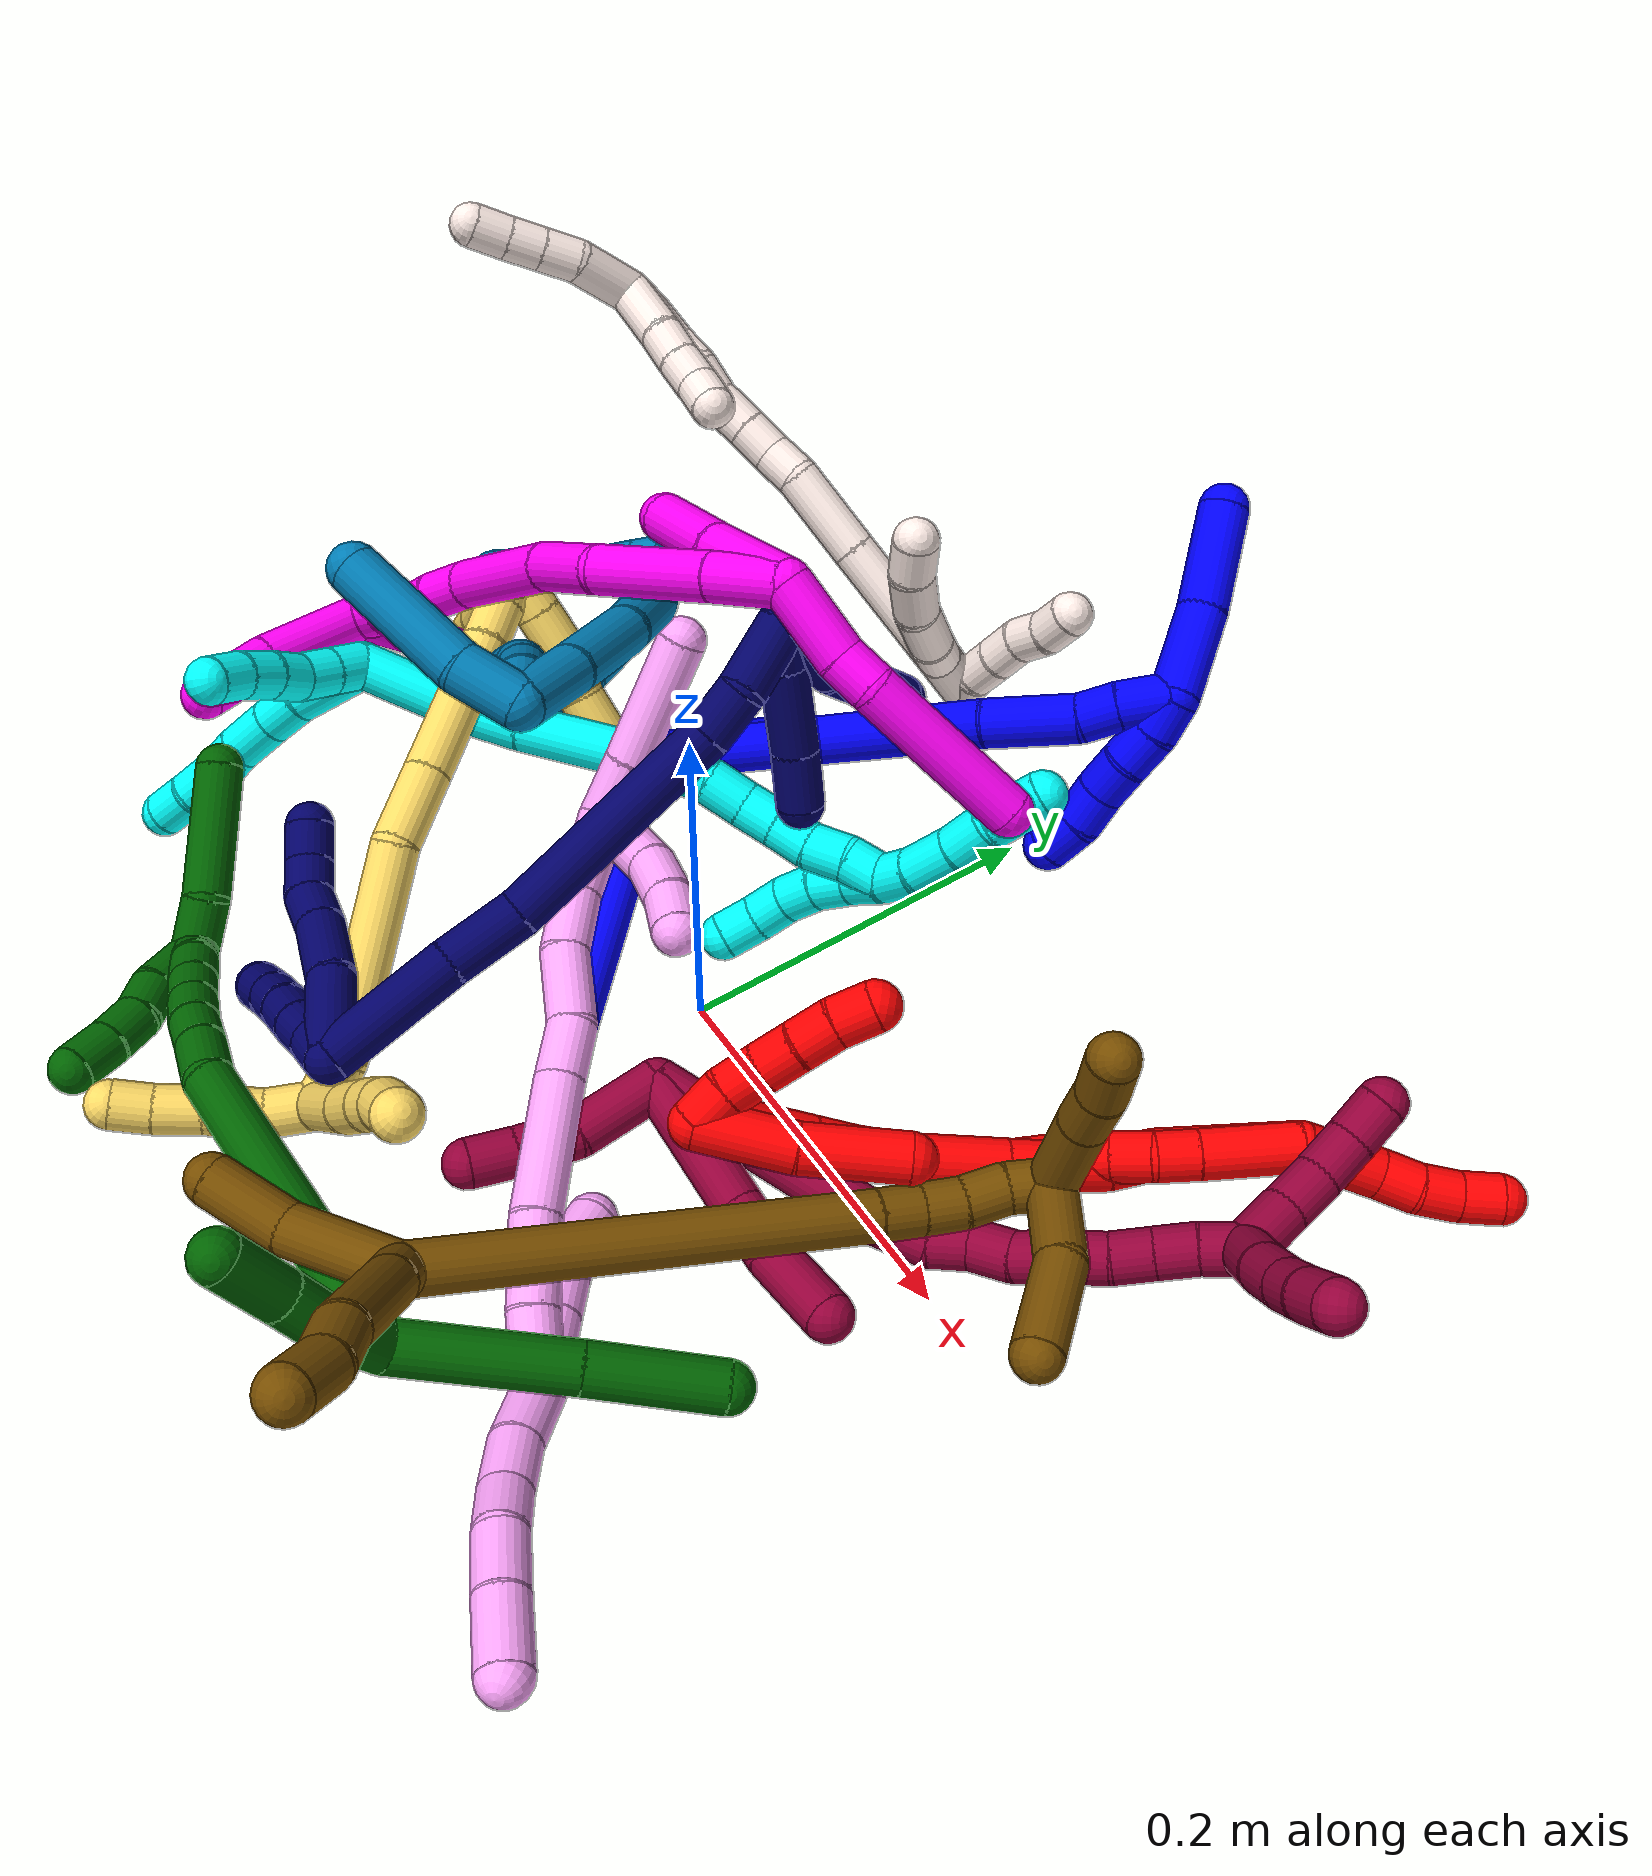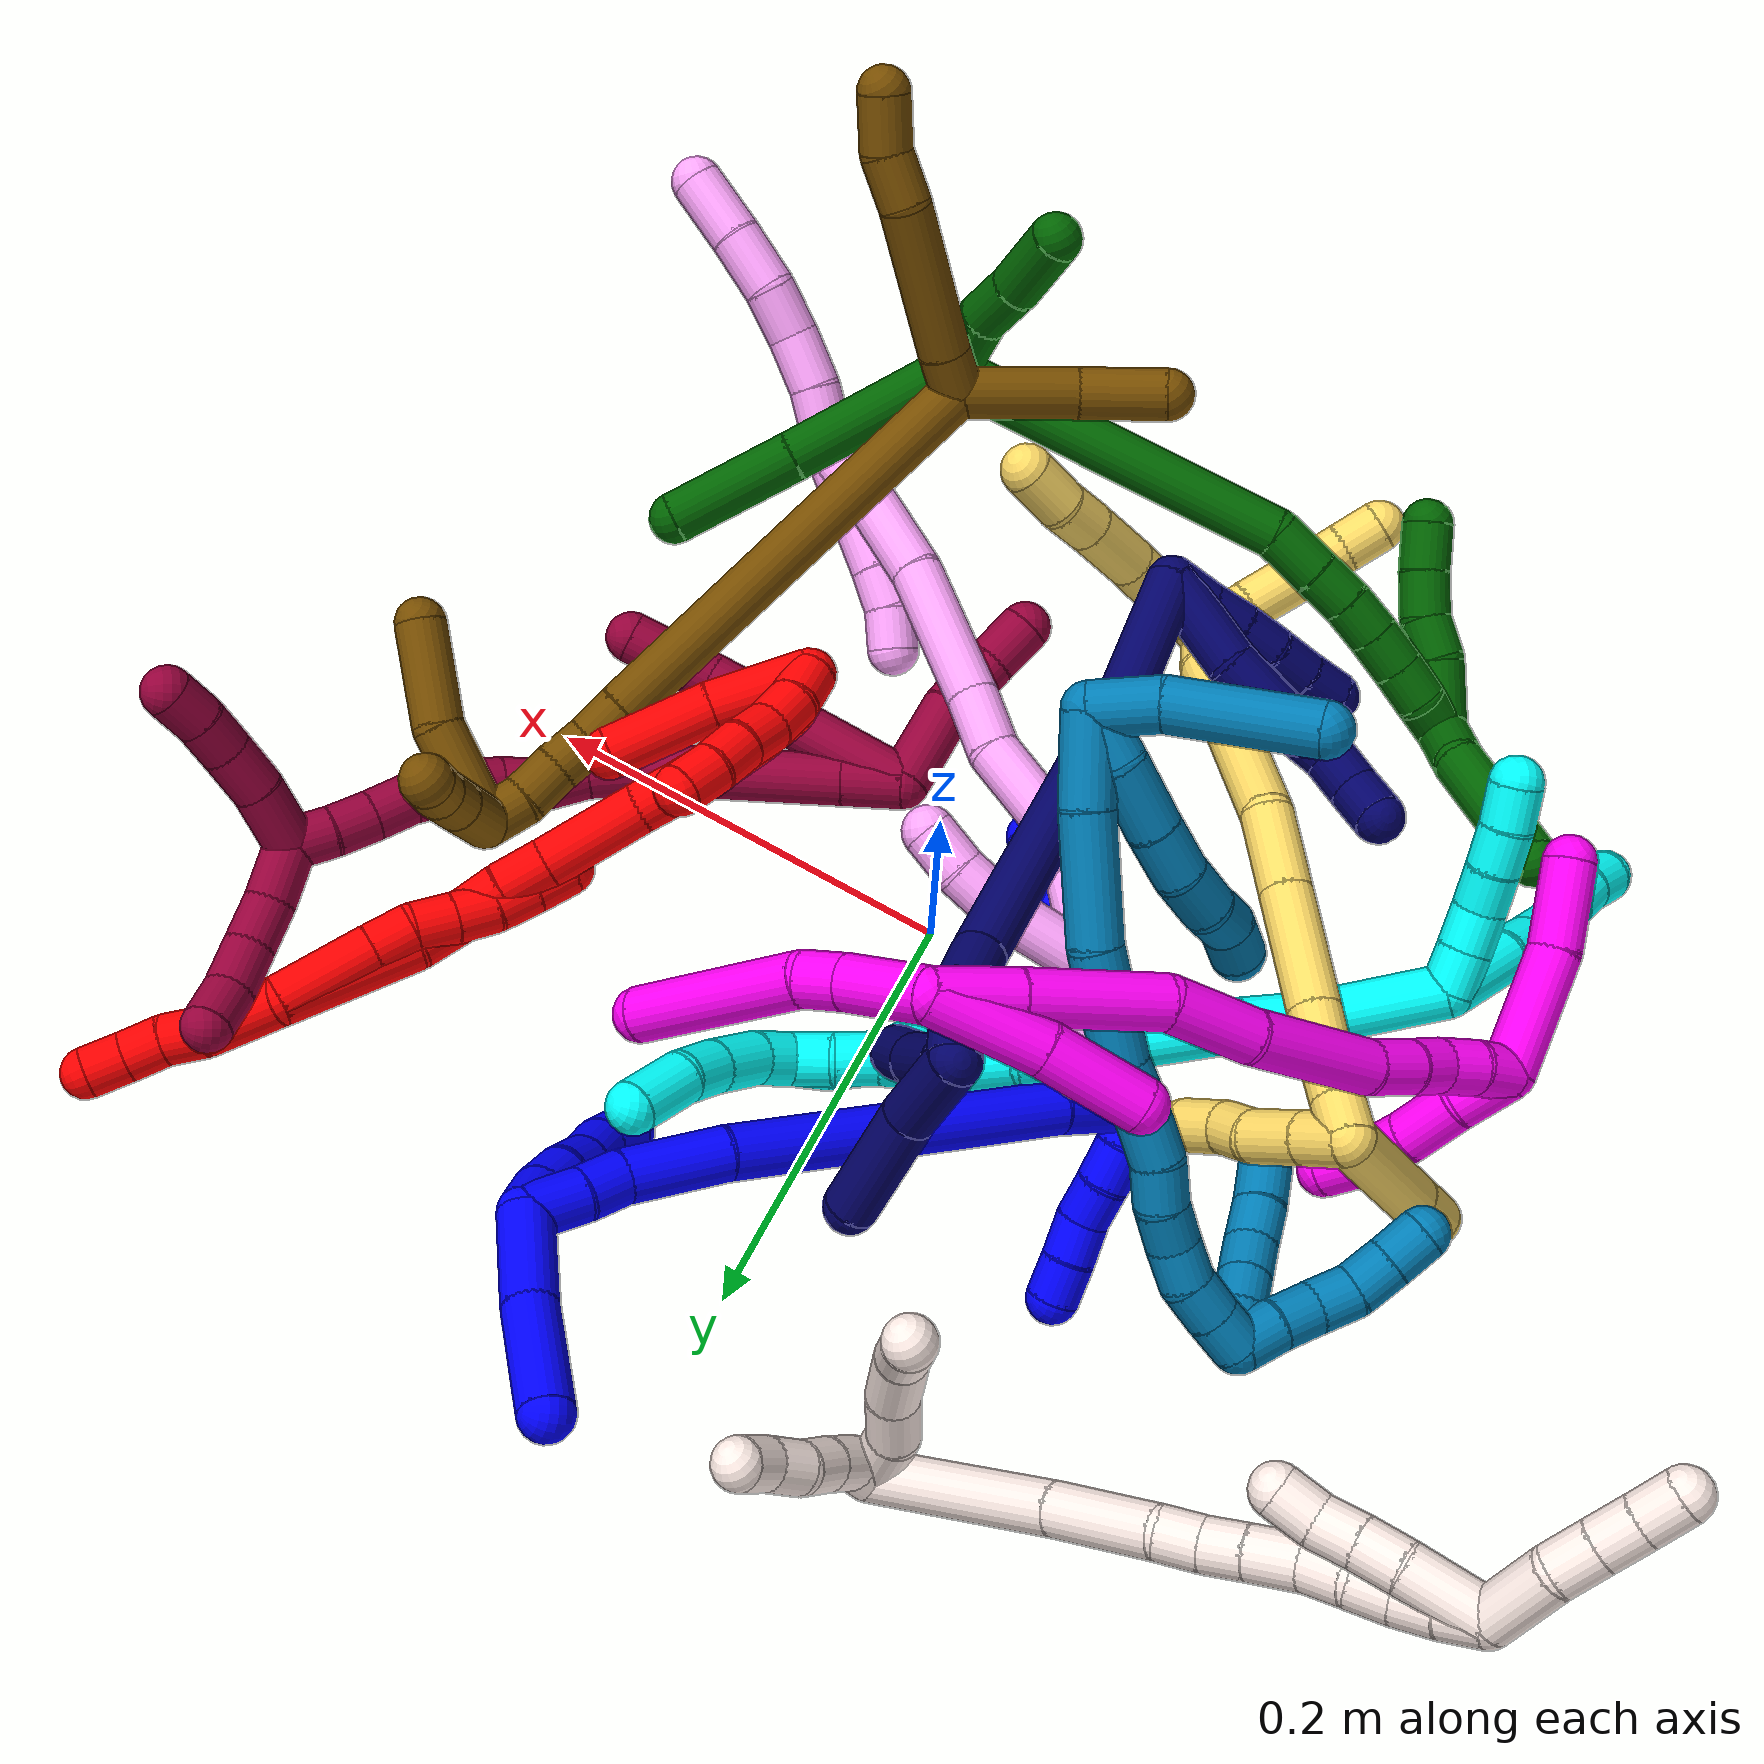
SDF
<sdf version="1.7">
 <world name="default">
  <plugin name="TubeGeneratorPlugin" filename="libtube_generator_plugin.so"/>
  <model name="photoneo_s_sensor">
   <static>1</static>
   <pose>0 0 2 1.57079 1.57079 3.14159</pose>
   <link name="link">
    <inertial><mass>0.1</mass></inertial>
    <sensor name="sensor" type="depth">
     <update_rate>30</update_rate>
     <camera>
      <horizontal_fov>1.22</horizontal_fov>
      <image><width>1920</width><height>1200</height><format>B8G8R8</format></image>
      <clip><near>0.1</near><far>4</far></clip>
      <depth_camera><output>points</output></depth_camera>
     </camera>
     <plugin name="camera_plugin" filename="libgazebo_ros_depth_camera.so">
      <baseline>0.2</baseline>
      <alwaysOn>1</alwaysOn>
      <updateRate>0.0</updateRate>
      <cameraName>camera_ir</cameraName>
      <imageTopicName>/camera/color/image_raw</imageTopicName>
      <cameraInfoTopicName>/camera/color/camera_info</cameraInfoTopicName>
      <depthImageTopicName>/camera/depth/image_raw</depthImageTopicName>
      <depthImageCameraInfoTopicName>/camera/depth/camera_info</depthImageCameraInfoTopicName>
      <pointCloudTopicName>/camera/depth/points</pointCloudTopicName>
      <frameName>fr_optical</frameName>
      <pointCloudCutoff>0.1</pointCloudCutoff>
      <pointCloudCutoffMax>2.0</pointCloudCutoffMax>
      <distortionK1>0</distortionK1>
      <distortionK2>0</distortionK2>
      <distortionK3>0</distortionK3>
      <distortionT1>0</distortionT1>
      <distortionT2>0</distortionT2>
      <CxPrime>0</CxPrime>
      <Cx>0</Cx>
      <Cy>0</Cy>
      <focalLength>0</focalLength>
      <hackBaseline>0</hackBaseline>
     </plugin>
    </sensor>
   </link>
  </model>
  <gravity>0 0 -9.8</gravity>
  <magnetic_field>6e-06 2.3e-05 -4.2e-05</magnetic_field>
  <atmosphere type="adiabatic"/>
  <physics name="default_physics" default="0" type="ode">
   <max_step_size>0.003</max_step_size>
   <real_time_factor>1</real_time_factor>
   <real_time_update_rate>1000</real_time_update_rate>
   <max_contacts>10000</max_contacts>
   <ode>
    <solver>
     <type>quick</type>
     <iters>100</iters>
     <sor>1.3</sor>
     <use_dynamic_moi_rescaling>0</use_dynamic_moi_rescaling>
    </solver>
    <constraints>
     <contact_max_correcting_vel>0</contact_max_correcting_vel>
     <contact_surface_layer>0.001</contact_surface_layer>
     <cfm>0</cfm>
     <erp>0.2</erp>
    </constraints>
   </ode>
  </physics>
  <scene><ambient>0.4 0.4 0.4 1</ambient><background>0.7 0.7 0.7 1</background><shadows>0</shadows></scene>
  <audio><device>default</device></audio>
  <spherical_coordinates>
   <surface_model>EARTH_WGS84</surface_model>
   <latitude_deg>0</latitude_deg>
   <longitude_deg>0</longitude_deg>
   <elevation>0</elevation>
   <heading_deg>0</heading_deg>
  </spherical_coordinates>
  <model name="bin">
   <static>1</static>
   <link name="bottom">
    <collision name="collision-bottom">
     <pose>0 0 -0.01 0 -0 0</pose>
     <geometry><box><size>0.8 0.6 0.02</size></box></geometry>
     <surface>
      <friction><ode><mu>100</mu><mu2>100</mu2></ode></friction>
      <contact><collide_bitmask>65535</collide_bitmask></contact>
     </surface>
    </collision>
   </link>
   <link name="west_wall">
    <collision name="collision-west_wall">
     <pose>-0.41 0 0.1 0 -0 0</pose>
     <geometry><box><size>0.02 0.6 0.2</size></box></geometry>
     <surface>
      <friction><ode><mu>100</mu><mu2>100</mu2></ode></friction>
      <contact><collide_bitmask>65535</collide_bitmask></contact>
     </surface>
    </collision>
   </link>
   <link name="east_wall">
    <collision name="collision-east_wall">
     <pose>0.41 0 0.1 0 -0 0</pose>
     <geometry><box><size>0.02 0.6 0.2</size></box></geometry>
     <surface>
      <friction><ode><mu>100</mu><mu2>100</mu2></ode></friction>
      <contact><collide_bitmask>65535</collide_bitmask></contact>
     </surface>
    </collision>
   </link>
   <link name="south_wall">
    <collision name="collision-south_wall">
     <pose>0 -0.31 0.1 0 -0 0</pose>
     <geometry><box><size>0.8 0.02 0.2</size></box></geometry>
     <surface>
      <friction><ode><mu>100</mu><mu2>100</mu2></ode></friction>
      <contact><collide_bitmask>65535</collide_bitmask></contact>
     </surface>
    </collision>
   </link>
   <link name="north_wall">
    <collision name="collision-north_wall">
     <pose>0 0.31 0.1 0 -0 0</pose>
     <geometry><box><size>0.8 0.02 0.2</size></box></geometry>
     <surface>
      <friction><ode><mu>100</mu><mu2>100</mu2></ode></friction>
      <contact><collide_bitmask>65535</collide_bitmask></contact>
     </surface>
    </collision>
   </link>
  </model>
  <model name="1">
   <static>0</static>
   <link name="1">
    <collision name="collision-cylinder-e_1_2_8">
     <pose>0.012931 -0.008279 0.002729 1.25238 0.977633 0.734493</pose>
     <geometry><cylinder><radius>0.0125</radius><length>0.031191</length></cylinder></geometry>
     <surface>
      <friction><ode><mu>1.16</mu><mu2>1.16</mu2><slip1>0</slip1><slip2>0</slip2></ode></friction>
      <contact><ode><kp>1e+06</kp><kd>1</kd><max_vel>0</max_vel><min_depth>0.001</min_depth></ode></contact>
     </surface>
    </collision>
    <visual name="visual-cylinder-e_1_2_8">
     <pose>0.012931 -0.008279 0.002729 1.25238 0.977633 0.734493</pose>
     <geometry><cylinder><radius>0.0125</radius><length>0.031191</length></cylinder></geometry>
     <material><ambient>0 0 1 1</ambient></material>
    </visual>
    <collision name="collision-cylinder-e_2_8_9">
     <pose>0.034975 -0.021853 0.007278 1.23975 1.01988 0.759584</pose>
     <geometry><cylinder><radius>0.0125</radius><length>0.021389</length></cylinder></geometry>
     <surface>
      <friction><ode><mu>1.16</mu><mu2>1.16</mu2><slip1>0</slip1><slip2>0</slip2></ode></friction>
      <contact><ode><kp>1e+06</kp><kd>1</kd><max_vel>0</max_vel><min_depth>0.001</min_depth></ode></contact>
     </surface>
    </collision>
    <visual name="visual-cylinder-e_2_8_9">
     <pose>0.034975 -0.021853 0.007278 1.23975 1.01988 0.759584</pose>
     <geometry><cylinder><radius>0.0125</radius><length>0.021389</length></cylinder></geometry>
     <material><ambient>0 0 1 1</ambient></material>
    </visual>
    <collision name="collision-cylinder-e_3_9_6">
     <pose>0.07711 -0.062424 0.015238 1.39847 0.74498 0.634961</pose>
     <geometry><cylinder><radius>0.0125</radius><length>0.09742</length></cylinder></geometry>
     <surface>
      <friction><ode><mu>1.16</mu><mu2>1.16</mu2><slip1>0</slip1><slip2>0</slip2></ode></friction>
      <contact><ode><kp>1e+06</kp><kd>1</kd><max_vel>0</max_vel><min_depth>0.001</min_depth></ode></contact>
     </surface>
    </collision>
    <visual name="visual-cylinder-e_3_9_6">
     <pose>0.07711 -0.062424 0.015238 1.39847 0.74498 0.634961</pose>
     <geometry><cylinder><radius>0.0125</radius><length>0.09742</length></cylinder></geometry>
     <material><ambient>0 0 1 1</ambient></material>
    </visual>
    <collision name="collision-cylinder-e_1_2_10">
     <pose>-0.000345 0.009913 0.001271 -1.44329 -0.034492 0.030353</pose>
     <geometry><cylinder><radius>0.0125</radius><length>0.02</length></cylinder></geometry>
     <surface>
      <friction><ode><mu>1.16</mu><mu2>1.16</mu2><slip1>0</slip1><slip2>0</slip2></ode></friction>
      <contact><ode><kp>1e+06</kp><kd>1</kd><max_vel>0</max_vel><min_depth>0.001</min_depth></ode></contact>
     </surface>
    </collision>
    <visual name="visual-cylinder-e_1_2_10">
     <pose>-0.000345 0.009913 0.001271 -1.44329 -0.034492 0.030353</pose>
     <geometry><cylinder><radius>0.0125</radius><length>0.02</length></cylinder></geometry>
     <material><ambient>0 0 1 1</ambient></material>
    </visual>
    <collision name="collision-cylinder-e_2_10_11">
     <pose>0.000945 0.029585 0.003984 -1.42409 0.164173 -0.141777</pose>
     <geometry><cylinder><radius>0.0125</radius><length>0.02</length></cylinder></geometry>
     <surface>
      <friction><ode><mu>1.16</mu><mu2>1.16</mu2><slip1>0</slip1><slip2>0</slip2></ode></friction>
      <contact><ode><kp>1e+06</kp><kd>1</kd><max_vel>0</max_vel><min_depth>0.001</min_depth></ode></contact>
     </surface>
    </collision>
    <visual name="visual-cylinder-e_2_10_11">
     <pose>0.000945 0.029585 0.003984 -1.42409 0.164173 -0.141777</pose>
     <geometry><cylinder><radius>0.0125</radius><length>0.02</length></cylinder></geometry>
     <material><ambient>0 0 1 1</ambient></material>
    </visual>
    <collision name="collision-cylinder-e_3_11_12">
     <pose>0.005499 0.048858 0.006418 -1.46691 0.296306 -0.267386</pose>
     <geometry><cylinder><radius>0.0125</radius><length>0.02</length></cylinder></geometry>
     <surface>
      <friction><ode><mu>1.16</mu><mu2>1.16</mu2><slip1>0</slip1><slip2>0</slip2></ode></friction>
      <contact><ode><kp>1e+06</kp><kd>1</kd><max_vel>0</max_vel><min_depth>0.001</min_depth></ode></contact>
     </surface>
    </collision>
    <visual name="visual-cylinder-e_3_11_12">
     <pose>0.005499 0.048858 0.006418 -1.46691 0.296306 -0.267386</pose>
     <geometry><cylinder><radius>0.0125</radius><length>0.02</length></cylinder></geometry>
     <material><ambient>0 0 1 1</ambient></material>
    </visual>
    <collision name="collision-cylinder-e_4_12_13">
     <pose>0.008601 0.068316 0.008436 -1.46797 0.018224 -0.016441</pose>
     <geometry><cylinder><radius>0.0125</radius><length>0.02</length></cylinder></geometry>
     <surface>
      <friction><ode><mu>1.16</mu><mu2>1.16</mu2><slip1>0</slip1><slip2>0</slip2></ode></friction>
      <contact><ode><kp>1e+06</kp><kd>1</kd><max_vel>0</max_vel><min_depth>0.001</min_depth></ode></contact>
     </surface>
    </collision>
    <visual name="visual-cylinder-e_4_12_13">
     <pose>0.008601 0.068316 0.008436 -1.46797 0.018224 -0.016441</pose>
     <geometry><cylinder><radius>0.0125</radius><length>0.02</length></cylinder></geometry>
     <material><ambient>0 0 1 1</ambient></material>
    </visual>
    <collision name="collision-cylinder-e_5_13_5">
     <pose>0.009874 0.088165 0.010316 -1.48475 0.109286 -0.100281</pose>
     <geometry><cylinder><radius>0.0125</radius><length>0.02</length></cylinder></geometry>
     <surface>
      <friction><ode><mu>1.16</mu><mu2>1.16</mu2><slip1>0</slip1><slip2>0</slip2></ode></friction>
      <contact><ode><kp>1e+06</kp><kd>1</kd><max_vel>0</max_vel><min_depth>0.001</min_depth></ode></contact>
     </surface>
    </collision>
    <visual name="visual-cylinder-e_5_13_5">
     <pose>0.009874 0.088165 0.010316 -1.48475 0.109286 -0.100281</pose>
     <geometry><cylinder><radius>0.0125</radius><length>0.02</length></cylinder></geometry>
     <material><ambient>0 0 1 1</ambient></material>
    </visual>
    <collision name="collision-cylinder-e_1_2_14">
     <pose>-0.001966 0.003095 0.021681 -0.141794 -0.089516 0.006361</pose>
     <geometry><cylinder><radius>0.0125</radius><length>0.043979</length></cylinder></geometry>
     <surface>
      <friction><ode><mu>1.16</mu><mu2>1.16</mu2><slip1>0</slip1><slip2>0</slip2></ode></friction>
      <contact><ode><kp>1e+06</kp><kd>1</kd><max_vel>0</max_vel><min_depth>0.001</min_depth></ode></contact>
     </surface>
    </collision>
    <visual name="visual-cylinder-e_1_2_14">
     <pose>-0.001966 0.003095 0.021681 -0.141794 -0.089516 0.006361</pose>
     <geometry><cylinder><radius>0.0125</radius><length>0.043979</length></cylinder></geometry>
     <material><ambient>0 0 1 1</ambient></material>
    </visual>
    <collision name="collision-cylinder-e_2_14_15">
     <pose>-0.003615 0.026135 0.12201 -0.248359 0.003907 -0.000488</pose>
     <geometry><cylinder><radius>0.0125</radius><length>0.162274</length></cylinder></geometry>
     <surface>
      <friction><ode><mu>1.16</mu><mu2>1.16</mu2><slip1>0</slip1><slip2>0</slip2></ode></friction>
      <contact><ode><kp>1e+06</kp><kd>1</kd><max_vel>0</max_vel><min_depth>0.001</min_depth></ode></contact>
     </surface>
    </collision>
    <visual name="visual-cylinder-e_2_14_15">
     <pose>-0.003615 0.026135 0.12201 -0.248359 0.003907 -0.000488</pose>
     <geometry><cylinder><radius>0.0125</radius><length>0.162274</length></cylinder></geometry>
     <material><ambient>0 0 1 1</ambient></material>
    </visual>
    <collision name="collision-cylinder-e_3_15_16">
     <pose>-0.001579 0.054433 0.222796 -0.3608 0.072492 -0.013227</pose>
     <geometry><cylinder><radius>0.0125</radius><length>0.04745</length></cylinder></geometry>
     <surface>
      <friction><ode><mu>1.16</mu><mu2>1.16</mu2><slip1>0</slip1><slip2>0</slip2></ode></friction>
      <contact><ode><kp>1e+06</kp><kd>1</kd><max_vel>0</max_vel><min_depth>0.001</min_depth></ode></contact>
     </surface>
    </collision>
    <visual name="visual-cylinder-e_3_15_16">
     <pose>-0.001579 0.054433 0.222796 -0.3608 0.072492 -0.013227</pose>
     <geometry><cylinder><radius>0.0125</radius><length>0.04745</length></cylinder></geometry>
     <material><ambient>0 0 1 1</ambient></material>
    </visual>
    <collision name="collision-cylinder-e_4_16_17">
     <pose>-0.001424 0.067175 0.253838 -0.458028 -0.156196 0.03648</pose>
     <geometry><cylinder><radius>0.0125</radius><length>0.020096</length></cylinder></geometry>
     <surface>
      <friction><ode><mu>1.16</mu><mu2>1.16</mu2><slip1>0</slip1><slip2>0</slip2></ode></friction>
      <contact><ode><kp>1e+06</kp><kd>1</kd><max_vel>0</max_vel><min_depth>0.001</min_depth></ode></contact>
     </surface>
    </collision>
    <visual name="visual-cylinder-e_4_16_17">
     <pose>-0.001424 0.067175 0.253838 -0.458028 -0.156196 0.03648</pose>
     <geometry><cylinder><radius>0.0125</radius><length>0.020096</length></cylinder></geometry>
     <material><ambient>0 0 1 1</ambient></material>
    </visual>
    <collision name="collision-cylinder-e_5_17_1">
     <pose>-0.003441 0.076798 0.274741 -0.411254 -0.034685 0.007235</pose>
     <geometry><cylinder><radius>0.0125</radius><length>0.026201</length></cylinder></geometry>
     <surface>
      <friction><ode><mu>1.16</mu><mu2>1.16</mu2><slip1>0</slip1><slip2>0</slip2></ode></friction>
      <contact><ode><kp>1e+06</kp><kd>1</kd><max_vel>0</max_vel><min_depth>0.001</min_depth></ode></contact>
     </surface>
    </collision>
    <visual name="visual-cylinder-e_5_17_1">
     <pose>-0.003441 0.076798 0.274741 -0.411254 -0.034685 0.007235</pose>
     <geometry><cylinder><radius>0.0125</radius><length>0.026201</length></cylinder></geometry>
     <material><ambient>0 0 1 1</ambient></material>
    </visual>
    <collision name="collision-cylinder-e_1_1_18">
     <pose>-0.02156 0.096979 0.28898 -1.42222 -0.863065 0.755285</pose>
     <geometry><cylinder><radius>0.0125</radius><length>0.046495</length></cylinder></geometry>
     <surface>
      <friction><ode><mu>1.16</mu><mu2>1.16</mu2><slip1>0</slip1><slip2>0</slip2></ode></friction>
      <contact><ode><kp>1e+06</kp><kd>1</kd><max_vel>0</max_vel><min_depth>0.001</min_depth></ode></contact>
     </surface>
    </collision>
    <visual name="visual-cylinder-e_1_1_18">
     <pose>-0.02156 0.096979 0.28898 -1.42222 -0.863065 0.755285</pose>
     <geometry><cylinder><radius>0.0125</radius><length>0.046495</length></cylinder></geometry>
     <material><ambient>0 0 1 1</ambient></material>
    </visual>
    <collision name="collision-cylinder-e_2_18_4">
     <pose>-0.061476 0.126691 0.292804 -1.46371 -0.982292 0.895768</pose>
     <geometry><cylinder><radius>0.0125</radius><length>0.053505</length></cylinder></geometry>
     <surface>
      <friction><ode><mu>1.16</mu><mu2>1.16</mu2><slip1>0</slip1><slip2>0</slip2></ode></friction>
      <contact><ode><kp>1e+06</kp><kd>1</kd><max_vel>0</max_vel><min_depth>0.001</min_depth></ode></contact>
     </surface>
    </collision>
    <visual name="visual-cylinder-e_2_18_4">
     <pose>-0.061476 0.126691 0.292804 -1.46371 -0.982292 0.895768</pose>
     <geometry><cylinder><radius>0.0125</radius><length>0.053505</length></cylinder></geometry>
     <material><ambient>0 0 1 1</ambient></material>
    </visual>
    <collision name="collision-cylinder-e_1_1_19">
     <pose>0.003876 0.079249 0.281099 2.68353 0.890186 2.23245</pose>
     <geometry><cylinder><radius>0.0125</radius><length>0.02</length></cylinder></geometry>
     <surface>
      <friction><ode><mu>1.16</mu><mu2>1.16</mu2><slip1>0</slip1><slip2>0</slip2></ode></friction>
      <contact><ode><kp>1e+06</kp><kd>1</kd><max_vel>0</max_vel><min_depth>0.001</min_depth></ode></contact>
     </surface>
    </collision>
    <visual name="visual-cylinder-e_1_1_19">
     <pose>0.003876 0.079249 0.281099 2.68353 0.890186 2.23245</pose>
     <geometry><cylinder><radius>0.0125</radius><length>0.02</length></cylinder></geometry>
     <material><ambient>0 0 1 1</ambient></material>
    </visual>
    <collision name="collision-cylinder-e_2_19_20">
     <pose>0.018042 0.073463 0.268377 2.74021 0.69375 2.11644</pose>
     <geometry><cylinder><radius>0.0125</radius><length>0.02</length></cylinder></geometry>
     <surface>
      <friction><ode><mu>1.16</mu><mu2>1.16</mu2><slip1>0</slip1><slip2>0</slip2></ode></friction>
      <contact><ode><kp>1e+06</kp><kd>1</kd><max_vel>0</max_vel><min_depth>0.001</min_depth></ode></contact>
     </surface>
    </collision>
    <visual name="visual-cylinder-e_2_19_20">
     <pose>0.018042 0.073463 0.268377 2.74021 0.69375 2.11644</pose>
     <geometry><cylinder><radius>0.0125</radius><length>0.02</length></cylinder></geometry>
     <material><ambient>0 0 1 1</ambient></material>
    </visual>
    <collision name="collision-cylinder-e_3_20_21">
     <pose>0.030952 0.069186 0.253821 2.97308 0.709558 2.69328</pose>
     <geometry><cylinder><radius>0.0125</radius><length>0.02</length></cylinder></geometry>
     <surface>
      <friction><ode><mu>1.16</mu><mu2>1.16</mu2><slip1>0</slip1><slip2>0</slip2></ode></friction>
      <contact><ode><kp>1e+06</kp><kd>1</kd><max_vel>0</max_vel><min_depth>0.001</min_depth></ode></contact>
     </surface>
    </collision>
    <visual name="visual-cylinder-e_3_20_21">
     <pose>0.030952 0.069186 0.253821 2.97308 0.709558 2.69328</pose>
     <geometry><cylinder><radius>0.0125</radius><length>0.02</length></cylinder></geometry>
     <material><ambient>0 0 1 1</ambient></material>
    </visual>
    <collision name="collision-cylinder-e_4_21_22">
     <pose>0.044686 0.065349 0.239915 2.76187 0.806567 2.29521</pose>
     <geometry><cylinder><radius>0.0125</radius><length>0.02</length></cylinder></geometry>
     <surface>
      <friction><ode><mu>1.16</mu><mu2>1.16</mu2><slip1>0</slip1><slip2>0</slip2></ode></friction>
      <contact><ode><kp>1e+06</kp><kd>1</kd><max_vel>0</max_vel><min_depth>0.001</min_depth></ode></contact>
     </surface>
    </collision>
    <visual name="visual-cylinder-e_4_21_22">
     <pose>0.044686 0.065349 0.239915 2.76187 0.806567 2.29521</pose>
     <geometry><cylinder><radius>0.0125</radius><length>0.02</length></cylinder></geometry>
     <material><ambient>0 0 1 1</ambient></material>
    </visual>
    <collision name="collision-cylinder-e_5_22_3">
     <pose>0.057195 0.060344 0.22536 2.84987 0.557385 2.19297</pose>
     <geometry><cylinder><radius>0.0125</radius><length>0.02</length></cylinder></geometry>
     <surface>
      <friction><ode><mu>1.16</mu><mu2>1.16</mu2><slip1>0</slip1><slip2>0</slip2></ode></friction>
      <contact><ode><kp>1e+06</kp><kd>1</kd><max_vel>0</max_vel><min_depth>0.001</min_depth></ode></contact>
     </surface>
    </collision>
    <visual name="visual-cylinder-e_5_22_3">
     <pose>0.057195 0.060344 0.22536 2.84987 0.557385 2.19297</pose>
     <geometry><cylinder><radius>0.0125</radius><length>0.02</length></cylinder></geometry>
     <material><ambient>0 0 1 1</ambient></material>
    </visual>
    <collision name="collision-sphere-3">
     <pose>0.062484 0.057903 0.217232 0 -0 0</pose>
     <geometry><sphere><radius>0.0125</radius></sphere></geometry>
     <surface>
      <friction><ode><mu>1.16</mu><mu2>1.16</mu2><slip1>0</slip1><slip2>0</slip2></ode></friction>
      <contact><ode><kp>1e+06</kp><kd>1</kd><max_vel>0</max_vel><min_depth>0.001</min_depth></ode></contact>
     </surface>
    </collision>
    <visual name="visual-sphere-3">
     <pose>0.062484 0.057903 0.217232 0 -0 0</pose>
     <geometry><sphere><radius>0.0125</radius></sphere></geometry>
     <material><ambient>0 0 1 1</ambient></material>
    </visual>
    <collision name="collision-sphere-22">
     <pose>0.051905 0.062784 0.233488 0 -0 0</pose>
     <geometry><sphere><radius>0.0125</radius></sphere></geometry>
     <surface>
      <friction><ode><mu>1.16</mu><mu2>1.16</mu2><slip1>0</slip1><slip2>0</slip2></ode></friction>
      <contact><ode><kp>1e+06</kp><kd>1</kd><max_vel>0</max_vel><min_depth>0.001</min_depth></ode></contact>
     </surface>
    </collision>
    <visual name="visual-sphere-22">
     <pose>0.051905 0.062784 0.233488 0 -0 0</pose>
     <geometry><sphere><radius>0.0125</radius></sphere></geometry>
     <material><ambient>0 0 1 1</ambient></material>
    </visual>
    <collision name="collision-sphere-21">
     <pose>0.037467 0.067914 0.246342 0 -0 0</pose>
     <geometry><sphere><radius>0.0125</radius></sphere></geometry>
     <surface>
      <friction><ode><mu>1.16</mu><mu2>1.16</mu2><slip1>0</slip1><slip2>0</slip2></ode></friction>
      <contact><ode><kp>1e+06</kp><kd>1</kd><max_vel>0</max_vel><min_depth>0.001</min_depth></ode></contact>
     </surface>
    </collision>
    <visual name="visual-sphere-21">
     <pose>0.037467 0.067914 0.246342 0 -0 0</pose>
     <geometry><sphere><radius>0.0125</radius></sphere></geometry>
     <material><ambient>0 0 1 1</ambient></material>
    </visual>
    <collision name="collision-sphere-20">
     <pose>0.024437 0.070459 0.2613 0 -0 0</pose>
     <geometry><sphere><radius>0.0125</radius></sphere></geometry>
     <surface>
      <friction><ode><mu>1.16</mu><mu2>1.16</mu2><slip1>0</slip1><slip2>0</slip2></ode></friction>
      <contact><ode><kp>1e+06</kp><kd>1</kd><max_vel>0</max_vel><min_depth>0.001</min_depth></ode></contact>
     </surface>
    </collision>
    <visual name="visual-sphere-20">
     <pose>0.024437 0.070459 0.2613 0 -0 0</pose>
     <geometry><sphere><radius>0.0125</radius></sphere></geometry>
     <material><ambient>0 0 1 1</ambient></material>
    </visual>
    <collision name="collision-sphere-19">
     <pose>0.011648 0.076466 0.275455 0 -0 0</pose>
     <geometry><sphere><radius>0.0125</radius></sphere></geometry>
     <surface>
      <friction><ode><mu>1.16</mu><mu2>1.16</mu2><slip1>0</slip1><slip2>0</slip2></ode></friction>
      <contact><ode><kp>1e+06</kp><kd>1</kd><max_vel>0</max_vel><min_depth>0.001</min_depth></ode></contact>
     </surface>
    </collision>
    <visual name="visual-sphere-19">
     <pose>0.011648 0.076466 0.275455 0 -0 0</pose>
     <geometry><sphere><radius>0.0125</radius></sphere></geometry>
     <material><ambient>0 0 1 1</ambient></material>
    </visual>
    <collision name="collision-sphere-11">
     <pose>0.002579 0.039345 0.005426 0 -0 0</pose>
     <geometry><sphere><radius>0.0125</radius></sphere></geometry>
     <surface>
      <friction><ode><mu>1.16</mu><mu2>1.16</mu2><slip1>0</slip1><slip2>0</slip2></ode></friction>
      <contact><ode><kp>1e+06</kp><kd>1</kd><max_vel>0</max_vel><min_depth>0.001</min_depth></ode></contact>
     </surface>
    </collision>
    <visual name="visual-sphere-11">
     <pose>0.002579 0.039345 0.005426 0 -0 0</pose>
     <geometry><sphere><radius>0.0125</radius></sphere></geometry>
     <material><ambient>0 0 1 1</ambient></material>
    </visual>
    <collision name="collision-sphere-10">
     <pose>-0.00069 0.019826 0.002542 0 -0 0</pose>
     <geometry><sphere><radius>0.0125</radius></sphere></geometry>
     <surface>
      <friction><ode><mu>1.16</mu><mu2>1.16</mu2><slip1>0</slip1><slip2>0</slip2></ode></friction>
      <contact><ode><kp>1e+06</kp><kd>1</kd><max_vel>0</max_vel><min_depth>0.001</min_depth></ode></contact>
     </surface>
    </collision>
    <visual name="visual-sphere-10">
     <pose>-0.00069 0.019826 0.002542 0 -0 0</pose>
     <geometry><sphere><radius>0.0125</radius></sphere></geometry>
     <material><ambient>0 0 1 1</ambient></material>
    </visual>
    <collision name="collision-sphere-6">
     <pose>0.110134 -0.0977 0.021378 0 -0 0</pose>
     <geometry><sphere><radius>0.0125</radius></sphere></geometry>
     <surface>
      <friction><ode><mu>1.16</mu><mu2>1.16</mu2><slip1>0</slip1><slip2>0</slip2></ode></friction>
      <contact><ode><kp>1e+06</kp><kd>1</kd><max_vel>0</max_vel><min_depth>0.001</min_depth></ode></contact>
     </surface>
    </collision>
    <visual name="visual-sphere-6">
     <pose>0.110134 -0.0977 0.021378 0 -0 0</pose>
     <geometry><sphere><radius>0.0125</radius></sphere></geometry>
     <material><ambient>0 0 1 1</ambient></material>
    </visual>
    <collision name="collision-sphere-9">
     <pose>0.044087 -0.027147 0.009097 0 -0 0</pose>
     <geometry><sphere><radius>0.0125</radius></sphere></geometry>
     <surface>
      <friction><ode><mu>1.16</mu><mu2>1.16</mu2><slip1>0</slip1><slip2>0</slip2></ode></friction>
      <contact><ode><kp>1e+06</kp><kd>1</kd><max_vel>0</max_vel><min_depth>0.001</min_depth></ode></contact>
     </surface>
    </collision>
    <visual name="visual-sphere-9">
     <pose>0.044087 -0.027147 0.009097 0 -0 0</pose>
     <geometry><sphere><radius>0.0125</radius></sphere></geometry>
     <material><ambient>0 0 1 1</ambient></material>
    </visual>
    <collision name="collision-sphere-2">
     <geometry><sphere><radius>0.0125</radius></sphere></geometry>
     <surface>
      <friction><ode><mu>1.16</mu><mu2>1.16</mu2><slip1>0</slip1><slip2>0</slip2></ode></friction>
      <contact><ode><kp>1e+06</kp><kd>1</kd><max_vel>0</max_vel><min_depth>0.001</min_depth></ode></contact>
     </surface>
    </collision>
    <visual name="visual-sphere-2">
     <geometry><sphere><radius>0.0125</radius></sphere></geometry>
     <material><ambient>0 0 1 1</ambient></material>
    </visual>
    <collision name="collision-sphere-8">
     <pose>0.025862 -0.016559 0.005458 0 -0 0</pose>
     <geometry><sphere><radius>0.0125</radius></sphere></geometry>
     <surface>
      <friction><ode><mu>1.16</mu><mu2>1.16</mu2><slip1>0</slip1><slip2>0</slip2></ode></friction>
      <contact><ode><kp>1e+06</kp><kd>1</kd><max_vel>0</max_vel><min_depth>0.001</min_depth></ode></contact>
     </surface>
    </collision>
    <visual name="visual-sphere-8">
     <pose>0.025862 -0.016559 0.005458 0 -0 0</pose>
     <geometry><sphere><radius>0.0125</radius></sphere></geometry>
     <material><ambient>0 0 1 1</ambient></material>
    </visual>
    <collision name="collision-sphere-12">
     <pose>0.008419 0.05837 0.00741 0 -0 0</pose>
     <geometry><sphere><radius>0.0125</radius></sphere></geometry>
     <surface>
      <friction><ode><mu>1.16</mu><mu2>1.16</mu2><slip1>0</slip1><slip2>0</slip2></ode></friction>
      <contact><ode><kp>1e+06</kp><kd>1</kd><max_vel>0</max_vel><min_depth>0.001</min_depth></ode></contact>
     </surface>
    </collision>
    <visual name="visual-sphere-12">
     <pose>0.008419 0.05837 0.00741 0 -0 0</pose>
     <geometry><sphere><radius>0.0125</radius></sphere></geometry>
     <material><ambient>0 0 1 1</ambient></material>
    </visual>
    <collision name="collision-sphere-13">
     <pose>0.008783 0.078261 0.009462 0 -0 0</pose>
     <geometry><sphere><radius>0.0125</radius></sphere></geometry>
     <surface>
      <friction><ode><mu>1.16</mu><mu2>1.16</mu2><slip1>0</slip1><slip2>0</slip2></ode></friction>
      <contact><ode><kp>1e+06</kp><kd>1</kd><max_vel>0</max_vel><min_depth>0.001</min_depth></ode></contact>
     </surface>
    </collision>
    <visual name="visual-sphere-13">
     <pose>0.008783 0.078261 0.009462 0 -0 0</pose>
     <geometry><sphere><radius>0.0125</radius></sphere></geometry>
     <material><ambient>0 0 1 1</ambient></material>
    </visual>
    <collision name="collision-sphere-5">
     <pose>0.010965 0.098068 0.011171 0 -0 0</pose>
     <geometry><sphere><radius>0.0125</radius></sphere></geometry>
     <surface>
      <friction><ode><mu>1.16</mu><mu2>1.16</mu2><slip1>0</slip1><slip2>0</slip2></ode></friction>
      <contact><ode><kp>1e+06</kp><kd>1</kd><max_vel>0</max_vel><min_depth>0.001</min_depth></ode></contact>
     </surface>
    </collision>
    <visual name="visual-sphere-5">
     <pose>0.010965 0.098068 0.011171 0 -0 0</pose>
     <geometry><sphere><radius>0.0125</radius></sphere></geometry>
     <material><ambient>0 0 1 1</ambient></material>
    </visual>
    <collision name="collision-sphere-14">
     <pose>-0.003932 0.00619 0.043363 0 -0 0</pose>
     <geometry><sphere><radius>0.0125</radius></sphere></geometry>
     <surface>
      <friction><ode><mu>1.16</mu><mu2>1.16</mu2><slip1>0</slip1><slip2>0</slip2></ode></friction>
      <contact><ode><kp>1e+06</kp><kd>1</kd><max_vel>0</max_vel><min_depth>0.001</min_depth></ode></contact>
     </surface>
    </collision>
    <visual name="visual-sphere-14">
     <pose>-0.003932 0.00619 0.043363 0 -0 0</pose>
     <geometry><sphere><radius>0.0125</radius></sphere></geometry>
     <material><ambient>0 0 1 1</ambient></material>
    </visual>
    <collision name="collision-sphere-15">
     <pose>-0.003298 0.046079 0.200657 0 -0 0</pose>
     <geometry><sphere><radius>0.0125</radius></sphere></geometry>
     <surface>
      <friction><ode><mu>1.16</mu><mu2>1.16</mu2><slip1>0</slip1><slip2>0</slip2></ode></friction>
      <contact><ode><kp>1e+06</kp><kd>1</kd><max_vel>0</max_vel><min_depth>0.001</min_depth></ode></contact>
     </surface>
    </collision>
    <visual name="visual-sphere-15">
     <pose>-0.003298 0.046079 0.200657 0 -0 0</pose>
     <geometry><sphere><radius>0.0125</radius></sphere></geometry>
     <material><ambient>0 0 1 1</ambient></material>
    </visual>
    <collision name="collision-sphere-16">
     <pose>0.000139 0.062786 0.244935 0 -0 0</pose>
     <geometry><sphere><radius>0.0125</radius></sphere></geometry>
     <surface>
      <friction><ode><mu>1.16</mu><mu2>1.16</mu2><slip1>0</slip1><slip2>0</slip2></ode></friction>
      <contact><ode><kp>1e+06</kp><kd>1</kd><max_vel>0</max_vel><min_depth>0.001</min_depth></ode></contact>
     </surface>
    </collision>
    <visual name="visual-sphere-16">
     <pose>0.000139 0.062786 0.244935 0 -0 0</pose>
     <geometry><sphere><radius>0.0125</radius></sphere></geometry>
     <material><ambient>0 0 1 1</ambient></material>
    </visual>
    <collision name="collision-sphere-17">
     <pose>-0.002987 0.071564 0.26274 0 -0 0</pose>
     <geometry><sphere><radius>0.0125</radius></sphere></geometry>
     <surface>
      <friction><ode><mu>1.16</mu><mu2>1.16</mu2><slip1>0</slip1><slip2>0</slip2></ode></friction>
      <contact><ode><kp>1e+06</kp><kd>1</kd><max_vel>0</max_vel><min_depth>0.001</min_depth></ode></contact>
     </surface>
    </collision>
    <visual name="visual-sphere-17">
     <pose>-0.002987 0.071564 0.26274 0 -0 0</pose>
     <geometry><sphere><radius>0.0125</radius></sphere></geometry>
     <material><ambient>0 0 1 1</ambient></material>
    </visual>
    <collision name="collision-sphere-1">
     <pose>-0.003896 0.082032 0.286742 0 -0 0</pose>
     <geometry><sphere><radius>0.0125</radius></sphere></geometry>
     <surface>
      <friction><ode><mu>1.16</mu><mu2>1.16</mu2><slip1>0</slip1><slip2>0</slip2></ode></friction>
      <contact><ode><kp>1e+06</kp><kd>1</kd><max_vel>0</max_vel><min_depth>0.001</min_depth></ode></contact>
     </surface>
    </collision>
    <visual name="visual-sphere-1">
     <pose>-0.003896 0.082032 0.286742 0 -0 0</pose>
     <geometry><sphere><radius>0.0125</radius></sphere></geometry>
     <material><ambient>0 0 1 1</ambient></material>
    </visual>
    <collision name="collision-sphere-18">
     <pose>-0.039224 0.111926 0.291217 0 -0 0</pose>
     <geometry><sphere><radius>0.0125</radius></sphere></geometry>
     <surface>
      <friction><ode><mu>1.16</mu><mu2>1.16</mu2><slip1>0</slip1><slip2>0</slip2></ode></friction>
      <contact><ode><kp>1e+06</kp><kd>1</kd><max_vel>0</max_vel><min_depth>0.001</min_depth></ode></contact>
     </surface>
    </collision>
    <visual name="visual-sphere-18">
     <pose>-0.039224 0.111926 0.291217 0 -0 0</pose>
     <geometry><sphere><radius>0.0125</radius></sphere></geometry>
     <material><ambient>0 0 1 1</ambient></material>
    </visual>
    <collision name="collision-sphere-4">
     <pose>-0.083728 0.141457 0.294391 0 -0 0</pose>
     <geometry><sphere><radius>0.0125</radius></sphere></geometry>
     <surface>
      <friction><ode><mu>1.16</mu><mu2>1.16</mu2><slip1>0</slip1><slip2>0</slip2></ode></friction>
      <contact><ode><kp>1e+06</kp><kd>1</kd><max_vel>0</max_vel><min_depth>0.001</min_depth></ode></contact>
     </surface>
    </collision>
    <visual name="visual-sphere-4">
     <pose>-0.083728 0.141457 0.294391 0 -0 0</pose>
     <geometry><sphere><radius>0.0125</radius></sphere></geometry>
     <material><ambient>0 0 1 1</ambient></material>
    </visual>
    <inertial>
     <pose>0.009455 0.035535 0.133909 0 -0 0</pose>
     <mass>0.75</mass>
     <inertia><ixx>0.000509</ixx><ixy>0</ixy><ixz>0</ixz><iyy>0.000505</iyy><iyz>0</iyz><izz>-8e-05</izz></inertia>
    </inertial>
   </link>
   <pose>-0.125314 0.035511 0.051275 -0.640254 0.903513 -0.277146</pose>
  </model>
  <model name="2">
   <static>0</static>
   <link name="2">
    <collision name="collision-cylinder-e_1_2_8">
     <pose>0.007079 -0.001463 -0.023442 3.07928 0.292723 2.72488</pose>
     <geometry><cylinder><radius>0.0125</radius><length>0.049062</length></cylinder></geometry>
     <surface>
      <friction><ode><mu>1.16</mu><mu2>1.16</mu2><slip1>0</slip1><slip2>0</slip2></ode></friction>
      <contact><ode><kp>1e+06</kp><kd>1</kd><max_vel>0</max_vel><min_depth>0.001</min_depth></ode></contact>
     </surface>
    </collision>
    <visual name="visual-cylinder-e_1_2_8">
     <pose>0.007079 -0.001463 -0.023442 3.07928 0.292723 2.72488</pose>
     <geometry><cylinder><radius>0.0125</radius><length>0.049062</length></cylinder></geometry>
     <material><ambient>1 0 0 1</ambient></material>
    </visual>
    <collision name="collision-cylinder-e_2_8_9">
     <pose>0.01697 -0.003338 -0.056877 3.10035 0.274128 2.84476</pose>
     <geometry><cylinder><radius>0.0125</radius><length>0.020779</length></cylinder></geometry>
     <surface>
      <friction><ode><mu>1.16</mu><mu2>1.16</mu2><slip1>0</slip1><slip2>0</slip2></ode></friction>
      <contact><ode><kp>1e+06</kp><kd>1</kd><max_vel>0</max_vel><min_depth>0.001</min_depth></ode></contact>
     </surface>
    </collision>
    <visual name="visual-cylinder-e_2_8_9">
     <pose>0.01697 -0.003338 -0.056877 3.10035 0.274128 2.84476</pose>
     <geometry><cylinder><radius>0.0125</radius><length>0.020779</length></cylinder></geometry>
     <material><ambient>1 0 0 1</ambient></material>
    </visual>
    <collision name="collision-cylinder-e_3_9_10">
     <pose>0.023505 -0.001646 -0.075987 -2.91484 0.37865 -2.06928</pose>
     <geometry><cylinder><radius>0.0125</radius><length>0.020141</length></cylinder></geometry>
     <surface>
      <friction><ode><mu>1.16</mu><mu2>1.16</mu2><slip1>0</slip1><slip2>0</slip2></ode></friction>
      <contact><ode><kp>1e+06</kp><kd>1</kd><max_vel>0</max_vel><min_depth>0.001</min_depth></ode></contact>
     </surface>
    </collision>
    <visual name="visual-cylinder-e_3_9_10">
     <pose>0.023505 -0.001646 -0.075987 -2.91484 0.37865 -2.06928</pose>
     <geometry><cylinder><radius>0.0125</radius><length>0.020141</length></cylinder></geometry>
     <material><ambient>1 0 0 1</ambient></material>
    </visual>
    <collision name="collision-cylinder-e_4_10_11">
     <pose>0.031024 0.002314 -0.094177 -2.93967 0.389053 -2.1917</pose>
     <geometry><cylinder><radius>0.0125</radius><length>0.020017</length></cylinder></geometry>
     <surface>
      <friction><ode><mu>1.16</mu><mu2>1.16</mu2><slip1>0</slip1><slip2>0</slip2></ode></friction>
      <contact><ode><kp>1e+06</kp><kd>1</kd><max_vel>0</max_vel><min_depth>0.001</min_depth></ode></contact>
     </surface>
    </collision>
    <visual name="visual-cylinder-e_4_10_11">
     <pose>0.031024 0.002314 -0.094177 -2.93967 0.389053 -2.1917</pose>
     <geometry><cylinder><radius>0.0125</radius><length>0.020017</length></cylinder></geometry>
     <material><ambient>1 0 0 1</ambient></material>
    </visual>
    <collision name="collision-cylinder-e_5_11_12">
     <pose>0.038764 0.004236 -0.112439 -3.13458 0.405391 -3.10748</pose>
     <geometry><cylinder><radius>0.0125</radius><length>0.020001</length></cylinder></geometry>
     <surface>
      <friction><ode><mu>1.16</mu><mu2>1.16</mu2><slip1>0</slip1><slip2>0</slip2></ode></friction>
      <contact><ode><kp>1e+06</kp><kd>1</kd><max_vel>0</max_vel><min_depth>0.001</min_depth></ode></contact>
     </surface>
    </collision>
    <visual name="visual-cylinder-e_5_11_12">
     <pose>0.038764 0.004236 -0.112439 -3.13458 0.405391 -3.10748</pose>
     <geometry><cylinder><radius>0.0125</radius><length>0.020001</length></cylinder></geometry>
     <material><ambient>1 0 0 1</ambient></material>
    </visual>
    <collision name="collision-cylinder-e_6_12_6">
     <pose>0.046538 0.003998 -0.130862 3.10889 0.39299 2.97766</pose>
     <geometry><cylinder><radius>0.0125</radius><length>0.020001</length></cylinder></geometry>
     <surface>
      <friction><ode><mu>1.16</mu><mu2>1.16</mu2><slip1>0</slip1><slip2>0</slip2></ode></friction>
      <contact><ode><kp>1e+06</kp><kd>1</kd><max_vel>0</max_vel><min_depth>0.001</min_depth></ode></contact>
     </surface>
    </collision>
    <visual name="visual-cylinder-e_6_12_6">
     <pose>0.046538 0.003998 -0.130862 3.10889 0.39299 2.97766</pose>
     <geometry><cylinder><radius>0.0125</radius><length>0.020001</length></cylinder></geometry>
     <material><ambient>1 0 0 1</ambient></material>
    </visual>
    <collision name="collision-cylinder-e_1_2_13">
     <pose>0.002902 -1e-05 0.019615 0.000534 0.146876 3.9e-05</pose>
     <geometry><cylinder><radius>0.0125</radius><length>0.039656</length></cylinder></geometry>
     <surface>
      <friction><ode><mu>1.16</mu><mu2>1.16</mu2><slip1>0</slip1><slip2>0</slip2></ode></friction>
      <contact><ode><kp>1e+06</kp><kd>1</kd><max_vel>0</max_vel><min_depth>0.001</min_depth></ode></contact>
     </surface>
    </collision>
    <visual name="visual-cylinder-e_1_2_13">
     <pose>0.002902 -1e-05 0.019615 0.000534 0.146876 3.9e-05</pose>
     <geometry><cylinder><radius>0.0125</radius><length>0.039656</length></cylinder></geometry>
     <material><ambient>1 0 0 1</ambient></material>
    </visual>
    <collision name="collision-cylinder-e_2_13_14">
     <pose>0.006564 -0.002028 0.049067 0.201265 0.075556 0.007633</pose>
     <geometry><cylinder><radius>0.0125</radius><length>0.020137</length></cylinder></geometry>
     <surface>
      <friction><ode><mu>1.16</mu><mu2>1.16</mu2><slip1>0</slip1><slip2>0</slip2></ode></friction>
      <contact><ode><kp>1e+06</kp><kd>1</kd><max_vel>0</max_vel><min_depth>0.001</min_depth></ode></contact>
     </surface>
    </collision>
    <visual name="visual-cylinder-e_2_13_14">
     <pose>0.006564 -0.002028 0.049067 0.201265 0.075556 0.007633</pose>
     <geometry><cylinder><radius>0.0125</radius><length>0.020137</length></cylinder></geometry>
     <material><ambient>1 0 0 1</ambient></material>
    </visual>
    <collision name="collision-cylinder-e_3_14_15">
     <pose>0.007194 -0.004138 0.068983 0.010239 -0.012912 -6.6e-05</pose>
     <geometry><cylinder><radius>0.0125</radius><length>0.020161</length></cylinder></geometry>
     <surface>
      <friction><ode><mu>1.16</mu><mu2>1.16</mu2><slip1>0</slip1><slip2>0</slip2></ode></friction>
      <contact><ode><kp>1e+06</kp><kd>1</kd><max_vel>0</max_vel><min_depth>0.001</min_depth></ode></contact>
     </surface>
    </collision>
    <visual name="visual-cylinder-e_3_14_15">
     <pose>0.007194 -0.004138 0.068983 0.010239 -0.012912 -6.6e-05</pose>
     <geometry><cylinder><radius>0.0125</radius><length>0.020161</length></cylinder></geometry>
     <material><ambient>1 0 0 1</ambient></material>
    </visual>
    <collision name="collision-cylinder-e_4_15_5">
     <pose>0.005088 -0.004785 0.088873 0.055301 -0.198405 -0.005505</pose>
     <geometry><cylinder><radius>0.0125</radius><length>0.020045</length></cylinder></geometry>
     <surface>
      <friction><ode><mu>1.16</mu><mu2>1.16</mu2><slip1>0</slip1><slip2>0</slip2></ode></friction>
      <contact><ode><kp>1e+06</kp><kd>1</kd><max_vel>0</max_vel><min_depth>0.001</min_depth></ode></contact>
     </surface>
    </collision>
    <visual name="visual-cylinder-e_4_15_5">
     <pose>0.005088 -0.004785 0.088873 0.055301 -0.198405 -0.005505</pose>
     <geometry><cylinder><radius>0.0125</radius><length>0.020045</length></cylinder></geometry>
     <material><ambient>1 0 0 1</ambient></material>
    </visual>
    <collision name="collision-cylinder-e_1_2_16">
     <pose>0.011767 0.002171 -0.032112 -3.0741 0.3505 -2.7648</pose>
     <geometry><cylinder><radius>0.0125</radius><length>0.068537</length></cylinder></geometry>
     <surface>
      <friction><ode><mu>1.16</mu><mu2>1.16</mu2><slip1>0</slip1><slip2>0</slip2></ode></friction>
      <contact><ode><kp>1e+06</kp><kd>1</kd><max_vel>0</max_vel><min_depth>0.001</min_depth></ode></contact>
     </surface>
    </collision>
    <visual name="visual-cylinder-e_1_2_16">
     <pose>0.011767 0.002171 -0.032112 -3.0741 0.3505 -2.7648</pose>
     <geometry><cylinder><radius>0.0125</radius><length>0.068537</length></cylinder></geometry>
     <material><ambient>1 0 0 1</ambient></material>
    </visual>
    <collision name="collision-cylinder-e_2_16_17">
     <pose>0.028717 0.003304 -0.074793 3.04377 0.454059 2.72397</pose>
     <geometry><cylinder><radius>0.0125</radius><length>0.023636</length></cylinder></geometry>
     <surface>
      <friction><ode><mu>1.16</mu><mu2>1.16</mu2><slip1>0</slip1><slip2>0</slip2></ode></friction>
      <contact><ode><kp>1e+06</kp><kd>1</kd><max_vel>0</max_vel><min_depth>0.001</min_depth></ode></contact>
     </surface>
    </collision>
    <visual name="visual-cylinder-e_2_16_17">
     <pose>0.028717 0.003304 -0.074793 3.04377 0.454059 2.72397</pose>
     <geometry><cylinder><radius>0.0125</radius><length>0.023636</length></cylinder></geometry>
     <material><ambient>1 0 0 1</ambient></material>
    </visual>
    <collision name="collision-cylinder-e_3_17_18">
     <pose>0.035561 1.3e-05 -0.097433 2.957 0.134404 1.25739</pose>
     <geometry><cylinder><radius>0.0125</radius><length>0.024781</length></cylinder></geometry>
     <surface>
      <friction><ode><mu>1.16</mu><mu2>1.16</mu2><slip1>0</slip1><slip2>0</slip2></ode></friction>
      <contact><ode><kp>1e+06</kp><kd>1</kd><max_vel>0</max_vel><min_depth>0.001</min_depth></ode></contact>
     </surface>
    </collision>
    <visual name="visual-cylinder-e_3_17_18">
     <pose>0.035561 1.3e-05 -0.097433 2.957 0.134404 1.25739</pose>
     <geometry><cylinder><radius>0.0125</radius><length>0.024781</length></cylinder></geometry>
     <material><ambient>1 0 0 1</ambient></material>
    </visual>
    <collision name="collision-cylinder-e_4_18_19">
     <pose>0.038721 -0.003262 -0.121664 3.05785 0.122317 1.94159</pose>
     <geometry><cylinder><radius>0.0125</radius><length>0.024591</length></cylinder></geometry>
     <surface>
      <friction><ode><mu>1.16</mu><mu2>1.16</mu2><slip1>0</slip1><slip2>0</slip2></ode></friction>
      <contact><ode><kp>1e+06</kp><kd>1</kd><max_vel>0</max_vel><min_depth>0.001</min_depth></ode></contact>
     </surface>
    </collision>
    <visual name="visual-cylinder-e_4_18_19">
     <pose>0.038721 -0.003262 -0.121664 3.05785 0.122317 1.94159</pose>
     <geometry><cylinder><radius>0.0125</radius><length>0.024591</length></cylinder></geometry>
     <material><ambient>1 0 0 1</ambient></material>
    </visual>
    <collision name="collision-cylinder-e_5_19_20">
     <pose>0.042731 -0.006982 -0.159131 3.03533 0.098271 1.49259</pose>
     <geometry><cylinder><radius>0.0125</radius><length>0.051146</length></cylinder></geometry>
     <surface>
      <friction><ode><mu>1.16</mu><mu2>1.16</mu2><slip1>0</slip1><slip2>0</slip2></ode></friction>
      <contact><ode><kp>1e+06</kp><kd>1</kd><max_vel>0</max_vel><min_depth>0.001</min_depth></ode></contact>
     </surface>
    </collision>
    <visual name="visual-cylinder-e_5_19_20">
     <pose>0.042731 -0.006982 -0.159131 3.03533 0.098271 1.49259</pose>
     <geometry><cylinder><radius>0.0125</radius><length>0.051146</length></cylinder></geometry>
     <material><ambient>1 0 0 1</ambient></material>
    </visual>
    <collision name="collision-cylinder-e_6_20_21">
     <pose>0.045122 -0.010589 -0.195702 3.06116 -0.01038 -0.256557</pose>
     <geometry><cylinder><radius>0.0125</radius><length>0.022604</length></cylinder></geometry>
     <surface>
      <friction><ode><mu>1.16</mu><mu2>1.16</mu2><slip1>0</slip1><slip2>0</slip2></ode></friction>
      <contact><ode><kp>1e+06</kp><kd>1</kd><max_vel>0</max_vel><min_depth>0.001</min_depth></ode></contact>
     </surface>
    </collision>
    <visual name="visual-cylinder-e_6_20_21">
     <pose>0.045122 -0.010589 -0.195702 3.06116 -0.01038 -0.256557</pose>
     <geometry><cylinder><radius>0.0125</radius><length>0.022604</length></cylinder></geometry>
     <material><ambient>1 0 0 1</ambient></material>
    </visual>
    <collision name="collision-cylinder-e_7_21_22">
     <pose>0.043699 -0.012836 -0.217661 3.01704 -0.120616 -1.53861</pose>
     <geometry><cylinder><radius>0.0125</radius><length>0.021711</length></cylinder></geometry>
     <surface>
      <friction><ode><mu>1.16</mu><mu2>1.16</mu2><slip1>0</slip1><slip2>0</slip2></ode></friction>
      <contact><ode><kp>1e+06</kp><kd>1</kd><max_vel>0</max_vel><min_depth>0.001</min_depth></ode></contact>
     </surface>
    </collision>
    <visual name="visual-cylinder-e_7_21_22">
     <pose>0.043699 -0.012836 -0.217661 3.01704 -0.120616 -1.53861</pose>
     <geometry><cylinder><radius>0.0125</radius><length>0.021711</length></cylinder></geometry>
     <material><ambient>1 0 0 1</ambient></material>
    </visual>
    <collision name="collision-cylinder-e_8_22_23">
     <pose>0.040593 -0.016293 -0.238833 2.94209 -0.166758 -1.39149</pose>
     <geometry><cylinder><radius>0.0125</radius><length>0.021683</length></cylinder></geometry>
     <surface>
      <friction><ode><mu>1.16</mu><mu2>1.16</mu2><slip1>0</slip1><slip2>0</slip2></ode></friction>
      <contact><ode><kp>1e+06</kp><kd>1</kd><max_vel>0</max_vel><min_depth>0.001</min_depth></ode></contact>
     </surface>
    </collision>
    <visual name="visual-cylinder-e_8_22_23">
     <pose>0.040593 -0.016293 -0.238833 2.94209 -0.166758 -1.39149</pose>
     <geometry><cylinder><radius>0.0125</radius><length>0.021683</length></cylinder></geometry>
     <material><ambient>1 0 0 1</ambient></material>
    </visual>
    <collision name="collision-cylinder-e_9_23_24">
     <pose>0.03623 -0.021263 -0.258947 2.85387 -0.249825 -1.42835</pose>
     <geometry><cylinder><radius>0.0125</radius><length>0.020742</length></cylinder></geometry>
     <surface>
      <friction><ode><mu>1.16</mu><mu2>1.16</mu2><slip1>0</slip1><slip2>0</slip2></ode></friction>
      <contact><ode><kp>1e+06</kp><kd>1</kd><max_vel>0</max_vel><min_depth>0.001</min_depth></ode></contact>
     </surface>
    </collision>
    <visual name="visual-cylinder-e_9_23_24">
     <pose>0.03623 -0.021263 -0.258947 2.85387 -0.249825 -1.42835</pose>
     <geometry><cylinder><radius>0.0125</radius><length>0.020742</length></cylinder></geometry>
     <material><ambient>1 0 0 1</ambient></material>
    </visual>
    <collision name="collision-cylinder-e_10_24_1">
     <pose>0.032067 -0.030029 -0.276844 2.5203 -0.156056 -0.47778</pose>
     <geometry><cylinder><radius>0.0125</radius><length>0.020569</length></cylinder></geometry>
     <surface>
      <friction><ode><mu>1.16</mu><mu2>1.16</mu2><slip1>0</slip1><slip2>0</slip2></ode></friction>
      <contact><ode><kp>1e+06</kp><kd>1</kd><max_vel>0</max_vel><min_depth>0.001</min_depth></ode></contact>
     </surface>
    </collision>
    <visual name="visual-cylinder-e_10_24_1">
     <pose>0.032067 -0.030029 -0.276844 2.5203 -0.156056 -0.47778</pose>
     <geometry><cylinder><radius>0.0125</radius><length>0.020569</length></cylinder></geometry>
     <material><ambient>1 0 0 1</ambient></material>
    </visual>
    <collision name="collision-cylinder-e_1_1_25">
     <pose>0.029834 -0.038372 -0.261208 0.101342 -0.026417 -0.00134</pose>
     <geometry><cylinder><radius>0.0125</radius><length>0.048057</length></cylinder></geometry>
     <surface>
      <friction><ode><mu>1.16</mu><mu2>1.16</mu2><slip1>0</slip1><slip2>0</slip2></ode></friction>
      <contact><ode><kp>1e+06</kp><kd>1</kd><max_vel>0</max_vel><min_depth>0.001</min_depth></ode></contact>
     </surface>
    </collision>
    <visual name="visual-cylinder-e_1_1_25">
     <pose>0.029834 -0.038372 -0.261208 0.101342 -0.026417 -0.00134</pose>
     <geometry><cylinder><radius>0.0125</radius><length>0.048057</length></cylinder></geometry>
     <material><ambient>1 0 0 1</ambient></material>
    </visual>
    <collision name="collision-cylinder-e_2_25_4">
     <pose>0.025649 -0.040984 -0.211584 0.007048 -0.13713 -0.000484</pose>
     <geometry><cylinder><radius>0.0125</radius><length>0.051943</length></cylinder></geometry>
     <surface>
      <friction><ode><mu>1.16</mu><mu2>1.16</mu2><slip1>0</slip1><slip2>0</slip2></ode></friction>
      <contact><ode><kp>1e+06</kp><kd>1</kd><max_vel>0</max_vel><min_depth>0.001</min_depth></ode></contact>
     </surface>
    </collision>
    <visual name="visual-cylinder-e_2_25_4">
     <pose>0.025649 -0.040984 -0.211584 0.007048 -0.13713 -0.000484</pose>
     <geometry><cylinder><radius>0.0125</radius><length>0.051943</length></cylinder></geometry>
     <material><ambient>1 0 0 1</ambient></material>
    </visual>
    <collision name="collision-cylinder-e_1_1_26">
     <pose>0.02273 -0.032483 -0.2798 -0.577738 -0.88493 0.279767</pose>
     <geometry><cylinder><radius>0.0125</radius><length>0.02</length></cylinder></geometry>
     <surface>
      <friction><ode><mu>1.16</mu><mu2>1.16</mu2><slip1>0</slip1><slip2>0</slip2></ode></friction>
      <contact><ode><kp>1e+06</kp><kd>1</kd><max_vel>0</max_vel><min_depth>0.001</min_depth></ode></contact>
     </surface>
    </collision>
    <visual name="visual-cylinder-e_1_1_26">
     <pose>0.02273 -0.032483 -0.2798 -0.577738 -0.88493 0.279767</pose>
     <geometry><cylinder><radius>0.0125</radius><length>0.02</length></cylinder></geometry>
     <material><ambient>1 0 0 1</ambient></material>
    </visual>
    <collision name="collision-cylinder-e_2_26_27">
     <pose>0.008269 -0.026664 -0.267478 -0.324585 -0.737276 0.126331</pose>
     <geometry><cylinder><radius>0.0125</radius><length>0.02</length></cylinder></geometry>
     <surface>
      <friction><ode><mu>1.16</mu><mu2>1.16</mu2><slip1>0</slip1><slip2>0</slip2></ode></friction>
      <contact><ode><kp>1e+06</kp><kd>1</kd><max_vel>0</max_vel><min_depth>0.001</min_depth></ode></contact>
     </surface>
    </collision>
    <visual name="visual-cylinder-e_2_26_27">
     <pose>0.008269 -0.026664 -0.267478 -0.324585 -0.737276 0.126331</pose>
     <geometry><cylinder><radius>0.0125</radius><length>0.02</length></cylinder></geometry>
     <material><ambient>1 0 0 1</ambient></material>
    </visual>
    <collision name="collision-cylinder-e_3_27_28">
     <pose>-0.005899 -0.023764 -0.253806 -0.080762 -0.839739 0.036069</pose>
     <geometry><cylinder><radius>0.0125</radius><length>0.02</length></cylinder></geometry>
     <surface>
      <friction><ode><mu>1.16</mu><mu2>1.16</mu2><slip1>0</slip1><slip2>0</slip2></ode></friction>
      <contact><ode><kp>1e+06</kp><kd>1</kd><max_vel>0</max_vel><min_depth>0.001</min_depth></ode></contact>
     </surface>
    </collision>
    <visual name="visual-cylinder-e_3_27_28">
     <pose>-0.005899 -0.023764 -0.253806 -0.080762 -0.839739 0.036069</pose>
     <geometry><cylinder><radius>0.0125</radius><length>0.02</length></cylinder></geometry>
     <material><ambient>1 0 0 1</ambient></material>
    </visual>
    <collision name="collision-cylinder-e_4_28_29">
     <pose>-0.020333 -0.021712 -0.240162 -0.213175 -0.773941 0.087148</pose>
     <geometry><cylinder><radius>0.0125</radius><length>0.02</length></cylinder></geometry>
     <surface>
      <friction><ode><mu>1.16</mu><mu2>1.16</mu2><slip1>0</slip1><slip2>0</slip2></ode></friction>
      <contact><ode><kp>1e+06</kp><kd>1</kd><max_vel>0</max_vel><min_depth>0.001</min_depth></ode></contact>
     </surface>
    </collision>
    <visual name="visual-cylinder-e_4_28_29">
     <pose>-0.020333 -0.021712 -0.240162 -0.213175 -0.773941 0.087148</pose>
     <geometry><cylinder><radius>0.0125</radius><length>0.02</length></cylinder></geometry>
     <material><ambient>1 0 0 1</ambient></material>
    </visual>
    <collision name="collision-cylinder-e_5_29_3">
     <pose>-0.033308 -0.01928 -0.225214 -0.115053 -0.641661 0.038271</pose>
     <geometry><cylinder><radius>0.0125</radius><length>0.02</length></cylinder></geometry>
     <surface>
      <friction><ode><mu>1.16</mu><mu2>1.16</mu2><slip1>0</slip1><slip2>0</slip2></ode></friction>
      <contact><ode><kp>1e+06</kp><kd>1</kd><max_vel>0</max_vel><min_depth>0.001</min_depth></ode></contact>
     </surface>
    </collision>
    <visual name="visual-cylinder-e_5_29_3">
     <pose>-0.033308 -0.01928 -0.225214 -0.115053 -0.641661 0.038271</pose>
     <geometry><cylinder><radius>0.0125</radius><length>0.02</length></cylinder></geometry>
     <material><ambient>1 0 0 1</ambient></material>
    </visual>
    <collision name="collision-sphere-3">
     <pose>-0.039293 -0.01836 -0.217256 0 -0 0</pose>
     <geometry><sphere><radius>0.0125</radius></sphere></geometry>
     <surface>
      <friction><ode><mu>1.16</mu><mu2>1.16</mu2><slip1>0</slip1><slip2>0</slip2></ode></friction>
      <contact><ode><kp>1e+06</kp><kd>1</kd><max_vel>0</max_vel><min_depth>0.001</min_depth></ode></contact>
     </surface>
    </collision>
    <visual name="visual-sphere-3">
     <pose>-0.039293 -0.01836 -0.217256 0 -0 0</pose>
     <geometry><sphere><radius>0.0125</radius></sphere></geometry>
     <material><ambient>1 0 0 1</ambient></material>
    </visual>
    <collision name="collision-sphere-29">
     <pose>-0.027323 -0.020199 -0.233172 0 -0 0</pose>
     <geometry><sphere><radius>0.0125</radius></sphere></geometry>
     <surface>
      <friction><ode><mu>1.16</mu><mu2>1.16</mu2><slip1>0</slip1><slip2>0</slip2></ode></friction>
      <contact><ode><kp>1e+06</kp><kd>1</kd><max_vel>0</max_vel><min_depth>0.001</min_depth></ode></contact>
     </surface>
    </collision>
    <visual name="visual-sphere-29">
     <pose>-0.027323 -0.020199 -0.233172 0 -0 0</pose>
     <geometry><sphere><radius>0.0125</radius></sphere></geometry>
     <material><ambient>1 0 0 1</ambient></material>
    </visual>
    <collision name="collision-sphere-28">
     <pose>-0.013344 -0.023225 -0.247152 0 -0 0</pose>
     <geometry><sphere><radius>0.0125</radius></sphere></geometry>
     <surface>
      <friction><ode><mu>1.16</mu><mu2>1.16</mu2><slip1>0</slip1><slip2>0</slip2></ode></friction>
      <contact><ode><kp>1e+06</kp><kd>1</kd><max_vel>0</max_vel><min_depth>0.001</min_depth></ode></contact>
     </surface>
    </collision>
    <visual name="visual-sphere-28">
     <pose>-0.013344 -0.023225 -0.247152 0 -0 0</pose>
     <geometry><sphere><radius>0.0125</radius></sphere></geometry>
     <material><ambient>1 0 0 1</ambient></material>
    </visual>
    <collision name="collision-sphere-27">
     <pose>0.001546 -0.024303 -0.260461 0 -0 0</pose>
     <geometry><sphere><radius>0.0125</radius></sphere></geometry>
     <surface>
      <friction><ode><mu>1.16</mu><mu2>1.16</mu2><slip1>0</slip1><slip2>0</slip2></ode></friction>
      <contact><ode><kp>1e+06</kp><kd>1</kd><max_vel>0</max_vel><min_depth>0.001</min_depth></ode></contact>
     </surface>
    </collision>
    <visual name="visual-sphere-27">
     <pose>0.001546 -0.024303 -0.260461 0 -0 0</pose>
     <geometry><sphere><radius>0.0125</radius></sphere></geometry>
     <material><ambient>1 0 0 1</ambient></material>
    </visual>
    <collision name="collision-sphere-26">
     <pose>0.014991 -0.029025 -0.274494 0 -0 0</pose>
     <geometry><sphere><radius>0.0125</radius></sphere></geometry>
     <surface>
      <friction><ode><mu>1.16</mu><mu2>1.16</mu2><slip1>0</slip1><slip2>0</slip2></ode></friction>
      <contact><ode><kp>1e+06</kp><kd>1</kd><max_vel>0</max_vel><min_depth>0.001</min_depth></ode></contact>
     </surface>
    </collision>
    <visual name="visual-sphere-26">
     <pose>0.014991 -0.029025 -0.274494 0 -0 0</pose>
     <geometry><sphere><radius>0.0125</radius></sphere></geometry>
     <material><ambient>1 0 0 1</ambient></material>
    </visual>
    <collision name="collision-sphere-4">
     <pose>0.022099 -0.041165 -0.185857 0 -0 0</pose>
     <geometry><sphere><radius>0.0125</radius></sphere></geometry>
     <surface>
      <friction><ode><mu>1.16</mu><mu2>1.16</mu2><slip1>0</slip1><slip2>0</slip2></ode></friction>
      <contact><ode><kp>1e+06</kp><kd>1</kd><max_vel>0</max_vel><min_depth>0.001</min_depth></ode></contact>
     </surface>
    </collision>
    <visual name="visual-sphere-4">
     <pose>0.022099 -0.041165 -0.185857 0 -0 0</pose>
     <geometry><sphere><radius>0.0125</radius></sphere></geometry>
     <material><ambient>1 0 0 1</ambient></material>
    </visual>
    <collision name="collision-sphere-25">
     <pose>0.029199 -0.040803 -0.237311 0 -0 0</pose>
     <geometry><sphere><radius>0.0125</radius></sphere></geometry>
     <surface>
      <friction><ode><mu>1.16</mu><mu2>1.16</mu2><slip1>0</slip1><slip2>0</slip2></ode></friction>
      <contact><ode><kp>1e+06</kp><kd>1</kd><max_vel>0</max_vel><min_depth>0.001</min_depth></ode></contact>
     </surface>
    </collision>
    <visual name="visual-sphere-25">
     <pose>0.029199 -0.040803 -0.237311 0 -0 0</pose>
     <geometry><sphere><radius>0.0125</radius></sphere></geometry>
     <material><ambient>1 0 0 1</ambient></material>
    </visual>
    <collision name="collision-sphere-1">
     <pose>0.030469 -0.035942 -0.285105 0 -0 0</pose>
     <geometry><sphere><radius>0.0125</radius></sphere></geometry>
     <surface>
      <friction><ode><mu>1.16</mu><mu2>1.16</mu2><slip1>0</slip1><slip2>0</slip2></ode></friction>
      <contact><ode><kp>1e+06</kp><kd>1</kd><max_vel>0</max_vel><min_depth>0.001</min_depth></ode></contact>
     </surface>
    </collision>
    <visual name="visual-sphere-1">
     <pose>0.030469 -0.035942 -0.285105 0 -0 0</pose>
     <geometry><sphere><radius>0.0125</radius></sphere></geometry>
     <material><ambient>1 0 0 1</ambient></material>
    </visual>
    <collision name="collision-sphere-24">
     <pose>0.033666 -0.024115 -0.268583 0 -0 0</pose>
     <geometry><sphere><radius>0.0125</radius></sphere></geometry>
     <surface>
      <friction><ode><mu>1.16</mu><mu2>1.16</mu2><slip1>0</slip1><slip2>0</slip2></ode></friction>
      <contact><ode><kp>1e+06</kp><kd>1</kd><max_vel>0</max_vel><min_depth>0.001</min_depth></ode></contact>
     </surface>
    </collision>
    <visual name="visual-sphere-24">
     <pose>0.033666 -0.024115 -0.268583 0 -0 0</pose>
     <geometry><sphere><radius>0.0125</radius></sphere></geometry>
     <material><ambient>1 0 0 1</ambient></material>
    </visual>
    <collision name="collision-sphere-23">
     <pose>0.038794 -0.018412 -0.249311 0 -0 0</pose>
     <geometry><sphere><radius>0.0125</radius></sphere></geometry>
     <surface>
      <friction><ode><mu>1.16</mu><mu2>1.16</mu2><slip1>0</slip1><slip2>0</slip2></ode></friction>
      <contact><ode><kp>1e+06</kp><kd>1</kd><max_vel>0</max_vel><min_depth>0.001</min_depth></ode></contact>
     </surface>
    </collision>
    <visual name="visual-sphere-23">
     <pose>0.038794 -0.018412 -0.249311 0 -0 0</pose>
     <geometry><sphere><radius>0.0125</radius></sphere></geometry>
     <material><ambient>1 0 0 1</ambient></material>
    </visual>
    <collision name="collision-sphere-22">
     <pose>0.042393 -0.014174 -0.228354 0 -0 0</pose>
     <geometry><sphere><radius>0.0125</radius></sphere></geometry>
     <surface>
      <friction><ode><mu>1.16</mu><mu2>1.16</mu2><slip1>0</slip1><slip2>0</slip2></ode></friction>
      <contact><ode><kp>1e+06</kp><kd>1</kd><max_vel>0</max_vel><min_depth>0.001</min_depth></ode></contact>
     </surface>
    </collision>
    <visual name="visual-sphere-22">
     <pose>0.042393 -0.014174 -0.228354 0 -0 0</pose>
     <geometry><sphere><radius>0.0125</radius></sphere></geometry>
     <material><ambient>1 0 0 1</ambient></material>
    </visual>
    <collision name="collision-sphere-21">
     <pose>0.045005 -0.011497 -0.206967 0 -0 0</pose>
     <geometry><sphere><radius>0.0125</radius></sphere></geometry>
     <surface>
      <friction><ode><mu>1.16</mu><mu2>1.16</mu2><slip1>0</slip1><slip2>0</slip2></ode></friction>
      <contact><ode><kp>1e+06</kp><kd>1</kd><max_vel>0</max_vel><min_depth>0.001</min_depth></ode></contact>
     </surface>
    </collision>
    <visual name="visual-sphere-21">
     <pose>0.045005 -0.011497 -0.206967 0 -0 0</pose>
     <geometry><sphere><radius>0.0125</radius></sphere></geometry>
     <material><ambient>1 0 0 1</ambient></material>
    </visual>
    <collision name="collision-sphere-12">
     <pose>0.042708 0.0043 -0.121628 0 -0 0</pose>
     <geometry><sphere><radius>0.0125</radius></sphere></geometry>
     <surface>
      <friction><ode><mu>1.16</mu><mu2>1.16</mu2><slip1>0</slip1><slip2>0</slip2></ode></friction>
      <contact><ode><kp>1e+06</kp><kd>1</kd><max_vel>0</max_vel><min_depth>0.001</min_depth></ode></contact>
     </surface>
    </collision>
    <visual name="visual-sphere-12">
     <pose>0.042708 0.0043 -0.121628 0 -0 0</pose>
     <geometry><sphere><radius>0.0125</radius></sphere></geometry>
     <material><ambient>1 0 0 1</ambient></material>
    </visual>
    <collision name="collision-sphere-11">
     <pose>0.03482 0.004172 -0.103249 0 -0 0</pose>
     <geometry><sphere><radius>0.0125</radius></sphere></geometry>
     <surface>
      <friction><ode><mu>1.16</mu><mu2>1.16</mu2><slip1>0</slip1><slip2>0</slip2></ode></friction>
      <contact><ode><kp>1e+06</kp><kd>1</kd><max_vel>0</max_vel><min_depth>0.001</min_depth></ode></contact>
     </surface>
    </collision>
    <visual name="visual-sphere-11">
     <pose>0.03482 0.004172 -0.103249 0 -0 0</pose>
     <geometry><sphere><radius>0.0125</radius></sphere></geometry>
     <material><ambient>1 0 0 1</ambient></material>
    </visual>
    <collision name="collision-sphere-10">
     <pose>0.027228 0.000457 -0.085104 0 -0 0</pose>
     <geometry><sphere><radius>0.0125</radius></sphere></geometry>
     <surface>
      <friction><ode><mu>1.16</mu><mu2>1.16</mu2><slip1>0</slip1><slip2>0</slip2></ode></friction>
      <contact><ode><kp>1e+06</kp><kd>1</kd><max_vel>0</max_vel><min_depth>0.001</min_depth></ode></contact>
     </surface>
    </collision>
    <visual name="visual-sphere-10">
     <pose>0.027228 0.000457 -0.085104 0 -0 0</pose>
     <geometry><sphere><radius>0.0125</radius></sphere></geometry>
     <material><ambient>1 0 0 1</ambient></material>
    </visual>
    <collision name="collision-sphere-9">
     <pose>0.019782 -0.00375 -0.06687 0 -0 0</pose>
     <geometry><sphere><radius>0.0125</radius></sphere></geometry>
     <surface>
      <friction><ode><mu>1.16</mu><mu2>1.16</mu2><slip1>0</slip1><slip2>0</slip2></ode></friction>
      <contact><ode><kp>1e+06</kp><kd>1</kd><max_vel>0</max_vel><min_depth>0.001</min_depth></ode></contact>
     </surface>
    </collision>
    <visual name="visual-sphere-9">
     <pose>0.019782 -0.00375 -0.06687 0 -0 0</pose>
     <geometry><sphere><radius>0.0125</radius></sphere></geometry>
     <material><ambient>1 0 0 1</ambient></material>
    </visual>
    <collision name="collision-sphere-2">
     <geometry><sphere><radius>0.0125</radius></sphere></geometry>
     <surface>
      <friction><ode><mu>1.16</mu><mu2>1.16</mu2><slip1>0</slip1><slip2>0</slip2></ode></friction>
      <contact><ode><kp>1e+06</kp><kd>1</kd><max_vel>0</max_vel><min_depth>0.001</min_depth></ode></contact>
     </surface>
    </collision>
    <visual name="visual-sphere-2">
     <geometry><sphere><radius>0.0125</radius></sphere></geometry>
     <material><ambient>1 0 0 1</ambient></material>
    </visual>
    <collision name="collision-sphere-19">
     <pose>0.040222 -0.004282 -0.133825 0 -0 0</pose>
     <geometry><sphere><radius>0.0125</radius></sphere></geometry>
     <surface>
      <friction><ode><mu>1.16</mu><mu2>1.16</mu2><slip1>0</slip1><slip2>0</slip2></ode></friction>
      <contact><ode><kp>1e+06</kp><kd>1</kd><max_vel>0</max_vel><min_depth>0.001</min_depth></ode></contact>
     </surface>
    </collision>
    <visual name="visual-sphere-19">
     <pose>0.040222 -0.004282 -0.133825 0 -0 0</pose>
     <geometry><sphere><radius>0.0125</radius></sphere></geometry>
     <material><ambient>1 0 0 1</ambient></material>
    </visual>
    <collision name="collision-sphere-8">
     <pose>0.014157 -0.002925 -0.046884 0 -0 0</pose>
     <geometry><sphere><radius>0.0125</radius></sphere></geometry>
     <surface>
      <friction><ode><mu>1.16</mu><mu2>1.16</mu2><slip1>0</slip1><slip2>0</slip2></ode></friction>
      <contact><ode><kp>1e+06</kp><kd>1</kd><max_vel>0</max_vel><min_depth>0.001</min_depth></ode></contact>
     </surface>
    </collision>
    <visual name="visual-sphere-8">
     <pose>0.014157 -0.002925 -0.046884 0 -0 0</pose>
     <geometry><sphere><radius>0.0125</radius></sphere></geometry>
     <material><ambient>1 0 0 1</ambient></material>
    </visual>
    <collision name="collision-sphere-6">
     <pose>0.050368 0.003696 -0.140095 0 -0 0</pose>
     <geometry><sphere><radius>0.0125</radius></sphere></geometry>
     <surface>
      <friction><ode><mu>1.16</mu><mu2>1.16</mu2><slip1>0</slip1><slip2>0</slip2></ode></friction>
      <contact><ode><kp>1e+06</kp><kd>1</kd><max_vel>0</max_vel><min_depth>0.001</min_depth></ode></contact>
     </surface>
    </collision>
    <visual name="visual-sphere-6">
     <pose>0.050368 0.003696 -0.140095 0 -0 0</pose>
     <geometry><sphere><radius>0.0125</radius></sphere></geometry>
     <material><ambient>1 0 0 1</ambient></material>
    </visual>
    <collision name="collision-sphere-13">
     <pose>0.005804 -2.1e-05 0.039229 0 -0 0</pose>
     <geometry><sphere><radius>0.0125</radius></sphere></geometry>
     <surface>
      <friction><ode><mu>1.16</mu><mu2>1.16</mu2><slip1>0</slip1><slip2>0</slip2></ode></friction>
      <contact><ode><kp>1e+06</kp><kd>1</kd><max_vel>0</max_vel><min_depth>0.001</min_depth></ode></contact>
     </surface>
    </collision>
    <visual name="visual-sphere-13">
     <pose>0.005804 -2.1e-05 0.039229 0 -0 0</pose>
     <geometry><sphere><radius>0.0125</radius></sphere></geometry>
     <material><ambient>1 0 0 1</ambient></material>
    </visual>
    <collision name="collision-sphere-14">
     <pose>0.007324 -0.004035 0.058904 0 -0 0</pose>
     <geometry><sphere><radius>0.0125</radius></sphere></geometry>
     <surface>
      <friction><ode><mu>1.16</mu><mu2>1.16</mu2><slip1>0</slip1><slip2>0</slip2></ode></friction>
      <contact><ode><kp>1e+06</kp><kd>1</kd><max_vel>0</max_vel><min_depth>0.001</min_depth></ode></contact>
     </surface>
    </collision>
    <visual name="visual-sphere-14">
     <pose>0.007324 -0.004035 0.058904 0 -0 0</pose>
     <geometry><sphere><radius>0.0125</radius></sphere></geometry>
     <material><ambient>1 0 0 1</ambient></material>
    </visual>
    <collision name="collision-sphere-15">
     <pose>0.007063 -0.004242 0.079062 0 -0 0</pose>
     <geometry><sphere><radius>0.0125</radius></sphere></geometry>
     <surface>
      <friction><ode><mu>1.16</mu><mu2>1.16</mu2><slip1>0</slip1><slip2>0</slip2></ode></friction>
      <contact><ode><kp>1e+06</kp><kd>1</kd><max_vel>0</max_vel><min_depth>0.001</min_depth></ode></contact>
     </surface>
    </collision>
    <visual name="visual-sphere-15">
     <pose>0.007063 -0.004242 0.079062 0 -0 0</pose>
     <geometry><sphere><radius>0.0125</radius></sphere></geometry>
     <material><ambient>1 0 0 1</ambient></material>
    </visual>
    <collision name="collision-sphere-5">
     <pose>0.003112 -0.005328 0.098684 0 -0 0</pose>
     <geometry><sphere><radius>0.0125</radius></sphere></geometry>
     <surface>
      <friction><ode><mu>1.16</mu><mu2>1.16</mu2><slip1>0</slip1><slip2>0</slip2></ode></friction>
      <contact><ode><kp>1e+06</kp><kd>1</kd><max_vel>0</max_vel><min_depth>0.001</min_depth></ode></contact>
     </surface>
    </collision>
    <visual name="visual-sphere-5">
     <pose>0.003112 -0.005328 0.098684 0 -0 0</pose>
     <geometry><sphere><radius>0.0125</radius></sphere></geometry>
     <material><ambient>1 0 0 1</ambient></material>
    </visual>
    <collision name="collision-sphere-16">
     <pose>0.023533 0.004341 -0.064223 0 -0 0</pose>
     <geometry><sphere><radius>0.0125</radius></sphere></geometry>
     <surface>
      <friction><ode><mu>1.16</mu><mu2>1.16</mu2><slip1>0</slip1><slip2>0</slip2></ode></friction>
      <contact><ode><kp>1e+06</kp><kd>1</kd><max_vel>0</max_vel><min_depth>0.001</min_depth></ode></contact>
     </surface>
    </collision>
    <visual name="visual-sphere-16">
     <pose>0.023533 0.004341 -0.064223 0 -0 0</pose>
     <geometry><sphere><radius>0.0125</radius></sphere></geometry>
     <material><ambient>1 0 0 1</ambient></material>
    </visual>
    <collision name="collision-sphere-17">
     <pose>0.0339 0.002267 -0.085363 0 -0 0</pose>
     <geometry><sphere><radius>0.0125</radius></sphere></geometry>
     <surface>
      <friction><ode><mu>1.16</mu><mu2>1.16</mu2><slip1>0</slip1><slip2>0</slip2></ode></friction>
      <contact><ode><kp>1e+06</kp><kd>1</kd><max_vel>0</max_vel><min_depth>0.001</min_depth></ode></contact>
     </surface>
    </collision>
    <visual name="visual-sphere-17">
     <pose>0.0339 0.002267 -0.085363 0 -0 0</pose>
     <geometry><sphere><radius>0.0125</radius></sphere></geometry>
     <material><ambient>1 0 0 1</ambient></material>
    </visual>
    <collision name="collision-sphere-18">
     <pose>0.037221 -0.002241 -0.109503 0 -0 0</pose>
     <geometry><sphere><radius>0.0125</radius></sphere></geometry>
     <surface>
      <friction><ode><mu>1.16</mu><mu2>1.16</mu2><slip1>0</slip1><slip2>0</slip2></ode></friction>
      <contact><ode><kp>1e+06</kp><kd>1</kd><max_vel>0</max_vel><min_depth>0.001</min_depth></ode></contact>
     </surface>
    </collision>
    <visual name="visual-sphere-18">
     <pose>0.037221 -0.002241 -0.109503 0 -0 0</pose>
     <geometry><sphere><radius>0.0125</radius></sphere></geometry>
     <material><ambient>1 0 0 1</ambient></material>
    </visual>
    <collision name="collision-sphere-20">
     <pose>0.04524 -0.009681 -0.184438 0 -0 0</pose>
     <geometry><sphere><radius>0.0125</radius></sphere></geometry>
     <surface>
      <friction><ode><mu>1.16</mu><mu2>1.16</mu2><slip1>0</slip1><slip2>0</slip2></ode></friction>
      <contact><ode><kp>1e+06</kp><kd>1</kd><max_vel>0</max_vel><min_depth>0.001</min_depth></ode></contact>
     </surface>
    </collision>
    <visual name="visual-sphere-20">
     <pose>0.04524 -0.009681 -0.184438 0 -0 0</pose>
     <geometry><sphere><radius>0.0125</radius></sphere></geometry>
     <material><ambient>1 0 0 1</ambient></material>
    </visual>
    <inertial>
     <pose>0.021272 -0.0117 -0.12994 0 -0 0</pose>
     <mass>0.75</mass>
     <inertia><ixx>8e-06</ixx><ixy>0</ixy><ixz>0</ixz><iyy>8.9e-05</iyy><iyz>0</iyz><izz>-2.1e-05</izz></inertia>
    </inertial>
   </link>
   <pose>0.245202 0.182452 0.032906 -2.07637 1.14586 -1.15321</pose>
  </model>
  <model name="3">
   <static>0</static>
   <link name="3">
    <collision name="collision-cylinder-e_1_2_8">
     <pose>-0.010146 0.004072 0.0177 -0.226146 -0.509456 0.05912</pose>
     <geometry><cylinder><radius>0.0125</radius><length>0.041608</length></cylinder></geometry>
     <surface>
      <friction><ode><mu>1.16</mu><mu2>1.16</mu2><slip1>0</slip1><slip2>0</slip2></ode></friction>
      <contact><ode><kp>1e+06</kp><kd>1</kd><max_vel>0</max_vel><min_depth>0.001</min_depth></ode></contact>
     </surface>
    </collision>
    <visual name="visual-cylinder-e_1_2_8">
     <pose>-0.010146 0.004072 0.0177 -0.226146 -0.509456 0.05912</pose>
     <geometry><cylinder><radius>0.0125</radius><length>0.041608</length></cylinder></geometry>
     <material><ambient>0.003922 1 0.996078 1</ambient></material>
    </visual>
    <collision name="collision-cylinder-e_2_8_9">
     <pose>-0.024258 0.011783 0.04478 -0.369959 -0.375421 0.071055</pose>
     <geometry><cylinder><radius>0.0125</radius><length>0.02163</length></cylinder></geometry>
     <surface>
      <friction><ode><mu>1.16</mu><mu2>1.16</mu2><slip1>0</slip1><slip2>0</slip2></ode></friction>
      <contact><ode><kp>1e+06</kp><kd>1</kd><max_vel>0</max_vel><min_depth>0.001</min_depth></ode></contact>
     </surface>
    </collision>
    <visual name="visual-cylinder-e_2_8_9">
     <pose>-0.024258 0.011783 0.04478 -0.369959 -0.375421 0.071055</pose>
     <geometry><cylinder><radius>0.0125</radius><length>0.02163</length></cylinder></geometry>
     <material><ambient>0.003922 1 0.996078 1</ambient></material>
    </visual>
    <collision name="collision-cylinder-e_3_9_10">
     <pose>-0.033251 0.020228 0.065568 -0.398853 -0.385796 0.078915</pose>
     <geometry><cylinder><radius>0.0125</radius><length>0.026721</length></cylinder></geometry>
     <surface>
      <friction><ode><mu>1.16</mu><mu2>1.16</mu2><slip1>0</slip1><slip2>0</slip2></ode></friction>
      <contact><ode><kp>1e+06</kp><kd>1</kd><max_vel>0</max_vel><min_depth>0.001</min_depth></ode></contact>
     </surface>
    </collision>
    <visual name="visual-cylinder-e_3_9_10">
     <pose>-0.033251 0.020228 0.065568 -0.398853 -0.385796 0.078915</pose>
     <geometry><cylinder><radius>0.0125</radius><length>0.026721</length></cylinder></geometry>
     <material><ambient>0.003922 1 0.996078 1</ambient></material>
    </visual>
    <collision name="collision-cylinder-e_4_10_11">
     <pose>-0.043207 0.029767 0.0843 -0.573539 -0.514432 0.154832</pose>
     <geometry><cylinder><radius>0.0125</radius><length>0.020034</length></cylinder></geometry>
     <surface>
      <friction><ode><mu>1.16</mu><mu2>1.16</mu2><slip1>0</slip1><slip2>0</slip2></ode></friction>
      <contact><ode><kp>1e+06</kp><kd>1</kd><max_vel>0</max_vel><min_depth>0.001</min_depth></ode></contact>
     </surface>
    </collision>
    <visual name="visual-cylinder-e_4_10_11">
     <pose>-0.043207 0.029767 0.0843 -0.573539 -0.514432 0.154832</pose>
     <geometry><cylinder><radius>0.0125</radius><length>0.020034</length></cylinder></geometry>
     <material><ambient>0.003922 1 0.996078 1</ambient></material>
    </visual>
    <collision name="collision-cylinder-e_5_11_12">
     <pose>-0.053445 0.038006 0.099342 -0.426526 -0.559604 0.12429</pose>
     <geometry><cylinder><radius>0.0125</radius><length>0.020005</length></cylinder></geometry>
     <surface>
      <friction><ode><mu>1.16</mu><mu2>1.16</mu2><slip1>0</slip1><slip2>0</slip2></ode></friction>
      <contact><ode><kp>1e+06</kp><kd>1</kd><max_vel>0</max_vel><min_depth>0.001</min_depth></ode></contact>
     </surface>
    </collision>
    <visual name="visual-cylinder-e_5_11_12">
     <pose>-0.053445 0.038006 0.099342 -0.426526 -0.559604 0.12429</pose>
     <geometry><cylinder><radius>0.0125</radius><length>0.020005</length></cylinder></geometry>
     <material><ambient>0.003922 1 0.996078 1</ambient></material>
    </visual>
    <collision name="collision-cylinder-e_6_12_6">
     <pose>-0.062501 0.044742 0.115752 -0.355715 -0.383907 0.069842</pose>
     <geometry><cylinder><radius>0.0125</radius><length>0.020003</length></cylinder></geometry>
     <surface>
      <friction><ode><mu>1.16</mu><mu2>1.16</mu2><slip1>0</slip1><slip2>0</slip2></ode></friction>
      <contact><ode><kp>1e+06</kp><kd>1</kd><max_vel>0</max_vel><min_depth>0.001</min_depth></ode></contact>
     </surface>
    </collision>
    <visual name="visual-cylinder-e_6_12_6">
     <pose>-0.062501 0.044742 0.115752 -0.355715 -0.383907 0.069842</pose>
     <geometry><cylinder><radius>0.0125</radius><length>0.020003</length></cylinder></geometry>
     <material><ambient>0.003922 1 0.996078 1</ambient></material>
    </visual>
    <collision name="collision-cylinder-e_1_2_13">
     <pose>-0.009855 -0.001596 0.000573 1.22592 -1.40037 -1.06996</pose>
     <geometry><cylinder><radius>0.0125</radius><length>0.02</length></cylinder></geometry>
     <surface>
      <friction><ode><mu>1.16</mu><mu2>1.16</mu2><slip1>0</slip1><slip2>0</slip2></ode></friction>
      <contact><ode><kp>1e+06</kp><kd>1</kd><max_vel>0</max_vel><min_depth>0.001</min_depth></ode></contact>
     </surface>
    </collision>
    <visual name="visual-cylinder-e_1_2_13">
     <pose>-0.009855 -0.001596 0.000573 1.22592 -1.40037 -1.06996</pose>
     <geometry><cylinder><radius>0.0125</radius><length>0.02</length></cylinder></geometry>
     <material><ambient>0.003922 1 0.996078 1</ambient></material>
    </visual>
    <collision name="collision-cylinder-e_2_13_14">
     <pose>-0.029569 -0.004857 0.001321 1.46641 -1.40264 -1.30061</pose>
     <geometry><cylinder><radius>0.0125</radius><length>0.02</length></cylinder></geometry>
     <surface>
      <friction><ode><mu>1.16</mu><mu2>1.16</mu2><slip1>0</slip1><slip2>0</slip2></ode></friction>
      <contact><ode><kp>1e+06</kp><kd>1</kd><max_vel>0</max_vel><min_depth>0.001</min_depth></ode></contact>
     </surface>
    </collision>
    <visual name="visual-cylinder-e_2_13_14">
     <pose>-0.029569 -0.004857 0.001321 1.46641 -1.40264 -1.30061</pose>
     <geometry><cylinder><radius>0.0125</radius><length>0.02</length></cylinder></geometry>
     <material><ambient>0.003922 1 0.996078 1</ambient></material>
    </visual>
    <collision name="collision-cylinder-e_3_14_15">
     <pose>-0.048611 -0.009984 -0.000426 2.07757 -1.16366 -1.68168</pose>
     <geometry><cylinder><radius>0.0125</radius><length>0.02</length></cylinder></geometry>
     <surface>
      <friction><ode><mu>1.16</mu><mu2>1.16</mu2><slip1>0</slip1><slip2>0</slip2></ode></friction>
      <contact><ode><kp>1e+06</kp><kd>1</kd><max_vel>0</max_vel><min_depth>0.001</min_depth></ode></contact>
     </surface>
    </collision>
    <visual name="visual-cylinder-e_3_14_15">
     <pose>-0.048611 -0.009984 -0.000426 2.07757 -1.16366 -1.68168</pose>
     <geometry><cylinder><radius>0.0125</radius><length>0.02</length></cylinder></geometry>
     <material><ambient>0.003922 1 0.996078 1</ambient></material>
    </visual>
    <collision name="collision-cylinder-e_4_15_16">
     <pose>-0.06726 -0.016293 -0.003858 2.05846 -1.24267 -1.74398</pose>
     <geometry><cylinder><radius>0.0125</radius><length>0.02</length></cylinder></geometry>
     <surface>
      <friction><ode><mu>1.16</mu><mu2>1.16</mu2><slip1>0</slip1><slip2>0</slip2></ode></friction>
      <contact><ode><kp>1e+06</kp><kd>1</kd><max_vel>0</max_vel><min_depth>0.001</min_depth></ode></contact>
     </surface>
    </collision>
    <visual name="visual-cylinder-e_4_15_16">
     <pose>-0.06726 -0.016293 -0.003858 2.05846 -1.24267 -1.74398</pose>
     <geometry><cylinder><radius>0.0125</radius><length>0.02</length></cylinder></geometry>
     <material><ambient>0.003922 1 0.996078 1</ambient></material>
    </visual>
    <collision name="collision-cylinder-e_5_16_5">
     <pose>-0.086462 -0.020718 -0.00702 2.37883 -1.34026 -2.20467</pose>
     <geometry><cylinder><radius>0.0125</radius><length>0.02</length></cylinder></geometry>
     <surface>
      <friction><ode><mu>1.16</mu><mu2>1.16</mu2><slip1>0</slip1><slip2>0</slip2></ode></friction>
      <contact><ode><kp>1e+06</kp><kd>1</kd><max_vel>0</max_vel><min_depth>0.001</min_depth></ode></contact>
     </surface>
    </collision>
    <visual name="visual-cylinder-e_5_16_5">
     <pose>-0.086462 -0.020718 -0.00702 2.37883 -1.34026 -2.20467</pose>
     <geometry><cylinder><radius>0.0125</radius><length>0.02</length></cylinder></geometry>
     <material><ambient>0.003922 1 0.996078 1</ambient></material>
    </visual>
    <collision name="collision-cylinder-e_1_2_17">
     <pose>0.012849 0.019351 -0.019453 -2.35884 0.437948 -0.989152</pose>
     <geometry><cylinder><radius>0.0125</radius><length>0.060597</length></cylinder></geometry>
     <surface>
      <friction><ode><mu>1.16</mu><mu2>1.16</mu2><slip1>0</slip1><slip2>0</slip2></ode></friction>
      <contact><ode><kp>1e+06</kp><kd>1</kd><max_vel>0</max_vel><min_depth>0.001</min_depth></ode></contact>
     </surface>
    </collision>
    <visual name="visual-cylinder-e_1_2_17">
     <pose>0.012849 0.019351 -0.019453 -2.35884 0.437948 -0.989152</pose>
     <geometry><cylinder><radius>0.0125</radius><length>0.060597</length></cylinder></geometry>
     <material><ambient>0.003922 1 0.996078 1</ambient></material>
    </visual>
    <collision name="collision-cylinder-e_2_17_18">
     <pose>0.030538 0.046657 -0.051961 -2.59429 0.306651 -1.00654</pose>
     <geometry><cylinder><radius>0.0125</radius><length>0.032071</length></cylinder></geometry>
     <surface>
      <friction><ode><mu>1.16</mu><mu2>1.16</mu2><slip1>0</slip1><slip2>0</slip2></ode></friction>
      <contact><ode><kp>1e+06</kp><kd>1</kd><max_vel>0</max_vel><min_depth>0.001</min_depth></ode></contact>
     </surface>
    </collision>
    <visual name="visual-cylinder-e_2_17_18">
     <pose>0.030538 0.046657 -0.051961 -2.59429 0.306651 -1.00654</pose>
     <geometry><cylinder><radius>0.0125</radius><length>0.032071</length></cylinder></geometry>
     <material><ambient>0.003922 1 0.996078 1</ambient></material>
    </visual>
    <collision name="collision-cylinder-e_3_18_19">
     <pose>0.04858 0.071207 -0.094284 -2.6258 0.373888 -1.24424</pose>
     <geometry><cylinder><radius>0.0125</radius><length>0.072285</length></cylinder></geometry>
     <surface>
      <friction><ode><mu>1.16</mu><mu2>1.16</mu2><slip1>0</slip1><slip2>0</slip2></ode></friction>
      <contact><ode><kp>1e+06</kp><kd>1</kd><max_vel>0</max_vel><min_depth>0.001</min_depth></ode></contact>
     </surface>
    </collision>
    <visual name="visual-cylinder-e_3_18_19">
     <pose>0.04858 0.071207 -0.094284 -2.6258 0.373888 -1.24424</pose>
     <geometry><cylinder><radius>0.0125</radius><length>0.072285</length></cylinder></geometry>
     <material><ambient>0.003922 1 0.996078 1</ambient></material>
    </visual>
    <collision name="collision-cylinder-e_4_19_20">
     <pose>0.067433 0.096395 -0.134648 -2.48264 0.382915 -1.03138</pose>
     <geometry><cylinder><radius>0.0125</radius><length>0.03026</length></cylinder></geometry>
     <surface>
      <friction><ode><mu>1.16</mu><mu2>1.16</mu2><slip1>0</slip1><slip2>0</slip2></ode></friction>
      <contact><ode><kp>1e+06</kp><kd>1</kd><max_vel>0</max_vel><min_depth>0.001</min_depth></ode></contact>
     </surface>
    </collision>
    <visual name="visual-cylinder-e_4_19_20">
     <pose>0.067433 0.096395 -0.134648 -2.48264 0.382915 -1.03138</pose>
     <geometry><cylinder><radius>0.0125</radius><length>0.03026</length></cylinder></geometry>
     <material><ambient>0.003922 1 0.996078 1</ambient></material>
    </visual>
    <collision name="collision-cylinder-e_5_20_21">
     <pose>0.076797 0.113639 -0.152098 -2.20431 0.332818 -0.640689</pose>
     <geometry><cylinder><radius>0.0125</radius><length>0.022714</length></cylinder></geometry>
     <surface>
      <friction><ode><mu>1.16</mu><mu2>1.16</mu2><slip1>0</slip1><slip2>0</slip2></ode></friction>
      <contact><ode><kp>1e+06</kp><kd>1</kd><max_vel>0</max_vel><min_depth>0.001</min_depth></ode></contact>
     </surface>
    </collision>
    <visual name="visual-cylinder-e_5_20_21">
     <pose>0.076797 0.113639 -0.152098 -2.20431 0.332818 -0.640689</pose>
     <geometry><cylinder><radius>0.0125</radius><length>0.022714</length></cylinder></geometry>
     <material><ambient>0.003922 1 0.996078 1</ambient></material>
    </visual>
    <collision name="collision-cylinder-e_6_21_22">
     <pose>0.082708 0.129258 -0.1654 -2.35475 0.220019 -0.520179</pose>
     <geometry><cylinder><radius>0.0125</radius><length>0.020166</length></cylinder></geometry>
     <surface>
      <friction><ode><mu>1.16</mu><mu2>1.16</mu2><slip1>0</slip1><slip2>0</slip2></ode></friction>
      <contact><ode><kp>1e+06</kp><kd>1</kd><max_vel>0</max_vel><min_depth>0.001</min_depth></ode></contact>
     </surface>
    </collision>
    <visual name="visual-cylinder-e_6_21_22">
     <pose>0.082708 0.129258 -0.1654 -2.35475 0.220019 -0.520179</pose>
     <geometry><cylinder><radius>0.0125</radius><length>0.020166</length></cylinder></geometry>
     <material><ambient>0.003922 1 0.996078 1</ambient></material>
    </visual>
    <collision name="collision-cylinder-e_7_22_23">
     <pose>0.086333 0.14318 -0.179808 -2.39123 0.138793 -0.349383</pose>
     <geometry><cylinder><radius>0.0125</radius><length>0.020595</length></cylinder></geometry>
     <surface>
      <friction><ode><mu>1.16</mu><mu2>1.16</mu2><slip1>0</slip1><slip2>0</slip2></ode></friction>
      <contact><ode><kp>1e+06</kp><kd>1</kd><max_vel>0</max_vel><min_depth>0.001</min_depth></ode></contact>
     </surface>
    </collision>
    <visual name="visual-cylinder-e_7_22_23">
     <pose>0.086333 0.14318 -0.179808 -2.39123 0.138793 -0.349383</pose>
     <geometry><cylinder><radius>0.0125</radius><length>0.020595</length></cylinder></geometry>
     <material><ambient>0.003922 1 0.996078 1</ambient></material>
    </visual>
    <collision name="collision-cylinder-e_8_23_24">
     <pose>0.0902 0.155294 -0.196186 -2.61709 0.232771 -0.821535</pose>
     <geometry><cylinder><radius>0.0125</radius><length>0.02118</length></cylinder></geometry>
     <surface>
      <friction><ode><mu>1.16</mu><mu2>1.16</mu2><slip1>0</slip1><slip2>0</slip2></ode></friction>
      <contact><ode><kp>1e+06</kp><kd>1</kd><max_vel>0</max_vel><min_depth>0.001</min_depth></ode></contact>
     </surface>
    </collision>
    <visual name="visual-cylinder-e_8_23_24">
     <pose>0.0902 0.155294 -0.196186 -2.61709 0.232771 -0.821535</pose>
     <geometry><cylinder><radius>0.0125</radius><length>0.02118</length></cylinder></geometry>
     <material><ambient>0.003922 1 0.996078 1</ambient></material>
    </visual>
    <collision name="collision-cylinder-e_9_24_1">
     <pose>0.094861 0.167217 -0.212225 -2.38185 0.222148 -0.544809</pose>
     <geometry><cylinder><radius>0.0125</radius><length>0.020133</length></cylinder></geometry>
     <surface>
      <friction><ode><mu>1.16</mu><mu2>1.16</mu2><slip1>0</slip1><slip2>0</slip2></ode></friction>
      <contact><ode><kp>1e+06</kp><kd>1</kd><max_vel>0</max_vel><min_depth>0.001</min_depth></ode></contact>
     </surface>
    </collision>
    <visual name="visual-cylinder-e_9_24_1">
     <pose>0.094861 0.167217 -0.212225 -2.38185 0.222148 -0.544809</pose>
     <geometry><cylinder><radius>0.0125</radius><length>0.020133</length></cylinder></geometry>
     <material><ambient>0.003922 1 0.996078 1</ambient></material>
    </visual>
    <collision name="collision-cylinder-e_1_1_25">
     <pose>0.098139 0.172859 -0.229297 3.02942 0.105481 1.50922</pose>
     <geometry><cylinder><radius>0.0125</radius><length>0.020144</length></cylinder></geometry>
     <surface>
      <friction><ode><mu>1.16</mu><mu2>1.16</mu2><slip1>0</slip1><slip2>0</slip2></ode></friction>
      <contact><ode><kp>1e+06</kp><kd>1</kd><max_vel>0</max_vel><min_depth>0.001</min_depth></ode></contact>
     </surface>
    </collision>
    <visual name="visual-cylinder-e_1_1_25">
     <pose>0.098139 0.172859 -0.229297 3.02942 0.105481 1.50922</pose>
     <geometry><cylinder><radius>0.0125</radius><length>0.020144</length></cylinder></geometry>
     <material><ambient>0.003922 1 0.996078 1</ambient></material>
    </visual>
    <collision name="collision-cylinder-e_2_25_26">
     <pose>0.102181 0.167894 -0.251766 2.84361 0.223897 1.28565</pose>
     <geometry><cylinder><radius>0.0125</radius><length>0.026855</length></cylinder></geometry>
     <surface>
      <friction><ode><mu>1.16</mu><mu2>1.16</mu2><slip1>0</slip1><slip2>0</slip2></ode></friction>
      <contact><ode><kp>1e+06</kp><kd>1</kd><max_vel>0</max_vel><min_depth>0.001</min_depth></ode></contact>
     </surface>
    </collision>
    <visual name="visual-cylinder-e_2_25_26">
     <pose>0.102181 0.167894 -0.251766 2.84361 0.223897 1.28565</pose>
     <geometry><cylinder><radius>0.0125</radius><length>0.026855</length></cylinder></geometry>
     <material><ambient>0.003922 1 0.996078 1</ambient></material>
    </visual>
    <collision name="collision-cylinder-e_3_26_27">
     <pose>0.108139 0.159801 -0.274149 2.73499 0.270242 1.16601</pose>
     <geometry><cylinder><radius>0.0125</radius><length>0.022297</length></cylinder></geometry>
     <surface>
      <friction><ode><mu>1.16</mu><mu2>1.16</mu2><slip1>0</slip1><slip2>0</slip2></ode></friction>
      <contact><ode><kp>1e+06</kp><kd>1</kd><max_vel>0</max_vel><min_depth>0.001</min_depth></ode></contact>
     </surface>
    </collision>
    <visual name="visual-cylinder-e_3_26_27">
     <pose>0.108139 0.159801 -0.274149 2.73499 0.270242 1.16601</pose>
     <geometry><cylinder><radius>0.0125</radius><length>0.022297</length></cylinder></geometry>
     <material><ambient>0.003922 1 0.996078 1</ambient></material>
    </visual>
    <collision name="collision-cylinder-e_4_27_4">
     <pose>0.118692 0.151527 -0.296747 2.83532 0.516144 2.08336</pose>
     <geometry><cylinder><radius>0.0125</radius><length>0.030704</length></cylinder></geometry>
     <surface>
      <friction><ode><mu>1.16</mu><mu2>1.16</mu2><slip1>0</slip1><slip2>0</slip2></ode></friction>
      <contact><ode><kp>1e+06</kp><kd>1</kd><max_vel>0</max_vel><min_depth>0.001</min_depth></ode></contact>
     </surface>
    </collision>
    <visual name="visual-cylinder-e_4_27_4">
     <pose>0.118692 0.151527 -0.296747 2.83532 0.516144 2.08336</pose>
     <geometry><cylinder><radius>0.0125</radius><length>0.030704</length></cylinder></geometry>
     <material><ambient>0.003922 1 0.996078 1</ambient></material>
    </visual>
    <collision name="collision-cylinder-e_1_1_28">
     <pose>0.096676 0.17364 -0.209357 0.034055 -0.040273 -0.000686</pose>
     <geometry><cylinder><radius>0.0125</radius><length>0.02</length></cylinder></geometry>
     <surface>
      <friction><ode><mu>1.16</mu><mu2>1.16</mu2><slip1>0</slip1><slip2>0</slip2></ode></friction>
      <contact><ode><kp>1e+06</kp><kd>1</kd><max_vel>0</max_vel><min_depth>0.001</min_depth></ode></contact>
     </surface>
    </collision>
    <visual name="visual-cylinder-e_1_1_28">
     <pose>0.096676 0.17364 -0.209357 0.034055 -0.040273 -0.000686</pose>
     <geometry><cylinder><radius>0.0125</radius><length>0.02</length></cylinder></geometry>
     <material><ambient>0.003922 1 0.996078 1</ambient></material>
    </visual>
    <collision name="collision-cylinder-e_2_28_29">
     <pose>0.093837 0.173222 -0.189673 0.008036 -0.246147 -0.000994</pose>
     <geometry><cylinder><radius>0.0125</radius><length>0.02</length></cylinder></geometry>
     <surface>
      <friction><ode><mu>1.16</mu><mu2>1.16</mu2><slip1>0</slip1><slip2>0</slip2></ode></friction>
      <contact><ode><kp>1e+06</kp><kd>1</kd><max_vel>0</max_vel><min_depth>0.001</min_depth></ode></contact>
     </surface>
    </collision>
    <visual name="visual-cylinder-e_2_28_29">
     <pose>0.093837 0.173222 -0.189673 0.008036 -0.246147 -0.000994</pose>
     <geometry><cylinder><radius>0.0125</radius><length>0.02</length></cylinder></geometry>
     <material><ambient>0.003922 1 0.996078 1</ambient></material>
    </visual>
    <collision name="collision-cylinder-e_3_29_30">
     <pose>0.08889 0.175053 -0.170485 -0.198475 -0.253696 0.025394</pose>
     <geometry><cylinder><radius>0.0125</radius><length>0.02</length></cylinder></geometry>
     <surface>
      <friction><ode><mu>1.16</mu><mu2>1.16</mu2><slip1>0</slip1><slip2>0</slip2></ode></friction>
      <contact><ode><kp>1e+06</kp><kd>1</kd><max_vel>0</max_vel><min_depth>0.001</min_depth></ode></contact>
     </surface>
    </collision>
    <visual name="visual-cylinder-e_3_29_30">
     <pose>0.08889 0.175053 -0.170485 -0.198475 -0.253696 0.025394</pose>
     <geometry><cylinder><radius>0.0125</radius><length>0.02</length></cylinder></geometry>
     <material><ambient>0.003922 1 0.996078 1</ambient></material>
    </visual>
    <collision name="collision-cylinder-e_4_30_31">
     <pose>0.082172 0.180136 -0.152497 -0.357495 -0.434386 0.079699</pose>
     <geometry><cylinder><radius>0.0125</radius><length>0.02</length></cylinder></geometry>
     <surface>
      <friction><ode><mu>1.16</mu><mu2>1.16</mu2><slip1>0</slip1><slip2>0</slip2></ode></friction>
      <contact><ode><kp>1e+06</kp><kd>1</kd><max_vel>0</max_vel><min_depth>0.001</min_depth></ode></contact>
     </surface>
    </collision>
    <visual name="visual-cylinder-e_4_30_31">
     <pose>0.082172 0.180136 -0.152497 -0.357495 -0.434386 0.079699</pose>
     <geometry><cylinder><radius>0.0125</radius><length>0.02</length></cylinder></geometry>
     <material><ambient>0.003922 1 0.996078 1</ambient></material>
    </visual>
    <collision name="collision-cylinder-e_5_31_3">
     <pose>0.071057 0.185327 -0.137054 -0.282623 -0.762339 0.113903</pose>
     <geometry><cylinder><radius>0.0125</radius><length>0.02</length></cylinder></geometry>
     <surface>
      <friction><ode><mu>1.16</mu><mu2>1.16</mu2><slip1>0</slip1><slip2>0</slip2></ode></friction>
      <contact><ode><kp>1e+06</kp><kd>1</kd><max_vel>0</max_vel><min_depth>0.001</min_depth></ode></contact>
     </surface>
    </collision>
    <visual name="visual-cylinder-e_5_31_3">
     <pose>0.071057 0.185327 -0.137054 -0.282623 -0.762339 0.113903</pose>
     <geometry><cylinder><radius>0.0125</radius><length>0.02</length></cylinder></geometry>
     <material><ambient>0.003922 1 0.996078 1</ambient></material>
    </visual>
    <collision name="collision-sphere-3">
     <pose>0.064151 0.187344 -0.130109 0 -0 0</pose>
     <geometry><sphere><radius>0.0125</radius></sphere></geometry>
     <surface>
      <friction><ode><mu>1.16</mu><mu2>1.16</mu2><slip1>0</slip1><slip2>0</slip2></ode></friction>
      <contact><ode><kp>1e+06</kp><kd>1</kd><max_vel>0</max_vel><min_depth>0.001</min_depth></ode></contact>
     </surface>
    </collision>
    <visual name="visual-sphere-3">
     <pose>0.064151 0.187344 -0.130109 0 -0 0</pose>
     <geometry><sphere><radius>0.0125</radius></sphere></geometry>
     <material><ambient>0.003922 1 0.996078 1</ambient></material>
    </visual>
    <collision name="collision-sphere-31">
     <pose>0.077964 0.18331 -0.144 0 -0 0</pose>
     <geometry><sphere><radius>0.0125</radius></sphere></geometry>
     <surface>
      <friction><ode><mu>1.16</mu><mu2>1.16</mu2><slip1>0</slip1><slip2>0</slip2></ode></friction>
      <contact><ode><kp>1e+06</kp><kd>1</kd><max_vel>0</max_vel><min_depth>0.001</min_depth></ode></contact>
     </surface>
    </collision>
    <visual name="visual-sphere-31">
     <pose>0.077964 0.18331 -0.144 0 -0 0</pose>
     <geometry><sphere><radius>0.0125</radius></sphere></geometry>
     <material><ambient>0.003922 1 0.996078 1</ambient></material>
    </visual>
    <collision name="collision-sphere-30">
     <pose>0.086381 0.176961 -0.160995 0 -0 0</pose>
     <geometry><sphere><radius>0.0125</radius></sphere></geometry>
     <surface>
      <friction><ode><mu>1.16</mu><mu2>1.16</mu2><slip1>0</slip1><slip2>0</slip2></ode></friction>
      <contact><ode><kp>1e+06</kp><kd>1</kd><max_vel>0</max_vel><min_depth>0.001</min_depth></ode></contact>
     </surface>
    </collision>
    <visual name="visual-sphere-30">
     <pose>0.086381 0.176961 -0.160995 0 -0 0</pose>
     <geometry><sphere><radius>0.0125</radius></sphere></geometry>
     <material><ambient>0.003922 1 0.996078 1</ambient></material>
    </visual>
    <collision name="collision-sphere-29">
     <pose>0.0914 0.173144 -0.179975 0 -0 0</pose>
     <geometry><sphere><radius>0.0125</radius></sphere></geometry>
     <surface>
      <friction><ode><mu>1.16</mu><mu2>1.16</mu2><slip1>0</slip1><slip2>0</slip2></ode></friction>
      <contact><ode><kp>1e+06</kp><kd>1</kd><max_vel>0</max_vel><min_depth>0.001</min_depth></ode></contact>
     </surface>
    </collision>
    <visual name="visual-sphere-29">
     <pose>0.0914 0.173144 -0.179975 0 -0 0</pose>
     <geometry><sphere><radius>0.0125</radius></sphere></geometry>
     <material><ambient>0.003922 1 0.996078 1</ambient></material>
    </visual>
    <collision name="collision-sphere-28">
     <pose>0.096274 0.1733 -0.199371 0 -0 0</pose>
     <geometry><sphere><radius>0.0125</radius></sphere></geometry>
     <surface>
      <friction><ode><mu>1.16</mu><mu2>1.16</mu2><slip1>0</slip1><slip2>0</slip2></ode></friction>
      <contact><ode><kp>1e+06</kp><kd>1</kd><max_vel>0</max_vel><min_depth>0.001</min_depth></ode></contact>
     </surface>
    </collision>
    <visual name="visual-sphere-28">
     <pose>0.096274 0.1733 -0.199371 0 -0 0</pose>
     <geometry><sphere><radius>0.0125</radius></sphere></geometry>
     <material><ambient>0.003922 1 0.996078 1</ambient></material>
    </visual>
    <collision name="collision-sphere-4">
     <pose>0.126268 0.147501 -0.309478 0 -0 0</pose>
     <geometry><sphere><radius>0.0125</radius></sphere></geometry>
     <surface>
      <friction><ode><mu>1.16</mu><mu2>1.16</mu2><slip1>0</slip1><slip2>0</slip2></ode></friction>
      <contact><ode><kp>1e+06</kp><kd>1</kd><max_vel>0</max_vel><min_depth>0.001</min_depth></ode></contact>
     </surface>
    </collision>
    <visual name="visual-sphere-4">
     <pose>0.126268 0.147501 -0.309478 0 -0 0</pose>
     <geometry><sphere><radius>0.0125</radius></sphere></geometry>
     <material><ambient>0.003922 1 0.996078 1</ambient></material>
    </visual>
    <collision name="collision-sphere-27">
     <pose>0.111115 0.155552 -0.284017 0 -0 0</pose>
     <geometry><sphere><radius>0.0125</radius></sphere></geometry>
     <surface>
      <friction><ode><mu>1.16</mu><mu2>1.16</mu2><slip1>0</slip1><slip2>0</slip2></ode></friction>
      <contact><ode><kp>1e+06</kp><kd>1</kd><max_vel>0</max_vel><min_depth>0.001</min_depth></ode></contact>
     </surface>
    </collision>
    <visual name="visual-sphere-27">
     <pose>0.111115 0.155552 -0.284017 0 -0 0</pose>
     <geometry><sphere><radius>0.0125</radius></sphere></geometry>
     <material><ambient>0.003922 1 0.996078 1</ambient></material>
    </visual>
    <collision name="collision-sphere-26">
     <pose>0.105162 0.16405 -0.264281 0 -0 0</pose>
     <geometry><sphere><radius>0.0125</radius></sphere></geometry>
     <surface>
      <friction><ode><mu>1.16</mu><mu2>1.16</mu2><slip1>0</slip1><slip2>0</slip2></ode></friction>
      <contact><ode><kp>1e+06</kp><kd>1</kd><max_vel>0</max_vel><min_depth>0.001</min_depth></ode></contact>
     </surface>
    </collision>
    <visual name="visual-sphere-26">
     <pose>0.105162 0.16405 -0.264281 0 -0 0</pose>
     <geometry><sphere><radius>0.0125</radius></sphere></geometry>
     <material><ambient>0.003922 1 0.996078 1</ambient></material>
    </visual>
    <collision name="collision-sphere-25">
     <pose>0.0992 0.171738 -0.23925 0 -0 0</pose>
     <geometry><sphere><radius>0.0125</radius></sphere></geometry>
     <surface>
      <friction><ode><mu>1.16</mu><mu2>1.16</mu2><slip1>0</slip1><slip2>0</slip2></ode></friction>
      <contact><ode><kp>1e+06</kp><kd>1</kd><max_vel>0</max_vel><min_depth>0.001</min_depth></ode></contact>
     </surface>
    </collision>
    <visual name="visual-sphere-25">
     <pose>0.0992 0.171738 -0.23925 0 -0 0</pose>
     <geometry><sphere><radius>0.0125</radius></sphere></geometry>
     <material><ambient>0.003922 1 0.996078 1</ambient></material>
    </visual>
    <collision name="collision-sphere-1">
     <pose>0.097079 0.17398 -0.219344 0 -0 0</pose>
     <geometry><sphere><radius>0.0125</radius></sphere></geometry>
     <surface>
      <friction><ode><mu>1.16</mu><mu2>1.16</mu2><slip1>0</slip1><slip2>0</slip2></ode></friction>
      <contact><ode><kp>1e+06</kp><kd>1</kd><max_vel>0</max_vel><min_depth>0.001</min_depth></ode></contact>
     </surface>
    </collision>
    <visual name="visual-sphere-1">
     <pose>0.097079 0.17398 -0.219344 0 -0 0</pose>
     <geometry><sphere><radius>0.0125</radius></sphere></geometry>
     <material><ambient>0.003922 1 0.996078 1</ambient></material>
    </visual>
    <collision name="collision-sphere-24">
     <pose>0.092643 0.160455 -0.205105 0 -0 0</pose>
     <geometry><sphere><radius>0.0125</radius></sphere></geometry>
     <surface>
      <friction><ode><mu>1.16</mu><mu2>1.16</mu2><slip1>0</slip1><slip2>0</slip2></ode></friction>
      <contact><ode><kp>1e+06</kp><kd>1</kd><max_vel>0</max_vel><min_depth>0.001</min_depth></ode></contact>
     </surface>
    </collision>
    <visual name="visual-sphere-24">
     <pose>0.092643 0.160455 -0.205105 0 -0 0</pose>
     <geometry><sphere><radius>0.0125</radius></sphere></geometry>
     <material><ambient>0.003922 1 0.996078 1</ambient></material>
    </visual>
    <collision name="collision-sphere-23">
     <pose>0.087757 0.150134 -0.187267 0 -0 0</pose>
     <geometry><sphere><radius>0.0125</radius></sphere></geometry>
     <surface>
      <friction><ode><mu>1.16</mu><mu2>1.16</mu2><slip1>0</slip1><slip2>0</slip2></ode></friction>
      <contact><ode><kp>1e+06</kp><kd>1</kd><max_vel>0</max_vel><min_depth>0.001</min_depth></ode></contact>
     </surface>
    </collision>
    <visual name="visual-sphere-23">
     <pose>0.087757 0.150134 -0.187267 0 -0 0</pose>
     <geometry><sphere><radius>0.0125</radius></sphere></geometry>
     <material><ambient>0.003922 1 0.996078 1</ambient></material>
    </visual>
    <collision name="collision-sphere-22">
     <pose>0.084908 0.136226 -0.172348 0 -0 0</pose>
     <geometry><sphere><radius>0.0125</radius></sphere></geometry>
     <surface>
      <friction><ode><mu>1.16</mu><mu2>1.16</mu2><slip1>0</slip1><slip2>0</slip2></ode></friction>
      <contact><ode><kp>1e+06</kp><kd>1</kd><max_vel>0</max_vel><min_depth>0.001</min_depth></ode></contact>
     </surface>
    </collision>
    <visual name="visual-sphere-22">
     <pose>0.084908 0.136226 -0.172348 0 -0 0</pose>
     <geometry><sphere><radius>0.0125</radius></sphere></geometry>
     <material><ambient>0.003922 1 0.996078 1</ambient></material>
    </visual>
    <collision name="collision-sphere-21">
     <pose>0.080507 0.12229 -0.158452 0 -0 0</pose>
     <geometry><sphere><radius>0.0125</radius></sphere></geometry>
     <surface>
      <friction><ode><mu>1.16</mu><mu2>1.16</mu2><slip1>0</slip1><slip2>0</slip2></ode></friction>
      <contact><ode><kp>1e+06</kp><kd>1</kd><max_vel>0</max_vel><min_depth>0.001</min_depth></ode></contact>
     </surface>
    </collision>
    <visual name="visual-sphere-21">
     <pose>0.080507 0.12229 -0.158452 0 -0 0</pose>
     <geometry><sphere><radius>0.0125</radius></sphere></geometry>
     <material><ambient>0.003922 1 0.996078 1</ambient></material>
    </visual>
    <collision name="collision-sphere-12">
     <pose>-0.058755 0.041513 0.107059 0 -0 0</pose>
     <geometry><sphere><radius>0.0125</radius></sphere></geometry>
     <surface>
      <friction><ode><mu>1.16</mu><mu2>1.16</mu2><slip1>0</slip1><slip2>0</slip2></ode></friction>
      <contact><ode><kp>1e+06</kp><kd>1</kd><max_vel>0</max_vel><min_depth>0.001</min_depth></ode></contact>
     </surface>
    </collision>
    <visual name="visual-sphere-12">
     <pose>-0.058755 0.041513 0.107059 0 -0 0</pose>
     <geometry><sphere><radius>0.0125</radius></sphere></geometry>
     <material><ambient>0.003922 1 0.996078 1</ambient></material>
    </visual>
    <collision name="collision-sphere-11">
     <pose>-0.048136 0.034499 0.091625 0 -0 0</pose>
     <geometry><sphere><radius>0.0125</radius></sphere></geometry>
     <surface>
      <friction><ode><mu>1.16</mu><mu2>1.16</mu2><slip1>0</slip1><slip2>0</slip2></ode></friction>
      <contact><ode><kp>1e+06</kp><kd>1</kd><max_vel>0</max_vel><min_depth>0.001</min_depth></ode></contact>
     </surface>
    </collision>
    <visual name="visual-sphere-11">
     <pose>-0.048136 0.034499 0.091625 0 -0 0</pose>
     <geometry><sphere><radius>0.0125</radius></sphere></geometry>
     <material><ambient>0.003922 1 0.996078 1</ambient></material>
    </visual>
    <collision name="collision-sphere-10">
     <pose>-0.038278 0.025035 0.076975 0 -0 0</pose>
     <geometry><sphere><radius>0.0125</radius></sphere></geometry>
     <surface>
      <friction><ode><mu>1.16</mu><mu2>1.16</mu2><slip1>0</slip1><slip2>0</slip2></ode></friction>
      <contact><ode><kp>1e+06</kp><kd>1</kd><max_vel>0</max_vel><min_depth>0.001</min_depth></ode></contact>
     </surface>
    </collision>
    <visual name="visual-sphere-10">
     <pose>-0.038278 0.025035 0.076975 0 -0 0</pose>
     <geometry><sphere><radius>0.0125</radius></sphere></geometry>
     <material><ambient>0.003922 1 0.996078 1</ambient></material>
    </visual>
    <collision name="collision-sphere-9">
     <pose>-0.028223 0.015421 0.054161 0 -0 0</pose>
     <geometry><sphere><radius>0.0125</radius></sphere></geometry>
     <surface>
      <friction><ode><mu>1.16</mu><mu2>1.16</mu2><slip1>0</slip1><slip2>0</slip2></ode></friction>
      <contact><ode><kp>1e+06</kp><kd>1</kd><max_vel>0</max_vel><min_depth>0.001</min_depth></ode></contact>
     </surface>
    </collision>
    <visual name="visual-sphere-9">
     <pose>-0.028223 0.015421 0.054161 0 -0 0</pose>
     <geometry><sphere><radius>0.0125</radius></sphere></geometry>
     <material><ambient>0.003922 1 0.996078 1</ambient></material>
    </visual>
    <collision name="collision-sphere-2">
     <geometry><sphere><radius>0.0125</radius></sphere></geometry>
     <surface>
      <friction><ode><mu>1.16</mu><mu2>1.16</mu2><slip1>0</slip1><slip2>0</slip2></ode></friction>
      <contact><ode><kp>1e+06</kp><kd>1</kd><max_vel>0</max_vel><min_depth>0.001</min_depth></ode></contact>
     </surface>
    </collision>
    <visual name="visual-sphere-2">
     <geometry><sphere><radius>0.0125</radius></sphere></geometry>
     <material><ambient>0.003922 1 0.996078 1</ambient></material>
    </visual>
    <collision name="collision-sphere-19">
     <pose>0.06178 0.087802 -0.123552 0 -0 0</pose>
     <geometry><sphere><radius>0.0125</radius></sphere></geometry>
     <surface>
      <friction><ode><mu>1.16</mu><mu2>1.16</mu2><slip1>0</slip1><slip2>0</slip2></ode></friction>
      <contact><ode><kp>1e+06</kp><kd>1</kd><max_vel>0</max_vel><min_depth>0.001</min_depth></ode></contact>
     </surface>
    </collision>
    <visual name="visual-sphere-19">
     <pose>0.06178 0.087802 -0.123552 0 -0 0</pose>
     <geometry><sphere><radius>0.0125</radius></sphere></geometry>
     <material><ambient>0.003922 1 0.996078 1</ambient></material>
    </visual>
    <collision name="collision-sphere-8">
     <pose>-0.020292 0.008145 0.035399 0 -0 0</pose>
     <geometry><sphere><radius>0.0125</radius></sphere></geometry>
     <surface>
      <friction><ode><mu>1.16</mu><mu2>1.16</mu2><slip1>0</slip1><slip2>0</slip2></ode></friction>
      <contact><ode><kp>1e+06</kp><kd>1</kd><max_vel>0</max_vel><min_depth>0.001</min_depth></ode></contact>
     </surface>
    </collision>
    <visual name="visual-sphere-8">
     <pose>-0.020292 0.008145 0.035399 0 -0 0</pose>
     <geometry><sphere><radius>0.0125</radius></sphere></geometry>
     <material><ambient>0.003922 1 0.996078 1</ambient></material>
    </visual>
    <collision name="collision-sphere-6">
     <pose>-0.066247 0.047972 0.124445 0 -0 0</pose>
     <geometry><sphere><radius>0.0125</radius></sphere></geometry>
     <surface>
      <friction><ode><mu>1.16</mu><mu2>1.16</mu2><slip1>0</slip1><slip2>0</slip2></ode></friction>
      <contact><ode><kp>1e+06</kp><kd>1</kd><max_vel>0</max_vel><min_depth>0.001</min_depth></ode></contact>
     </surface>
    </collision>
    <visual name="visual-sphere-6">
     <pose>-0.066247 0.047972 0.124445 0 -0 0</pose>
     <geometry><sphere><radius>0.0125</radius></sphere></geometry>
     <material><ambient>0.003922 1 0.996078 1</ambient></material>
    </visual>
    <collision name="collision-sphere-13">
     <pose>-0.01971 -0.003192 0.001147 0 -0 0</pose>
     <geometry><sphere><radius>0.0125</radius></sphere></geometry>
     <surface>
      <friction><ode><mu>1.16</mu><mu2>1.16</mu2><slip1>0</slip1><slip2>0</slip2></ode></friction>
      <contact><ode><kp>1e+06</kp><kd>1</kd><max_vel>0</max_vel><min_depth>0.001</min_depth></ode></contact>
     </surface>
    </collision>
    <visual name="visual-sphere-13">
     <pose>-0.01971 -0.003192 0.001147 0 -0 0</pose>
     <geometry><sphere><radius>0.0125</radius></sphere></geometry>
     <material><ambient>0.003922 1 0.996078 1</ambient></material>
    </visual>
    <collision name="collision-sphere-14">
     <pose>-0.039428 -0.006522 0.001496 0 -0 0</pose>
     <geometry><sphere><radius>0.0125</radius></sphere></geometry>
     <surface>
      <friction><ode><mu>1.16</mu><mu2>1.16</mu2><slip1>0</slip1><slip2>0</slip2></ode></friction>
      <contact><ode><kp>1e+06</kp><kd>1</kd><max_vel>0</max_vel><min_depth>0.001</min_depth></ode></contact>
     </surface>
    </collision>
    <visual name="visual-sphere-14">
     <pose>-0.039428 -0.006522 0.001496 0 -0 0</pose>
     <geometry><sphere><radius>0.0125</radius></sphere></geometry>
     <material><ambient>0.003922 1 0.996078 1</ambient></material>
    </visual>
    <collision name="collision-sphere-15">
     <pose>-0.057793 -0.013446 -0.002348 0 -0 0</pose>
     <geometry><sphere><radius>0.0125</radius></sphere></geometry>
     <surface>
      <friction><ode><mu>1.16</mu><mu2>1.16</mu2><slip1>0</slip1><slip2>0</slip2></ode></friction>
      <contact><ode><kp>1e+06</kp><kd>1</kd><max_vel>0</max_vel><min_depth>0.001</min_depth></ode></contact>
     </surface>
    </collision>
    <visual name="visual-sphere-15">
     <pose>-0.057793 -0.013446 -0.002348 0 -0 0</pose>
     <geometry><sphere><radius>0.0125</radius></sphere></geometry>
     <material><ambient>0.003922 1 0.996078 1</ambient></material>
    </visual>
    <collision name="collision-sphere-16">
     <pose>-0.076726 -0.01914 -0.005368 0 -0 0</pose>
     <geometry><sphere><radius>0.0125</radius></sphere></geometry>
     <surface>
      <friction><ode><mu>1.16</mu><mu2>1.16</mu2><slip1>0</slip1><slip2>0</slip2></ode></friction>
      <contact><ode><kp>1e+06</kp><kd>1</kd><max_vel>0</max_vel><min_depth>0.001</min_depth></ode></contact>
     </surface>
    </collision>
    <visual name="visual-sphere-16">
     <pose>-0.076726 -0.01914 -0.005368 0 -0 0</pose>
     <geometry><sphere><radius>0.0125</radius></sphere></geometry>
     <material><ambient>0.003922 1 0.996078 1</ambient></material>
    </visual>
    <collision name="collision-sphere-5">
     <pose>-0.096197 -0.022297 -0.008672 0 -0 0</pose>
     <geometry><sphere><radius>0.0125</radius></sphere></geometry>
     <surface>
      <friction><ode><mu>1.16</mu><mu2>1.16</mu2><slip1>0</slip1><slip2>0</slip2></ode></friction>
      <contact><ode><kp>1e+06</kp><kd>1</kd><max_vel>0</max_vel><min_depth>0.001</min_depth></ode></contact>
     </surface>
    </collision>
    <visual name="visual-sphere-5">
     <pose>-0.096197 -0.022297 -0.008672 0 -0 0</pose>
     <geometry><sphere><radius>0.0125</radius></sphere></geometry>
     <material><ambient>0.003922 1 0.996078 1</ambient></material>
    </visual>
    <collision name="collision-sphere-17">
     <pose>0.025698 0.038702 -0.038907 0 -0 0</pose>
     <geometry><sphere><radius>0.0125</radius></sphere></geometry>
     <surface>
      <friction><ode><mu>1.16</mu><mu2>1.16</mu2><slip1>0</slip1><slip2>0</slip2></ode></friction>
      <contact><ode><kp>1e+06</kp><kd>1</kd><max_vel>0</max_vel><min_depth>0.001</min_depth></ode></contact>
     </surface>
    </collision>
    <visual name="visual-sphere-17">
     <pose>0.025698 0.038702 -0.038907 0 -0 0</pose>
     <geometry><sphere><radius>0.0125</radius></sphere></geometry>
     <material><ambient>0.003922 1 0.996078 1</ambient></material>
    </visual>
    <collision name="collision-sphere-18">
     <pose>0.035379 0.054612 -0.065015 0 -0 0</pose>
     <geometry><sphere><radius>0.0125</radius></sphere></geometry>
     <surface>
      <friction><ode><mu>1.16</mu><mu2>1.16</mu2><slip1>0</slip1><slip2>0</slip2></ode></friction>
      <contact><ode><kp>1e+06</kp><kd>1</kd><max_vel>0</max_vel><min_depth>0.001</min_depth></ode></contact>
     </surface>
    </collision>
    <visual name="visual-sphere-18">
     <pose>0.035379 0.054612 -0.065015 0 -0 0</pose>
     <geometry><sphere><radius>0.0125</radius></sphere></geometry>
     <material><ambient>0.003922 1 0.996078 1</ambient></material>
    </visual>
    <collision name="collision-sphere-20">
     <pose>0.073086 0.104988 -0.145744 0 -0 0</pose>
     <geometry><sphere><radius>0.0125</radius></sphere></geometry>
     <surface>
      <friction><ode><mu>1.16</mu><mu2>1.16</mu2><slip1>0</slip1><slip2>0</slip2></ode></friction>
      <contact><ode><kp>1e+06</kp><kd>1</kd><max_vel>0</max_vel><min_depth>0.001</min_depth></ode></contact>
     </surface>
    </collision>
    <visual name="visual-sphere-20">
     <pose>0.073086 0.104988 -0.145744 0 -0 0</pose>
     <geometry><sphere><radius>0.0125</radius></sphere></geometry>
     <material><ambient>0.003922 1 0.996078 1</ambient></material>
    </visual>
    <inertial>
     <pose>0.034526 0.082169 -0.089575 0 -0 0</pose>
     <mass>0.75</mass>
     <inertia><ixx>-2e-06</ixx><ixy>0</ixy><ixz>0</ixz><iyy>-1.6e-05</iyy><iyz>0</iyz><izz>-6e-05</izz></inertia>
    </inertial>
   </link>
   <pose>-0.223433 -0.066403 0.100609 -2.20385 0.285276 1.84526</pose>
  </model>
  <model name="4">
   <static>0</static>
   <link name="4">
    <collision name="collision-cylinder-e_1_2_8">
     <pose>-1.6e-05 8e-06 0.017228 -0.000478 -0.00091 0</pose>
     <geometry><cylinder><radius>0.0125</radius><length>0.034456</length></cylinder></geometry>
     <surface>
      <friction><ode><mu>1.16</mu><mu2>1.16</mu2><slip1>0</slip1><slip2>0</slip2></ode></friction>
      <contact><ode><kp>1e+06</kp><kd>1</kd><max_vel>0</max_vel><min_depth>0.001</min_depth></ode></contact>
     </surface>
    </collision>
    <visual name="visual-cylinder-e_1_2_8">
     <pose>-1.6e-05 8e-06 0.017228 -0.000478 -0.00091 0</pose>
     <geometry><cylinder><radius>0.0125</radius><length>0.034456</length></cylinder></geometry>
     <material><ambient>1 0.65098 0.996078 1</ambient></material>
    </visual>
    <collision name="collision-cylinder-e_2_8_9">
     <pose>0.002154 0.000143 0.047973 -0.009375 0.160269 -0.000753</pose>
     <geometry><cylinder><radius>0.0125</radius><length>0.027387</length></cylinder></geometry>
     <surface>
      <friction><ode><mu>1.16</mu><mu2>1.16</mu2><slip1>0</slip1><slip2>0</slip2></ode></friction>
      <contact><ode><kp>1e+06</kp><kd>1</kd><max_vel>0</max_vel><min_depth>0.001</min_depth></ode></contact>
     </surface>
    </collision>
    <visual name="visual-cylinder-e_2_8_9">
     <pose>0.002154 0.000143 0.047973 -0.009375 0.160269 -0.000753</pose>
     <geometry><cylinder><radius>0.0125</radius><length>0.027387</length></cylinder></geometry>
     <material><ambient>1 0.65098 0.996078 1</ambient></material>
    </visual>
    <collision name="collision-cylinder-e_3_9_10">
     <pose>0.006337 0.002728 0.073753 -0.197827 0.158408 -0.015753</pose>
     <geometry><cylinder><radius>0.0125</radius><length>0.025329</length></cylinder></geometry>
     <surface>
      <friction><ode><mu>1.16</mu><mu2>1.16</mu2><slip1>0</slip1><slip2>0</slip2></ode></friction>
      <contact><ode><kp>1e+06</kp><kd>1</kd><max_vel>0</max_vel><min_depth>0.001</min_depth></ode></contact>
     </surface>
    </collision>
    <visual name="visual-cylinder-e_3_9_10">
     <pose>0.006337 0.002728 0.073753 -0.197827 0.158408 -0.015753</pose>
     <geometry><cylinder><radius>0.0125</radius><length>0.025329</length></cylinder></geometry>
     <material><ambient>1 0.65098 0.996078 1</ambient></material>
    </visual>
    <collision name="collision-cylinder-e_4_10_11">
     <pose>0.013384 0.00546 0.099914 -0.019731 0.348354 -0.003472</pose>
     <geometry><cylinder><radius>0.0125</radius><length>0.029582</length></cylinder></geometry>
     <surface>
      <friction><ode><mu>1.16</mu><mu2>1.16</mu2><slip1>0</slip1><slip2>0</slip2></ode></friction>
      <contact><ode><kp>1e+06</kp><kd>1</kd><max_vel>0</max_vel><min_depth>0.001</min_depth></ode></contact>
     </surface>
    </collision>
    <visual name="visual-cylinder-e_4_10_11">
     <pose>0.013384 0.00546 0.099914 -0.019731 0.348354 -0.003472</pose>
     <geometry><cylinder><radius>0.0125</radius><length>0.029582</length></cylinder></geometry>
     <material><ambient>1 0.65098 0.996078 1</ambient></material>
    </visual>
    <collision name="collision-cylinder-e_5_11_6">
     <pose>0.025134 0.0047 0.128991 0.068017 0.414966 0.014324</pose>
     <geometry><cylinder><radius>0.0125</radius><length>0.033246</length></cylinder></geometry>
     <surface>
      <friction><ode><mu>1.16</mu><mu2>1.16</mu2><slip1>0</slip1><slip2>0</slip2></ode></friction>
      <contact><ode><kp>1e+06</kp><kd>1</kd><max_vel>0</max_vel><min_depth>0.001</min_depth></ode></contact>
     </surface>
    </collision>
    <visual name="visual-cylinder-e_5_11_6">
     <pose>0.025134 0.0047 0.128991 0.068017 0.414966 0.014324</pose>
     <geometry><cylinder><radius>0.0125</radius><length>0.033246</length></cylinder></geometry>
     <material><ambient>1 0.65098 0.996078 1</ambient></material>
    </visual>
    <collision name="collision-cylinder-e_1_2_12">
     <pose>-0.003985 0.003377 -0.01835 -2.95958 -0.210432 1.71632</pose>
     <geometry><cylinder><radius>0.0125</radius><length>0.038159</length></cylinder></geometry>
     <surface>
      <friction><ode><mu>1.16</mu><mu2>1.16</mu2><slip1>0</slip1><slip2>0</slip2></ode></friction>
      <contact><ode><kp>1e+06</kp><kd>1</kd><max_vel>0</max_vel><min_depth>0.001</min_depth></ode></contact>
     </surface>
    </collision>
    <visual name="visual-cylinder-e_1_2_12">
     <pose>-0.003985 0.003377 -0.01835 -2.95958 -0.210432 1.71632</pose>
     <geometry><cylinder><radius>0.0125</radius><length>0.038159</length></cylinder></geometry>
     <material><ambient>1 0.65098 0.996078 1</ambient></material>
    </visual>
    <collision name="collision-cylinder-e_2_12_13">
     <pose>-0.010049 0.008468 -0.047117 -2.97855 -0.194396 1.74671</pose>
     <geometry><cylinder><radius>0.0125</radius><length>0.021517</length></cylinder></geometry>
     <surface>
      <friction><ode><mu>1.16</mu><mu2>1.16</mu2><slip1>0</slip1><slip2>0</slip2></ode></friction>
      <contact><ode><kp>1e+06</kp><kd>1</kd><max_vel>0</max_vel><min_depth>0.001</min_depth></ode></contact>
     </surface>
    </collision>
    <visual name="visual-cylinder-e_2_12_13">
     <pose>-0.010049 0.008468 -0.047117 -2.97855 -0.194396 1.74671</pose>
     <geometry><cylinder><radius>0.0125</radius><length>0.021517</length></cylinder></geometry>
     <material><ambient>1 0.65098 0.996078 1</ambient></material>
    </visual>
    <collision name="collision-cylinder-e_3_13_14">
     <pose>-0.01353 0.011549 -0.06743 -3.00434 -0.13949 1.587</pose>
     <geometry><cylinder><radius>0.0125</radius><length>0.020178</length></cylinder></geometry>
     <surface>
      <friction><ode><mu>1.16</mu><mu2>1.16</mu2><slip1>0</slip1><slip2>0</slip2></ode></friction>
      <contact><ode><kp>1e+06</kp><kd>1</kd><max_vel>0</max_vel><min_depth>0.001</min_depth></ode></contact>
     </surface>
    </collision>
    <visual name="visual-cylinder-e_3_13_14">
     <pose>-0.01353 0.011549 -0.06743 -3.00434 -0.13949 1.587</pose>
     <geometry><cylinder><radius>0.0125</radius><length>0.020178</length></cylinder></geometry>
     <material><ambient>1 0.65098 0.996078 1</ambient></material>
    </visual>
    <collision name="collision-cylinder-e_4_14_5">
     <pose>-0.013798 0.014694 -0.087176 -2.96297 0.112898 -1.12583</pose>
     <geometry><cylinder><radius>0.0125</radius><length>0.020146</length></cylinder></geometry>
     <surface>
      <friction><ode><mu>1.16</mu><mu2>1.16</mu2><slip1>0</slip1><slip2>0</slip2></ode></friction>
      <contact><ode><kp>1e+06</kp><kd>1</kd><max_vel>0</max_vel><min_depth>0.001</min_depth></ode></contact>
     </surface>
    </collision>
    <visual name="visual-cylinder-e_4_14_5">
     <pose>-0.013798 0.014694 -0.087176 -2.96297 0.112898 -1.12583</pose>
     <geometry><cylinder><radius>0.0125</radius><length>0.020146</length></cylinder></geometry>
     <material><ambient>1 0.65098 0.996078 1</ambient></material>
    </visual>
    <collision name="collision-cylinder-e_1_2_15">
     <pose>-0.00962 0.006537 -0.013342 -2.68598 -0.574585 1.811</pose>
     <geometry><cylinder><radius>0.0125</radius><length>0.0354</length></cylinder></geometry>
     <surface>
      <friction><ode><mu>1.16</mu><mu2>1.16</mu2><slip1>0</slip1><slip2>0</slip2></ode></friction>
      <contact><ode><kp>1e+06</kp><kd>1</kd><max_vel>0</max_vel><min_depth>0.001</min_depth></ode></contact>
     </surface>
    </collision>
    <visual name="visual-cylinder-e_1_2_15">
     <pose>-0.00962 0.006537 -0.013342 -2.68598 -0.574585 1.811</pose>
     <geometry><cylinder><radius>0.0125</radius><length>0.0354</length></cylinder></geometry>
     <material><ambient>1 0.65098 0.996078 1</ambient></material>
    </visual>
    <collision name="collision-cylinder-e_2_15_16">
     <pose>-0.028882 0.021112 -0.044678 -2.72152 -0.455052 1.6533</pose>
     <geometry><cylinder><radius>0.0125</radius><length>0.043879</length></cylinder></geometry>
     <surface>
      <friction><ode><mu>1.16</mu><mu2>1.16</mu2><slip1>0</slip1><slip2>0</slip2></ode></friction>
      <contact><ode><kp>1e+06</kp><kd>1</kd><max_vel>0</max_vel><min_depth>0.001</min_depth></ode></contact>
     </surface>
    </collision>
    <visual name="visual-cylinder-e_2_15_16">
     <pose>-0.028882 0.021112 -0.044678 -2.72152 -0.455052 1.6533</pose>
     <geometry><cylinder><radius>0.0125</radius><length>0.043879</length></cylinder></geometry>
     <material><ambient>1 0.65098 0.996078 1</ambient></material>
    </visual>
    <collision name="collision-cylinder-e_3_16_17">
     <pose>-0.049174 0.041909 -0.093629 -2.75064 -0.307926 1.32954</pose>
     <geometry><cylinder><radius>0.0125</radius><length>0.070274</length></cylinder></geometry>
     <surface>
      <friction><ode><mu>1.16</mu><mu2>1.16</mu2><slip1>0</slip1><slip2>0</slip2></ode></friction>
      <contact><ode><kp>1e+06</kp><kd>1</kd><max_vel>0</max_vel><min_depth>0.001</min_depth></ode></contact>
     </surface>
    </collision>
    <visual name="visual-cylinder-e_3_16_17">
     <pose>-0.049174 0.041909 -0.093629 -2.75064 -0.307926 1.32954</pose>
     <geometry><cylinder><radius>0.0125</radius><length>0.070274</length></cylinder></geometry>
     <material><ambient>1 0.65098 0.996078 1</ambient></material>
    </visual>
    <collision name="collision-cylinder-e_4_17_18">
     <pose>-0.063909 0.061068 -0.13757 -2.68365 -0.275086 1.07187</pose>
     <geometry><cylinder><radius>0.0125</radius><length>0.030078</length></cylinder></geometry>
     <surface>
      <friction><ode><mu>1.16</mu><mu2>1.16</mu2><slip1>0</slip1><slip2>0</slip2></ode></friction>
      <contact><ode><kp>1e+06</kp><kd>1</kd><max_vel>0</max_vel><min_depth>0.001</min_depth></ode></contact>
     </surface>
    </collision>
    <visual name="visual-cylinder-e_4_17_18">
     <pose>-0.063909 0.061068 -0.13757 -2.68365 -0.275086 1.07187</pose>
     <geometry><cylinder><radius>0.0125</radius><length>0.030078</length></cylinder></geometry>
     <material><ambient>1 0.65098 0.996078 1</ambient></material>
    </visual>
    <collision name="collision-cylinder-e_5_18_19">
     <pose>-0.078368 0.072891 -0.166982 -2.8227 -0.540115 2.08905</pose>
     <geometry><cylinder><radius>0.0125</radius><length>0.040348</length></cylinder></geometry>
     <surface>
      <friction><ode><mu>1.16</mu><mu2>1.16</mu2><slip1>0</slip1><slip2>0</slip2></ode></friction>
      <contact><ode><kp>1e+06</kp><kd>1</kd><max_vel>0</max_vel><min_depth>0.001</min_depth></ode></contact>
     </surface>
    </collision>
    <visual name="visual-cylinder-e_5_18_19">
     <pose>-0.078368 0.072891 -0.166982 -2.8227 -0.540115 2.08905</pose>
     <geometry><cylinder><radius>0.0125</radius><length>0.040348</length></cylinder></geometry>
     <material><ambient>1 0.65098 0.996078 1</ambient></material>
    </visual>
    <collision name="collision-cylinder-e_6_19_20">
     <pose>-0.093592 0.084942 -0.197957 -2.71414 -0.294597 1.19928</pose>
     <geometry><cylinder><radius>0.0125</radius><length>0.033405</length></cylinder></geometry>
     <surface>
      <friction><ode><mu>1.16</mu><mu2>1.16</mu2><slip1>0</slip1><slip2>0</slip2></ode></friction>
      <contact><ode><kp>1e+06</kp><kd>1</kd><max_vel>0</max_vel><min_depth>0.001</min_depth></ode></contact>
     </surface>
    </collision>
    <visual name="visual-cylinder-e_6_19_20">
     <pose>-0.093592 0.084942 -0.197957 -2.71414 -0.294597 1.19928</pose>
     <geometry><cylinder><radius>0.0125</radius><length>0.033405</length></cylinder></geometry>
     <material><ambient>1 0.65098 0.996078 1</ambient></material>
    </visual>
    <collision name="collision-cylinder-e_7_20_21">
     <pose>-0.100614 0.098058 -0.221756 -2.52995 -0.18986 0.585811</pose>
     <geometry><cylinder><radius>0.0125</radius><length>0.02302</length></cylinder></geometry>
     <surface>
      <friction><ode><mu>1.16</mu><mu2>1.16</mu2><slip1>0</slip1><slip2>0</slip2></ode></friction>
      <contact><ode><kp>1e+06</kp><kd>1</kd><max_vel>0</max_vel><min_depth>0.001</min_depth></ode></contact>
     </surface>
    </collision>
    <visual name="visual-cylinder-e_7_20_21">
     <pose>-0.100614 0.098058 -0.221756 -2.52995 -0.18986 0.585811</pose>
     <geometry><cylinder><radius>0.0125</radius><length>0.02302</length></cylinder></geometry>
     <material><ambient>1 0.65098 0.996078 1</ambient></material>
    </visual>
    <collision name="collision-cylinder-e_8_21_1">
     <pose>-0.105087 0.108851 -0.241751 -2.76056 -0.196313 0.944184</pose>
     <geometry><cylinder><radius>0.0125</radius><length>0.023594</length></cylinder></geometry>
     <surface>
      <friction><ode><mu>1.16</mu><mu2>1.16</mu2><slip1>0</slip1><slip2>0</slip2></ode></friction>
      <contact><ode><kp>1e+06</kp><kd>1</kd><max_vel>0</max_vel><min_depth>0.001</min_depth></ode></contact>
     </surface>
    </collision>
    <visual name="visual-cylinder-e_8_21_1">
     <pose>-0.105087 0.108851 -0.241751 -2.76056 -0.196313 0.944184</pose>
     <geometry><cylinder><radius>0.0125</radius><length>0.023594</length></cylinder></geometry>
     <material><ambient>1 0.65098 0.996078 1</ambient></material>
    </visual>
    <collision name="collision-cylinder-e_1_1_22">
     <pose>-0.109383 0.129114 -0.25654 -1.81924 -0.120554 0.154834</pose>
     <geometry><cylinder><radius>0.0125</radius><length>0.033171</length></cylinder></geometry>
     <surface>
      <friction><ode><mu>1.16</mu><mu2>1.16</mu2><slip1>0</slip1><slip2>0</slip2></ode></friction>
      <contact><ode><kp>1e+06</kp><kd>1</kd><max_vel>0</max_vel><min_depth>0.001</min_depth></ode></contact>
     </surface>
    </collision>
    <visual name="visual-cylinder-e_1_1_22">
     <pose>-0.109383 0.129114 -0.25654 -1.81924 -0.120554 0.154834</pose>
     <geometry><cylinder><radius>0.0125</radius><length>0.033171</length></cylinder></geometry>
     <material><ambient>1 0.65098 0.996078 1</ambient></material>
    </visual>
    <collision name="collision-cylinder-e_2_22_4">
     <pose>-0.116125 0.17678 -0.270007 -1.85952 -0.142563 0.190806</pose>
     <geometry><cylinder><radius>0.0125</radius><length>0.066829</length></cylinder></geometry>
     <surface>
      <friction><ode><mu>1.16</mu><mu2>1.16</mu2><slip1>0</slip1><slip2>0</slip2></ode></friction>
      <contact><ode><kp>1e+06</kp><kd>1</kd><max_vel>0</max_vel><min_depth>0.001</min_depth></ode></contact>
     </surface>
    </collision>
    <visual name="visual-cylinder-e_2_22_4">
     <pose>-0.116125 0.17678 -0.270007 -1.85952 -0.142563 0.190806</pose>
     <geometry><cylinder><radius>0.0125</radius><length>0.066829</length></cylinder></geometry>
     <material><ambient>1 0.65098 0.996078 1</ambient></material>
    </visual>
    <collision name="collision-cylinder-e_1_1_23">
     <pose>-0.091215 0.119989 -0.234364 -0.360531 0.695609 -0.13195</pose>
     <geometry><cylinder><radius>0.0125</radius><length>0.050475</length></cylinder></geometry>
     <surface>
      <friction><ode><mu>1.16</mu><mu2>1.16</mu2><slip1>0</slip1><slip2>0</slip2></ode></friction>
      <contact><ode><kp>1e+06</kp><kd>1</kd><max_vel>0</max_vel><min_depth>0.001</min_depth></ode></contact>
     </surface>
    </collision>
    <visual name="visual-cylinder-e_1_1_23">
     <pose>-0.091215 0.119989 -0.234364 -0.360531 0.695609 -0.13195</pose>
     <geometry><cylinder><radius>0.0125</radius><length>0.050475</length></cylinder></geometry>
     <material><ambient>1 0.65098 0.996078 1</ambient></material>
    </visual>
    <collision name="collision-cylinder-e_2_23_24">
     <pose>-0.067773 0.12846 -0.205064 -0.145459 0.572015 -0.042844</pose>
     <geometry><cylinder><radius>0.0125</radius><length>0.026855</length></cylinder></geometry>
     <surface>
      <friction><ode><mu>1.16</mu><mu2>1.16</mu2><slip1>0</slip1><slip2>0</slip2></ode></friction>
      <contact><ode><kp>1e+06</kp><kd>1</kd><max_vel>0</max_vel><min_depth>0.001</min_depth></ode></contact>
     </surface>
    </collision>
    <visual name="visual-cylinder-e_2_23_24">
     <pose>-0.067773 0.12846 -0.205064 -0.145459 0.572015 -0.042844</pose>
     <geometry><cylinder><radius>0.0125</radius><length>0.026855</length></cylinder></geometry>
     <material><ambient>1 0.65098 0.996078 1</ambient></material>
    </visual>
    <collision name="collision-cylinder-e_3_24_3">
     <pose>-0.055297 0.129779 -0.18383 0.031514 0.477326 0.007668</pose>
     <geometry><cylinder><radius>0.0125</radius><length>0.02267</length></cylinder></geometry>
     <surface>
      <friction><ode><mu>1.16</mu><mu2>1.16</mu2><slip1>0</slip1><slip2>0</slip2></ode></friction>
      <contact><ode><kp>1e+06</kp><kd>1</kd><max_vel>0</max_vel><min_depth>0.001</min_depth></ode></contact>
     </surface>
    </collision>
    <visual name="visual-cylinder-e_3_24_3">
     <pose>-0.055297 0.129779 -0.18383 0.031514 0.477326 0.007668</pose>
     <geometry><cylinder><radius>0.0125</radius><length>0.02267</length></cylinder></geometry>
     <material><ambient>1 0.65098 0.996078 1</ambient></material>
    </visual>
    <collision name="collision-sphere-3">
     <pose>-0.050089 0.129462 -0.173767 0 -0 0</pose>
     <geometry><sphere><radius>0.0125</radius></sphere></geometry>
     <surface>
      <friction><ode><mu>1.16</mu><mu2>1.16</mu2><slip1>0</slip1><slip2>0</slip2></ode></friction>
      <contact><ode><kp>1e+06</kp><kd>1</kd><max_vel>0</max_vel><min_depth>0.001</min_depth></ode></contact>
     </surface>
    </collision>
    <visual name="visual-sphere-3">
     <pose>-0.050089 0.129462 -0.173767 0 -0 0</pose>
     <geometry><sphere><radius>0.0125</radius></sphere></geometry>
     <material><ambient>1 0.65098 0.996078 1</ambient></material>
    </visual>
    <collision name="collision-sphere-24">
     <pose>-0.060504 0.130096 -0.193893 0 -0 0</pose>
     <geometry><sphere><radius>0.0125</radius></sphere></geometry>
     <surface>
      <friction><ode><mu>1.16</mu><mu2>1.16</mu2><slip1>0</slip1><slip2>0</slip2></ode></friction>
      <contact><ode><kp>1e+06</kp><kd>1</kd><max_vel>0</max_vel><min_depth>0.001</min_depth></ode></contact>
     </surface>
    </collision>
    <visual name="visual-sphere-24">
     <pose>-0.060504 0.130096 -0.193893 0 -0 0</pose>
     <geometry><sphere><radius>0.0125</radius></sphere></geometry>
     <material><ambient>1 0.65098 0.996078 1</ambient></material>
    </visual>
    <collision name="collision-sphere-23">
     <pose>-0.075041 0.126823 -0.216235 0 -0 0</pose>
     <geometry><sphere><radius>0.0125</radius></sphere></geometry>
     <surface>
      <friction><ode><mu>1.16</mu><mu2>1.16</mu2><slip1>0</slip1><slip2>0</slip2></ode></friction>
      <contact><ode><kp>1e+06</kp><kd>1</kd><max_vel>0</max_vel><min_depth>0.001</min_depth></ode></contact>
     </surface>
    </collision>
    <visual name="visual-sphere-23">
     <pose>-0.075041 0.126823 -0.216235 0 -0 0</pose>
     <geometry><sphere><radius>0.0125</radius></sphere></geometry>
     <material><ambient>1 0.65098 0.996078 1</ambient></material>
    </visual>
    <collision name="collision-sphere-4">
     <pose>-0.120873 0.208486 -0.279424 0 -0 0</pose>
     <geometry><sphere><radius>0.0125</radius></sphere></geometry>
     <surface>
      <friction><ode><mu>1.16</mu><mu2>1.16</mu2><slip1>0</slip1><slip2>0</slip2></ode></friction>
      <contact><ode><kp>1e+06</kp><kd>1</kd><max_vel>0</max_vel><min_depth>0.001</min_depth></ode></contact>
     </surface>
    </collision>
    <visual name="visual-sphere-4">
     <pose>-0.120873 0.208486 -0.279424 0 -0 0</pose>
     <geometry><sphere><radius>0.0125</radius></sphere></geometry>
     <material><ambient>1 0.65098 0.996078 1</ambient></material>
    </visual>
    <collision name="collision-sphere-22">
     <pose>-0.111377 0.145073 -0.260589 0 -0 0</pose>
     <geometry><sphere><radius>0.0125</radius></sphere></geometry>
     <surface>
      <friction><ode><mu>1.16</mu><mu2>1.16</mu2><slip1>0</slip1><slip2>0</slip2></ode></friction>
      <contact><ode><kp>1e+06</kp><kd>1</kd><max_vel>0</max_vel><min_depth>0.001</min_depth></ode></contact>
     </surface>
    </collision>
    <visual name="visual-sphere-22">
     <pose>-0.111377 0.145073 -0.260589 0 -0 0</pose>
     <geometry><sphere><radius>0.0125</radius></sphere></geometry>
     <material><ambient>1 0.65098 0.996078 1</ambient></material>
    </visual>
    <collision name="collision-sphere-1">
     <pose>-0.107388 0.113154 -0.252492 0 -0 0</pose>
     <geometry><sphere><radius>0.0125</radius></sphere></geometry>
     <surface>
      <friction><ode><mu>1.16</mu><mu2>1.16</mu2><slip1>0</slip1><slip2>0</slip2></ode></friction>
      <contact><ode><kp>1e+06</kp><kd>1</kd><max_vel>0</max_vel><min_depth>0.001</min_depth></ode></contact>
     </surface>
    </collision>
    <visual name="visual-sphere-1">
     <pose>-0.107388 0.113154 -0.252492 0 -0 0</pose>
     <geometry><sphere><radius>0.0125</radius></sphere></geometry>
     <material><ambient>1 0.65098 0.996078 1</ambient></material>
    </visual>
    <collision name="collision-sphere-21">
     <pose>-0.102786 0.104549 -0.23101 0 -0 0</pose>
     <geometry><sphere><radius>0.0125</radius></sphere></geometry>
     <surface>
      <friction><ode><mu>1.16</mu><mu2>1.16</mu2><slip1>0</slip1><slip2>0</slip2></ode></friction>
      <contact><ode><kp>1e+06</kp><kd>1</kd><max_vel>0</max_vel><min_depth>0.001</min_depth></ode></contact>
     </surface>
    </collision>
    <visual name="visual-sphere-21">
     <pose>-0.102786 0.104549 -0.23101 0 -0 0</pose>
     <geometry><sphere><radius>0.0125</radius></sphere></geometry>
     <material><ambient>1 0.65098 0.996078 1</ambient></material>
    </visual>
    <collision name="collision-sphere-6">
     <pose>0.031836 0.003667 0.144169 0 -0 0</pose>
     <geometry><sphere><radius>0.0125</radius></sphere></geometry>
     <surface>
      <friction><ode><mu>1.16</mu><mu2>1.16</mu2><slip1>0</slip1><slip2>0</slip2></ode></friction>
      <contact><ode><kp>1e+06</kp><kd>1</kd><max_vel>0</max_vel><min_depth>0.001</min_depth></ode></contact>
     </surface>
    </collision>
    <visual name="visual-sphere-6">
     <pose>0.031836 0.003667 0.144169 0 -0 0</pose>
     <geometry><sphere><radius>0.0125</radius></sphere></geometry>
     <material><ambient>1 0.65098 0.996078 1</ambient></material>
    </visual>
    <collision name="collision-sphere-11">
     <pose>0.018433 0.005734 0.113814 0 -0 0</pose>
     <geometry><sphere><radius>0.0125</radius></sphere></geometry>
     <surface>
      <friction><ode><mu>1.16</mu><mu2>1.16</mu2><slip1>0</slip1><slip2>0</slip2></ode></friction>
      <contact><ode><kp>1e+06</kp><kd>1</kd><max_vel>0</max_vel><min_depth>0.001</min_depth></ode></contact>
     </surface>
    </collision>
    <visual name="visual-sphere-11">
     <pose>0.018433 0.005734 0.113814 0 -0 0</pose>
     <geometry><sphere><radius>0.0125</radius></sphere></geometry>
     <material><ambient>1 0.65098 0.996078 1</ambient></material>
    </visual>
    <collision name="collision-sphere-10">
     <pose>0.008335 0.005186 0.086015 0 -0 0</pose>
     <geometry><sphere><radius>0.0125</radius></sphere></geometry>
     <surface>
      <friction><ode><mu>1.16</mu><mu2>1.16</mu2><slip1>0</slip1><slip2>0</slip2></ode></friction>
      <contact><ode><kp>1e+06</kp><kd>1</kd><max_vel>0</max_vel><min_depth>0.001</min_depth></ode></contact>
     </surface>
    </collision>
    <visual name="visual-sphere-10">
     <pose>0.008335 0.005186 0.086015 0 -0 0</pose>
     <geometry><sphere><radius>0.0125</radius></sphere></geometry>
     <material><ambient>1 0.65098 0.996078 1</ambient></material>
    </visual>
    <collision name="collision-sphere-9">
     <pose>0.004339 0.00027 0.061491 0 -0 0</pose>
     <geometry><sphere><radius>0.0125</radius></sphere></geometry>
     <surface>
      <friction><ode><mu>1.16</mu><mu2>1.16</mu2><slip1>0</slip1><slip2>0</slip2></ode></friction>
      <contact><ode><kp>1e+06</kp><kd>1</kd><max_vel>0</max_vel><min_depth>0.001</min_depth></ode></contact>
     </surface>
    </collision>
    <visual name="visual-sphere-9">
     <pose>0.004339 0.00027 0.061491 0 -0 0</pose>
     <geometry><sphere><radius>0.0125</radius></sphere></geometry>
     <material><ambient>1 0.65098 0.996078 1</ambient></material>
    </visual>
    <collision name="collision-sphere-2">
     <geometry><sphere><radius>0.0125</radius></sphere></geometry>
     <surface>
      <friction><ode><mu>1.16</mu><mu2>1.16</mu2><slip1>0</slip1><slip2>0</slip2></ode></friction>
      <contact><ode><kp>1e+06</kp><kd>1</kd><max_vel>0</max_vel><min_depth>0.001</min_depth></ode></contact>
     </surface>
    </collision>
    <visual name="visual-sphere-2">
     <geometry><sphere><radius>0.0125</radius></sphere></geometry>
     <material><ambient>1 0.65098 0.996078 1</ambient></material>
    </visual>
    <collision name="collision-sphere-19">
     <pose>-0.088742 0.078316 -0.183412 0 -0 0</pose>
     <geometry><sphere><radius>0.0125</radius></sphere></geometry>
     <surface>
      <friction><ode><mu>1.16</mu><mu2>1.16</mu2><slip1>0</slip1><slip2>0</slip2></ode></friction>
      <contact><ode><kp>1e+06</kp><kd>1</kd><max_vel>0</max_vel><min_depth>0.001</min_depth></ode></contact>
     </surface>
    </collision>
    <visual name="visual-sphere-19">
     <pose>-0.088742 0.078316 -0.183412 0 -0 0</pose>
     <geometry><sphere><radius>0.0125</radius></sphere></geometry>
     <material><ambient>1 0.65098 0.996078 1</ambient></material>
    </visual>
    <collision name="collision-sphere-8">
     <pose>-3.1e-05 1.6e-05 0.034456 0 -0 0</pose>
     <geometry><sphere><radius>0.0125</radius></sphere></geometry>
     <surface>
      <friction><ode><mu>1.16</mu><mu2>1.16</mu2><slip1>0</slip1><slip2>0</slip2></ode></friction>
      <contact><ode><kp>1e+06</kp><kd>1</kd><max_vel>0</max_vel><min_depth>0.001</min_depth></ode></contact>
     </surface>
    </collision>
    <visual name="visual-sphere-8">
     <pose>-3.1e-05 1.6e-05 0.034456 0 -0 0</pose>
     <geometry><sphere><radius>0.0125</radius></sphere></geometry>
     <material><ambient>1 0.65098 0.996078 1</ambient></material>
    </visual>
    <collision name="collision-sphere-12">
     <pose>-0.007971 0.006755 -0.036701 0 -0 0</pose>
     <geometry><sphere><radius>0.0125</radius></sphere></geometry>
     <surface>
      <friction><ode><mu>1.16</mu><mu2>1.16</mu2><slip1>0</slip1><slip2>0</slip2></ode></friction>
      <contact><ode><kp>1e+06</kp><kd>1</kd><max_vel>0</max_vel><min_depth>0.001</min_depth></ode></contact>
     </surface>
    </collision>
    <visual name="visual-sphere-12">
     <pose>-0.007971 0.006755 -0.036701 0 -0 0</pose>
     <geometry><sphere><radius>0.0125</radius></sphere></geometry>
     <material><ambient>1 0.65098 0.996078 1</ambient></material>
    </visual>
    <collision name="collision-sphere-13">
     <pose>-0.012127 0.010182 -0.057532 0 -0 0</pose>
     <geometry><sphere><radius>0.0125</radius></sphere></geometry>
     <surface>
      <friction><ode><mu>1.16</mu><mu2>1.16</mu2><slip1>0</slip1><slip2>0</slip2></ode></friction>
      <contact><ode><kp>1e+06</kp><kd>1</kd><max_vel>0</max_vel><min_depth>0.001</min_depth></ode></contact>
     </surface>
    </collision>
    <visual name="visual-sphere-13">
     <pose>-0.012127 0.010182 -0.057532 0 -0 0</pose>
     <geometry><sphere><radius>0.0125</radius></sphere></geometry>
     <material><ambient>1 0.65098 0.996078 1</ambient></material>
    </visual>
    <collision name="collision-sphere-14">
     <pose>-0.014933 0.012916 -0.077327 0 -0 0</pose>
     <geometry><sphere><radius>0.0125</radius></sphere></geometry>
     <surface>
      <friction><ode><mu>1.16</mu><mu2>1.16</mu2><slip1>0</slip1><slip2>0</slip2></ode></friction>
      <contact><ode><kp>1e+06</kp><kd>1</kd><max_vel>0</max_vel><min_depth>0.001</min_depth></ode></contact>
     </surface>
    </collision>
    <visual name="visual-sphere-14">
     <pose>-0.014933 0.012916 -0.077327 0 -0 0</pose>
     <geometry><sphere><radius>0.0125</radius></sphere></geometry>
     <material><ambient>1 0.65098 0.996078 1</ambient></material>
    </visual>
    <collision name="collision-sphere-5">
     <pose>-0.012663 0.016472 -0.097026 0 -0 0</pose>
     <geometry><sphere><radius>0.0125</radius></sphere></geometry>
     <surface>
      <friction><ode><mu>1.16</mu><mu2>1.16</mu2><slip1>0</slip1><slip2>0</slip2></ode></friction>
      <contact><ode><kp>1e+06</kp><kd>1</kd><max_vel>0</max_vel><min_depth>0.001</min_depth></ode></contact>
     </surface>
    </collision>
    <visual name="visual-sphere-5">
     <pose>-0.012663 0.016472 -0.097026 0 -0 0</pose>
     <geometry><sphere><radius>0.0125</radius></sphere></geometry>
     <material><ambient>1 0.65098 0.996078 1</ambient></material>
    </visual>
    <collision name="collision-sphere-15">
     <pose>-0.019239 0.013075 -0.026684 0 -0 0</pose>
     <geometry><sphere><radius>0.0125</radius></sphere></geometry>
     <surface>
      <friction><ode><mu>1.16</mu><mu2>1.16</mu2><slip1>0</slip1><slip2>0</slip2></ode></friction>
      <contact><ode><kp>1e+06</kp><kd>1</kd><max_vel>0</max_vel><min_depth>0.001</min_depth></ode></contact>
     </surface>
    </collision>
    <visual name="visual-sphere-15">
     <pose>-0.019239 0.013075 -0.026684 0 -0 0</pose>
     <geometry><sphere><radius>0.0125</radius></sphere></geometry>
     <material><ambient>1 0.65098 0.996078 1</ambient></material>
    </visual>
    <collision name="collision-sphere-16">
     <pose>-0.038525 0.029149 -0.062671 0 -0 0</pose>
     <geometry><sphere><radius>0.0125</radius></sphere></geometry>
     <surface>
      <friction><ode><mu>1.16</mu><mu2>1.16</mu2><slip1>0</slip1><slip2>0</slip2></ode></friction>
      <contact><ode><kp>1e+06</kp><kd>1</kd><max_vel>0</max_vel><min_depth>0.001</min_depth></ode></contact>
     </surface>
    </collision>
    <visual name="visual-sphere-16">
     <pose>-0.038525 0.029149 -0.062671 0 -0 0</pose>
     <geometry><sphere><radius>0.0125</radius></sphere></geometry>
     <material><ambient>1 0.65098 0.996078 1</ambient></material>
    </visual>
    <collision name="collision-sphere-17">
     <pose>-0.059824 0.054669 -0.124587 0 -0 0</pose>
     <geometry><sphere><radius>0.0125</radius></sphere></geometry>
     <surface>
      <friction><ode><mu>1.16</mu><mu2>1.16</mu2><slip1>0</slip1><slip2>0</slip2></ode></friction>
      <contact><ode><kp>1e+06</kp><kd>1</kd><max_vel>0</max_vel><min_depth>0.001</min_depth></ode></contact>
     </surface>
    </collision>
    <visual name="visual-sphere-17">
     <pose>-0.059824 0.054669 -0.124587 0 -0 0</pose>
     <geometry><sphere><radius>0.0125</radius></sphere></geometry>
     <material><ambient>1 0.65098 0.996078 1</ambient></material>
    </visual>
    <collision name="collision-sphere-18">
     <pose>-0.067994 0.067467 -0.150552 0 -0 0</pose>
     <geometry><sphere><radius>0.0125</radius></sphere></geometry>
     <surface>
      <friction><ode><mu>1.16</mu><mu2>1.16</mu2><slip1>0</slip1><slip2>0</slip2></ode></friction>
      <contact><ode><kp>1e+06</kp><kd>1</kd><max_vel>0</max_vel><min_depth>0.001</min_depth></ode></contact>
     </surface>
    </collision>
    <visual name="visual-sphere-18">
     <pose>-0.067994 0.067467 -0.150552 0 -0 0</pose>
     <geometry><sphere><radius>0.0125</radius></sphere></geometry>
     <material><ambient>1 0.65098 0.996078 1</ambient></material>
    </visual>
    <collision name="collision-sphere-20">
     <pose>-0.098442 0.091568 -0.212502 0 -0 0</pose>
     <geometry><sphere><radius>0.0125</radius></sphere></geometry>
     <surface>
      <friction><ode><mu>1.16</mu><mu2>1.16</mu2><slip1>0</slip1><slip2>0</slip2></ode></friction>
      <contact><ode><kp>1e+06</kp><kd>1</kd><max_vel>0</max_vel><min_depth>0.001</min_depth></ode></contact>
     </surface>
    </collision>
    <visual name="visual-sphere-20">
     <pose>-0.098442 0.091568 -0.212502 0 -0 0</pose>
     <geometry><sphere><radius>0.0125</radius></sphere></geometry>
     <material><ambient>1 0.65098 0.996078 1</ambient></material>
    </visual>
    <inertial>
     <pose>-0.048807 0.06176 -0.105571 0 -0 0</pose>
     <mass>0.75</mass>
     <inertia>
      <ixx>0.000134</ixx>
      <ixy>0</ixy>
      <ixz>0</ixz>
      <iyy>0.000115</iyy>
      <iyz>0</iyz>
      <izz>-5.7e-05</izz>
     </inertia>
    </inertial>
   </link>
   <pose>0.153927 -0.179449 0.026985 1.17092 0.418779 0.601455</pose>
  </model>
  <model name="5">
   <static>0</static>
   <link name="5">
    <collision name="collision-cylinder-e_1_2_8">
     <pose>-0.00293 -0.005165 -0.033454 2.98841 -0.086332 -1.02531</pose>
     <geometry><cylinder><radius>0.0125</radius><length>0.067955</length></cylinder></geometry>
     <surface>
      <friction><ode><mu>1.16</mu><mu2>1.16</mu2><slip1>0</slip1><slip2>0</slip2></ode></friction>
      <contact><ode><kp>1e+06</kp><kd>1</kd><max_vel>0</max_vel><min_depth>0.001</min_depth></ode></contact>
     </surface>
    </collision>
    <visual name="visual-cylinder-e_1_2_8">
     <pose>-0.00293 -0.005165 -0.033454 2.98841 -0.086332 -1.02531</pose>
     <geometry><cylinder><radius>0.0125</radius><length>0.067955</length></cylinder></geometry>
     <material><ambient>1 0.858824 0.4 1</ambient></material>
    </visual>
    <collision name="collision-cylinder-e_2_8_9">
     <pose>-0.007709 -0.011854 -0.084584 3.05559 -0.103855 -1.75862</pose>
     <geometry><cylinder><radius>0.0125</radius><length>0.035674</length></cylinder></geometry>
     <surface>
      <friction><ode><mu>1.16</mu><mu2>1.16</mu2><slip1>0</slip1><slip2>0</slip2></ode></friction>
      <contact><ode><kp>1e+06</kp><kd>1</kd><max_vel>0</max_vel><min_depth>0.001</min_depth></ode></contact>
     </surface>
    </collision>
    <visual name="visual-cylinder-e_2_8_9">
     <pose>-0.007709 -0.011854 -0.084584 3.05559 -0.103855 -1.75862</pose>
     <geometry><cylinder><radius>0.0125</radius><length>0.035674</length></cylinder></geometry>
     <material><ambient>1 0.858824 0.4 1</ambient></material>
    </visual>
    <collision name="collision-cylinder-e_3_9_10">
     <pose>-0.011094 -0.014448 -0.112663 3.03906 -0.14588 -1.91717</pose>
     <geometry><cylinder><radius>0.0125</radius><length>0.02114</length></cylinder></geometry>
     <surface>
      <friction><ode><mu>1.16</mu><mu2>1.16</mu2><slip1>0</slip1><slip2>0</slip2></ode></friction>
      <contact><ode><kp>1e+06</kp><kd>1</kd><max_vel>0</max_vel><min_depth>0.001</min_depth></ode></contact>
     </surface>
    </collision>
    <visual name="visual-cylinder-e_3_9_10">
     <pose>-0.011094 -0.014448 -0.112663 3.03906 -0.14588 -1.91717</pose>
     <geometry><cylinder><radius>0.0125</radius><length>0.02114</length></cylinder></geometry>
     <material><ambient>1 0.858824 0.4 1</ambient></material>
    </visual>
    <collision name="collision-cylinder-e_4_10_6">
     <pose>-0.013853 -0.019404 -0.135005 2.82693 -0.09704 -0.594054</pose>
     <geometry><cylinder><radius>0.0125</radius><length>0.025231</length></cylinder></geometry>
     <surface>
      <friction><ode><mu>1.16</mu><mu2>1.16</mu2><slip1>0</slip1><slip2>0</slip2></ode></friction>
      <contact><ode><kp>1e+06</kp><kd>1</kd><max_vel>0</max_vel><min_depth>0.001</min_depth></ode></contact>
     </surface>
    </collision>
    <visual name="visual-cylinder-e_4_10_6">
     <pose>-0.013853 -0.019404 -0.135005 2.82693 -0.09704 -0.594054</pose>
     <geometry><cylinder><radius>0.0125</radius><length>0.025231</length></cylinder></geometry>
     <material><ambient>1 0.858824 0.4 1</ambient></material>
    </visual>
    <collision name="collision-cylinder-e_1_2_11">
     <pose>0.01165 -0.00392 0.003797 0.80127 1.13272 0.526134</pose>
     <geometry><cylinder><radius>0.0125</radius><length>0.025731</length></cylinder></geometry>
     <surface>
      <friction><ode><mu>1.16</mu><mu2>1.16</mu2><slip1>0</slip1><slip2>0</slip2></ode></friction>
      <contact><ode><kp>1e+06</kp><kd>1</kd><max_vel>0</max_vel><min_depth>0.001</min_depth></ode></contact>
     </surface>
    </collision>
    <visual name="visual-cylinder-e_1_2_11">
     <pose>0.01165 -0.00392 0.003797 0.80127 1.13272 0.526134</pose>
     <geometry><cylinder><radius>0.0125</radius><length>0.025731</length></cylinder></geometry>
     <material><ambient>1 0.858824 0.4 1</ambient></material>
    </visual>
    <collision name="collision-cylinder-e_2_11_12">
     <pose>0.037545 -0.009458 0.010554 0.500448 1.33828 0.398882</pose>
     <geometry><cylinder><radius>0.0125</radius><length>0.029276</length></cylinder></geometry>
     <surface>
      <friction><ode><mu>1.16</mu><mu2>1.16</mu2><slip1>0</slip1><slip2>0</slip2></ode></friction>
      <contact><ode><kp>1e+06</kp><kd>1</kd><max_vel>0</max_vel><min_depth>0.001</min_depth></ode></contact>
     </surface>
    </collision>
    <visual name="visual-cylinder-e_2_11_12">
     <pose>0.037545 -0.009458 0.010554 0.500448 1.33828 0.398882</pose>
     <geometry><cylinder><radius>0.0125</radius><length>0.029276</length></cylinder></geometry>
     <material><ambient>1 0.858824 0.4 1</ambient></material>
    </visual>
    <collision name="collision-cylinder-e_3_12_13">
     <pose>0.063541 -0.012972 0.015961 0.65896 1.31321 0.515341</pose>
     <geometry><cylinder><radius>0.0125</radius><length>0.024306</length></cylinder></geometry>
     <surface>
      <friction><ode><mu>1.16</mu><mu2>1.16</mu2><slip1>0</slip1><slip2>0</slip2></ode></friction>
      <contact><ode><kp>1e+06</kp><kd>1</kd><max_vel>0</max_vel><min_depth>0.001</min_depth></ode></contact>
     </surface>
    </collision>
    <visual name="visual-cylinder-e_3_12_13">
     <pose>0.063541 -0.012972 0.015961 0.65896 1.31321 0.515341</pose>
     <geometry><cylinder><radius>0.0125</radius><length>0.024306</length></cylinder></geometry>
     <material><ambient>1 0.858824 0.4 1</ambient></material>
    </visual>
    <collision name="collision-cylinder-e_4_13_5">
     <pose>0.085526 -0.015637 0.019708 0.534941 1.42428 0.464585</pose>
     <geometry><cylinder><radius>0.0125</radius><length>0.020687</length></cylinder></geometry>
     <surface>
      <friction><ode><mu>1.16</mu><mu2>1.16</mu2><slip1>0</slip1><slip2>0</slip2></ode></friction>
      <contact><ode><kp>1e+06</kp><kd>1</kd><max_vel>0</max_vel><min_depth>0.001</min_depth></ode></contact>
     </surface>
    </collision>
    <visual name="visual-cylinder-e_4_13_5">
     <pose>0.085526 -0.015637 0.019708 0.534941 1.42428 0.464585</pose>
     <geometry><cylinder><radius>0.0125</radius><length>0.020687</length></cylinder></geometry>
     <material><ambient>1 0.858824 0.4 1</ambient></material>
    </visual>
    <collision name="collision-cylinder-e_1_2_14">
     <pose>-0.003146 0.011356 -0.003871 -1.8993 -0.256475 0.356537</pose>
     <geometry><cylinder><radius>0.0125</radius><length>0.024806</length></cylinder></geometry>
     <surface>
      <friction><ode><mu>1.16</mu><mu2>1.16</mu2><slip1>0</slip1><slip2>0</slip2></ode></friction>
      <contact><ode><kp>1e+06</kp><kd>1</kd><max_vel>0</max_vel><min_depth>0.001</min_depth></ode></contact>
     </surface>
    </collision>
    <visual name="visual-cylinder-e_1_2_14">
     <pose>-0.003146 0.011356 -0.003871 -1.8993 -0.256475 0.356537</pose>
     <geometry><cylinder><radius>0.0125</radius><length>0.024806</length></cylinder></geometry>
     <material><ambient>1 0.858824 0.4 1</ambient></material>
    </visual>
    <collision name="collision-cylinder-e_2_14_15">
     <pose>-0.006309 0.075965 -0.019875 -1.79481 -0.000297 0.000372</pose>
     <geometry><cylinder><radius>0.0125</radius><length>0.109238</length></cylinder></geometry>
     <surface>
      <friction><ode><mu>1.16</mu><mu2>1.16</mu2><slip1>0</slip1><slip2>0</slip2></ode></friction>
      <contact><ode><kp>1e+06</kp><kd>1</kd><max_vel>0</max_vel><min_depth>0.001</min_depth></ode></contact>
     </surface>
    </collision>
    <visual name="visual-cylinder-e_2_14_15">
     <pose>-0.006309 0.075965 -0.019875 -1.79481 -0.000297 0.000372</pose>
     <geometry><cylinder><radius>0.0125</radius><length>0.109238</length></cylinder></geometry>
     <material><ambient>1 0.858824 0.4 1</ambient></material>
    </visual>
    <collision name="collision-cylinder-e_3_15_16">
     <pose>-0.010556 0.149534 -0.030943 -1.51841 -0.205077 0.194673</pose>
     <geometry><cylinder><radius>0.0125</radius><length>0.041555</length></cylinder></geometry>
     <surface>
      <friction><ode><mu>1.16</mu><mu2>1.16</mu2><slip1>0</slip1><slip2>0</slip2></ode></friction>
      <contact><ode><kp>1e+06</kp><kd>1</kd><max_vel>0</max_vel><min_depth>0.001</min_depth></ode></contact>
     </surface>
    </collision>
    <visual name="visual-cylinder-e_3_15_16">
     <pose>-0.010556 0.149534 -0.030943 -1.51841 -0.205077 0.194673</pose>
     <geometry><cylinder><radius>0.0125</radius><length>0.041555</length></cylinder></geometry>
     <material><ambient>1 0.858824 0.4 1</ambient></material>
    </visual>
    <collision name="collision-cylinder-e_4_16_17">
     <pose>-0.020856 0.199157 -0.028343 -1.51848 -0.203911 0.19358</pose>
     <geometry><cylinder><radius>0.0125</radius><length>0.059939</length></cylinder></geometry>
     <surface>
      <friction><ode><mu>1.16</mu><mu2>1.16</mu2><slip1>0</slip1><slip2>0</slip2></ode></friction>
      <contact><ode><kp>1e+06</kp><kd>1</kd><max_vel>0</max_vel><min_depth>0.001</min_depth></ode></contact>
     </surface>
    </collision>
    <visual name="visual-cylinder-e_4_16_17">
     <pose>-0.020856 0.199157 -0.028343 -1.51848 -0.203911 0.19358</pose>
     <geometry><cylinder><radius>0.0125</radius><length>0.059939</length></cylinder></geometry>
     <material><ambient>1 0.858824 0.4 1</ambient></material>
    </visual>
    <collision name="collision-cylinder-e_5_17_18">
     <pose>-0.029093 0.238597 -0.026533 -1.54363 -0.210735 0.205127</pose>
     <geometry><cylinder><radius>0.0125</radius><length>0.02073</length></cylinder></geometry>
     <surface>
      <friction><ode><mu>1.16</mu><mu2>1.16</mu2><slip1>0</slip1><slip2>0</slip2></ode></friction>
      <contact><ode><kp>1e+06</kp><kd>1</kd><max_vel>0</max_vel><min_depth>0.001</min_depth></ode></contact>
     </surface>
    </collision>
    <visual name="visual-cylinder-e_5_17_18">
     <pose>-0.029093 0.238597 -0.026533 -1.54363 -0.210735 0.205127</pose>
     <geometry><cylinder><radius>0.0125</radius><length>0.02073</length></cylinder></geometry>
     <material><ambient>1 0.858824 0.4 1</ambient></material>
    </visual>
    <collision name="collision-cylinder-e_6_18_19">
     <pose>-0.033379 0.260164 -0.025045 -1.46512 -0.182113 0.163904</pose>
     <geometry><cylinder><radius>0.0125</radius><length>0.023385</length></cylinder></geometry>
     <surface>
      <friction><ode><mu>1.16</mu><mu2>1.16</mu2><slip1>0</slip1><slip2>0</slip2></ode></friction>
      <contact><ode><kp>1e+06</kp><kd>1</kd><max_vel>0</max_vel><min_depth>0.001</min_depth></ode></contact>
     </surface>
    </collision>
    <visual name="visual-cylinder-e_6_18_19">
     <pose>-0.033379 0.260164 -0.025045 -1.46512 -0.182113 0.163904</pose>
     <geometry><cylinder><radius>0.0125</radius><length>0.023385</length></cylinder></geometry>
     <material><ambient>1 0.858824 0.4 1</ambient></material>
    </visual>
    <collision name="collision-cylinder-e_7_19_1">
     <pose>-0.036932 0.281668 -0.024084 -1.59579 -0.141563 0.145134</pose>
     <geometry><cylinder><radius>0.0125</radius><length>0.020347</length></cylinder></geometry>
     <surface>
      <friction><ode><mu>1.16</mu><mu2>1.16</mu2><slip1>0</slip1><slip2>0</slip2></ode></friction>
      <contact><ode><kp>1e+06</kp><kd>1</kd><max_vel>0</max_vel><min_depth>0.001</min_depth></ode></contact>
     </surface>
    </collision>
    <visual name="visual-cylinder-e_7_19_1">
     <pose>-0.036932 0.281668 -0.024084 -1.59579 -0.141563 0.145134</pose>
     <geometry><cylinder><radius>0.0125</radius><length>0.020347</length></cylinder></geometry>
     <material><ambient>1 0.858824 0.4 1</ambient></material>
    </visual>
    <collision name="collision-cylinder-e_1_1_20">
     <pose>-0.047541 0.284214 -0.021379 1.19628 -0.84851 -0.597165</pose>
     <geometry><cylinder><radius>0.0125</radius><length>0.024453</length></cylinder></geometry>
     <surface>
      <friction><ode><mu>1.16</mu><mu2>1.16</mu2><slip1>0</slip1><slip2>0</slip2></ode></friction>
      <contact><ode><kp>1e+06</kp><kd>1</kd><max_vel>0</max_vel><min_depth>0.001</min_depth></ode></contact>
     </surface>
    </collision>
    <visual name="visual-cylinder-e_1_1_20">
     <pose>-0.047541 0.284214 -0.021379 1.19628 -0.84851 -0.597165</pose>
     <geometry><cylinder><radius>0.0125</radius><length>0.024453</length></cylinder></geometry>
     <material><ambient>1 0.858824 0.4 1</ambient></material>
    </visual>
    <collision name="collision-cylinder-e_2_20_21">
     <pose>-0.068125 0.267423 -0.014636 1.18299 -0.850605 -0.590711</pose>
     <geometry><cylinder><radius>0.0125</radius><length>0.030361</length></cylinder></geometry>
     <surface>
      <friction><ode><mu>1.16</mu><mu2>1.16</mu2><slip1>0</slip1><slip2>0</slip2></ode></friction>
      <contact><ode><kp>1e+06</kp><kd>1</kd><max_vel>0</max_vel><min_depth>0.001</min_depth></ode></contact>
     </surface>
    </collision>
    <visual name="visual-cylinder-e_2_20_21">
     <pose>-0.068125 0.267423 -0.014636 1.18299 -0.850605 -0.590711</pose>
     <geometry><cylinder><radius>0.0125</radius><length>0.030361</length></cylinder></geometry>
     <material><ambient>1 0.858824 0.4 1</ambient></material>
    </visual>
    <collision name="collision-cylinder-e_3_21_22">
     <pose>-0.085052 0.250579 -0.007078 1.10882 -0.577665 -0.363902</pose>
     <geometry><cylinder><radius>0.0125</radius><length>0.020202</length></cylinder></geometry>
     <surface>
      <friction><ode><mu>1.16</mu><mu2>1.16</mu2><slip1>0</slip1><slip2>0</slip2></ode></friction>
      <contact><ode><kp>1e+06</kp><kd>1</kd><max_vel>0</max_vel><min_depth>0.001</min_depth></ode></contact>
     </surface>
    </collision>
    <visual name="visual-cylinder-e_3_21_22">
     <pose>-0.085052 0.250579 -0.007078 1.10882 -0.577665 -0.363902</pose>
     <geometry><cylinder><radius>0.0125</radius><length>0.020202</length></cylinder></geometry>
     <material><ambient>1 0.858824 0.4 1</ambient></material>
    </visual>
    <collision name="collision-cylinder-e_4_22_4">
     <pose>-0.099737 0.235148 -0.000102 1.18358 -0.82414 -0.571508</pose>
     <geometry><cylinder><radius>0.0125</radius><length>0.024984</length></cylinder></geometry>
     <surface>
      <friction><ode><mu>1.16</mu><mu2>1.16</mu2><slip1>0</slip1><slip2>0</slip2></ode></friction>
      <contact><ode><kp>1e+06</kp><kd>1</kd><max_vel>0</max_vel><min_depth>0.001</min_depth></ode></contact>
     </surface>
    </collision>
    <visual name="visual-cylinder-e_4_22_4">
     <pose>-0.099737 0.235148 -0.000102 1.18358 -0.82414 -0.571508</pose>
     <geometry><cylinder><radius>0.0125</radius><length>0.024984</length></cylinder></geometry>
     <material><ambient>1 0.858824 0.4 1</ambient></material>
    </visual>
    <collision name="collision-cylinder-e_1_1_23">
     <pose>-0.038562 0.292095 0.011582 -0.009981 -0.005415 2.7e-05</pose>
     <geometry><cylinder><radius>0.0125</radius><length>0.071839</length></cylinder></geometry>
     <surface>
      <friction><ode><mu>1.16</mu><mu2>1.16</mu2><slip1>0</slip1><slip2>0</slip2></ode></friction>
      <contact><ode><kp>1e+06</kp><kd>1</kd><max_vel>0</max_vel><min_depth>0.001</min_depth></ode></contact>
     </surface>
    </collision>
    <visual name="visual-cylinder-e_1_1_23">
     <pose>-0.038562 0.292095 0.011582 -0.009981 -0.005415 2.7e-05</pose>
     <geometry><cylinder><radius>0.0125</radius><length>0.071839</length></cylinder></geometry>
     <material><ambient>1 0.858824 0.4 1</ambient></material>
    </visual>
    <collision name="collision-cylinder-e_2_23_3">
     <pose>-0.038788 0.292526 0.061579 -0.005178 -0.002257 6e-06</pose>
     <geometry><cylinder><radius>0.0125</radius><length>0.028161</length></cylinder></geometry>
     <surface>
      <friction><ode><mu>1.16</mu><mu2>1.16</mu2><slip1>0</slip1><slip2>0</slip2></ode></friction>
      <contact><ode><kp>1e+06</kp><kd>1</kd><max_vel>0</max_vel><min_depth>0.001</min_depth></ode></contact>
     </surface>
    </collision>
    <visual name="visual-cylinder-e_2_23_3">
     <pose>-0.038788 0.292526 0.061579 -0.005178 -0.002257 6e-06</pose>
     <geometry><cylinder><radius>0.0125</radius><length>0.028161</length></cylinder></geometry>
     <material><ambient>1 0.858824 0.4 1</ambient></material>
    </visual>
    <collision name="collision-sphere-3">
     <pose>-0.03882 0.292599 0.075659 0 -0 0</pose>
     <geometry><sphere><radius>0.0125</radius></sphere></geometry>
     <surface>
      <friction><ode><mu>1.16</mu><mu2>1.16</mu2><slip1>0</slip1><slip2>0</slip2></ode></friction>
      <contact><ode><kp>1e+06</kp><kd>1</kd><max_vel>0</max_vel><min_depth>0.001</min_depth></ode></contact>
     </surface>
    </collision>
    <visual name="visual-sphere-3">
     <pose>-0.03882 0.292599 0.075659 0 -0 0</pose>
     <geometry><sphere><radius>0.0125</radius></sphere></geometry>
     <material><ambient>1 0.858824 0.4 1</ambient></material>
    </visual>
    <collision name="collision-sphere-23">
     <pose>-0.038756 0.292453 0.047499 0 -0 0</pose>
     <geometry><sphere><radius>0.0125</radius></sphere></geometry>
     <surface>
      <friction><ode><mu>1.16</mu><mu2>1.16</mu2><slip1>0</slip1><slip2>0</slip2></ode></friction>
      <contact><ode><kp>1e+06</kp><kd>1</kd><max_vel>0</max_vel><min_depth>0.001</min_depth></ode></contact>
     </surface>
    </collision>
    <visual name="visual-sphere-23">
     <pose>-0.038756 0.292453 0.047499 0 -0 0</pose>
     <geometry><sphere><radius>0.0125</radius></sphere></geometry>
     <material><ambient>1 0.858824 0.4 1</ambient></material>
    </visual>
    <collision name="collision-sphere-4">
     <pose>-0.108905 0.227292 0.003102 0 -0 0</pose>
     <geometry><sphere><radius>0.0125</radius></sphere></geometry>
     <surface>
      <friction><ode><mu>1.16</mu><mu2>1.16</mu2><slip1>0</slip1><slip2>0</slip2></ode></friction>
      <contact><ode><kp>1e+06</kp><kd>1</kd><max_vel>0</max_vel><min_depth>0.001</min_depth></ode></contact>
     </surface>
    </collision>
    <visual name="visual-sphere-4">
     <pose>-0.108905 0.227292 0.003102 0 -0 0</pose>
     <geometry><sphere><radius>0.0125</radius></sphere></geometry>
     <material><ambient>1 0.858824 0.4 1</ambient></material>
    </visual>
    <collision name="collision-sphere-22">
     <pose>-0.090568 0.243004 -0.003306 0 -0 0</pose>
     <geometry><sphere><radius>0.0125</radius></sphere></geometry>
     <surface>
      <friction><ode><mu>1.16</mu><mu2>1.16</mu2><slip1>0</slip1><slip2>0</slip2></ode></friction>
      <contact><ode><kp>1e+06</kp><kd>1</kd><max_vel>0</max_vel><min_depth>0.001</min_depth></ode></contact>
     </surface>
    </collision>
    <visual name="visual-sphere-22">
     <pose>-0.090568 0.243004 -0.003306 0 -0 0</pose>
     <geometry><sphere><radius>0.0125</radius></sphere></geometry>
     <material><ambient>1 0.858824 0.4 1</ambient></material>
    </visual>
    <collision name="collision-sphere-21">
     <pose>-0.079536 0.258154 -0.010849 0 -0 0</pose>
     <geometry><sphere><radius>0.0125</radius></sphere></geometry>
     <surface>
      <friction><ode><mu>1.16</mu><mu2>1.16</mu2><slip1>0</slip1><slip2>0</slip2></ode></friction>
      <contact><ode><kp>1e+06</kp><kd>1</kd><max_vel>0</max_vel><min_depth>0.001</min_depth></ode></contact>
     </surface>
    </collision>
    <visual name="visual-sphere-21">
     <pose>-0.079536 0.258154 -0.010849 0 -0 0</pose>
     <geometry><sphere><radius>0.0125</radius></sphere></geometry>
     <material><ambient>1 0.858824 0.4 1</ambient></material>
    </visual>
    <collision name="collision-sphere-20">
     <pose>-0.056714 0.276691 -0.018422 0 -0 0</pose>
     <geometry><sphere><radius>0.0125</radius></sphere></geometry>
     <surface>
      <friction><ode><mu>1.16</mu><mu2>1.16</mu2><slip1>0</slip1><slip2>0</slip2></ode></friction>
      <contact><ode><kp>1e+06</kp><kd>1</kd><max_vel>0</max_vel><min_depth>0.001</min_depth></ode></contact>
     </surface>
    </collision>
    <visual name="visual-sphere-20">
     <pose>-0.056714 0.276691 -0.018422 0 -0 0</pose>
     <geometry><sphere><radius>0.0125</radius></sphere></geometry>
     <material><ambient>1 0.858824 0.4 1</ambient></material>
    </visual>
    <collision name="collision-sphere-11">
     <pose>0.023301 -0.007839 0.007594 0 -0 0</pose>
     <geometry><sphere><radius>0.0125</radius></sphere></geometry>
     <surface>
      <friction><ode><mu>1.16</mu><mu2>1.16</mu2><slip1>0</slip1><slip2>0</slip2></ode></friction>
      <contact><ode><kp>1e+06</kp><kd>1</kd><max_vel>0</max_vel><min_depth>0.001</min_depth></ode></contact>
     </surface>
    </collision>
    <visual name="visual-sphere-11">
     <pose>0.023301 -0.007839 0.007594 0 -0 0</pose>
     <geometry><sphere><radius>0.0125</radius></sphere></geometry>
     <material><ambient>1 0.858824 0.4 1</ambient></material>
    </visual>
    <collision name="collision-sphere-6">
     <pose>-0.015075 -0.023291 -0.146945 0 -0 0</pose>
     <geometry><sphere><radius>0.0125</radius></sphere></geometry>
     <surface>
      <friction><ode><mu>1.16</mu><mu2>1.16</mu2><slip1>0</slip1><slip2>0</slip2></ode></friction>
      <contact><ode><kp>1e+06</kp><kd>1</kd><max_vel>0</max_vel><min_depth>0.001</min_depth></ode></contact>
     </surface>
    </collision>
    <visual name="visual-sphere-6">
     <pose>-0.015075 -0.023291 -0.146945 0 -0 0</pose>
     <geometry><sphere><radius>0.0125</radius></sphere></geometry>
     <material><ambient>1 0.858824 0.4 1</ambient></material>
    </visual>
    <collision name="collision-sphere-10">
     <pose>-0.012631 -0.015518 -0.123066 0 -0 0</pose>
     <geometry><sphere><radius>0.0125</radius></sphere></geometry>
     <surface>
      <friction><ode><mu>1.16</mu><mu2>1.16</mu2><slip1>0</slip1><slip2>0</slip2></ode></friction>
      <contact><ode><kp>1e+06</kp><kd>1</kd><max_vel>0</max_vel><min_depth>0.001</min_depth></ode></contact>
     </surface>
    </collision>
    <visual name="visual-sphere-10">
     <pose>-0.012631 -0.015518 -0.123066 0 -0 0</pose>
     <geometry><sphere><radius>0.0125</radius></sphere></geometry>
     <material><ambient>1 0.858824 0.4 1</ambient></material>
    </visual>
    <collision name="collision-sphere-9">
     <pose>-0.009558 -0.013378 -0.10226 0 -0 0</pose>
     <geometry><sphere><radius>0.0125</radius></sphere></geometry>
     <surface>
      <friction><ode><mu>1.16</mu><mu2>1.16</mu2><slip1>0</slip1><slip2>0</slip2></ode></friction>
      <contact><ode><kp>1e+06</kp><kd>1</kd><max_vel>0</max_vel><min_depth>0.001</min_depth></ode></contact>
     </surface>
    </collision>
    <visual name="visual-sphere-9">
     <pose>-0.009558 -0.013378 -0.10226 0 -0 0</pose>
     <geometry><sphere><radius>0.0125</radius></sphere></geometry>
     <material><ambient>1 0.858824 0.4 1</ambient></material>
    </visual>
    <collision name="collision-sphere-2">
     <geometry><sphere><radius>0.0125</radius></sphere></geometry>
     <surface>
      <friction><ode><mu>1.16</mu><mu2>1.16</mu2><slip1>0</slip1><slip2>0</slip2></ode></friction>
      <contact><ode><kp>1e+06</kp><kd>1</kd><max_vel>0</max_vel><min_depth>0.001</min_depth></ode></contact>
     </surface>
    </collision>
    <visual name="visual-sphere-2">
     <geometry><sphere><radius>0.0125</radius></sphere></geometry>
     <material><ambient>1 0.858824 0.4 1</ambient></material>
    </visual>
    <collision name="collision-sphere-19">
     <pose>-0.035497 0.271599 -0.023832 0 -0 0</pose>
     <geometry><sphere><radius>0.0125</radius></sphere></geometry>
     <surface>
      <friction><ode><mu>1.16</mu><mu2>1.16</mu2><slip1>0</slip1><slip2>0</slip2></ode></friction>
      <contact><ode><kp>1e+06</kp><kd>1</kd><max_vel>0</max_vel><min_depth>0.001</min_depth></ode></contact>
     </surface>
    </collision>
    <visual name="visual-sphere-19">
     <pose>-0.035497 0.271599 -0.023832 0 -0 0</pose>
     <geometry><sphere><radius>0.0125</radius></sphere></geometry>
     <material><ambient>1 0.858824 0.4 1</ambient></material>
    </visual>
    <collision name="collision-sphere-8">
     <pose>-0.005859 -0.01033 -0.066909 0 -0 0</pose>
     <geometry><sphere><radius>0.0125</radius></sphere></geometry>
     <surface>
      <friction><ode><mu>1.16</mu><mu2>1.16</mu2><slip1>0</slip1><slip2>0</slip2></ode></friction>
      <contact><ode><kp>1e+06</kp><kd>1</kd><max_vel>0</max_vel><min_depth>0.001</min_depth></ode></contact>
     </surface>
    </collision>
    <visual name="visual-sphere-8">
     <pose>-0.005859 -0.01033 -0.066909 0 -0 0</pose>
     <geometry><sphere><radius>0.0125</radius></sphere></geometry>
     <material><ambient>1 0.858824 0.4 1</ambient></material>
    </visual>
    <collision name="collision-sphere-12">
     <pose>0.051789 -0.011076 0.013513 0 -0 0</pose>
     <geometry><sphere><radius>0.0125</radius></sphere></geometry>
     <surface>
      <friction><ode><mu>1.16</mu><mu2>1.16</mu2><slip1>0</slip1><slip2>0</slip2></ode></friction>
      <contact><ode><kp>1e+06</kp><kd>1</kd><max_vel>0</max_vel><min_depth>0.001</min_depth></ode></contact>
     </surface>
    </collision>
    <visual name="visual-sphere-12">
     <pose>0.051789 -0.011076 0.013513 0 -0 0</pose>
     <geometry><sphere><radius>0.0125</radius></sphere></geometry>
     <material><ambient>1 0.858824 0.4 1</ambient></material>
    </visual>
    <collision name="collision-sphere-13">
     <pose>0.075293 -0.014868 0.018409 0 -0 0</pose>
     <geometry><sphere><radius>0.0125</radius></sphere></geometry>
     <surface>
      <friction><ode><mu>1.16</mu><mu2>1.16</mu2><slip1>0</slip1><slip2>0</slip2></ode></friction>
      <contact><ode><kp>1e+06</kp><kd>1</kd><max_vel>0</max_vel><min_depth>0.001</min_depth></ode></contact>
     </surface>
    </collision>
    <visual name="visual-sphere-13">
     <pose>0.075293 -0.014868 0.018409 0 -0 0</pose>
     <geometry><sphere><radius>0.0125</radius></sphere></geometry>
     <material><ambient>1 0.858824 0.4 1</ambient></material>
    </visual>
    <collision name="collision-sphere-5">
     <pose>0.095759 -0.016407 0.021007 0 -0 0</pose>
     <geometry><sphere><radius>0.0125</radius></sphere></geometry>
     <surface>
      <friction><ode><mu>1.16</mu><mu2>1.16</mu2><slip1>0</slip1><slip2>0</slip2></ode></friction>
      <contact><ode><kp>1e+06</kp><kd>1</kd><max_vel>0</max_vel><min_depth>0.001</min_depth></ode></contact>
     </surface>
    </collision>
    <visual name="visual-sphere-5">
     <pose>0.095759 -0.016407 0.021007 0 -0 0</pose>
     <geometry><sphere><radius>0.0125</radius></sphere></geometry>
     <material><ambient>1 0.858824 0.4 1</ambient></material>
    </visual>
    <collision name="collision-sphere-14">
     <pose>-0.006293 0.022711 -0.007741 0 -0 0</pose>
     <geometry><sphere><radius>0.0125</radius></sphere></geometry>
     <surface>
      <friction><ode><mu>1.16</mu><mu2>1.16</mu2><slip1>0</slip1><slip2>0</slip2></ode></friction>
      <contact><ode><kp>1e+06</kp><kd>1</kd><max_vel>0</max_vel><min_depth>0.001</min_depth></ode></contact>
     </surface>
    </collision>
    <visual name="visual-sphere-14">
     <pose>-0.006293 0.022711 -0.007741 0 -0 0</pose>
     <geometry><sphere><radius>0.0125</radius></sphere></geometry>
     <material><ambient>1 0.858824 0.4 1</ambient></material>
    </visual>
    <collision name="collision-sphere-15">
     <pose>-0.006325 0.12922 -0.032008 0 -0 0</pose>
     <geometry><sphere><radius>0.0125</radius></sphere></geometry>
     <surface>
      <friction><ode><mu>1.16</mu><mu2>1.16</mu2><slip1>0</slip1><slip2>0</slip2></ode></friction>
      <contact><ode><kp>1e+06</kp><kd>1</kd><max_vel>0</max_vel><min_depth>0.001</min_depth></ode></contact>
     </surface>
    </collision>
    <visual name="visual-sphere-15">
     <pose>-0.006325 0.12922 -0.032008 0 -0 0</pose>
     <geometry><sphere><radius>0.0125</radius></sphere></geometry>
     <material><ambient>1 0.858824 0.4 1</ambient></material>
    </visual>
    <collision name="collision-sphere-16">
     <pose>-0.014787 0.169848 -0.029878 0 -0 0</pose>
     <geometry><sphere><radius>0.0125</radius></sphere></geometry>
     <surface>
      <friction><ode><mu>1.16</mu><mu2>1.16</mu2><slip1>0</slip1><slip2>0</slip2></ode></friction>
      <contact><ode><kp>1e+06</kp><kd>1</kd><max_vel>0</max_vel><min_depth>0.001</min_depth></ode></contact>
     </surface>
    </collision>
    <visual name="visual-sphere-16">
     <pose>-0.014787 0.169848 -0.029878 0 -0 0</pose>
     <geometry><sphere><radius>0.0125</radius></sphere></geometry>
     <material><ambient>1 0.858824 0.4 1</ambient></material>
    </visual>
    <collision name="collision-sphere-17">
     <pose>-0.026925 0.228465 -0.026808 0 -0 0</pose>
     <geometry><sphere><radius>0.0125</radius></sphere></geometry>
     <surface>
      <friction><ode><mu>1.16</mu><mu2>1.16</mu2><slip1>0</slip1><slip2>0</slip2></ode></friction>
      <contact><ode><kp>1e+06</kp><kd>1</kd><max_vel>0</max_vel><min_depth>0.001</min_depth></ode></contact>
     </surface>
    </collision>
    <visual name="visual-sphere-17">
     <pose>-0.026925 0.228465 -0.026808 0 -0 0</pose>
     <geometry><sphere><radius>0.0125</radius></sphere></geometry>
     <material><ambient>1 0.858824 0.4 1</ambient></material>
    </visual>
    <collision name="collision-sphere-18">
     <pose>-0.031261 0.248729 -0.026258 0 -0 0</pose>
     <geometry><sphere><radius>0.0125</radius></sphere></geometry>
     <surface>
      <friction><ode><mu>1.16</mu><mu2>1.16</mu2><slip1>0</slip1><slip2>0</slip2></ode></friction>
      <contact><ode><kp>1e+06</kp><kd>1</kd><max_vel>0</max_vel><min_depth>0.001</min_depth></ode></contact>
     </surface>
    </collision>
    <visual name="visual-sphere-18">
     <pose>-0.031261 0.248729 -0.026258 0 -0 0</pose>
     <geometry><sphere><radius>0.0125</radius></sphere></geometry>
     <material><ambient>1 0.858824 0.4 1</ambient></material>
    </visual>
    <collision name="collision-sphere-1">
     <pose>-0.038367 0.291736 -0.024336 0 -0 0</pose>
     <geometry><sphere><radius>0.0125</radius></sphere></geometry>
     <surface>
      <friction><ode><mu>1.16</mu><mu2>1.16</mu2><slip1>0</slip1><slip2>0</slip2></ode></friction>
      <contact><ode><kp>1e+06</kp><kd>1</kd><max_vel>0</max_vel><min_depth>0.001</min_depth></ode></contact>
     </surface>
    </collision>
    <visual name="visual-sphere-1">
     <pose>-0.038367 0.291736 -0.024336 0 -0 0</pose>
     <geometry><sphere><radius>0.0125</radius></sphere></geometry>
     <material><ambient>1 0.858824 0.4 1</ambient></material>
    </visual>
    <inertial>
     <pose>-0.01632 0.12818 -0.020401 0 -0 0</pose>
     <mass>0.75</mass>
     <inertia><ixx>0.000176</ixx><ixy>0</ixy><ixz>0</ixz><iyy>2e-06</iyy><iyz>0</iyz><izz>-0.000125</izz></inertia>
    </inertial>
   </link>
   <pose>-0.046446 -0.191965 0.012213 2.7252 -0.381186 -2.1438</pose>
  </model>
  <model name="6">
   <static>0</static>
   <link name="6">
    <collision name="collision-cylinder-e_1_2_8">
     <pose>0.040574 -0.013552 0.003498 1.31818 1.23861 1.00908</pose>
     <geometry><cylinder><radius>0.0125</radius><length>0.08584</length></cylinder></geometry>
     <surface>
      <friction><ode><mu>1.16</mu><mu2>1.16</mu2><slip1>0</slip1><slip2>0</slip2></ode></friction>
      <contact><ode><kp>1e+06</kp><kd>1</kd><max_vel>0</max_vel><min_depth>0.001</min_depth></ode></contact>
     </surface>
    </collision>
    <visual name="visual-cylinder-e_1_2_8">
     <pose>0.040574 -0.013552 0.003498 1.31818 1.23861 1.00908</pose>
     <geometry><cylinder><radius>0.0125</radius><length>0.08584</length></cylinder></geometry>
     <material><ambient>0 0.392157 0.003922 1</ambient></material>
    </visual>
    <collision name="collision-cylinder-e_2_8_6">
     <pose>0.11168 -0.036643 0.00943 1.32098 1.25892 1.02979</pose>
     <geometry><cylinder><radius>0.0125</radius><length>0.06416</length></cylinder></geometry>
     <surface>
      <friction><ode><mu>1.16</mu><mu2>1.16</mu2><slip1>0</slip1><slip2>0</slip2></ode></friction>
      <contact><ode><kp>1e+06</kp><kd>1</kd><max_vel>0</max_vel><min_depth>0.001</min_depth></ode></contact>
     </surface>
    </collision>
    <visual name="visual-cylinder-e_2_8_6">
     <pose>0.11168 -0.036643 0.00943 1.32098 1.25892 1.02979</pose>
     <geometry><cylinder><radius>0.0125</radius><length>0.06416</length></cylinder></geometry>
     <material><ambient>0 0.392157 0.003922 1</ambient></material>
    </visual>
    <collision name="collision-cylinder-e_1_2_9">
     <pose>-0.012663 -0.002599 -0.012739 2.94033 -0.772189 -2.65465</pose>
     <geometry><cylinder><radius>0.0125</radius><length>0.036298</length></cylinder></geometry>
     <surface>
      <friction><ode><mu>1.16</mu><mu2>1.16</mu2><slip1>0</slip1><slip2>0</slip2></ode></friction>
      <contact><ode><kp>1e+06</kp><kd>1</kd><max_vel>0</max_vel><min_depth>0.001</min_depth></ode></contact>
     </surface>
    </collision>
    <visual name="visual-cylinder-e_1_2_9">
     <pose>-0.012663 -0.002599 -0.012739 2.94033 -0.772189 -2.65465</pose>
     <geometry><cylinder><radius>0.0125</radius><length>0.036298</length></cylinder></geometry>
     <material><ambient>0 0.392157 0.003922 1</ambient></material>
    </visual>
    <collision name="collision-cylinder-e_2_9_10">
     <pose>-0.036046 -0.008452 -0.03246 2.70553 -0.947797 -2.32606</pose>
     <geometry><cylinder><radius>0.0125</radius><length>0.026402</length></cylinder></geometry>
     <surface>
      <friction><ode><mu>1.16</mu><mu2>1.16</mu2><slip1>0</slip1><slip2>0</slip2></ode></friction>
      <contact><ode><kp>1e+06</kp><kd>1</kd><max_vel>0</max_vel><min_depth>0.001</min_depth></ode></contact>
     </surface>
    </collision>
    <visual name="visual-cylinder-e_2_9_10">
     <pose>-0.036046 -0.008452 -0.03246 2.70553 -0.947797 -2.32606</pose>
     <geometry><cylinder><radius>0.0125</radius><length>0.026402</length></cylinder></geometry>
     <material><ambient>0 0.392157 0.003922 1</ambient></material>
    </visual>
    <collision name="collision-cylinder-e_3_10_5">
     <pose>-0.060719 -0.016361 -0.050909 2.75589 -0.845184 -2.32223</pose>
     <geometry><cylinder><radius>0.0125</radius><length>0.0373</length></cylinder></geometry>
     <surface>
      <friction><ode><mu>1.16</mu><mu2>1.16</mu2><slip1>0</slip1><slip2>0</slip2></ode></friction>
      <contact><ode><kp>1e+06</kp><kd>1</kd><max_vel>0</max_vel><min_depth>0.001</min_depth></ode></contact>
     </surface>
    </collision>
    <visual name="visual-cylinder-e_3_10_5">
     <pose>-0.060719 -0.016361 -0.050909 2.75589 -0.845184 -2.32223</pose>
     <geometry><cylinder><radius>0.0125</radius><length>0.0373</length></cylinder></geometry>
     <material><ambient>0 0.392157 0.003922 1</ambient></material>
    </visual>
    <collision name="collision-cylinder-e_1_2_11">
     <pose>-0.064799 -0.023395 0.05247 0.419423 -0.845451 -0.190909</pose>
     <geometry><cylinder><radius>0.0125</radius><length>0.173198</length></cylinder></geometry>
     <surface>
      <friction><ode><mu>1.16</mu><mu2>1.16</mu2><slip1>0</slip1><slip2>0</slip2></ode></friction>
      <contact><ode><kp>1e+06</kp><kd>1</kd><max_vel>0</max_vel><min_depth>0.001</min_depth></ode></contact>
     </surface>
    </collision>
    <visual name="visual-cylinder-e_1_2_11">
     <pose>-0.064799 -0.023395 0.05247 0.419423 -0.845451 -0.190909</pose>
     <geometry><cylinder><radius>0.0125</radius><length>0.173198</length></cylinder></geometry>
     <material><ambient>0 0.392157 0.003922 1</ambient></material>
    </visual>
    <collision name="collision-cylinder-e_2_11_12">
     <pose>-0.136151 -0.050871 0.115688 0.362833 -0.517992 -0.097124</pose>
     <geometry><cylinder><radius>0.0125</radius><length>0.026467</length></cylinder></geometry>
     <surface>
      <friction><ode><mu>1.16</mu><mu2>1.16</mu2><slip1>0</slip1><slip2>0</slip2></ode></friction>
      <contact><ode><kp>1e+06</kp><kd>1</kd><max_vel>0</max_vel><min_depth>0.001</min_depth></ode></contact>
     </surface>
    </collision>
    <visual name="visual-cylinder-e_2_11_12">
     <pose>-0.136151 -0.050871 0.115688 0.362833 -0.517992 -0.097124</pose>
     <geometry><cylinder><radius>0.0125</radius><length>0.026467</length></cylinder></geometry>
     <material><ambient>0 0.392157 0.003922 1</ambient></material>
    </visual>
    <collision name="collision-cylinder-e_3_12_13">
     <pose>-0.147639 -0.057417 0.134822 0.285913 -0.514072 -0.075632</pose>
     <geometry><cylinder><radius>0.0125</radius><length>0.020074</length></cylinder></geometry>
     <surface>
      <friction><ode><mu>1.16</mu><mu2>1.16</mu2><slip1>0</slip1><slip2>0</slip2></ode></friction>
      <contact><ode><kp>1e+06</kp><kd>1</kd><max_vel>0</max_vel><min_depth>0.001</min_depth></ode></contact>
     </surface>
    </collision>
    <visual name="visual-cylinder-e_3_12_13">
     <pose>-0.147639 -0.057417 0.134822 0.285913 -0.514072 -0.075632</pose>
     <geometry><cylinder><radius>0.0125</radius><length>0.020074</length></cylinder></geometry>
     <material><ambient>0 0.392157 0.003922 1</ambient></material>
    </visual>
    <collision name="collision-cylinder-e_4_13_14">
     <pose>-0.156424 -0.062563 0.152163 0.290926 -0.390639 -0.05795</pose>
     <geometry><cylinder><radius>0.0125</radius><length>0.020222</length></cylinder></geometry>
     <surface>
      <friction><ode><mu>1.16</mu><mu2>1.16</mu2><slip1>0</slip1><slip2>0</slip2></ode></friction>
      <contact><ode><kp>1e+06</kp><kd>1</kd><max_vel>0</max_vel><min_depth>0.001</min_depth></ode></contact>
     </surface>
    </collision>
    <visual name="visual-cylinder-e_4_13_14">
     <pose>-0.156424 -0.062563 0.152163 0.290926 -0.390639 -0.05795</pose>
     <geometry><cylinder><radius>0.0125</radius><length>0.020222</length></cylinder></geometry>
     <material><ambient>0 0.392157 0.003922 1</ambient></material>
    </visual>
    <collision name="collision-cylinder-e_5_14_15">
     <pose>-0.163707 -0.06804 0.170103 0.301642 -0.349824 -0.053701</pose>
     <geometry><cylinder><radius>0.0125</radius><length>0.020029</length></cylinder></geometry>
     <surface>
      <friction><ode><mu>1.16</mu><mu2>1.16</mu2><slip1>0</slip1><slip2>0</slip2></ode></friction>
      <contact><ode><kp>1e+06</kp><kd>1</kd><max_vel>0</max_vel><min_depth>0.001</min_depth></ode></contact>
     </surface>
    </collision>
    <visual name="visual-cylinder-e_5_14_15">
     <pose>-0.163707 -0.06804 0.170103 0.301642 -0.349824 -0.053701</pose>
     <geometry><cylinder><radius>0.0125</radius><length>0.020029</length></cylinder></geometry>
     <material><ambient>0 0.392157 0.003922 1</ambient></material>
    </visual>
    <collision name="collision-cylinder-e_6_15_16">
     <pose>-0.170381 -0.073945 0.188025 0.334826 -0.330032 -0.056271</pose>
     <geometry><cylinder><radius>0.0125</radius><length>0.020009</length></cylinder></geometry>
     <surface>
      <friction><ode><mu>1.16</mu><mu2>1.16</mu2><slip1>0</slip1><slip2>0</slip2></ode></friction>
      <contact><ode><kp>1e+06</kp><kd>1</kd><max_vel>0</max_vel><min_depth>0.001</min_depth></ode></contact>
     </surface>
    </collision>
    <visual name="visual-cylinder-e_6_15_16">
     <pose>-0.170381 -0.073945 0.188025 0.334826 -0.330032 -0.056271</pose>
     <geometry><cylinder><radius>0.0125</radius><length>0.020009</length></cylinder></geometry>
     <material><ambient>0 0.392157 0.003922 1</ambient></material>
    </visual>
    <collision name="collision-cylinder-e_7_16_1">
     <pose>-0.176127 -0.077195 0.206645 0.014487 -0.253087 -0.001843</pose>
     <geometry><cylinder><radius>0.0125</radius><length>0.020002</length></cylinder></geometry>
     <surface>
      <friction><ode><mu>1.16</mu><mu2>1.16</mu2><slip1>0</slip1><slip2>0</slip2></ode></friction>
      <contact><ode><kp>1e+06</kp><kd>1</kd><max_vel>0</max_vel><min_depth>0.001</min_depth></ode></contact>
     </surface>
    </collision>
    <visual name="visual-cylinder-e_7_16_1">
     <pose>-0.176127 -0.077195 0.206645 0.014487 -0.253087 -0.001843</pose>
     <geometry><cylinder><radius>0.0125</radius><length>0.020002</length></cylinder></geometry>
     <material><ambient>0 0.392157 0.003922 1</ambient></material>
    </visual>
    <collision name="collision-cylinder-e_1_1_17">
     <pose>-0.181823 -0.067413 0.203039 -2.50015 -0.190121 0.559027</pose>
     <geometry><cylinder><radius>0.0125</radius><length>0.033777</length></cylinder></geometry>
     <surface>
      <friction><ode><mu>1.16</mu><mu2>1.16</mu2><slip1>0</slip1><slip2>0</slip2></ode></friction>
      <contact><ode><kp>1e+06</kp><kd>1</kd><max_vel>0</max_vel><min_depth>0.001</min_depth></ode></contact>
     </surface>
    </collision>
    <visual name="visual-cylinder-e_1_1_17">
     <pose>-0.181823 -0.067413 0.203039 -2.50015 -0.190121 0.559027</pose>
     <geometry><cylinder><radius>0.0125</radius><length>0.033777</length></cylinder></geometry>
     <material><ambient>0 0.392157 0.003922 1</ambient></material>
    </visual>
    <collision name="collision-cylinder-e_2_17_18">
     <pose>-0.184117 -0.050982 0.181794 -2.45608 0.087114 -0.243073</pose>
     <geometry><cylinder><radius>0.0125</radius><length>0.020637</length></cylinder></geometry>
     <surface>
      <friction><ode><mu>1.16</mu><mu2>1.16</mu2><slip1>0</slip1><slip2>0</slip2></ode></friction>
      <contact><ode><kp>1e+06</kp><kd>1</kd><max_vel>0</max_vel><min_depth>0.001</min_depth></ode></contact>
     </surface>
    </collision>
    <visual name="visual-cylinder-e_2_17_18">
     <pose>-0.184117 -0.050982 0.181794 -2.45608 0.087114 -0.243073</pose>
     <geometry><cylinder><radius>0.0125</radius><length>0.020637</length></cylinder></geometry>
     <material><ambient>0 0.392157 0.003922 1</ambient></material>
    </visual>
    <collision name="collision-cylinder-e_3_18_19">
     <pose>-0.185427 -0.037133 0.165613 -2.41283 -0.197702 0.508772</pose>
     <geometry><cylinder><radius>0.0125</radius><length>0.022484</length></cylinder></geometry>
     <surface>
      <friction><ode><mu>1.16</mu><mu2>1.16</mu2><slip1>0</slip1><slip2>0</slip2></ode></friction>
      <contact><ode><kp>1e+06</kp><kd>1</kd><max_vel>0</max_vel><min_depth>0.001</min_depth></ode></contact>
     </surface>
    </collision>
    <visual name="visual-cylinder-e_3_18_19">
     <pose>-0.185427 -0.037133 0.165613 -2.41283 -0.197702 0.508772</pose>
     <geometry><cylinder><radius>0.0125</radius><length>0.022484</length></cylinder></geometry>
     <material><ambient>0 0.392157 0.003922 1</ambient></material>
    </visual>
    <collision name="collision-cylinder-e_4_19_4">
     <pose>-0.190965 -0.022216 0.149332 -2.38696 -0.292416 0.711541</pose>
     <geometry><cylinder><radius>0.0125</radius><length>0.023102</length></cylinder></geometry>
     <surface>
      <friction><ode><mu>1.16</mu><mu2>1.16</mu2><slip1>0</slip1><slip2>0</slip2></ode></friction>
      <contact><ode><kp>1e+06</kp><kd>1</kd><max_vel>0</max_vel><min_depth>0.001</min_depth></ode></contact>
     </surface>
    </collision>
    <visual name="visual-cylinder-e_4_19_4">
     <pose>-0.190965 -0.022216 0.149332 -2.38696 -0.292416 0.711541</pose>
     <geometry><cylinder><radius>0.0125</radius><length>0.023102</length></cylinder></geometry>
     <material><ambient>0 0.392157 0.003922 1</ambient></material>
    </visual>
    <collision name="collision-cylinder-e_1_1_20">
     <pose>-0.182293 -0.091842 0.216102 1.58629 -0.247197 -0.251016</pose>
     <geometry><cylinder><radius>0.0125</radius><length>0.029925</length></cylinder></geometry>
     <surface>
      <friction><ode><mu>1.16</mu><mu2>1.16</mu2><slip1>0</slip1><slip2>0</slip2></ode></friction>
      <contact><ode><kp>1e+06</kp><kd>1</kd><max_vel>0</max_vel><min_depth>0.001</min_depth></ode></contact>
     </surface>
    </collision>
    <visual name="visual-cylinder-e_1_1_20">
     <pose>-0.182293 -0.091842 0.216102 1.58629 -0.247197 -0.251016</pose>
     <geometry><cylinder><radius>0.0125</radius><length>0.029925</length></cylinder></geometry>
     <material><ambient>0 0.392157 0.003922 1</ambient></material>
    </visual>
    <collision name="collision-cylinder-e_2_20_3">
     <pose>-0.199555 -0.137207 0.225382 1.27201 -0.398658 -0.296127</pose>
     <geometry><cylinder><radius>0.0125</radius><length>0.070075</length></cylinder></geometry>
     <surface>
      <friction><ode><mu>1.16</mu><mu2>1.16</mu2><slip1>0</slip1><slip2>0</slip2></ode></friction>
      <contact><ode><kp>1e+06</kp><kd>1</kd><max_vel>0</max_vel><min_depth>0.001</min_depth></ode></contact>
     </surface>
    </collision>
    <visual name="visual-cylinder-e_2_20_3">
     <pose>-0.199555 -0.137207 0.225382 1.27201 -0.398658 -0.296127</pose>
     <geometry><cylinder><radius>0.0125</radius><length>0.070075</length></cylinder></geometry>
     <material><ambient>0 0.392157 0.003922 1</ambient></material>
    </visual>
    <collision name="collision-sphere-3">
     <pose>-0.213156 -0.168066 0.234887 0 -0 0</pose>
     <geometry><sphere><radius>0.0125</radius></sphere></geometry>
     <surface>
      <friction><ode><mu>1.16</mu><mu2>1.16</mu2><slip1>0</slip1><slip2>0</slip2></ode></friction>
      <contact><ode><kp>1e+06</kp><kd>1</kd><max_vel>0</max_vel><min_depth>0.001</min_depth></ode></contact>
     </surface>
    </collision>
    <visual name="visual-sphere-3">
     <pose>-0.213156 -0.168066 0.234887 0 -0 0</pose>
     <geometry><sphere><radius>0.0125</radius></sphere></geometry>
     <material><ambient>0 0.392157 0.003922 1</ambient></material>
    </visual>
    <collision name="collision-sphere-20">
     <pose>-0.185954 -0.106348 0.215877 0 -0 0</pose>
     <geometry><sphere><radius>0.0125</radius></sphere></geometry>
     <surface>
      <friction><ode><mu>1.16</mu><mu2>1.16</mu2><slip1>0</slip1><slip2>0</slip2></ode></friction>
      <contact><ode><kp>1e+06</kp><kd>1</kd><max_vel>0</max_vel><min_depth>0.001</min_depth></ode></contact>
     </surface>
    </collision>
    <visual name="visual-sphere-20">
     <pose>-0.185954 -0.106348 0.215877 0 -0 0</pose>
     <geometry><sphere><radius>0.0125</radius></sphere></geometry>
     <material><ambient>0 0.392157 0.003922 1</ambient></material>
    </visual>
    <collision name="collision-sphere-4">
     <pose>-0.194295 -0.014639 0.141274 0 -0 0</pose>
     <geometry><sphere><radius>0.0125</radius></sphere></geometry>
     <surface>
      <friction><ode><mu>1.16</mu><mu2>1.16</mu2><slip1>0</slip1><slip2>0</slip2></ode></friction>
      <contact><ode><kp>1e+06</kp><kd>1</kd><max_vel>0</max_vel><min_depth>0.001</min_depth></ode></contact>
     </surface>
    </collision>
    <visual name="visual-sphere-4">
     <pose>-0.194295 -0.014639 0.141274 0 -0 0</pose>
     <geometry><sphere><radius>0.0125</radius></sphere></geometry>
     <material><ambient>0 0.392157 0.003922 1</ambient></material>
    </visual>
    <collision name="collision-sphere-5">
     <pose>-0.074671 -0.021017 -0.062375 0 -0 0</pose>
     <geometry><sphere><radius>0.0125</radius></sphere></geometry>
     <surface>
      <friction><ode><mu>1.16</mu><mu2>1.16</mu2><slip1>0</slip1><slip2>0</slip2></ode></friction>
      <contact><ode><kp>1e+06</kp><kd>1</kd><max_vel>0</max_vel><min_depth>0.001</min_depth></ode></contact>
     </surface>
    </collision>
    <visual name="visual-sphere-5">
     <pose>-0.074671 -0.021017 -0.062375 0 -0 0</pose>
     <geometry><sphere><radius>0.0125</radius></sphere></geometry>
     <material><ambient>0 0.392157 0.003922 1</ambient></material>
    </visual>
    <collision name="collision-sphere-10">
     <pose>-0.046767 -0.011705 -0.039442 0 -0 0</pose>
     <geometry><sphere><radius>0.0125</radius></sphere></geometry>
     <surface>
      <friction><ode><mu>1.16</mu><mu2>1.16</mu2><slip1>0</slip1><slip2>0</slip2></ode></friction>
      <contact><ode><kp>1e+06</kp><kd>1</kd><max_vel>0</max_vel><min_depth>0.001</min_depth></ode></contact>
     </surface>
    </collision>
    <visual name="visual-sphere-10">
     <pose>-0.046767 -0.011705 -0.039442 0 -0 0</pose>
     <geometry><sphere><radius>0.0125</radius></sphere></geometry>
     <material><ambient>0 0.392157 0.003922 1</ambient></material>
    </visual>
    <collision name="collision-sphere-6">
     <pose>0.142212 -0.046181 0.011864 0 -0 0</pose>
     <geometry><sphere><radius>0.0125</radius></sphere></geometry>
     <surface>
      <friction><ode><mu>1.16</mu><mu2>1.16</mu2><slip1>0</slip1><slip2>0</slip2></ode></friction>
      <contact><ode><kp>1e+06</kp><kd>1</kd><max_vel>0</max_vel><min_depth>0.001</min_depth></ode></contact>
     </surface>
    </collision>
    <visual name="visual-sphere-6">
     <pose>0.142212 -0.046181 0.011864 0 -0 0</pose>
     <geometry><sphere><radius>0.0125</radius></sphere></geometry>
     <material><ambient>0 0.392157 0.003922 1</ambient></material>
    </visual>
    <collision name="collision-sphere-9">
     <pose>-0.025325 -0.005198 -0.025479 0 -0 0</pose>
     <geometry><sphere><radius>0.0125</radius></sphere></geometry>
     <surface>
      <friction><ode><mu>1.16</mu><mu2>1.16</mu2><slip1>0</slip1><slip2>0</slip2></ode></friction>
      <contact><ode><kp>1e+06</kp><kd>1</kd><max_vel>0</max_vel><min_depth>0.001</min_depth></ode></contact>
     </surface>
    </collision>
    <visual name="visual-sphere-9">
     <pose>-0.025325 -0.005198 -0.025479 0 -0 0</pose>
     <geometry><sphere><radius>0.0125</radius></sphere></geometry>
     <material><ambient>0 0.392157 0.003922 1</ambient></material>
    </visual>
    <collision name="collision-sphere-2">
     <geometry><sphere><radius>0.0125</radius></sphere></geometry>
     <surface>
      <friction><ode><mu>1.16</mu><mu2>1.16</mu2><slip1>0</slip1><slip2>0</slip2></ode></friction>
      <contact><ode><kp>1e+06</kp><kd>1</kd><max_vel>0</max_vel><min_depth>0.001</min_depth></ode></contact>
     </surface>
    </collision>
    <visual name="visual-sphere-2">
     <geometry><sphere><radius>0.0125</radius></sphere></geometry>
     <material><ambient>0 0.392157 0.003922 1</ambient></material>
    </visual>
    <collision name="collision-sphere-19">
     <pose>-0.187635 -0.029793 0.15739 0 -0 0</pose>
     <geometry><sphere><radius>0.0125</radius></sphere></geometry>
     <surface>
      <friction><ode><mu>1.16</mu><mu2>1.16</mu2><slip1>0</slip1><slip2>0</slip2></ode></friction>
      <contact><ode><kp>1e+06</kp><kd>1</kd><max_vel>0</max_vel><min_depth>0.001</min_depth></ode></contact>
     </surface>
    </collision>
    <visual name="visual-sphere-19">
     <pose>-0.187635 -0.029793 0.15739 0 -0 0</pose>
     <geometry><sphere><radius>0.0125</radius></sphere></geometry>
     <material><ambient>0 0.392157 0.003922 1</ambient></material>
    </visual>
    <collision name="collision-sphere-8">
     <pose>0.081147 -0.027105 0.006997 0 -0 0</pose>
     <geometry><sphere><radius>0.0125</radius></sphere></geometry>
     <surface>
      <friction><ode><mu>1.16</mu><mu2>1.16</mu2><slip1>0</slip1><slip2>0</slip2></ode></friction>
      <contact><ode><kp>1e+06</kp><kd>1</kd><max_vel>0</max_vel><min_depth>0.001</min_depth></ode></contact>
     </surface>
    </collision>
    <visual name="visual-sphere-8">
     <pose>0.081147 -0.027105 0.006997 0 -0 0</pose>
     <geometry><sphere><radius>0.0125</radius></sphere></geometry>
     <material><ambient>0 0.392157 0.003922 1</ambient></material>
    </visual>
    <collision name="collision-sphere-11">
     <pose>-0.129599 -0.04679 0.104939 0 -0 0</pose>
     <geometry><sphere><radius>0.0125</radius></sphere></geometry>
     <surface>
      <friction><ode><mu>1.16</mu><mu2>1.16</mu2><slip1>0</slip1><slip2>0</slip2></ode></friction>
      <contact><ode><kp>1e+06</kp><kd>1</kd><max_vel>0</max_vel><min_depth>0.001</min_depth></ode></contact>
     </surface>
    </collision>
    <visual name="visual-sphere-11">
     <pose>-0.129599 -0.04679 0.104939 0 -0 0</pose>
     <geometry><sphere><radius>0.0125</radius></sphere></geometry>
     <material><ambient>0 0.392157 0.003922 1</ambient></material>
    </visual>
    <collision name="collision-sphere-12">
     <pose>-0.142703 -0.054952 0.126437 0 -0 0</pose>
     <geometry><sphere><radius>0.0125</radius></sphere></geometry>
     <surface>
      <friction><ode><mu>1.16</mu><mu2>1.16</mu2><slip1>0</slip1><slip2>0</slip2></ode></friction>
      <contact><ode><kp>1e+06</kp><kd>1</kd><max_vel>0</max_vel><min_depth>0.001</min_depth></ode></contact>
     </surface>
    </collision>
    <visual name="visual-sphere-12">
     <pose>-0.142703 -0.054952 0.126437 0 -0 0</pose>
     <geometry><sphere><radius>0.0125</radius></sphere></geometry>
     <material><ambient>0 0.392157 0.003922 1</ambient></material>
    </visual>
    <collision name="collision-sphere-13">
     <pose>-0.152574 -0.059882 0.143207 0 -0 0</pose>
     <geometry><sphere><radius>0.0125</radius></sphere></geometry>
     <surface>
      <friction><ode><mu>1.16</mu><mu2>1.16</mu2><slip1>0</slip1><slip2>0</slip2></ode></friction>
      <contact><ode><kp>1e+06</kp><kd>1</kd><max_vel>0</max_vel><min_depth>0.001</min_depth></ode></contact>
     </surface>
    </collision>
    <visual name="visual-sphere-13">
     <pose>-0.152574 -0.059882 0.143207 0 -0 0</pose>
     <geometry><sphere><radius>0.0125</radius></sphere></geometry>
     <material><ambient>0 0.392157 0.003922 1</ambient></material>
    </visual>
    <collision name="collision-sphere-14">
     <pose>-0.160274 -0.065245 0.16112 0 -0 0</pose>
     <geometry><sphere><radius>0.0125</radius></sphere></geometry>
     <surface>
      <friction><ode><mu>1.16</mu><mu2>1.16</mu2><slip1>0</slip1><slip2>0</slip2></ode></friction>
      <contact><ode><kp>1e+06</kp><kd>1</kd><max_vel>0</max_vel><min_depth>0.001</min_depth></ode></contact>
     </surface>
    </collision>
    <visual name="visual-sphere-14">
     <pose>-0.160274 -0.065245 0.16112 0 -0 0</pose>
     <geometry><sphere><radius>0.0125</radius></sphere></geometry>
     <material><ambient>0 0.392157 0.003922 1</ambient></material>
    </visual>
    <collision name="collision-sphere-15">
     <pose>-0.167139 -0.070835 0.179086 0 -0 0</pose>
     <geometry><sphere><radius>0.0125</radius></sphere></geometry>
     <surface>
      <friction><ode><mu>1.16</mu><mu2>1.16</mu2><slip1>0</slip1><slip2>0</slip2></ode></friction>
      <contact><ode><kp>1e+06</kp><kd>1</kd><max_vel>0</max_vel><min_depth>0.001</min_depth></ode></contact>
     </surface>
    </collision>
    <visual name="visual-sphere-15">
     <pose>-0.167139 -0.070835 0.179086 0 -0 0</pose>
     <geometry><sphere><radius>0.0125</radius></sphere></geometry>
     <material><ambient>0 0.392157 0.003922 1</ambient></material>
    </visual>
    <collision name="collision-sphere-16">
     <pose>-0.173623 -0.077055 0.196963 0 -0 0</pose>
     <geometry><sphere><radius>0.0125</radius></sphere></geometry>
     <surface>
      <friction><ode><mu>1.16</mu><mu2>1.16</mu2><slip1>0</slip1><slip2>0</slip2></ode></friction>
      <contact><ode><kp>1e+06</kp><kd>1</kd><max_vel>0</max_vel><min_depth>0.001</min_depth></ode></contact>
     </surface>
    </collision>
    <visual name="visual-sphere-16">
     <pose>-0.173623 -0.077055 0.196963 0 -0 0</pose>
     <geometry><sphere><radius>0.0125</radius></sphere></geometry>
     <material><ambient>0 0.392157 0.003922 1</ambient></material>
    </visual>
    <collision name="collision-sphere-1">
     <pose>-0.178632 -0.077336 0.216326 0 -0 0</pose>
     <geometry><sphere><radius>0.0125</radius></sphere></geometry>
     <surface>
      <friction><ode><mu>1.16</mu><mu2>1.16</mu2><slip1>0</slip1><slip2>0</slip2></ode></friction>
      <contact><ode><kp>1e+06</kp><kd>1</kd><max_vel>0</max_vel><min_depth>0.001</min_depth></ode></contact>
     </surface>
    </collision>
    <visual name="visual-sphere-1">
     <pose>-0.178632 -0.077336 0.216326 0 -0 0</pose>
     <geometry><sphere><radius>0.0125</radius></sphere></geometry>
     <material><ambient>0 0.392157 0.003922 1</ambient></material>
    </visual>
    <collision name="collision-sphere-18">
     <pose>-0.183219 -0.044474 0.173836 0 -0 0</pose>
     <geometry><sphere><radius>0.0125</radius></sphere></geometry>
     <surface>
      <friction><ode><mu>1.16</mu><mu2>1.16</mu2><slip1>0</slip1><slip2>0</slip2></ode></friction>
      <contact><ode><kp>1e+06</kp><kd>1</kd><max_vel>0</max_vel><min_depth>0.001</min_depth></ode></contact>
     </surface>
    </collision>
    <visual name="visual-sphere-18">
     <pose>-0.183219 -0.044474 0.173836 0 -0 0</pose>
     <geometry><sphere><radius>0.0125</radius></sphere></geometry>
     <material><ambient>0 0.392157 0.003922 1</ambient></material>
    </visual>
    <collision name="collision-sphere-17">
     <pose>-0.185015 -0.05749 0.189751 0 -0 0</pose>
     <geometry><sphere><radius>0.0125</radius></sphere></geometry>
     <surface>
      <friction><ode><mu>1.16</mu><mu2>1.16</mu2><slip1>0</slip1><slip2>0</slip2></ode></friction>
      <contact><ode><kp>1e+06</kp><kd>1</kd><max_vel>0</max_vel><min_depth>0.001</min_depth></ode></contact>
     </surface>
    </collision>
    <visual name="visual-sphere-17">
     <pose>-0.185015 -0.05749 0.189751 0 -0 0</pose>
     <geometry><sphere><radius>0.0125</radius></sphere></geometry>
     <material><ambient>0 0.392157 0.003922 1</ambient></material>
    </visual>
    <inertial>
     <pose>-0.082871 -0.044913 0.089288 0 -0 0</pose>
     <mass>0.75</mass>
     <inertia>
      <ixx>0.000284</ixx>
      <ixy>0</ixy>
      <ixz>0</ixz>
      <iyy>0.000463</iyy>
      <iyz>0</iyz>
      <izz>0.000464</izz>
     </inertia>
    </inertial>
   </link>
   <pose>0.118025 -0.232386 0.065134 -2.45807 0.339256 0.659463</pose>
  </model>
  <model name="7">
   <static>0</static>
   <link name="7">
    <collision name="collision-cylinder-e_1_2_8">
     <pose>-0.02117 0.008696 0.006729 -0.912274 -1.09176 0.579322</pose>
     <geometry><cylinder><radius>0.0125</radius><length>0.04771</length></cylinder></geometry>
     <surface>
      <friction><ode><mu>1.16</mu><mu2>1.16</mu2><slip1>0</slip1><slip2>0</slip2></ode></friction>
      <contact><ode><kp>1e+06</kp><kd>1</kd><max_vel>0</max_vel><min_depth>0.001</min_depth></ode></contact>
     </surface>
    </collision>
    <visual name="visual-cylinder-e_1_2_8">
     <pose>-0.02117 0.008696 0.006729 -0.912274 -1.09176 0.579322</pose>
     <geometry><cylinder><radius>0.0125</radius><length>0.04771</length></cylinder></geometry>
     <material><ambient>0.003922 0 0.403922 1</ambient></material>
    </visual>
    <collision name="collision-cylinder-e_2_8_9">
     <pose>-0.061431 0.021202 0.016547 -0.889385 -1.3193 0.708001</pose>
     <geometry><cylinder><radius>0.0125</radius><length>0.039423</length></cylinder></geometry>
     <surface>
      <friction><ode><mu>1.16</mu><mu2>1.16</mu2><slip1>0</slip1><slip2>0</slip2></ode></friction>
      <contact><ode><kp>1e+06</kp><kd>1</kd><max_vel>0</max_vel><min_depth>0.001</min_depth></ode></contact>
     </surface>
    </collision>
    <visual name="visual-cylinder-e_2_8_9">
     <pose>-0.061431 0.021202 0.016547 -0.889385 -1.3193 0.708001</pose>
     <geometry><cylinder><radius>0.0125</radius><length>0.039423</length></cylinder></geometry>
     <material><ambient>0.003922 0 0.403922 1</ambient></material>
    </visual>
    <collision name="collision-cylinder-e_3_9_10">
     <pose>-0.091293 0.025931 0.022164 -0.348852 -1.3261 0.273533</pose>
     <geometry><cylinder><radius>0.0125</radius><length>0.022201</length></cylinder></geometry>
     <surface>
      <friction><ode><mu>1.16</mu><mu2>1.16</mu2><slip1>0</slip1><slip2>0</slip2></ode></friction>
      <contact><ode><kp>1e+06</kp><kd>1</kd><max_vel>0</max_vel><min_depth>0.001</min_depth></ode></contact>
     </surface>
    </collision>
    <visual name="visual-cylinder-e_3_9_10">
     <pose>-0.091293 0.025931 0.022164 -0.348852 -1.3261 0.273533</pose>
     <geometry><cylinder><radius>0.0125</radius><length>0.022201</length></cylinder></geometry>
     <material><ambient>0.003922 0 0.403922 1</ambient></material>
    </visual>
    <collision name="collision-cylinder-e_4_10_11">
     <pose>-0.110687 0.030445 0.028712 -0.729483 -1.01192 0.416966</pose>
     <geometry><cylinder><radius>0.0125</radius><length>0.020345</length></cylinder></geometry>
     <surface>
      <friction><ode><mu>1.16</mu><mu2>1.16</mu2><slip1>0</slip1><slip2>0</slip2></ode></friction>
      <contact><ode><kp>1e+06</kp><kd>1</kd><max_vel>0</max_vel><min_depth>0.001</min_depth></ode></contact>
     </surface>
    </collision>
    <visual name="visual-cylinder-e_4_10_11">
     <pose>-0.110687 0.030445 0.028712 -0.729483 -1.01192 0.416966</pose>
     <geometry><cylinder><radius>0.0125</radius><length>0.020345</length></cylinder></geometry>
     <material><ambient>0.003922 0 0.403922 1</ambient></material>
    </visual>
    <collision name="collision-cylinder-e_5_11_6">
     <pose>-0.126093 0.037865 0.039262 -0.529925 -0.73069 0.206846</pose>
     <geometry><cylinder><radius>0.0125</radius><length>0.020321</length></cylinder></geometry>
     <surface>
      <friction><ode><mu>1.16</mu><mu2>1.16</mu2><slip1>0</slip1><slip2>0</slip2></ode></friction>
      <contact><ode><kp>1e+06</kp><kd>1</kd><max_vel>0</max_vel><min_depth>0.001</min_depth></ode></contact>
     </surface>
    </collision>
    <visual name="visual-cylinder-e_5_11_6">
     <pose>-0.126093 0.037865 0.039262 -0.529925 -0.73069 0.206846</pose>
     <geometry><cylinder><radius>0.0125</radius><length>0.020321</length></cylinder></geometry>
     <material><ambient>0.003922 0 0.403922 1</ambient></material>
    </visual>
    <collision name="collision-cylinder-e_1_2_12">
     <pose>-0.009967 -0.000578 -0.000573 2.35192 -1.48934 -2.29236</pose>
     <geometry><cylinder><radius>0.0125</radius><length>0.02</length></cylinder></geometry>
     <surface>
      <friction><ode><mu>1.16</mu><mu2>1.16</mu2><slip1>0</slip1><slip2>0</slip2></ode></friction>
      <contact><ode><kp>1e+06</kp><kd>1</kd><max_vel>0</max_vel><min_depth>0.001</min_depth></ode></contact>
     </surface>
    </collision>
    <visual name="visual-cylinder-e_1_2_12">
     <pose>-0.009967 -0.000578 -0.000573 2.35192 -1.48934 -2.29236</pose>
     <geometry><cylinder><radius>0.0125</radius><length>0.02</length></cylinder></geometry>
     <material><ambient>0.003922 0 0.403922 1</ambient></material>
    </visual>
    <collision name="collision-cylinder-e_2_12_13">
     <pose>-0.029836 -0.002434 -0.001696 1.9772 -1.43113 -1.84523</pose>
     <geometry><cylinder><radius>0.0125</radius><length>0.02</length></cylinder></geometry>
     <surface>
      <friction><ode><mu>1.16</mu><mu2>1.16</mu2><slip1>0</slip1><slip2>0</slip2></ode></friction>
      <contact><ode><kp>1e+06</kp><kd>1</kd><max_vel>0</max_vel><min_depth>0.001</min_depth></ode></contact>
     </surface>
    </collision>
    <visual name="visual-cylinder-e_2_12_13">
     <pose>-0.029836 -0.002434 -0.001696 1.9772 -1.43113 -1.84523</pose>
     <geometry><cylinder><radius>0.0125</radius><length>0.02</length></cylinder></geometry>
     <material><ambient>0.003922 0 0.403922 1</ambient></material>
    </visual>
    <collision name="collision-cylinder-e_3_13_14">
     <pose>-0.049689 -0.004329 -0.003029 2.47501 -1.47104 -2.41078</pose>
     <geometry><cylinder><radius>0.0125</radius><length>0.02</length></cylinder></geometry>
     <surface>
      <friction><ode><mu>1.16</mu><mu2>1.16</mu2><slip1>0</slip1><slip2>0</slip2></ode></friction>
      <contact><ode><kp>1e+06</kp><kd>1</kd><max_vel>0</max_vel><min_depth>0.001</min_depth></ode></contact>
     </surface>
    </collision>
    <visual name="visual-cylinder-e_3_13_14">
     <pose>-0.049689 -0.004329 -0.003029 2.47501 -1.47104 -2.41078</pose>
     <geometry><cylinder><radius>0.0125</radius><length>0.02</length></cylinder></geometry>
     <material><ambient>0.003922 0 0.403922 1</ambient></material>
    </visual>
    <collision name="collision-cylinder-e_4_14_15">
     <pose>-0.069413 -0.005696 -0.00579 2.77874 -1.35757 -2.69437</pose>
     <geometry><cylinder><radius>0.0125</radius><length>0.02</length></cylinder></geometry>
     <surface>
      <friction><ode><mu>1.16</mu><mu2>1.16</mu2><slip1>0</slip1><slip2>0</slip2></ode></friction>
      <contact><ode><kp>1e+06</kp><kd>1</kd><max_vel>0</max_vel><min_depth>0.001</min_depth></ode></contact>
     </surface>
    </collision>
    <visual name="visual-cylinder-e_4_14_15">
     <pose>-0.069413 -0.005696 -0.00579 2.77874 -1.35757 -2.69437</pose>
     <geometry><cylinder><radius>0.0125</radius><length>0.02</length></cylinder></geometry>
     <material><ambient>0.003922 0 0.403922 1</ambient></material>
    </visual>
    <collision name="collision-cylinder-e_5_15_5">
     <pose>-0.088869 -0.007709 -0.009925 2.61213 -1.31825 -2.46837</pose>
     <geometry><cylinder><radius>0.0125</radius><length>0.02</length></cylinder></geometry>
     <surface>
      <friction><ode><mu>1.16</mu><mu2>1.16</mu2><slip1>0</slip1><slip2>0</slip2></ode></friction>
      <contact><ode><kp>1e+06</kp><kd>1</kd><max_vel>0</max_vel><min_depth>0.001</min_depth></ode></contact>
     </surface>
    </collision>
    <visual name="visual-cylinder-e_5_15_5">
     <pose>-0.088869 -0.007709 -0.009925 2.61213 -1.31825 -2.46837</pose>
     <geometry><cylinder><radius>0.0125</radius><length>0.02</length></cylinder></geometry>
     <material><ambient>0.003922 0 0.403922 1</ambient></material>
    </visual>
    <collision name="collision-cylinder-e_1_2_16">
     <pose>-0.004584 0.033637 0.009913 -1.2842 -0.129994 0.097272</pose>
     <geometry><cylinder><radius>0.0125</radius><length>0.070731</length></cylinder></geometry>
     <surface>
      <friction><ode><mu>1.16</mu><mu2>1.16</mu2><slip1>0</slip1><slip2>0</slip2></ode></friction>
      <contact><ode><kp>1e+06</kp><kd>1</kd><max_vel>0</max_vel><min_depth>0.001</min_depth></ode></contact>
     </surface>
    </collision>
    <visual name="visual-cylinder-e_1_2_16">
     <pose>-0.004584 0.033637 0.009913 -1.2842 -0.129994 0.097272</pose>
     <geometry><cylinder><radius>0.0125</radius><length>0.070731</length></cylinder></geometry>
     <material><ambient>0.003922 0 0.403922 1</ambient></material>
    </visual>
    <collision name="collision-cylinder-e_2_16_17">
     <pose>-0.009219 0.086887 0.026088 -1.26175 -0.002418 0.001766</pose>
     <geometry><cylinder><radius>0.0125</radius><length>0.041177</length></cylinder></geometry>
     <surface>
      <friction><ode><mu>1.16</mu><mu2>1.16</mu2><slip1>0</slip1><slip2>0</slip2></ode></friction>
      <contact><ode><kp>1e+06</kp><kd>1</kd><max_vel>0</max_vel><min_depth>0.001</min_depth></ode></contact>
     </surface>
    </collision>
    <visual name="visual-cylinder-e_2_16_17">
     <pose>-0.009219 0.086887 0.026088 -1.26175 -0.002418 0.001766</pose>
     <geometry><cylinder><radius>0.0125</radius><length>0.041177</length></cylinder></geometry>
     <material><ambient>0.003922 0 0.403922 1</ambient></material>
    </visual>
    <collision name="collision-cylinder-e_3_17_18">
     <pose>-0.007382 0.160456 0.06201 -1.06818 0.03063 -0.018116</pose>
     <geometry><cylinder><radius>0.0125</radius><length>0.123198</length></cylinder></geometry>
     <surface>
      <friction><ode><mu>1.16</mu><mu2>1.16</mu2><slip1>0</slip1><slip2>0</slip2></ode></friction>
      <contact><ode><kp>1e+06</kp><kd>1</kd><max_vel>0</max_vel><min_depth>0.001</min_depth></ode></contact>
     </surface>
    </collision>
    <visual name="visual-cylinder-e_3_17_18">
     <pose>-0.007382 0.160456 0.06201 -1.06818 0.03063 -0.018116</pose>
     <geometry><cylinder><radius>0.0125</radius><length>0.123198</length></cylinder></geometry>
     <material><ambient>0.003922 0 0.403922 1</ambient></material>
    </visual>
    <collision name="collision-cylinder-e_4_18_19">
     <pose>-0.00479 0.224624 0.100328 -0.867586 0.052631 -0.024384</pose>
     <geometry><cylinder><radius>0.0125</radius><length>0.026815</length></cylinder></geometry>
     <surface>
      <friction><ode><mu>1.16</mu><mu2>1.16</mu2><slip1>0</slip1><slip2>0</slip2></ode></friction>
      <contact><ode><kp>1e+06</kp><kd>1</kd><max_vel>0</max_vel><min_depth>0.001</min_depth></ode></contact>
     </surface>
    </collision>
    <visual name="visual-cylinder-e_4_18_19">
     <pose>-0.00479 0.224624 0.100328 -0.867586 0.052631 -0.024384</pose>
     <geometry><cylinder><radius>0.0125</radius><length>0.026815</length></cylinder></geometry>
     <material><ambient>0.003922 0 0.403922 1</ambient></material>
    </visual>
    <collision name="collision-cylinder-e_5_19_1">
     <pose>-0.009368 0.24984 0.119448 -0.961893 -0.281188 0.147435</pose>
     <geometry><cylinder><radius>0.0125</radius><length>0.038079</length></cylinder></geometry>
     <surface>
      <friction><ode><mu>1.16</mu><mu2>1.16</mu2><slip1>0</slip1><slip2>0</slip2></ode></friction>
      <contact><ode><kp>1e+06</kp><kd>1</kd><max_vel>0</max_vel><min_depth>0.001</min_depth></ode></contact>
     </surface>
    </collision>
    <visual name="visual-cylinder-e_5_19_1">
     <pose>-0.009368 0.24984 0.119448 -0.961893 -0.281188 0.147435</pose>
     <geometry><cylinder><radius>0.0125</radius><length>0.038079</length></cylinder></geometry>
     <material><ambient>0.003922 0 0.403922 1</ambient></material>
    </visual>
    <collision name="collision-cylinder-e_1_1_20">
     <pose>-0.017561 0.277306 0.11205 -2.53239 -0.132801 0.416888</pose>
     <geometry><cylinder><radius>0.0125</radius><length>0.043943</length></cylinder></geometry>
     <surface>
      <friction><ode><mu>1.16</mu><mu2>1.16</mu2><slip1>0</slip1><slip2>0</slip2></ode></friction>
      <contact><ode><kp>1e+06</kp><kd>1</kd><max_vel>0</max_vel><min_depth>0.001</min_depth></ode></contact>
     </surface>
    </collision>
    <visual name="visual-cylinder-e_1_1_20">
     <pose>-0.017561 0.277306 0.11205 -2.53239 -0.132801 0.416888</pose>
     <geometry><cylinder><radius>0.0125</radius><length>0.043943</length></cylinder></geometry>
     <material><ambient>0.003922 0 0.403922 1</ambient></material>
    </visual>
    <collision name="collision-cylinder-e_2_20_4">
     <pose>-0.025506 0.31072 0.076266 -2.27845 -0.180673 0.388432</pose>
     <geometry><cylinder><radius>0.0125</radius><length>0.056057</length></cylinder></geometry>
     <surface>
      <friction><ode><mu>1.16</mu><mu2>1.16</mu2><slip1>0</slip1><slip2>0</slip2></ode></friction>
      <contact><ode><kp>1e+06</kp><kd>1</kd><max_vel>0</max_vel><min_depth>0.001</min_depth></ode></contact>
     </surface>
    </collision>
    <visual name="visual-cylinder-e_2_20_4">
     <pose>-0.025506 0.31072 0.076266 -2.27845 -0.180673 0.388432</pose>
     <geometry><cylinder><radius>0.0125</radius><length>0.056057</length></cylinder></geometry>
     <material><ambient>0.003922 0 0.403922 1</ambient></material>
    </visual>
    <collision name="collision-cylinder-e_1_1_21">
     <pose>-0.016425 0.264347 0.1188 3.09682 -0.158117 -2.59077</pose>
     <geometry><cylinder><radius>0.0125</radius><length>0.022525</length></cylinder></geometry>
     <surface>
      <friction><ode><mu>1.16</mu><mu2>1.16</mu2><slip1>0</slip1><slip2>0</slip2></ode></friction>
      <contact><ode><kp>1e+06</kp><kd>1</kd><max_vel>0</max_vel><min_depth>0.001</min_depth></ode></contact>
     </surface>
    </collision>
    <visual name="visual-cylinder-e_1_1_21">
     <pose>-0.016425 0.264347 0.1188 3.09682 -0.158117 -2.59077</pose>
     <geometry><cylinder><radius>0.0125</radius><length>0.022525</length></cylinder></geometry>
     <material><ambient>0.003922 0 0.403922 1</ambient></material>
    </visual>
    <collision name="collision-cylinder-e_2_21_22">
     <pose>-0.017521 0.263416 0.084062 3.12327 0.028652 2.00353</pose>
     <geometry><cylinder><radius>0.0125</radius><length>0.047281</length></cylinder></geometry>
     <surface>
      <friction><ode><mu>1.16</mu><mu2>1.16</mu2><slip1>0</slip1><slip2>0</slip2></ode></friction>
      <contact><ode><kp>1e+06</kp><kd>1</kd><max_vel>0</max_vel><min_depth>0.001</min_depth></ode></contact>
     </surface>
    </collision>
    <visual name="visual-cylinder-e_2_21_22">
     <pose>-0.017521 0.263416 0.084062 3.12327 0.028652 2.00353</pose>
     <geometry><cylinder><radius>0.0125</radius><length>0.047281</length></cylinder></geometry>
     <material><ambient>0.003922 0 0.403922 1</ambient></material>
    </visual>
    <collision name="collision-cylinder-e_3_22_3">
     <pose>-0.015627 0.261784 0.045435 3.06184 0.08069 1.58244</pose>
     <geometry><cylinder><radius>0.0125</radius><length>0.030194</length></cylinder></geometry>
     <surface>
      <friction><ode><mu>1.16</mu><mu2>1.16</mu2><slip1>0</slip1><slip2>0</slip2></ode></friction>
      <contact><ode><kp>1e+06</kp><kd>1</kd><max_vel>0</max_vel><min_depth>0.001</min_depth></ode></contact>
     </surface>
    </collision>
    <visual name="visual-cylinder-e_3_22_3">
     <pose>-0.015627 0.261784 0.045435 3.06184 0.08069 1.58244</pose>
     <geometry><cylinder><radius>0.0125</radius><length>0.030194</length></cylinder></geometry>
     <material><ambient>0.003922 0 0.403922 1</ambient></material>
    </visual>
    <collision name="collision-sphere-3">
     <pose>-0.01441 0.260585 0.030435 0 -0 0</pose>
     <geometry><sphere><radius>0.0125</radius></sphere></geometry>
     <surface>
      <friction><ode><mu>1.16</mu><mu2>1.16</mu2><slip1>0</slip1><slip2>0</slip2></ode></friction>
      <contact><ode><kp>1e+06</kp><kd>1</kd><max_vel>0</max_vel><min_depth>0.001</min_depth></ode></contact>
     </surface>
    </collision>
    <visual name="visual-sphere-3">
     <pose>-0.01441 0.260585 0.030435 0 -0 0</pose>
     <geometry><sphere><radius>0.0125</radius></sphere></geometry>
     <material><ambient>0.003922 0 0.403922 1</ambient></material>
    </visual>
    <collision name="collision-sphere-22">
     <pose>-0.016844 0.262983 0.060435 0 -0 0</pose>
     <geometry><sphere><radius>0.0125</radius></sphere></geometry>
     <surface>
      <friction><ode><mu>1.16</mu><mu2>1.16</mu2><slip1>0</slip1><slip2>0</slip2></ode></friction>
      <contact><ode><kp>1e+06</kp><kd>1</kd><max_vel>0</max_vel><min_depth>0.001</min_depth></ode></contact>
     </surface>
    </collision>
    <visual name="visual-sphere-22">
     <pose>-0.016844 0.262983 0.060435 0 -0 0</pose>
     <geometry><sphere><radius>0.0125</radius></sphere></geometry>
     <material><ambient>0.003922 0 0.403922 1</ambient></material>
    </visual>
    <collision name="collision-sphere-21">
     <pose>-0.018198 0.263849 0.107689 0 -0 0</pose>
     <geometry><sphere><radius>0.0125</radius></sphere></geometry>
     <surface>
      <friction><ode><mu>1.16</mu><mu2>1.16</mu2><slip1>0</slip1><slip2>0</slip2></ode></friction>
      <contact><ode><kp>1e+06</kp><kd>1</kd><max_vel>0</max_vel><min_depth>0.001</min_depth></ode></contact>
     </surface>
    </collision>
    <visual name="visual-sphere-21">
     <pose>-0.018198 0.263849 0.107689 0 -0 0</pose>
     <geometry><sphere><radius>0.0125</radius></sphere></geometry>
     <material><ambient>0.003922 0 0.403922 1</ambient></material>
    </visual>
    <collision name="collision-sphere-4">
     <pose>-0.030543 0.331672 0.058343 0 -0 0</pose>
     <geometry><sphere><radius>0.0125</radius></sphere></geometry>
     <surface>
      <friction><ode><mu>1.16</mu><mu2>1.16</mu2><slip1>0</slip1><slip2>0</slip2></ode></friction>
      <contact><ode><kp>1e+06</kp><kd>1</kd><max_vel>0</max_vel><min_depth>0.001</min_depth></ode></contact>
     </surface>
    </collision>
    <visual name="visual-sphere-4">
     <pose>-0.030543 0.331672 0.058343 0 -0 0</pose>
     <geometry><sphere><radius>0.0125</radius></sphere></geometry>
     <material><ambient>0.003922 0 0.403922 1</ambient></material>
    </visual>
    <collision name="collision-sphere-20">
     <pose>-0.02047 0.289768 0.09419 0 -0 0</pose>
     <geometry><sphere><radius>0.0125</radius></sphere></geometry>
     <surface>
      <friction><ode><mu>1.16</mu><mu2>1.16</mu2><slip1>0</slip1><slip2>0</slip2></ode></friction>
      <contact><ode><kp>1e+06</kp><kd>1</kd><max_vel>0</max_vel><min_depth>0.001</min_depth></ode></contact>
     </surface>
    </collision>
    <visual name="visual-sphere-20">
     <pose>-0.02047 0.289768 0.09419 0 -0 0</pose>
     <geometry><sphere><radius>0.0125</radius></sphere></geometry>
     <material><ambient>0.003922 0 0.403922 1</ambient></material>
    </visual>
    <collision name="collision-sphere-6">
     <pose>-0.132874 0.04169 0.045791 0 -0 0</pose>
     <geometry><sphere><radius>0.0125</radius></sphere></geometry>
     <surface>
      <friction><ode><mu>1.16</mu><mu2>1.16</mu2><slip1>0</slip1><slip2>0</slip2></ode></friction>
      <contact><ode><kp>1e+06</kp><kd>1</kd><max_vel>0</max_vel><min_depth>0.001</min_depth></ode></contact>
     </surface>
    </collision>
    <visual name="visual-sphere-6">
     <pose>-0.132874 0.04169 0.045791 0 -0 0</pose>
     <geometry><sphere><radius>0.0125</radius></sphere></geometry>
     <material><ambient>0.003922 0 0.403922 1</ambient></material>
    </visual>
    <collision name="collision-sphere-11">
     <pose>-0.119312 0.03404 0.032734 0 -0 0</pose>
     <geometry><sphere><radius>0.0125</radius></sphere></geometry>
     <surface>
      <friction><ode><mu>1.16</mu><mu2>1.16</mu2><slip1>0</slip1><slip2>0</slip2></ode></friction>
      <contact><ode><kp>1e+06</kp><kd>1</kd><max_vel>0</max_vel><min_depth>0.001</min_depth></ode></contact>
     </surface>
    </collision>
    <visual name="visual-sphere-11">
     <pose>-0.119312 0.03404 0.032734 0 -0 0</pose>
     <geometry><sphere><radius>0.0125</radius></sphere></geometry>
     <material><ambient>0.003922 0 0.403922 1</ambient></material>
    </visual>
    <collision name="collision-sphere-10">
     <pose>-0.102062 0.02685 0.024691 0 -0 0</pose>
     <geometry><sphere><radius>0.0125</radius></sphere></geometry>
     <surface>
      <friction><ode><mu>1.16</mu><mu2>1.16</mu2><slip1>0</slip1><slip2>0</slip2></ode></friction>
      <contact><ode><kp>1e+06</kp><kd>1</kd><max_vel>0</max_vel><min_depth>0.001</min_depth></ode></contact>
     </surface>
    </collision>
    <visual name="visual-sphere-10">
     <pose>-0.102062 0.02685 0.024691 0 -0 0</pose>
     <geometry><sphere><radius>0.0125</radius></sphere></geometry>
     <material><ambient>0.003922 0 0.403922 1</ambient></material>
    </visual>
    <collision name="collision-sphere-9">
     <pose>-0.080523 0.025012 0.019637 0 -0 0</pose>
     <geometry><sphere><radius>0.0125</radius></sphere></geometry>
     <surface>
      <friction><ode><mu>1.16</mu><mu2>1.16</mu2><slip1>0</slip1><slip2>0</slip2></ode></friction>
      <contact><ode><kp>1e+06</kp><kd>1</kd><max_vel>0</max_vel><min_depth>0.001</min_depth></ode></contact>
     </surface>
    </collision>
    <visual name="visual-sphere-9">
     <pose>-0.080523 0.025012 0.019637 0 -0 0</pose>
     <geometry><sphere><radius>0.0125</radius></sphere></geometry>
     <material><ambient>0.003922 0 0.403922 1</ambient></material>
    </visual>
    <collision name="collision-sphere-2">
     <geometry><sphere><radius>0.0125</radius></sphere></geometry>
     <surface>
      <friction><ode><mu>1.16</mu><mu2>1.16</mu2><slip1>0</slip1><slip2>0</slip2></ode></friction>
      <contact><ode><kp>1e+06</kp><kd>1</kd><max_vel>0</max_vel><min_depth>0.001</min_depth></ode></contact>
     </surface>
    </collision>
    <visual name="visual-sphere-2">
     <geometry><sphere><radius>0.0125</radius></sphere></geometry>
     <material><ambient>0.003922 0 0.403922 1</ambient></material>
    </visual>
    <collision name="collision-sphere-19">
     <pose>-0.004085 0.234836 0.108986 0 -0 0</pose>
     <geometry><sphere><radius>0.0125</radius></sphere></geometry>
     <surface>
      <friction><ode><mu>1.16</mu><mu2>1.16</mu2><slip1>0</slip1><slip2>0</slip2></ode></friction>
      <contact><ode><kp>1e+06</kp><kd>1</kd><max_vel>0</max_vel><min_depth>0.001</min_depth></ode></contact>
     </surface>
    </collision>
    <visual name="visual-sphere-19">
     <pose>-0.004085 0.234836 0.108986 0 -0 0</pose>
     <geometry><sphere><radius>0.0125</radius></sphere></geometry>
     <material><ambient>0.003922 0 0.403922 1</ambient></material>
    </visual>
    <collision name="collision-sphere-8">
     <pose>-0.04234 0.017392 0.013457 0 -0 0</pose>
     <geometry><sphere><radius>0.0125</radius></sphere></geometry>
     <surface>
      <friction><ode><mu>1.16</mu><mu2>1.16</mu2><slip1>0</slip1><slip2>0</slip2></ode></friction>
      <contact><ode><kp>1e+06</kp><kd>1</kd><max_vel>0</max_vel><min_depth>0.001</min_depth></ode></contact>
     </surface>
    </collision>
    <visual name="visual-sphere-8">
     <pose>-0.04234 0.017392 0.013457 0 -0 0</pose>
     <geometry><sphere><radius>0.0125</radius></sphere></geometry>
     <material><ambient>0.003922 0 0.403922 1</ambient></material>
    </visual>
    <collision name="collision-sphere-12">
     <pose>-0.019934 -0.001156 -0.001146 0 -0 0</pose>
     <geometry><sphere><radius>0.0125</radius></sphere></geometry>
     <surface>
      <friction><ode><mu>1.16</mu><mu2>1.16</mu2><slip1>0</slip1><slip2>0</slip2></ode></friction>
      <contact><ode><kp>1e+06</kp><kd>1</kd><max_vel>0</max_vel><min_depth>0.001</min_depth></ode></contact>
     </surface>
    </collision>
    <visual name="visual-sphere-12">
     <pose>-0.019934 -0.001156 -0.001146 0 -0 0</pose>
     <geometry><sphere><radius>0.0125</radius></sphere></geometry>
     <material><ambient>0.003922 0 0.403922 1</ambient></material>
    </visual>
    <collision name="collision-sphere-13">
     <pose>-0.039739 -0.003713 -0.002246 0 -0 0</pose>
     <geometry><sphere><radius>0.0125</radius></sphere></geometry>
     <surface>
      <friction><ode><mu>1.16</mu><mu2>1.16</mu2><slip1>0</slip1><slip2>0</slip2></ode></friction>
      <contact><ode><kp>1e+06</kp><kd>1</kd><max_vel>0</max_vel><min_depth>0.001</min_depth></ode></contact>
     </surface>
    </collision>
    <visual name="visual-sphere-13">
     <pose>-0.039739 -0.003713 -0.002246 0 -0 0</pose>
     <geometry><sphere><radius>0.0125</radius></sphere></geometry>
     <material><ambient>0.003922 0 0.403922 1</ambient></material>
    </visual>
    <collision name="collision-sphere-14">
     <pose>-0.05964 -0.004945 -0.003812 0 -0 0</pose>
     <geometry><sphere><radius>0.0125</radius></sphere></geometry>
     <surface>
      <friction><ode><mu>1.16</mu><mu2>1.16</mu2><slip1>0</slip1><slip2>0</slip2></ode></friction>
      <contact><ode><kp>1e+06</kp><kd>1</kd><max_vel>0</max_vel><min_depth>0.001</min_depth></ode></contact>
     </surface>
    </collision>
    <visual name="visual-sphere-14">
     <pose>-0.05964 -0.004945 -0.003812 0 -0 0</pose>
     <geometry><sphere><radius>0.0125</radius></sphere></geometry>
     <material><ambient>0.003922 0 0.403922 1</ambient></material>
    </visual>
    <collision name="collision-sphere-15">
     <pose>-0.079187 -0.006447 -0.007769 0 -0 0</pose>
     <geometry><sphere><radius>0.0125</radius></sphere></geometry>
     <surface>
      <friction><ode><mu>1.16</mu><mu2>1.16</mu2><slip1>0</slip1><slip2>0</slip2></ode></friction>
      <contact><ode><kp>1e+06</kp><kd>1</kd><max_vel>0</max_vel><min_depth>0.001</min_depth></ode></contact>
     </surface>
    </collision>
    <visual name="visual-sphere-15">
     <pose>-0.079187 -0.006447 -0.007769 0 -0 0</pose>
     <geometry><sphere><radius>0.0125</radius></sphere></geometry>
     <material><ambient>0.003922 0 0.403922 1</ambient></material>
    </visual>
    <collision name="collision-sphere-5">
     <pose>-0.098552 -0.008971 -0.012082 0 -0 0</pose>
     <geometry><sphere><radius>0.0125</radius></sphere></geometry>
     <surface>
      <friction><ode><mu>1.16</mu><mu2>1.16</mu2><slip1>0</slip1><slip2>0</slip2></ode></friction>
      <contact><ode><kp>1e+06</kp><kd>1</kd><max_vel>0</max_vel><min_depth>0.001</min_depth></ode></contact>
     </surface>
    </collision>
    <visual name="visual-sphere-5">
     <pose>-0.098552 -0.008971 -0.012082 0 -0 0</pose>
     <geometry><sphere><radius>0.0125</radius></sphere></geometry>
     <material><ambient>0.003922 0 0.403922 1</ambient></material>
    </visual>
    <collision name="collision-sphere-16">
     <pose>-0.009169 0.067274 0.019826 0 -0 0</pose>
     <geometry><sphere><radius>0.0125</radius></sphere></geometry>
     <surface>
      <friction><ode><mu>1.16</mu><mu2>1.16</mu2><slip1>0</slip1><slip2>0</slip2></ode></friction>
      <contact><ode><kp>1e+06</kp><kd>1</kd><max_vel>0</max_vel><min_depth>0.001</min_depth></ode></contact>
     </surface>
    </collision>
    <visual name="visual-sphere-16">
     <pose>-0.009169 0.067274 0.019826 0 -0 0</pose>
     <geometry><sphere><radius>0.0125</radius></sphere></geometry>
     <material><ambient>0.003922 0 0.403922 1</ambient></material>
    </visual>
    <collision name="collision-sphere-17">
     <pose>-0.009268 0.1065 0.03235 0 -0 0</pose>
     <geometry><sphere><radius>0.0125</radius></sphere></geometry>
     <surface>
      <friction><ode><mu>1.16</mu><mu2>1.16</mu2><slip1>0</slip1><slip2>0</slip2></ode></friction>
      <contact><ode><kp>1e+06</kp><kd>1</kd><max_vel>0</max_vel><min_depth>0.001</min_depth></ode></contact>
     </surface>
    </collision>
    <visual name="visual-sphere-17">
     <pose>-0.009268 0.1065 0.03235 0 -0 0</pose>
     <geometry><sphere><radius>0.0125</radius></sphere></geometry>
     <material><ambient>0.003922 0 0.403922 1</ambient></material>
    </visual>
    <collision name="collision-sphere-18">
     <pose>-0.005495 0.214411 0.091669 0 -0 0</pose>
     <geometry><sphere><radius>0.0125</radius></sphere></geometry>
     <surface>
      <friction><ode><mu>1.16</mu><mu2>1.16</mu2><slip1>0</slip1><slip2>0</slip2></ode></friction>
      <contact><ode><kp>1e+06</kp><kd>1</kd><max_vel>0</max_vel><min_depth>0.001</min_depth></ode></contact>
     </surface>
    </collision>
    <visual name="visual-sphere-18">
     <pose>-0.005495 0.214411 0.091669 0 -0 0</pose>
     <geometry><sphere><radius>0.0125</radius></sphere></geometry>
     <material><ambient>0.003922 0 0.403922 1</ambient></material>
    </visual>
    <collision name="collision-sphere-1">
     <pose>-0.014651 0.264844 0.12991 0 -0 0</pose>
     <geometry><sphere><radius>0.0125</radius></sphere></geometry>
     <surface>
      <friction><ode><mu>1.16</mu><mu2>1.16</mu2><slip1>0</slip1><slip2>0</slip2></ode></friction>
      <contact><ode><kp>1e+06</kp><kd>1</kd><max_vel>0</max_vel><min_depth>0.001</min_depth></ode></contact>
     </surface>
    </collision>
    <visual name="visual-sphere-1">
     <pose>-0.014651 0.264844 0.12991 0 -0 0</pose>
     <geometry><sphere><radius>0.0125</radius></sphere></geometry>
     <material><ambient>0.003922 0 0.403922 1</ambient></material>
    </visual>
    <inertial>
     <pose>-0.028265 0.133305 0.048403 0 -0 0</pose>
     <mass>0.75</mass>
     <inertia>
      <ixx>0.000239</ixx>
      <ixy>0</ixy>
      <ixz>0</ixz>
      <iyy>0.000168</iyy>
      <iyz>0</iyz>
      <izz>-0.000177</izz>
     </inertia>
    </inertial>
   </link>
   <pose>-0.024393 -0.18672 0.073385 -0.023356 -0.323568 -0.0898</pose>
  </model>
  <model name="8">
   <static>0</static>
   <link name="8">
    <collision name="collision-cylinder-e_1_2_8">
     <pose>0.015386 -0.022189 0.028019 0.669802 0.4065 0.143202</pose>
     <geometry><cylinder><radius>0.0125</radius><length>0.077823</length></cylinder></geometry>
     <surface>
      <friction><ode><mu>1.16</mu><mu2>1.16</mu2><slip1>0</slip1><slip2>0</slip2></ode></friction>
      <contact><ode><kp>1e+06</kp><kd>1</kd><max_vel>0</max_vel><min_depth>0.001</min_depth></ode></contact>
     </surface>
    </collision>
    <visual name="visual-cylinder-e_1_2_8">
     <pose>0.015386 -0.022189 0.028019 0.669802 0.4065 0.143202</pose>
     <geometry><cylinder><radius>0.0125</radius><length>0.077823</length></cylinder></geometry>
     <material><ambient>0.584314 0 0.227451 1</ambient></material>
    </visual>
    <collision name="collision-cylinder-e_2_8_9">
     <pose>0.036231 -0.052556 0.066712 0.653764 0.385698 0.132222</pose>
     <geometry><cylinder><radius>0.0125</radius><length>0.029026</length></cylinder></geometry>
     <surface>
      <friction><ode><mu>1.16</mu><mu2>1.16</mu2><slip1>0</slip1><slip2>0</slip2></ode></friction>
      <contact><ode><kp>1e+06</kp><kd>1</kd><max_vel>0</max_vel><min_depth>0.001</min_depth></ode></contact>
     </surface>
    </collision>
    <visual name="visual-cylinder-e_2_8_9">
     <pose>0.036231 -0.052556 0.066712 0.653764 0.385698 0.132222</pose>
     <geometry><cylinder><radius>0.0125</radius><length>0.029026</length></cylinder></geometry>
     <material><ambient>0.584314 0 0.227451 1</ambient></material>
    </visual>
    <collision name="collision-cylinder-e_3_9_6">
     <pose>0.046058 -0.071659 0.095471 0.543405 0.203808 0.056961</pose>
     <geometry><cylinder><radius>0.0125</radius><length>0.04315</length></cylinder></geometry>
     <surface>
      <friction><ode><mu>1.16</mu><mu2>1.16</mu2><slip1>0</slip1><slip2>0</slip2></ode></friction>
      <contact><ode><kp>1e+06</kp><kd>1</kd><max_vel>0</max_vel><min_depth>0.001</min_depth></ode></contact>
     </surface>
    </collision>
    <visual name="visual-cylinder-e_3_9_6">
     <pose>0.046058 -0.071659 0.095471 0.543405 0.203808 0.056961</pose>
     <geometry><cylinder><radius>0.0125</radius><length>0.04315</length></cylinder></geometry>
     <material><ambient>0.584314 0 0.227451 1</ambient></material>
    </visual>
    <collision name="collision-cylinder-e_1_2_10">
     <pose>-0.000715 -0.018733 -0.012907 2.17408 -0.031429 -0.059806</pose>
     <geometry><cylinder><radius>0.0125</radius><length>0.04552</length></cylinder></geometry>
     <surface>
      <friction><ode><mu>1.16</mu><mu2>1.16</mu2><slip1>0</slip1><slip2>0</slip2></ode></friction>
      <contact><ode><kp>1e+06</kp><kd>1</kd><max_vel>0</max_vel><min_depth>0.001</min_depth></ode></contact>
     </surface>
    </collision>
    <visual name="visual-cylinder-e_1_2_10">
     <pose>-0.000715 -0.018733 -0.012907 2.17408 -0.031429 -0.059806</pose>
     <geometry><cylinder><radius>0.0125</radius><length>0.04552</length></cylinder></geometry>
     <material><ambient>0.584314 0 0.227451 1</ambient></material>
    </visual>
    <collision name="collision-cylinder-e_2_10_11">
     <pose>-0.005178 -0.048049 -0.03625 2.34929 -0.246978 -0.576944</pose>
     <geometry><cylinder><radius>0.0125</radius><length>0.030657</length></cylinder></geometry>
     <surface>
      <friction><ode><mu>1.16</mu><mu2>1.16</mu2><slip1>0</slip1><slip2>0</slip2></ode></friction>
      <contact><ode><kp>1e+06</kp><kd>1</kd><max_vel>0</max_vel><min_depth>0.001</min_depth></ode></contact>
     </surface>
    </collision>
    <visual name="visual-cylinder-e_2_10_11">
     <pose>-0.005178 -0.048049 -0.03625 2.34929 -0.246978 -0.576944</pose>
     <geometry><cylinder><radius>0.0125</radius><length>0.030657</length></cylinder></geometry>
     <material><ambient>0.584314 0 0.227451 1</ambient></material>
    </visual>
    <collision name="collision-cylinder-e_3_11_5">
     <pose>-0.012487 -0.066575 -0.054817 2.36777 -0.303674 -0.718496</pose>
     <geometry><cylinder><radius>0.0125</radius><length>0.023823</length></cylinder></geometry>
     <surface>
      <friction><ode><mu>1.16</mu><mu2>1.16</mu2><slip1>0</slip1><slip2>0</slip2></ode></friction>
      <contact><ode><kp>1e+06</kp><kd>1</kd><max_vel>0</max_vel><min_depth>0.001</min_depth></ode></contact>
     </surface>
    </collision>
    <visual name="visual-cylinder-e_3_11_5">
     <pose>-0.012487 -0.066575 -0.054817 2.36777 -0.303674 -0.718496</pose>
     <geometry><cylinder><radius>0.0125</radius><length>0.023823</length></cylinder></geometry>
     <material><ambient>0.584314 0 0.227451 1</ambient></material>
    </visual>
    <collision name="collision-cylinder-e_1_2_12">
     <pose>0.006753 -0.002264 0.012564 0.178308 0.486536 0.044363</pose>
     <geometry><cylinder><radius>0.0125</radius><length>0.028884</length></cylinder></geometry>
     <surface>
      <friction><ode><mu>1.16</mu><mu2>1.16</mu2><slip1>0</slip1><slip2>0</slip2></ode></friction>
      <contact><ode><kp>1e+06</kp><kd>1</kd><max_vel>0</max_vel><min_depth>0.001</min_depth></ode></contact>
     </surface>
    </collision>
    <visual name="visual-cylinder-e_1_2_12">
     <pose>0.006753 -0.002264 0.012564 0.178308 0.486536 0.044363</pose>
     <geometry><cylinder><radius>0.0125</radius><length>0.028884</length></cylinder></geometry>
     <material><ambient>0.584314 0 0.227451 1</ambient></material>
    </visual>
    <collision name="collision-cylinder-e_2_12_13">
     <pose>0.0361 -0.012178 0.067055 0.180448 0.487483 0.04499</pose>
     <geometry><cylinder><radius>0.0125</radius><length>0.096479</length></cylinder></geometry>
     <surface>
      <friction><ode><mu>1.16</mu><mu2>1.16</mu2><slip1>0</slip1><slip2>0</slip2></ode></friction>
      <contact><ode><kp>1e+06</kp><kd>1</kd><max_vel>0</max_vel><min_depth>0.001</min_depth></ode></contact>
     </surface>
    </collision>
    <visual name="visual-cylinder-e_2_12_13">
     <pose>0.0361 -0.012178 0.067055 0.180448 0.487483 0.04499</pose>
     <geometry><cylinder><radius>0.0125</radius><length>0.096479</length></cylinder></geometry>
     <material><ambient>0.584314 0 0.227451 1</ambient></material>
    </visual>
    <collision name="collision-cylinder-e_3_13_14">
     <pose>0.064607 -0.019959 0.121172 0.010904 0.451498 0.002504</pose>
     <geometry><cylinder><radius>0.0125</radius><length>0.027094</length></cylinder></geometry>
     <surface>
      <friction><ode><mu>1.16</mu><mu2>1.16</mu2><slip1>0</slip1><slip2>0</slip2></ode></friction>
      <contact><ode><kp>1e+06</kp><kd>1</kd><max_vel>0</max_vel><min_depth>0.001</min_depth></ode></contact>
     </surface>
    </collision>
    <visual name="visual-cylinder-e_3_13_14">
     <pose>0.064607 -0.019959 0.121172 0.010904 0.451498 0.002504</pose>
     <geometry><cylinder><radius>0.0125</radius><length>0.027094</length></cylinder></geometry>
     <material><ambient>0.584314 0 0.227451 1</ambient></material>
    </visual>
    <collision name="collision-cylinder-e_4_14_15">
     <pose>0.072563 -0.017695 0.143039 -0.242798 0.202337 -0.024768</pose>
     <geometry><cylinder><radius>0.0125</radius><length>0.020357</length></cylinder></geometry>
     <surface>
      <friction><ode><mu>1.16</mu><mu2>1.16</mu2><slip1>0</slip1><slip2>0</slip2></ode></friction>
      <contact><ode><kp>1e+06</kp><kd>1</kd><max_vel>0</max_vel><min_depth>0.001</min_depth></ode></contact>
     </surface>
    </collision>
    <visual name="visual-cylinder-e_4_14_15">
     <pose>0.072563 -0.017695 0.143039 -0.242798 0.202337 -0.024768</pose>
     <geometry><cylinder><radius>0.0125</radius><length>0.020357</length></cylinder></geometry>
     <material><ambient>0.584314 0 0.227451 1</ambient></material>
    </visual>
    <collision name="collision-cylinder-e_5_15_16">
     <pose>0.076326 -0.015897 0.163623 0.054822 0.155973 0.004285</pose>
     <geometry><cylinder><radius>0.0125</radius><length>0.022113</length></cylinder></geometry>
     <surface>
      <friction><ode><mu>1.16</mu><mu2>1.16</mu2><slip1>0</slip1><slip2>0</slip2></ode></friction>
      <contact><ode><kp>1e+06</kp><kd>1</kd><max_vel>0</max_vel><min_depth>0.001</min_depth></ode></contact>
     </surface>
    </collision>
    <visual name="visual-cylinder-e_5_15_16">
     <pose>0.076326 -0.015897 0.163623 0.054822 0.155973 0.004285</pose>
     <geometry><cylinder><radius>0.0125</radius><length>0.022113</length></cylinder></geometry>
     <material><ambient>0.584314 0 0.227451 1</ambient></material>
    </visual>
    <collision name="collision-cylinder-e_6_16_17">
     <pose>0.077477 -0.015133 0.185627 -0.122086 -0.050601 0.003093</pose>
     <geometry><cylinder><radius>0.0125</radius><length>0.022391</length></cylinder></geometry>
     <surface>
      <friction><ode><mu>1.16</mu><mu2>1.16</mu2><slip1>0</slip1><slip2>0</slip2></ode></friction>
      <contact><ode><kp>1e+06</kp><kd>1</kd><max_vel>0</max_vel><min_depth>0.001</min_depth></ode></contact>
     </surface>
    </collision>
    <visual name="visual-cylinder-e_6_16_17">
     <pose>0.077477 -0.015133 0.185627 -0.122086 -0.050601 0.003093</pose>
     <geometry><cylinder><radius>0.0125</radius><length>0.022391</length></cylinder></geometry>
     <material><ambient>0.584314 0 0.227451 1</ambient></material>
    </visual>
    <collision name="collision-cylinder-e_7_17_18">
     <pose>0.078626 -0.011135 0.207278 -0.244809 0.156348 -0.019273</pose>
     <geometry><cylinder><radius>0.0125</radius><length>0.022023</length></cylinder></geometry>
     <surface>
      <friction><ode><mu>1.16</mu><mu2>1.16</mu2><slip1>0</slip1><slip2>0</slip2></ode></friction>
      <contact><ode><kp>1e+06</kp><kd>1</kd><max_vel>0</max_vel><min_depth>0.001</min_depth></ode></contact>
     </surface>
    </collision>
    <visual name="visual-cylinder-e_7_17_18">
     <pose>0.078626 -0.011135 0.207278 -0.244809 0.156348 -0.019273</pose>
     <geometry><cylinder><radius>0.0125</radius><length>0.022023</length></cylinder></geometry>
     <material><ambient>0.584314 0 0.227451 1</ambient></material>
    </visual>
    <collision name="collision-cylinder-e_8_18_19">
     <pose>0.081712 -0.004456 0.22703 -0.414142 0.135669 -0.028544</pose>
     <geometry><cylinder><radius>0.0125</radius><length>0.020283</length></cylinder></geometry>
     <surface>
      <friction><ode><mu>1.16</mu><mu2>1.16</mu2><slip1>0</slip1><slip2>0</slip2></ode></friction>
      <contact><ode><kp>1e+06</kp><kd>1</kd><max_vel>0</max_vel><min_depth>0.001</min_depth></ode></contact>
     </surface>
    </collision>
    <visual name="visual-cylinder-e_8_18_19">
     <pose>0.081712 -0.004456 0.22703 -0.414142 0.135669 -0.028544</pose>
     <geometry><cylinder><radius>0.0125</radius><length>0.020283</length></cylinder></geometry>
     <material><ambient>0.584314 0 0.227451 1</ambient></material>
    </visual>
    <collision name="collision-cylinder-e_9_19_20">
     <pose>0.084062 0.003295 0.245606 -0.37649 0.096762 -0.018447</pose>
     <geometry><cylinder><radius>0.0125</radius><length>0.020261</length></cylinder></geometry>
     <surface>
      <friction><ode><mu>1.16</mu><mu2>1.16</mu2><slip1>0</slip1><slip2>0</slip2></ode></friction>
      <contact><ode><kp>1e+06</kp><kd>1</kd><max_vel>0</max_vel><min_depth>0.001</min_depth></ode></contact>
     </surface>
    </collision>
    <visual name="visual-cylinder-e_9_19_20">
     <pose>0.084062 0.003295 0.245606 -0.37649 0.096762 -0.018447</pose>
     <geometry><cylinder><radius>0.0125</radius><length>0.020261</length></cylinder></geometry>
     <material><ambient>0.584314 0 0.227451 1</ambient></material>
    </visual>
    <collision name="collision-cylinder-e_10_20_1">
     <pose>0.086771 0.009728 0.264508 -0.278716 0.172885 -0.024309</pose>
     <geometry><cylinder><radius>0.0125</radius><length>0.020116</length></cylinder></geometry>
     <surface>
      <friction><ode><mu>1.16</mu><mu2>1.16</mu2><slip1>0</slip1><slip2>0</slip2></ode></friction>
      <contact><ode><kp>1e+06</kp><kd>1</kd><max_vel>0</max_vel><min_depth>0.001</min_depth></ode></contact>
     </surface>
    </collision>
    <visual name="visual-cylinder-e_10_20_1">
     <pose>0.086771 0.009728 0.264508 -0.278716 0.172885 -0.024309</pose>
     <geometry><cylinder><radius>0.0125</radius><length>0.020116</length></cylinder></geometry>
     <material><ambient>0.584314 0 0.227451 1</ambient></material>
    </visual>
    <collision name="collision-cylinder-e_1_1_21">
     <pose>0.079881 0.001337 0.283452 0.867929 -0.534276 -0.252315</pose>
     <geometry><cylinder><radius>0.0125</radius><length>0.033859</length></cylinder></geometry>
     <surface>
      <friction><ode><mu>1.16</mu><mu2>1.16</mu2><slip1>0</slip1><slip2>0</slip2></ode></friction>
      <contact><ode><kp>1e+06</kp><kd>1</kd><max_vel>0</max_vel><min_depth>0.001</min_depth></ode></contact>
     </surface>
    </collision>
    <visual name="visual-cylinder-e_1_1_21">
     <pose>0.079881 0.001337 0.283452 0.867929 -0.534276 -0.252315</pose>
     <geometry><cylinder><radius>0.0125</radius><length>0.033859</length></cylinder></geometry>
     <material><ambient>0.584314 0 0.227451 1</ambient></material>
    </visual>
    <collision name="collision-cylinder-e_2_21_22">
     <pose>0.06569 -0.017346 0.301207 0.736979 -0.459412 -0.18009</pose>
     <geometry><cylinder><radius>0.0125</radius><length>0.025122</length></cylinder></geometry>
     <surface>
      <friction><ode><mu>1.16</mu><mu2>1.16</mu2><slip1>0</slip1><slip2>0</slip2></ode></friction>
      <contact><ode><kp>1e+06</kp><kd>1</kd><max_vel>0</max_vel><min_depth>0.001</min_depth></ode></contact>
     </surface>
    </collision>
    <visual name="visual-cylinder-e_2_21_22">
     <pose>0.06569 -0.017346 0.301207 0.736979 -0.459412 -0.18009</pose>
     <geometry><cylinder><radius>0.0125</radius><length>0.025122</length></cylinder></geometry>
     <material><ambient>0.584314 0 0.227451 1</ambient></material>
    </visual>
    <collision name="collision-cylinder-e_3_22_23">
     <pose>0.055075 -0.030396 0.316229 0.686951 -0.528226 -0.19284</pose>
     <geometry><cylinder><radius>0.0125</radius><length>0.020022</length></cylinder></geometry>
     <surface>
      <friction><ode><mu>1.16</mu><mu2>1.16</mu2><slip1>0</slip1><slip2>0</slip2></ode></friction>
      <contact><ode><kp>1e+06</kp><kd>1</kd><max_vel>0</max_vel><min_depth>0.001</min_depth></ode></contact>
     </surface>
    </collision>
    <visual name="visual-cylinder-e_3_22_23">
     <pose>0.055075 -0.030396 0.316229 0.686951 -0.528226 -0.19284</pose>
     <geometry><cylinder><radius>0.0125</radius><length>0.020022</length></cylinder></geometry>
     <material><ambient>0.584314 0 0.227451 1</ambient></material>
    </visual>
    <collision name="collision-cylinder-e_4_23_4">
     <pose>0.045505 -0.040896 0.330951 0.558079 -0.445512 -0.129618</pose>
     <geometry><cylinder><radius>0.0125</radius><length>0.020998</length></cylinder></geometry>
     <surface>
      <friction><ode><mu>1.16</mu><mu2>1.16</mu2><slip1>0</slip1><slip2>0</slip2></ode></friction>
      <contact><ode><kp>1e+06</kp><kd>1</kd><max_vel>0</max_vel><min_depth>0.001</min_depth></ode></contact>
     </surface>
    </collision>
    <visual name="visual-cylinder-e_4_23_4">
     <pose>0.045505 -0.040896 0.330951 0.558079 -0.445512 -0.129618</pose>
     <geometry><cylinder><radius>0.0125</radius><length>0.020998</length></cylinder></geometry>
     <material><ambient>0.584314 0 0.227451 1</ambient></material>
    </visual>
    <collision name="collision-cylinder-e_1_1_24">
     <pose>0.090313 0.026134 0.279173 -1.21147 0.123336 -0.085477</pose>
     <geometry><cylinder><radius>0.0125</radius><length>0.02945</length></cylinder></geometry>
     <surface>
      <friction><ode><mu>1.16</mu><mu2>1.16</mu2><slip1>0</slip1><slip2>0</slip2></ode></friction>
      <contact><ode><kp>1e+06</kp><kd>1</kd><max_vel>0</max_vel><min_depth>0.001</min_depth></ode></contact>
     </surface>
    </collision>
    <visual name="visual-cylinder-e_1_1_24">
     <pose>0.090313 0.026134 0.279173 -1.21147 0.123336 -0.085477</pose>
     <geometry><cylinder><radius>0.0125</radius><length>0.02945</length></cylinder></geometry>
     <material><ambient>0.584314 0 0.227451 1</ambient></material>
    </visual>
    <collision name="collision-cylinder-e_2_24_25">
     <pose>0.091788 0.050436 0.289574 -1.1108 -0.028352 0.017595</pose>
     <geometry><cylinder><radius>0.0125</radius><length>0.023719</length></cylinder></geometry>
     <surface>
      <friction><ode><mu>1.16</mu><mu2>1.16</mu2><slip1>0</slip1><slip2>0</slip2></ode></friction>
      <contact><ode><kp>1e+06</kp><kd>1</kd><max_vel>0</max_vel><min_depth>0.001</min_depth></ode></contact>
     </surface>
    </collision>
    <visual name="visual-cylinder-e_2_24_25">
     <pose>0.091788 0.050436 0.289574 -1.1108 -0.028352 0.017595</pose>
     <geometry><cylinder><radius>0.0125</radius><length>0.023719</length></cylinder></geometry>
     <material><ambient>0.584314 0 0.227451 1</ambient></material>
    </visual>
    <collision name="collision-cylinder-e_3_25_26">
     <pose>0.089897 0.071793 0.300253 -1.10354 -0.128615 0.079236</pose>
     <geometry><cylinder><radius>0.0125</radius><length>0.024246</length></cylinder></geometry>
     <surface>
      <friction><ode><mu>1.16</mu><mu2>1.16</mu2><slip1>0</slip1><slip2>0</slip2></ode></friction>
      <contact><ode><kp>1e+06</kp><kd>1</kd><max_vel>0</max_vel><min_depth>0.001</min_depth></ode></contact>
     </surface>
    </collision>
    <visual name="visual-cylinder-e_3_25_26">
     <pose>0.089897 0.071793 0.300253 -1.10354 -0.128615 0.079236</pose>
     <geometry><cylinder><radius>0.0125</radius><length>0.024246</length></cylinder></geometry>
     <material><ambient>0.584314 0 0.227451 1</ambient></material>
    </visual>
    <collision name="collision-cylinder-e_4_26_3">
     <pose>0.084386 0.091208 0.311711 -0.962718 -0.357963 0.188441</pose>
     <geometry><cylinder><radius>0.0125</radius><length>0.022585</length></cylinder></geometry>
     <surface>
      <friction><ode><mu>1.16</mu><mu2>1.16</mu2><slip1>0</slip1><slip2>0</slip2></ode></friction>
      <contact><ode><kp>1e+06</kp><kd>1</kd><max_vel>0</max_vel><min_depth>0.001</min_depth></ode></contact>
     </surface>
    </collision>
    <visual name="visual-cylinder-e_4_26_3">
     <pose>0.084386 0.091208 0.311711 -0.962718 -0.357963 0.188441</pose>
     <geometry><cylinder><radius>0.0125</radius><length>0.022585</length></cylinder></geometry>
     <material><ambient>0.584314 0 0.227451 1</ambient></material>
    </visual>
    <collision name="collision-sphere-3">
     <pose>0.080429 0.099888 0.317753 0 -0 0</pose>
     <geometry><sphere><radius>0.0125</radius></sphere></geometry>
     <surface>
      <friction><ode><mu>1.16</mu><mu2>1.16</mu2><slip1>0</slip1><slip2>0</slip2></ode></friction>
      <contact><ode><kp>1e+06</kp><kd>1</kd><max_vel>0</max_vel><min_depth>0.001</min_depth></ode></contact>
     </surface>
    </collision>
    <visual name="visual-sphere-3">
     <pose>0.080429 0.099888 0.317753 0 -0 0</pose>
     <geometry><sphere><radius>0.0125</radius></sphere></geometry>
     <material><ambient>0.584314 0 0.227451 1</ambient></material>
    </visual>
    <collision name="collision-sphere-26">
     <pose>0.088342 0.082527 0.305668 0 -0 0</pose>
     <geometry><sphere><radius>0.0125</radius></sphere></geometry>
     <surface>
      <friction><ode><mu>1.16</mu><mu2>1.16</mu2><slip1>0</slip1><slip2>0</slip2></ode></friction>
      <contact><ode><kp>1e+06</kp><kd>1</kd><max_vel>0</max_vel><min_depth>0.001</min_depth></ode></contact>
     </surface>
    </collision>
    <visual name="visual-sphere-26">
     <pose>0.088342 0.082527 0.305668 0 -0 0</pose>
     <geometry><sphere><radius>0.0125</radius></sphere></geometry>
     <material><ambient>0.584314 0 0.227451 1</ambient></material>
    </visual>
    <collision name="collision-sphere-25">
     <pose>0.091452 0.061059 0.294837 0 -0 0</pose>
     <geometry><sphere><radius>0.0125</radius></sphere></geometry>
     <surface>
      <friction><ode><mu>1.16</mu><mu2>1.16</mu2><slip1>0</slip1><slip2>0</slip2></ode></friction>
      <contact><ode><kp>1e+06</kp><kd>1</kd><max_vel>0</max_vel><min_depth>0.001</min_depth></ode></contact>
     </surface>
    </collision>
    <visual name="visual-sphere-25">
     <pose>0.091452 0.061059 0.294837 0 -0 0</pose>
     <geometry><sphere><radius>0.0125</radius></sphere></geometry>
     <material><ambient>0.584314 0 0.227451 1</ambient></material>
    </visual>
    <collision name="collision-sphere-24">
     <pose>0.092124 0.039814 0.284311 0 -0 0</pose>
     <geometry><sphere><radius>0.0125</radius></sphere></geometry>
     <surface>
      <friction><ode><mu>1.16</mu><mu2>1.16</mu2><slip1>0</slip1><slip2>0</slip2></ode></friction>
      <contact><ode><kp>1e+06</kp><kd>1</kd><max_vel>0</max_vel><min_depth>0.001</min_depth></ode></contact>
     </surface>
    </collision>
    <visual name="visual-sphere-24">
     <pose>0.092124 0.039814 0.284311 0 -0 0</pose>
     <geometry><sphere><radius>0.0125</radius></sphere></geometry>
     <material><ambient>0.584314 0 0.227451 1</ambient></material>
    </visual>
    <collision name="collision-sphere-4">
     <pose>0.040981 -0.045913 0.338988 0 -0 0</pose>
     <geometry><sphere><radius>0.0125</radius></sphere></geometry>
     <surface>
      <friction><ode><mu>1.16</mu><mu2>1.16</mu2><slip1>0</slip1><slip2>0</slip2></ode></friction>
      <contact><ode><kp>1e+06</kp><kd>1</kd><max_vel>0</max_vel><min_depth>0.001</min_depth></ode></contact>
     </surface>
    </collision>
    <visual name="visual-sphere-4">
     <pose>0.040981 -0.045913 0.338988 0 -0 0</pose>
     <geometry><sphere><radius>0.0125</radius></sphere></geometry>
     <material><ambient>0.584314 0 0.227451 1</ambient></material>
    </visual>
    <collision name="collision-sphere-23">
     <pose>0.050029 -0.035879 0.322915 0 -0 0</pose>
     <geometry><sphere><radius>0.0125</radius></sphere></geometry>
     <surface>
      <friction><ode><mu>1.16</mu><mu2>1.16</mu2><slip1>0</slip1><slip2>0</slip2></ode></friction>
      <contact><ode><kp>1e+06</kp><kd>1</kd><max_vel>0</max_vel><min_depth>0.001</min_depth></ode></contact>
     </surface>
    </collision>
    <visual name="visual-sphere-23">
     <pose>0.050029 -0.035879 0.322915 0 -0 0</pose>
     <geometry><sphere><radius>0.0125</radius></sphere></geometry>
     <material><ambient>0.584314 0 0.227451 1</ambient></material>
    </visual>
    <collision name="collision-sphere-22">
     <pose>0.06012 -0.024912 0.309544 0 -0 0</pose>
     <geometry><sphere><radius>0.0125</radius></sphere></geometry>
     <surface>
      <friction><ode><mu>1.16</mu><mu2>1.16</mu2><slip1>0</slip1><slip2>0</slip2></ode></friction>
      <contact><ode><kp>1e+06</kp><kd>1</kd><max_vel>0</max_vel><min_depth>0.001</min_depth></ode></contact>
     </surface>
    </collision>
    <visual name="visual-sphere-22">
     <pose>0.06012 -0.024912 0.309544 0 -0 0</pose>
     <geometry><sphere><radius>0.0125</radius></sphere></geometry>
     <material><ambient>0.584314 0 0.227451 1</ambient></material>
    </visual>
    <collision name="collision-sphere-21">
     <pose>0.07126 -0.00978 0.29287 0 -0 0</pose>
     <geometry><sphere><radius>0.0125</radius></sphere></geometry>
     <surface>
      <friction><ode><mu>1.16</mu><mu2>1.16</mu2><slip1>0</slip1><slip2>0</slip2></ode></friction>
      <contact><ode><kp>1e+06</kp><kd>1</kd><max_vel>0</max_vel><min_depth>0.001</min_depth></ode></contact>
     </surface>
    </collision>
    <visual name="visual-sphere-21">
     <pose>0.07126 -0.00978 0.29287 0 -0 0</pose>
     <geometry><sphere><radius>0.0125</radius></sphere></geometry>
     <material><ambient>0.584314 0 0.227451 1</ambient></material>
    </visual>
    <collision name="collision-sphere-1">
     <pose>0.088501 0.012454 0.274034 0 -0 0</pose>
     <geometry><sphere><radius>0.0125</radius></sphere></geometry>
     <surface>
      <friction><ode><mu>1.16</mu><mu2>1.16</mu2><slip1>0</slip1><slip2>0</slip2></ode></friction>
      <contact><ode><kp>1e+06</kp><kd>1</kd><max_vel>0</max_vel><min_depth>0.001</min_depth></ode></contact>
     </surface>
    </collision>
    <visual name="visual-sphere-1">
     <pose>0.088501 0.012454 0.274034 0 -0 0</pose>
     <geometry><sphere><radius>0.0125</radius></sphere></geometry>
     <material><ambient>0.584314 0 0.227451 1</ambient></material>
    </visual>
    <collision name="collision-sphere-11">
     <pose>-0.008925 -0.058631 -0.046687 0 -0 0</pose>
     <geometry><sphere><radius>0.0125</radius></sphere></geometry>
     <surface>
      <friction><ode><mu>1.16</mu><mu2>1.16</mu2><slip1>0</slip1><slip2>0</slip2></ode></friction>
      <contact><ode><kp>1e+06</kp><kd>1</kd><max_vel>0</max_vel><min_depth>0.001</min_depth></ode></contact>
     </surface>
    </collision>
    <visual name="visual-sphere-11">
     <pose>-0.008925 -0.058631 -0.046687 0 -0 0</pose>
     <geometry><sphere><radius>0.0125</radius></sphere></geometry>
     <material><ambient>0.584314 0 0.227451 1</ambient></material>
    </visual>
    <collision name="collision-sphere-10">
     <pose>-0.00143 -0.037466 -0.025813 0 -0 0</pose>
     <geometry><sphere><radius>0.0125</radius></sphere></geometry>
     <surface>
      <friction><ode><mu>1.16</mu><mu2>1.16</mu2><slip1>0</slip1><slip2>0</slip2></ode></friction>
      <contact><ode><kp>1e+06</kp><kd>1</kd><max_vel>0</max_vel><min_depth>0.001</min_depth></ode></contact>
     </surface>
    </collision>
    <visual name="visual-sphere-10">
     <pose>-0.00143 -0.037466 -0.025813 0 -0 0</pose>
     <geometry><sphere><radius>0.0125</radius></sphere></geometry>
     <material><ambient>0.584314 0 0.227451 1</ambient></material>
    </visual>
    <collision name="collision-sphere-6">
     <pose>0.050425 -0.082584 0.113556 0 -0 0</pose>
     <geometry><sphere><radius>0.0125</radius></sphere></geometry>
     <surface>
      <friction><ode><mu>1.16</mu><mu2>1.16</mu2><slip1>0</slip1><slip2>0</slip2></ode></friction>
      <contact><ode><kp>1e+06</kp><kd>1</kd><max_vel>0</max_vel><min_depth>0.001</min_depth></ode></contact>
     </surface>
    </collision>
    <visual name="visual-sphere-6">
     <pose>0.050425 -0.082584 0.113556 0 -0 0</pose>
     <geometry><sphere><radius>0.0125</radius></sphere></geometry>
     <material><ambient>0.584314 0 0.227451 1</ambient></material>
    </visual>
    <collision name="collision-sphere-9">
     <pose>0.041691 -0.060734 0.077386 0 -0 0</pose>
     <geometry><sphere><radius>0.0125</radius></sphere></geometry>
     <surface>
      <friction><ode><mu>1.16</mu><mu2>1.16</mu2><slip1>0</slip1><slip2>0</slip2></ode></friction>
      <contact><ode><kp>1e+06</kp><kd>1</kd><max_vel>0</max_vel><min_depth>0.001</min_depth></ode></contact>
     </surface>
    </collision>
    <visual name="visual-sphere-9">
     <pose>0.041691 -0.060734 0.077386 0 -0 0</pose>
     <geometry><sphere><radius>0.0125</radius></sphere></geometry>
     <material><ambient>0.584314 0 0.227451 1</ambient></material>
    </visual>
    <collision name="collision-sphere-2">
     <geometry><sphere><radius>0.0125</radius></sphere></geometry>
     <surface>
      <friction><ode><mu>1.16</mu><mu2>1.16</mu2><slip1>0</slip1><slip2>0</slip2></ode></friction>
      <contact><ode><kp>1e+06</kp><kd>1</kd><max_vel>0</max_vel><min_depth>0.001</min_depth></ode></contact>
     </surface>
    </collision>
    <visual name="visual-sphere-2">
     <geometry><sphere><radius>0.0125</radius></sphere></geometry>
     <material><ambient>0.584314 0 0.227451 1</ambient></material>
    </visual>
    <collision name="collision-sphere-19">
     <pose>0.083084 -0.000412 0.236229 0 -0 0</pose>
     <geometry><sphere><radius>0.0125</radius></sphere></geometry>
     <surface>
      <friction><ode><mu>1.16</mu><mu2>1.16</mu2><slip1>0</slip1><slip2>0</slip2></ode></friction>
      <contact><ode><kp>1e+06</kp><kd>1</kd><max_vel>0</max_vel><min_depth>0.001</min_depth></ode></contact>
     </surface>
    </collision>
    <visual name="visual-sphere-19">
     <pose>0.083084 -0.000412 0.236229 0 -0 0</pose>
     <geometry><sphere><radius>0.0125</radius></sphere></geometry>
     <material><ambient>0.584314 0 0.227451 1</ambient></material>
    </visual>
    <collision name="collision-sphere-8">
     <pose>0.030771 -0.044378 0.056038 0 -0 0</pose>
     <geometry><sphere><radius>0.0125</radius></sphere></geometry>
     <surface>
      <friction><ode><mu>1.16</mu><mu2>1.16</mu2><slip1>0</slip1><slip2>0</slip2></ode></friction>
      <contact><ode><kp>1e+06</kp><kd>1</kd><max_vel>0</max_vel><min_depth>0.001</min_depth></ode></contact>
     </surface>
    </collision>
    <visual name="visual-sphere-8">
     <pose>0.030771 -0.044378 0.056038 0 -0 0</pose>
     <geometry><sphere><radius>0.0125</radius></sphere></geometry>
     <material><ambient>0.584314 0 0.227451 1</ambient></material>
    </visual>
    <collision name="collision-sphere-5">
     <pose>-0.016049 -0.074518 -0.062947 0 -0 0</pose>
     <geometry><sphere><radius>0.0125</radius></sphere></geometry>
     <surface>
      <friction><ode><mu>1.16</mu><mu2>1.16</mu2><slip1>0</slip1><slip2>0</slip2></ode></friction>
      <contact><ode><kp>1e+06</kp><kd>1</kd><max_vel>0</max_vel><min_depth>0.001</min_depth></ode></contact>
     </surface>
    </collision>
    <visual name="visual-sphere-5">
     <pose>-0.016049 -0.074518 -0.062947 0 -0 0</pose>
     <geometry><sphere><radius>0.0125</radius></sphere></geometry>
     <material><ambient>0.584314 0 0.227451 1</ambient></material>
    </visual>
    <collision name="collision-sphere-12">
     <pose>0.013505 -0.004528 0.025127 0 -0 0</pose>
     <geometry><sphere><radius>0.0125</radius></sphere></geometry>
     <surface>
      <friction><ode><mu>1.16</mu><mu2>1.16</mu2><slip1>0</slip1><slip2>0</slip2></ode></friction>
      <contact><ode><kp>1e+06</kp><kd>1</kd><max_vel>0</max_vel><min_depth>0.001</min_depth></ode></contact>
     </surface>
    </collision>
    <visual name="visual-sphere-12">
     <pose>0.013505 -0.004528 0.025127 0 -0 0</pose>
     <geometry><sphere><radius>0.0125</radius></sphere></geometry>
     <material><ambient>0.584314 0 0.227451 1</ambient></material>
    </visual>
    <collision name="collision-sphere-13">
     <pose>0.058696 -0.019827 0.108983 0 -0 0</pose>
     <geometry><sphere><radius>0.0125</radius></sphere></geometry>
     <surface>
      <friction><ode><mu>1.16</mu><mu2>1.16</mu2><slip1>0</slip1><slip2>0</slip2></ode></friction>
      <contact><ode><kp>1e+06</kp><kd>1</kd><max_vel>0</max_vel><min_depth>0.001</min_depth></ode></contact>
     </surface>
    </collision>
    <visual name="visual-sphere-13">
     <pose>0.058696 -0.019827 0.108983 0 -0 0</pose>
     <geometry><sphere><radius>0.0125</radius></sphere></geometry>
     <material><ambient>0.584314 0 0.227451 1</ambient></material>
    </visual>
    <collision name="collision-sphere-14">
     <pose>0.070518 -0.020092 0.133361 0 -0 0</pose>
     <geometry><sphere><radius>0.0125</radius></sphere></geometry>
     <surface>
      <friction><ode><mu>1.16</mu><mu2>1.16</mu2><slip1>0</slip1><slip2>0</slip2></ode></friction>
      <contact><ode><kp>1e+06</kp><kd>1</kd><max_vel>0</max_vel><min_depth>0.001</min_depth></ode></contact>
     </surface>
    </collision>
    <visual name="visual-sphere-14">
     <pose>0.070518 -0.020092 0.133361 0 -0 0</pose>
     <geometry><sphere><radius>0.0125</radius></sphere></geometry>
     <material><ambient>0.584314 0 0.227451 1</ambient></material>
    </visual>
    <collision name="collision-sphere-15">
     <pose>0.074608 -0.015298 0.152718 0 -0 0</pose>
     <geometry><sphere><radius>0.0125</radius></sphere></geometry>
     <surface>
      <friction><ode><mu>1.16</mu><mu2>1.16</mu2><slip1>0</slip1><slip2>0</slip2></ode></friction>
      <contact><ode><kp>1e+06</kp><kd>1</kd><max_vel>0</max_vel><min_depth>0.001</min_depth></ode></contact>
     </surface>
    </collision>
    <visual name="visual-sphere-15">
     <pose>0.074608 -0.015298 0.152718 0 -0 0</pose>
     <geometry><sphere><radius>0.0125</radius></sphere></geometry>
     <material><ambient>0.584314 0 0.227451 1</ambient></material>
    </visual>
    <collision name="collision-sphere-16">
     <pose>0.078043 -0.016495 0.174529 0 -0 0</pose>
     <geometry><sphere><radius>0.0125</radius></sphere></geometry>
     <surface>
      <friction><ode><mu>1.16</mu><mu2>1.16</mu2><slip1>0</slip1><slip2>0</slip2></ode></friction>
      <contact><ode><kp>1e+06</kp><kd>1</kd><max_vel>0</max_vel><min_depth>0.001</min_depth></ode></contact>
     </surface>
    </collision>
    <visual name="visual-sphere-16">
     <pose>0.078043 -0.016495 0.174529 0 -0 0</pose>
     <geometry><sphere><radius>0.0125</radius></sphere></geometry>
     <material><ambient>0.584314 0 0.227451 1</ambient></material>
    </visual>
    <collision name="collision-sphere-17">
     <pose>0.076911 -0.013772 0.196725 0 -0 0</pose>
     <geometry><sphere><radius>0.0125</radius></sphere></geometry>
     <surface>
      <friction><ode><mu>1.16</mu><mu2>1.16</mu2><slip1>0</slip1><slip2>0</slip2></ode></friction>
      <contact><ode><kp>1e+06</kp><kd>1</kd><max_vel>0</max_vel><min_depth>0.001</min_depth></ode></contact>
     </surface>
    </collision>
    <visual name="visual-sphere-17">
     <pose>0.076911 -0.013772 0.196725 0 -0 0</pose>
     <geometry><sphere><radius>0.0125</radius></sphere></geometry>
     <material><ambient>0.584314 0 0.227451 1</ambient></material>
    </visual>
    <collision name="collision-sphere-18">
     <pose>0.08034 -0.008499 0.217831 0 -0 0</pose>
     <geometry><sphere><radius>0.0125</radius></sphere></geometry>
     <surface>
      <friction><ode><mu>1.16</mu><mu2>1.16</mu2><slip1>0</slip1><slip2>0</slip2></ode></friction>
      <contact><ode><kp>1e+06</kp><kd>1</kd><max_vel>0</max_vel><min_depth>0.001</min_depth></ode></contact>
     </surface>
    </collision>
    <visual name="visual-sphere-18">
     <pose>0.08034 -0.008499 0.217831 0 -0 0</pose>
     <geometry><sphere><radius>0.0125</radius></sphere></geometry>
     <material><ambient>0.584314 0 0.227451 1</ambient></material>
    </visual>
    <collision name="collision-sphere-20">
     <pose>0.085041 0.007002 0.254983 0 -0 0</pose>
     <geometry><sphere><radius>0.0125</radius></sphere></geometry>
     <surface>
      <friction><ode><mu>1.16</mu><mu2>1.16</mu2><slip1>0</slip1><slip2>0</slip2></ode></friction>
      <contact><ode><kp>1e+06</kp><kd>1</kd><max_vel>0</max_vel><min_depth>0.001</min_depth></ode></contact>
     </surface>
    </collision>
    <visual name="visual-sphere-20">
     <pose>0.085041 0.007002 0.254983 0 -0 0</pose>
     <geometry><sphere><radius>0.0125</radius></sphere></geometry>
     <material><ambient>0.584314 0 0.227451 1</ambient></material>
    </visual>
    <inertial>
     <pose>0.048332 -0.012336 0.140473 0 -0 0</pose>
     <mass>0.75</mass>
     <inertia>
      <ixx>0.000176</ixx>
      <ixy>0</ixy>
      <ixz>0</ixz>
      <iyy>0.000137</iyy>
      <iyz>0</iyz>
      <izz>3.1e-05</izz>
     </inertia>
    </inertial>
   </link>
   <pose>0.043744 -0.051486 0.028395 -0.11478 1.20015 0.474212</pose>
  </model>
  <model name="9">
   <static>0</static>
   <link name="9">
    <collision name="collision-cylinder-e_1_2_8">
     <pose>-0.012605 0.001674 -0.001843 -2.40419 -1.37579 2.26263</pose>
     <geometry><cylinder><radius>0.0125</radius><length>0.025697</length></cylinder></geometry>
     <surface>
      <friction><ode><mu>1.16</mu><mu2>1.16</mu2><slip1>0</slip1><slip2>0</slip2></ode></friction>
      <contact><ode><kp>1e+06</kp><kd>1</kd><max_vel>0</max_vel><min_depth>0.001</min_depth></ode></contact>
     </surface>
    </collision>
    <visual name="visual-cylinder-e_1_2_8">
     <pose>-0.012605 0.001674 -0.001843 -2.40419 -1.37579 2.26263</pose>
     <geometry><cylinder><radius>0.0125</radius><length>0.025697</length></cylinder></geometry>
     <material><ambient>0 0.490196 0.709804 1</ambient></material>
    </visual>
    <collision name="collision-cylinder-e_2_8_9">
     <pose>-0.040602 0.009014 -0.008451 -2.27007 -1.1225 1.86667</pose>
     <geometry><cylinder><radius>0.0125</radius><length>0.034159</length></cylinder></geometry>
     <surface>
      <friction><ode><mu>1.16</mu><mu2>1.16</mu2><slip1>0</slip1><slip2>0</slip2></ode></friction>
      <contact><ode><kp>1e+06</kp><kd>1</kd><max_vel>0</max_vel><min_depth>0.001</min_depth></ode></contact>
     </surface>
    </collision>
    <visual name="visual-cylinder-e_2_8_9">
     <pose>-0.040602 0.009014 -0.008451 -2.27007 -1.1225 1.86667</pose>
     <geometry><cylinder><radius>0.0125</radius><length>0.034159</length></cylinder></geometry>
     <material><ambient>0 0.490196 0.709804 1</ambient></material>
    </visual>
    <collision name="collision-cylinder-e_3_9_10">
     <pose>-0.067133 0.019235 -0.017544 -2.33056 -1.05712 1.87375</pose>
     <geometry><cylinder><radius>0.0125</radius><length>0.02558</length></cylinder></geometry>
     <surface>
      <friction><ode><mu>1.16</mu><mu2>1.16</mu2><slip1>0</slip1><slip2>0</slip2></ode></friction>
      <contact><ode><kp>1e+06</kp><kd>1</kd><max_vel>0</max_vel><min_depth>0.001</min_depth></ode></contact>
     </surface>
    </collision>
    <visual name="visual-cylinder-e_3_9_10">
     <pose>-0.067133 0.019235 -0.017544 -2.33056 -1.05712 1.87375</pose>
     <geometry><cylinder><radius>0.0125</radius><length>0.02558</length></cylinder></geometry>
     <material><ambient>0 0.490196 0.709804 1</ambient></material>
    </visual>
    <collision name="collision-cylinder-e_4_10_11">
     <pose>-0.087459 0.028674 -0.028196 -2.48411 -0.855006 1.85624</pose>
     <geometry><cylinder><radius>0.0125</radius><length>0.024347</length></cylinder></geometry>
     <surface>
      <friction><ode><mu>1.16</mu><mu2>1.16</mu2><slip1>0</slip1><slip2>0</slip2></ode></friction>
      <contact><ode><kp>1e+06</kp><kd>1</kd><max_vel>0</max_vel><min_depth>0.001</min_depth></ode></contact>
     </surface>
    </collision>
    <visual name="visual-cylinder-e_4_10_11">
     <pose>-0.087459 0.028674 -0.028196 -2.48411 -0.855006 1.85624</pose>
     <geometry><cylinder><radius>0.0125</radius><length>0.024347</length></cylinder></geometry>
     <material><ambient>0 0.490196 0.709804 1</ambient></material>
    </visual>
    <collision name="collision-cylinder-e_5_11_12">
     <pose>-0.102253 0.038559 -0.041144 -2.49482 -0.594165 1.48038</pose>
     <geometry><cylinder><radius>0.0125</radius><length>0.020037</length></cylinder></geometry>
     <surface>
      <friction><ode><mu>1.16</mu><mu2>1.16</mu2><slip1>0</slip1><slip2>0</slip2></ode></friction>
      <contact><ode><kp>1e+06</kp><kd>1</kd><max_vel>0</max_vel><min_depth>0.001</min_depth></ode></contact>
     </surface>
    </collision>
    <visual name="visual-cylinder-e_5_11_12">
     <pose>-0.102253 0.038559 -0.041144 -2.49482 -0.594165 1.48038</pose>
     <geometry><cylinder><radius>0.0125</radius><length>0.020037</length></cylinder></geometry>
     <material><ambient>0 0.490196 0.709804 1</ambient></material>
    </visual>
    <collision name="collision-cylinder-e_6_12_6">
     <pose>-0.11476 0.049704 -0.051829 -2.15482 -0.75281 1.26768</pose>
     <geometry><cylinder><radius>0.0125</radius><length>0.020179</length></cylinder></geometry>
     <surface>
      <friction><ode><mu>1.16</mu><mu2>1.16</mu2><slip1>0</slip1><slip2>0</slip2></ode></friction>
      <contact><ode><kp>1e+06</kp><kd>1</kd><max_vel>0</max_vel><min_depth>0.001</min_depth></ode></contact>
     </surface>
    </collision>
    <visual name="visual-cylinder-e_6_12_6">
     <pose>-0.11476 0.049704 -0.051829 -2.15482 -0.75281 1.26768</pose>
     <geometry><cylinder><radius>0.0125</radius><length>0.020179</length></cylinder></geometry>
     <material><ambient>0 0.490196 0.709804 1</ambient></material>
    </visual>
    <collision name="collision-cylinder-e_1_2_13">
     <pose>-0.006302 -0.01095 -0.009558 2.2884 -0.40912 -0.856415</pose>
     <geometry><cylinder><radius>0.0125</radius><length>0.031685</length></cylinder></geometry>
     <surface>
      <friction><ode><mu>1.16</mu><mu2>1.16</mu2><slip1>0</slip1><slip2>0</slip2></ode></friction>
      <contact><ode><kp>1e+06</kp><kd>1</kd><max_vel>0</max_vel><min_depth>0.001</min_depth></ode></contact>
     </surface>
    </collision>
    <visual name="visual-cylinder-e_1_2_13">
     <pose>-0.006302 -0.01095 -0.009558 2.2884 -0.40912 -0.856415</pose>
     <geometry><cylinder><radius>0.0125</radius><length>0.031685</length></cylinder></geometry>
     <material><ambient>0 0.490196 0.709804 1</ambient></material>
    </visual>
    <collision name="collision-cylinder-e_2_13_5">
     <pose>-0.032468 -0.044808 -0.034846 2.17251 -0.620605 -1.09426</pose>
     <geometry><cylinder><radius>0.0125</radius><length>0.068315</length></cylinder></geometry>
     <surface>
      <friction><ode><mu>1.16</mu><mu2>1.16</mu2><slip1>0</slip1><slip2>0</slip2></ode></friction>
      <contact><ode><kp>1e+06</kp><kd>1</kd><max_vel>0</max_vel><min_depth>0.001</min_depth></ode></contact>
     </surface>
    </collision>
    <visual name="visual-cylinder-e_2_13_5">
     <pose>-0.032468 -0.044808 -0.034846 2.17251 -0.620605 -1.09426</pose>
     <geometry><cylinder><radius>0.0125</radius><length>0.068315</length></cylinder></geometry>
     <material><ambient>0 0.490196 0.709804 1</ambient></material>
    </visual>
    <collision name="collision-cylinder-e_1_2_14">
     <pose>-0.018257 0.007204 0.007021 -0.798299 -1.06719 0.488408</pose>
     <geometry><cylinder><radius>0.0125</radius><length>0.04169</length></cylinder></geometry>
     <surface>
      <friction><ode><mu>1.16</mu><mu2>1.16</mu2><slip1>0</slip1><slip2>0</slip2></ode></friction>
      <contact><ode><kp>1e+06</kp><kd>1</kd><max_vel>0</max_vel><min_depth>0.001</min_depth></ode></contact>
     </surface>
    </collision>
    <visual name="visual-cylinder-e_1_2_14">
     <pose>-0.018257 0.007204 0.007021 -0.798299 -1.06719 0.488408</pose>
     <geometry><cylinder><radius>0.0125</radius><length>0.04169</length></cylinder></geometry>
     <material><ambient>0 0.490196 0.709804 1</ambient></material>
    </visual>
    <collision name="collision-cylinder-e_2_14_15">
     <pose>-0.062899 0.024737 0.020632 -1.00288 -1.13607 0.673071</pose>
     <geometry><cylinder><radius>0.0125</radius><length>0.058182</length></cylinder></geometry>
     <surface>
      <friction><ode><mu>1.16</mu><mu2>1.16</mu2><slip1>0</slip1><slip2>0</slip2></ode></friction>
      <contact><ode><kp>1e+06</kp><kd>1</kd><max_vel>0</max_vel><min_depth>0.001</min_depth></ode></contact>
     </surface>
    </collision>
    <visual name="visual-cylinder-e_2_14_15">
     <pose>-0.062899 0.024737 0.020632 -1.00288 -1.13607 0.673071</pose>
     <geometry><cylinder><radius>0.0125</radius><length>0.058182</length></cylinder></geometry>
     <material><ambient>0 0.490196 0.709804 1</ambient></material>
    </visual>
    <collision name="collision-cylinder-e_3_15_16">
     <pose>-0.113868 0.044511 0.028043 -1.48405 -1.20272 1.12302</pose>
     <geometry><cylinder><radius>0.0125</radius><length>0.052696</length></cylinder></geometry>
     <surface>
      <friction><ode><mu>1.16</mu><mu2>1.16</mu2><slip1>0</slip1><slip2>0</slip2></ode></friction>
      <contact><ode><kp>1e+06</kp><kd>1</kd><max_vel>0</max_vel><min_depth>0.001</min_depth></ode></contact>
     </surface>
    </collision>
    <visual name="visual-cylinder-e_3_15_16">
     <pose>-0.113868 0.044511 0.028043 -1.48405 -1.20272 1.12302</pose>
     <geometry><cylinder><radius>0.0125</radius><length>0.052696</length></cylinder></geometry>
     <material><ambient>0 0.490196 0.709804 1</ambient></material>
    </visual>
    <collision name="collision-cylinder-e_4_16_17">
     <pose>-0.148269 0.05638 0.02799 -1.9169 -1.31409 1.66432</pose>
     <geometry><cylinder><radius>0.0125</radius><length>0.020302</length></cylinder></geometry>
     <surface>
      <friction><ode><mu>1.16</mu><mu2>1.16</mu2><slip1>0</slip1><slip2>0</slip2></ode></friction>
      <contact><ode><kp>1e+06</kp><kd>1</kd><max_vel>0</max_vel><min_depth>0.001</min_depth></ode></contact>
     </surface>
    </collision>
    <visual name="visual-cylinder-e_4_16_17">
     <pose>-0.148269 0.05638 0.02799 -1.9169 -1.31409 1.66432</pose>
     <geometry><cylinder><radius>0.0125</radius><length>0.020302</length></cylinder></geometry>
     <material><ambient>0 0.490196 0.709804 1</ambient></material>
    </visual>
    <collision name="collision-cylinder-e_5_17_18">
     <pose>-0.170503 0.063063 0.026161 -1.79133 -1.23275 1.44877</pose>
     <geometry><cylinder><radius>0.0125</radius><length>0.026319</length></cylinder></geometry>
     <surface>
      <friction><ode><mu>1.16</mu><mu2>1.16</mu2><slip1>0</slip1><slip2>0</slip2></ode></friction>
      <contact><ode><kp>1e+06</kp><kd>1</kd><max_vel>0</max_vel><min_depth>0.001</min_depth></ode></contact>
     </surface>
    </collision>
    <visual name="visual-cylinder-e_5_17_18">
     <pose>-0.170503 0.063063 0.026161 -1.79133 -1.23275 1.44877</pose>
     <geometry><cylinder><radius>0.0125</radius><length>0.026319</length></cylinder></geometry>
     <material><ambient>0 0.490196 0.709804 1</ambient></material>
    </visual>
    <collision name="collision-cylinder-e_6_18_19">
     <pose>-0.191824 0.072316 0.026017 -1.40998 -1.05418 0.919618</pose>
     <geometry><cylinder><radius>0.0125</radius><length>0.020486</length></cylinder></geometry>
     <surface>
      <friction><ode><mu>1.16</mu><mu2>1.16</mu2><slip1>0</slip1><slip2>0</slip2></ode></friction>
      <contact><ode><kp>1e+06</kp><kd>1</kd><max_vel>0</max_vel><min_depth>0.001</min_depth></ode></contact>
     </surface>
    </collision>
    <visual name="visual-cylinder-e_6_18_19">
     <pose>-0.191824 0.072316 0.026017 -1.40998 -1.05418 0.919618</pose>
     <geometry><cylinder><radius>0.0125</radius><length>0.020486</length></cylinder></geometry>
     <material><ambient>0 0.490196 0.709804 1</ambient></material>
    </visual>
    <collision name="collision-cylinder-e_7_19_20">
     <pose>-0.209493 0.082148 0.025231 -1.88933 -1.0442 1.34406</pose>
     <geometry><cylinder><radius>0.0125</radius><length>0.020272</length></cylinder></geometry>
     <surface>
      <friction><ode><mu>1.16</mu><mu2>1.16</mu2><slip1>0</slip1><slip2>0</slip2></ode></friction>
      <contact><ode><kp>1e+06</kp><kd>1</kd><max_vel>0</max_vel><min_depth>0.001</min_depth></ode></contact>
     </surface>
    </collision>
    <visual name="visual-cylinder-e_7_19_20">
     <pose>-0.209493 0.082148 0.025231 -1.88933 -1.0442 1.34406</pose>
     <geometry><cylinder><radius>0.0125</radius><length>0.020272</length></cylinder></geometry>
     <material><ambient>0 0.490196 0.709804 1</ambient></material>
    </visual>
    <collision name="collision-cylinder-e_8_20_21">
     <pose>-0.227696 0.090198 0.02285 -1.81073 -1.23387 1.46975</pose>
     <geometry><cylinder><radius>0.0125</radius><length>0.020005</length></cylinder></geometry>
     <surface>
      <friction><ode><mu>1.16</mu><mu2>1.16</mu2><slip1>0</slip1><slip2>0</slip2></ode></friction>
      <contact><ode><kp>1e+06</kp><kd>1</kd><max_vel>0</max_vel><min_depth>0.001</min_depth></ode></contact>
     </surface>
    </collision>
    <visual name="visual-cylinder-e_8_20_21">
     <pose>-0.227696 0.090198 0.02285 -1.81073 -1.23387 1.46975</pose>
     <geometry><cylinder><radius>0.0125</radius><length>0.020005</length></cylinder></geometry>
     <material><ambient>0 0.490196 0.709804 1</ambient></material>
    </visual>
    <collision name="collision-cylinder-e_9_21_22">
     <pose>-0.246315 0.095476 0.018652 -2.59715 -1.16086 2.33671</pose>
     <geometry><cylinder><radius>0.0125</radius><length>0.020017</length></cylinder></geometry>
     <surface>
      <friction><ode><mu>1.16</mu><mu2>1.16</mu2><slip1>0</slip1><slip2>0</slip2></ode></friction>
      <contact><ode><kp>1e+06</kp><kd>1</kd><max_vel>0</max_vel><min_depth>0.001</min_depth></ode></contact>
     </surface>
    </collision>
    <visual name="visual-cylinder-e_9_21_22">
     <pose>-0.246315 0.095476 0.018652 -2.59715 -1.16086 2.33671</pose>
     <geometry><cylinder><radius>0.0125</radius><length>0.020017</length></cylinder></geometry>
     <material><ambient>0 0.490196 0.709804 1</ambient></material>
    </visual>
    <collision name="collision-cylinder-e_10_22_1">
     <pose>-0.26468 0.099203 0.011612 -2.71233 -1.16104 2.49987</pose>
     <geometry><cylinder><radius>0.0125</radius><length>0.020031</length></cylinder></geometry>
     <surface>
      <friction><ode><mu>1.16</mu><mu2>1.16</mu2><slip1>0</slip1><slip2>0</slip2></ode></friction>
      <contact><ode><kp>1e+06</kp><kd>1</kd><max_vel>0</max_vel><min_depth>0.001</min_depth></ode></contact>
     </surface>
    </collision>
    <visual name="visual-cylinder-e_10_22_1">
     <pose>-0.26468 0.099203 0.011612 -2.71233 -1.16104 2.49987</pose>
     <geometry><cylinder><radius>0.0125</radius><length>0.020031</length></cylinder></geometry>
     <material><ambient>0 0.490196 0.709804 1</ambient></material>
    </visual>
    <collision name="collision-cylinder-e_1_1_23">
     <pose>-0.268762 0.105371 0.000661 -2.58981 0.535751 -1.53981</pose>
     <geometry><cylinder><radius>0.0125</radius><length>0.02</length></cylinder></geometry>
     <surface>
      <friction><ode><mu>1.16</mu><mu2>1.16</mu2><slip1>0</slip1><slip2>0</slip2></ode></friction>
      <contact><ode><kp>1e+06</kp><kd>1</kd><max_vel>0</max_vel><min_depth>0.001</min_depth></ode></contact>
     </surface>
    </collision>
    <visual name="visual-cylinder-e_1_1_23">
     <pose>-0.268762 0.105371 0.000661 -2.58981 0.535751 -1.53981</pose>
     <geometry><cylinder><radius>0.0125</radius><length>0.02</length></cylinder></geometry>
     <material><ambient>0 0.490196 0.709804 1</ambient></material>
    </visual>
    <collision name="collision-cylinder-e_2_23_24">
     <pose>-0.258397 0.112749 -0.014667 -2.79735 0.553862 -2.04377</pose>
     <geometry><cylinder><radius>0.0125</radius><length>0.02</length></cylinder></geometry>
     <surface>
      <friction><ode><mu>1.16</mu><mu2>1.16</mu2><slip1>0</slip1><slip2>0</slip2></ode></friction>
      <contact><ode><kp>1e+06</kp><kd>1</kd><max_vel>0</max_vel><min_depth>0.001</min_depth></ode></contact>
     </surface>
    </collision>
    <visual name="visual-cylinder-e_2_23_24">
     <pose>-0.258397 0.112749 -0.014667 -2.79735 0.553862 -2.04377</pose>
     <geometry><cylinder><radius>0.0125</radius><length>0.02</length></cylinder></geometry>
     <material><ambient>0 0.490196 0.709804 1</ambient></material>
    </visual>
    <collision name="collision-cylinder-e_3_24_25">
     <pose>-0.247857 0.118389 -0.030701 -2.80932 0.556345 -2.07972</pose>
     <geometry><cylinder><radius>0.0125</radius><length>0.02</length></cylinder></geometry>
     <surface>
      <friction><ode><mu>1.16</mu><mu2>1.16</mu2><slip1>0</slip1><slip2>0</slip2></ode></friction>
      <contact><ode><kp>1e+06</kp><kd>1</kd><max_vel>0</max_vel><min_depth>0.001</min_depth></ode></contact>
     </surface>
    </collision>
    <visual name="visual-cylinder-e_3_24_25">
     <pose>-0.247857 0.118389 -0.030701 -2.80932 0.556345 -2.07972</pose>
     <geometry><cylinder><radius>0.0125</radius><length>0.02</length></cylinder></geometry>
     <material><ambient>0 0.490196 0.709804 1</ambient></material>
    </visual>
    <collision name="collision-cylinder-e_4_25_26">
     <pose>-0.236356 0.121956 -0.046518 -3.03961 0.67126 -2.85104</pose>
     <geometry><cylinder><radius>0.0125</radius><length>0.02</length></cylinder></geometry>
     <surface>
      <friction><ode><mu>1.16</mu><mu2>1.16</mu2><slip1>0</slip1><slip2>0</slip2></ode></friction>
      <contact><ode><kp>1e+06</kp><kd>1</kd><max_vel>0</max_vel><min_depth>0.001</min_depth></ode></contact>
     </surface>
    </collision>
    <visual name="visual-cylinder-e_4_25_26">
     <pose>-0.236356 0.121956 -0.046518 -3.03961 0.67126 -2.85104</pose>
     <geometry><cylinder><radius>0.0125</radius><length>0.02</length></cylinder></geometry>
     <material><ambient>0 0.490196 0.709804 1</ambient></material>
    </visual>
    <collision name="collision-cylinder-e_5_26_4">
     <pose>-0.223748 0.124418 -0.061819 -2.92357 0.693007 -2.55297</pose>
     <geometry><cylinder><radius>0.0125</radius><length>0.02</length></cylinder></geometry>
     <surface>
      <friction><ode><mu>1.16</mu><mu2>1.16</mu2><slip1>0</slip1><slip2>0</slip2></ode></friction>
      <contact><ode><kp>1e+06</kp><kd>1</kd><max_vel>0</max_vel><min_depth>0.001</min_depth></ode></contact>
     </surface>
    </collision>
    <visual name="visual-cylinder-e_5_26_4">
     <pose>-0.223748 0.124418 -0.061819 -2.92357 0.693007 -2.55297</pose>
     <geometry><cylinder><radius>0.0125</radius><length>0.02</length></cylinder></geometry>
     <material><ambient>0 0.490196 0.709804 1</ambient></material>
    </visual>
    <collision name="collision-cylinder-e_1_1_27">
     <pose>-0.274009 0.098347 -0.001693 2.88717 -0.014254 -0.111328</pose>
     <geometry><cylinder><radius>0.0125</radius><length>0.02</length></cylinder></geometry>
     <surface>
      <friction><ode><mu>1.16</mu><mu2>1.16</mu2><slip1>0</slip1><slip2>0</slip2></ode></friction>
      <contact><ode><kp>1e+06</kp><kd>1</kd><max_vel>0</max_vel><min_depth>0.001</min_depth></ode></contact>
     </surface>
    </collision>
    <visual name="visual-cylinder-e_1_1_27">
     <pose>-0.274009 0.098347 -0.001693 2.88717 -0.014254 -0.111328</pose>
     <geometry><cylinder><radius>0.0125</radius><length>0.02</length></cylinder></geometry>
     <material><ambient>0 0.490196 0.709804 1</ambient></material>
    </visual>
    <collision name="collision-cylinder-e_2_27_28">
     <pose>-0.275066 0.093726 -0.021103 2.92867 -0.091576 -0.810122</pose>
     <geometry><cylinder><radius>0.0125</radius><length>0.02</length></cylinder></geometry>
     <surface>
      <friction><ode><mu>1.16</mu><mu2>1.16</mu2><slip1>0</slip1><slip2>0</slip2></ode></friction>
      <contact><ode><kp>1e+06</kp><kd>1</kd><max_vel>0</max_vel><min_depth>0.001</min_depth></ode></contact>
     </surface>
    </collision>
    <visual name="visual-cylinder-e_2_27_28">
     <pose>-0.275066 0.093726 -0.021103 2.92867 -0.091576 -0.810122</pose>
     <geometry><cylinder><radius>0.0125</radius><length>0.02</length></cylinder></geometry>
     <material><ambient>0 0.490196 0.709804 1</ambient></material>
    </visual>
    <collision name="collision-cylinder-e_3_28_29">
     <pose>-0.276844 0.087522 -0.039917 2.71749 -0.086411 -0.396353</pose>
     <geometry><cylinder><radius>0.0125</radius><length>0.02</length></cylinder></geometry>
     <surface>
      <friction><ode><mu>1.16</mu><mu2>1.16</mu2><slip1>0</slip1><slip2>0</slip2></ode></friction>
      <contact><ode><kp>1e+06</kp><kd>1</kd><max_vel>0</max_vel><min_depth>0.001</min_depth></ode></contact>
     </surface>
    </collision>
    <visual name="visual-cylinder-e_3_28_29">
     <pose>-0.276844 0.087522 -0.039917 2.71749 -0.086411 -0.396353</pose>
     <geometry><cylinder><radius>0.0125</radius><length>0.02</length></cylinder></geometry>
     <material><ambient>0 0.490196 0.709804 1</ambient></material>
    </visual>
    <collision name="collision-cylinder-e_4_29_30">
     <pose>-0.275856 0.078464 -0.057481 2.61268 0.186125 0.663813</pose>
     <geometry><cylinder><radius>0.0125</radius><length>0.02</length></cylinder></geometry>
     <surface>
      <friction><ode><mu>1.16</mu><mu2>1.16</mu2><slip1>0</slip1><slip2>0</slip2></ode></friction>
      <contact><ode><kp>1e+06</kp><kd>1</kd><max_vel>0</max_vel><min_depth>0.001</min_depth></ode></contact>
     </surface>
    </collision>
    <visual name="visual-cylinder-e_4_29_30">
     <pose>-0.275856 0.078464 -0.057481 2.61268 0.186125 0.663813</pose>
     <geometry><cylinder><radius>0.0125</radius><length>0.02</length></cylinder></geometry>
     <material><ambient>0 0.490196 0.709804 1</ambient></material>
    </visual>
    <collision name="collision-cylinder-e_5_30_3">
     <pose>-0.271887 0.068512 -0.074367 2.60542 0.213483 0.743816</pose>
     <geometry><cylinder><radius>0.0125</radius><length>0.02</length></cylinder></geometry>
     <surface>
      <friction><ode><mu>1.16</mu><mu2>1.16</mu2><slip1>0</slip1><slip2>0</slip2></ode></friction>
      <contact><ode><kp>1e+06</kp><kd>1</kd><max_vel>0</max_vel><min_depth>0.001</min_depth></ode></contact>
     </surface>
    </collision>
    <visual name="visual-cylinder-e_5_30_3">
     <pose>-0.271887 0.068512 -0.074367 2.60542 0.213483 0.743816</pose>
     <geometry><cylinder><radius>0.0125</radius><length>0.02</length></cylinder></geometry>
     <material><ambient>0 0.490196 0.709804 1</ambient></material>
    </visual>
    <collision name="collision-sphere-3">
     <pose>-0.269769 0.06352 -0.082769 0 -0 0</pose>
     <geometry><sphere><radius>0.0125</radius></sphere></geometry>
     <surface>
      <friction><ode><mu>1.16</mu><mu2>1.16</mu2><slip1>0</slip1><slip2>0</slip2></ode></friction>
      <contact><ode><kp>1e+06</kp><kd>1</kd><max_vel>0</max_vel><min_depth>0.001</min_depth></ode></contact>
     </surface>
    </collision>
    <visual name="visual-sphere-3">
     <pose>-0.269769 0.06352 -0.082769 0 -0 0</pose>
     <geometry><sphere><radius>0.0125</radius></sphere></geometry>
     <material><ambient>0 0.490196 0.709804 1</ambient></material>
    </visual>
    <collision name="collision-sphere-30">
     <pose>-0.274006 0.073505 -0.065966 0 -0 0</pose>
     <geometry><sphere><radius>0.0125</radius></sphere></geometry>
     <surface>
      <friction><ode><mu>1.16</mu><mu2>1.16</mu2><slip1>0</slip1><slip2>0</slip2></ode></friction>
      <contact><ode><kp>1e+06</kp><kd>1</kd><max_vel>0</max_vel><min_depth>0.001</min_depth></ode></contact>
     </surface>
    </collision>
    <visual name="visual-sphere-30">
     <pose>-0.274006 0.073505 -0.065966 0 -0 0</pose>
     <geometry><sphere><radius>0.0125</radius></sphere></geometry>
     <material><ambient>0 0.490196 0.709804 1</ambient></material>
    </visual>
    <collision name="collision-sphere-29">
     <pose>-0.277707 0.083422 -0.048997 0 -0 0</pose>
     <geometry><sphere><radius>0.0125</radius></sphere></geometry>
     <surface>
      <friction><ode><mu>1.16</mu><mu2>1.16</mu2><slip1>0</slip1><slip2>0</slip2></ode></friction>
      <contact><ode><kp>1e+06</kp><kd>1</kd><max_vel>0</max_vel><min_depth>0.001</min_depth></ode></contact>
     </surface>
    </collision>
    <visual name="visual-sphere-29">
     <pose>-0.277707 0.083422 -0.048997 0 -0 0</pose>
     <geometry><sphere><radius>0.0125</radius></sphere></geometry>
     <material><ambient>0 0.490196 0.709804 1</ambient></material>
    </visual>
    <collision name="collision-sphere-28">
     <pose>-0.275981 0.091622 -0.030836 0 -0 0</pose>
     <geometry><sphere><radius>0.0125</radius></sphere></geometry>
     <surface>
      <friction><ode><mu>1.16</mu><mu2>1.16</mu2><slip1>0</slip1><slip2>0</slip2></ode></friction>
      <contact><ode><kp>1e+06</kp><kd>1</kd><max_vel>0</max_vel><min_depth>0.001</min_depth></ode></contact>
     </surface>
    </collision>
    <visual name="visual-sphere-28">
     <pose>-0.275981 0.091622 -0.030836 0 -0 0</pose>
     <geometry><sphere><radius>0.0125</radius></sphere></geometry>
     <material><ambient>0 0.490196 0.709804 1</ambient></material>
    </visual>
    <collision name="collision-sphere-27">
     <pose>-0.274152 0.09583 -0.01137 0 -0 0</pose>
     <geometry><sphere><radius>0.0125</radius></sphere></geometry>
     <surface>
      <friction><ode><mu>1.16</mu><mu2>1.16</mu2><slip1>0</slip1><slip2>0</slip2></ode></friction>
      <contact><ode><kp>1e+06</kp><kd>1</kd><max_vel>0</max_vel><min_depth>0.001</min_depth></ode></contact>
     </surface>
    </collision>
    <visual name="visual-sphere-27">
     <pose>-0.274152 0.09583 -0.01137 0 -0 0</pose>
     <geometry><sphere><radius>0.0125</radius></sphere></geometry>
     <material><ambient>0 0.490196 0.709804 1</ambient></material>
    </visual>
    <collision name="collision-sphere-4">
     <pose>-0.217359 0.126082 -0.06933 0 -0 0</pose>
     <geometry><sphere><radius>0.0125</radius></sphere></geometry>
     <surface>
      <friction><ode><mu>1.16</mu><mu2>1.16</mu2><slip1>0</slip1><slip2>0</slip2></ode></friction>
      <contact><ode><kp>1e+06</kp><kd>1</kd><max_vel>0</max_vel><min_depth>0.001</min_depth></ode></contact>
     </surface>
    </collision>
    <visual name="visual-sphere-4">
     <pose>-0.217359 0.126082 -0.06933 0 -0 0</pose>
     <geometry><sphere><radius>0.0125</radius></sphere></geometry>
     <material><ambient>0 0.490196 0.709804 1</ambient></material>
    </visual>
    <collision name="collision-sphere-26">
     <pose>-0.230136 0.122754 -0.054308 0 -0 0</pose>
     <geometry><sphere><radius>0.0125</radius></sphere></geometry>
     <surface>
      <friction><ode><mu>1.16</mu><mu2>1.16</mu2><slip1>0</slip1><slip2>0</slip2></ode></friction>
      <contact><ode><kp>1e+06</kp><kd>1</kd><max_vel>0</max_vel><min_depth>0.001</min_depth></ode></contact>
     </surface>
    </collision>
    <visual name="visual-sphere-26">
     <pose>-0.230136 0.122754 -0.054308 0 -0 0</pose>
     <geometry><sphere><radius>0.0125</radius></sphere></geometry>
     <material><ambient>0 0.490196 0.709804 1</ambient></material>
    </visual>
    <collision name="collision-sphere-25">
     <pose>-0.242576 0.121159 -0.038728 0 -0 0</pose>
     <geometry><sphere><radius>0.0125</radius></sphere></geometry>
     <surface>
      <friction><ode><mu>1.16</mu><mu2>1.16</mu2><slip1>0</slip1><slip2>0</slip2></ode></friction>
      <contact><ode><kp>1e+06</kp><kd>1</kd><max_vel>0</max_vel><min_depth>0.001</min_depth></ode></contact>
     </surface>
    </collision>
    <visual name="visual-sphere-25">
     <pose>-0.242576 0.121159 -0.038728 0 -0 0</pose>
     <geometry><sphere><radius>0.0125</radius></sphere></geometry>
     <material><ambient>0 0.490196 0.709804 1</ambient></material>
    </visual>
    <collision name="collision-sphere-24">
     <pose>-0.253138 0.115619 -0.022673 0 -0 0</pose>
     <geometry><sphere><radius>0.0125</radius></sphere></geometry>
     <surface>
      <friction><ode><mu>1.16</mu><mu2>1.16</mu2><slip1>0</slip1><slip2>0</slip2></ode></friction>
      <contact><ode><kp>1e+06</kp><kd>1</kd><max_vel>0</max_vel><min_depth>0.001</min_depth></ode></contact>
     </surface>
    </collision>
    <visual name="visual-sphere-24">
     <pose>-0.253138 0.115619 -0.022673 0 -0 0</pose>
     <geometry><sphere><radius>0.0125</radius></sphere></geometry>
     <material><ambient>0 0.490196 0.709804 1</ambient></material>
    </visual>
    <collision name="collision-sphere-23">
     <pose>-0.263657 0.109879 -0.006661 0 -0 0</pose>
     <geometry><sphere><radius>0.0125</radius></sphere></geometry>
     <surface>
      <friction><ode><mu>1.16</mu><mu2>1.16</mu2><slip1>0</slip1><slip2>0</slip2></ode></friction>
      <contact><ode><kp>1e+06</kp><kd>1</kd><max_vel>0</max_vel><min_depth>0.001</min_depth></ode></contact>
     </surface>
    </collision>
    <visual name="visual-sphere-23">
     <pose>-0.263657 0.109879 -0.006661 0 -0 0</pose>
     <geometry><sphere><radius>0.0125</radius></sphere></geometry>
     <material><ambient>0 0.490196 0.709804 1</ambient></material>
    </visual>
    <collision name="collision-sphere-1">
     <pose>-0.273867 0.100863 0.007984 0 -0 0</pose>
     <geometry><sphere><radius>0.0125</radius></sphere></geometry>
     <surface>
      <friction><ode><mu>1.16</mu><mu2>1.16</mu2><slip1>0</slip1><slip2>0</slip2></ode></friction>
      <contact><ode><kp>1e+06</kp><kd>1</kd><max_vel>0</max_vel><min_depth>0.001</min_depth></ode></contact>
     </surface>
    </collision>
    <visual name="visual-sphere-1">
     <pose>-0.273867 0.100863 0.007984 0 -0 0</pose>
     <geometry><sphere><radius>0.0125</radius></sphere></geometry>
     <material><ambient>0 0.490196 0.709804 1</ambient></material>
    </visual>
    <collision name="collision-sphere-22">
     <pose>-0.255494 0.097542 0.01524 0 -0 0</pose>
     <geometry><sphere><radius>0.0125</radius></sphere></geometry>
     <surface>
      <friction><ode><mu>1.16</mu><mu2>1.16</mu2><slip1>0</slip1><slip2>0</slip2></ode></friction>
      <contact><ode><kp>1e+06</kp><kd>1</kd><max_vel>0</max_vel><min_depth>0.001</min_depth></ode></contact>
     </surface>
    </collision>
    <visual name="visual-sphere-22">
     <pose>-0.255494 0.097542 0.01524 0 -0 0</pose>
     <geometry><sphere><radius>0.0125</radius></sphere></geometry>
     <material><ambient>0 0.490196 0.709804 1</ambient></material>
    </visual>
    <collision name="collision-sphere-21">
     <pose>-0.237136 0.09341 0.022064 0 -0 0</pose>
     <geometry><sphere><radius>0.0125</radius></sphere></geometry>
     <surface>
      <friction><ode><mu>1.16</mu><mu2>1.16</mu2><slip1>0</slip1><slip2>0</slip2></ode></friction>
      <contact><ode><kp>1e+06</kp><kd>1</kd><max_vel>0</max_vel><min_depth>0.001</min_depth></ode></contact>
     </surface>
    </collision>
    <visual name="visual-sphere-21">
     <pose>-0.237136 0.09341 0.022064 0 -0 0</pose>
     <geometry><sphere><radius>0.0125</radius></sphere></geometry>
     <material><ambient>0 0.490196 0.709804 1</ambient></material>
    </visual>
    <collision name="collision-sphere-12">
     <pose>-0.107862 0.043561 -0.047769 0 -0 0</pose>
     <geometry><sphere><radius>0.0125</radius></sphere></geometry>
     <surface>
      <friction><ode><mu>1.16</mu><mu2>1.16</mu2><slip1>0</slip1><slip2>0</slip2></ode></friction>
      <contact><ode><kp>1e+06</kp><kd>1</kd><max_vel>0</max_vel><min_depth>0.001</min_depth></ode></contact>
     </surface>
    </collision>
    <visual name="visual-sphere-12">
     <pose>-0.107862 0.043561 -0.047769 0 -0 0</pose>
     <geometry><sphere><radius>0.0125</radius></sphere></geometry>
     <material><ambient>0 0.490196 0.709804 1</ambient></material>
    </visual>
    <collision name="collision-sphere-11">
     <pose>-0.096645 0.033556 -0.03452 0 -0 0</pose>
     <geometry><sphere><radius>0.0125</radius></sphere></geometry>
     <surface>
      <friction><ode><mu>1.16</mu><mu2>1.16</mu2><slip1>0</slip1><slip2>0</slip2></ode></friction>
      <contact><ode><kp>1e+06</kp><kd>1</kd><max_vel>0</max_vel><min_depth>0.001</min_depth></ode></contact>
     </surface>
    </collision>
    <visual name="visual-sphere-11">
     <pose>-0.096645 0.033556 -0.03452 0 -0 0</pose>
     <geometry><sphere><radius>0.0125</radius></sphere></geometry>
     <material><ambient>0 0.490196 0.709804 1</ambient></material>
    </visual>
    <collision name="collision-sphere-10">
     <pose>-0.078273 0.023792 -0.021873 0 -0 0</pose>
     <geometry><sphere><radius>0.0125</radius></sphere></geometry>
     <surface>
      <friction><ode><mu>1.16</mu><mu2>1.16</mu2><slip1>0</slip1><slip2>0</slip2></ode></friction>
      <contact><ode><kp>1e+06</kp><kd>1</kd><max_vel>0</max_vel><min_depth>0.001</min_depth></ode></contact>
     </surface>
    </collision>
    <visual name="visual-sphere-10">
     <pose>-0.078273 0.023792 -0.021873 0 -0 0</pose>
     <geometry><sphere><radius>0.0125</radius></sphere></geometry>
     <material><ambient>0 0.490196 0.709804 1</ambient></material>
    </visual>
    <collision name="collision-sphere-9">
     <pose>-0.055994 0.014679 -0.013216 0 -0 0</pose>
     <geometry><sphere><radius>0.0125</radius></sphere></geometry>
     <surface>
      <friction><ode><mu>1.16</mu><mu2>1.16</mu2><slip1>0</slip1><slip2>0</slip2></ode></friction>
      <contact><ode><kp>1e+06</kp><kd>1</kd><max_vel>0</max_vel><min_depth>0.001</min_depth></ode></contact>
     </surface>
    </collision>
    <visual name="visual-sphere-9">
     <pose>-0.055994 0.014679 -0.013216 0 -0 0</pose>
     <geometry><sphere><radius>0.0125</radius></sphere></geometry>
     <material><ambient>0 0.490196 0.709804 1</ambient></material>
    </visual>
    <collision name="collision-sphere-2">
     <geometry><sphere><radius>0.0125</radius></sphere></geometry>
     <surface>
      <friction><ode><mu>1.16</mu><mu2>1.16</mu2><slip1>0</slip1><slip2>0</slip2></ode></friction>
      <contact><ode><kp>1e+06</kp><kd>1</kd><max_vel>0</max_vel><min_depth>0.001</min_depth></ode></contact>
     </surface>
    </collision>
    <visual name="visual-sphere-2">
     <geometry><sphere><radius>0.0125</radius></sphere></geometry>
     <material><ambient>0 0.490196 0.709804 1</ambient></material>
    </visual>
    <collision name="collision-sphere-19">
     <pose>-0.20073 0.07731 0.026827 0 -0 0</pose>
     <geometry><sphere><radius>0.0125</radius></sphere></geometry>
     <surface>
      <friction><ode><mu>1.16</mu><mu2>1.16</mu2><slip1>0</slip1><slip2>0</slip2></ode></friction>
      <contact><ode><kp>1e+06</kp><kd>1</kd><max_vel>0</max_vel><min_depth>0.001</min_depth></ode></contact>
     </surface>
    </collision>
    <visual name="visual-sphere-19">
     <pose>-0.20073 0.07731 0.026827 0 -0 0</pose>
     <geometry><sphere><radius>0.0125</radius></sphere></geometry>
     <material><ambient>0 0.490196 0.709804 1</ambient></material>
    </visual>
    <collision name="collision-sphere-8">
     <pose>-0.02521 0.003348 -0.003686 0 -0 0</pose>
     <geometry><sphere><radius>0.0125</radius></sphere></geometry>
     <surface>
      <friction><ode><mu>1.16</mu><mu2>1.16</mu2><slip1>0</slip1><slip2>0</slip2></ode></friction>
      <contact><ode><kp>1e+06</kp><kd>1</kd><max_vel>0</max_vel><min_depth>0.001</min_depth></ode></contact>
     </surface>
    </collision>
    <visual name="visual-sphere-8">
     <pose>-0.02521 0.003348 -0.003686 0 -0 0</pose>
     <geometry><sphere><radius>0.0125</radius></sphere></geometry>
     <material><ambient>0 0.490196 0.709804 1</ambient></material>
    </visual>
    <collision name="collision-sphere-6">
     <pose>-0.121658 0.055846 -0.055889 0 -0 0</pose>
     <geometry><sphere><radius>0.0125</radius></sphere></geometry>
     <surface>
      <friction><ode><mu>1.16</mu><mu2>1.16</mu2><slip1>0</slip1><slip2>0</slip2></ode></friction>
      <contact><ode><kp>1e+06</kp><kd>1</kd><max_vel>0</max_vel><min_depth>0.001</min_depth></ode></contact>
     </surface>
    </collision>
    <visual name="visual-sphere-6">
     <pose>-0.121658 0.055846 -0.055889 0 -0 0</pose>
     <geometry><sphere><radius>0.0125</radius></sphere></geometry>
     <material><ambient>0 0.490196 0.709804 1</ambient></material>
    </visual>
    <collision name="collision-sphere-13">
     <pose>-0.012604 -0.021901 -0.019116 0 -0 0</pose>
     <geometry><sphere><radius>0.0125</radius></sphere></geometry>
     <surface>
      <friction><ode><mu>1.16</mu><mu2>1.16</mu2><slip1>0</slip1><slip2>0</slip2></ode></friction>
      <contact><ode><kp>1e+06</kp><kd>1</kd><max_vel>0</max_vel><min_depth>0.001</min_depth></ode></contact>
     </surface>
    </collision>
    <visual name="visual-sphere-13">
     <pose>-0.012604 -0.021901 -0.019116 0 -0 0</pose>
     <geometry><sphere><radius>0.0125</radius></sphere></geometry>
     <material><ambient>0 0.490196 0.709804 1</ambient></material>
    </visual>
    <collision name="collision-sphere-5">
     <pose>-0.052331 -0.067716 -0.050575 0 -0 0</pose>
     <geometry><sphere><radius>0.0125</radius></sphere></geometry>
     <surface>
      <friction><ode><mu>1.16</mu><mu2>1.16</mu2><slip1>0</slip1><slip2>0</slip2></ode></friction>
      <contact><ode><kp>1e+06</kp><kd>1</kd><max_vel>0</max_vel><min_depth>0.001</min_depth></ode></contact>
     </surface>
    </collision>
    <visual name="visual-sphere-5">
     <pose>-0.052331 -0.067716 -0.050575 0 -0 0</pose>
     <geometry><sphere><radius>0.0125</radius></sphere></geometry>
     <material><ambient>0 0.490196 0.709804 1</ambient></material>
    </visual>
    <collision name="collision-sphere-14">
     <pose>-0.036514 0.014409 0.014042 0 -0 0</pose>
     <geometry><sphere><radius>0.0125</radius></sphere></geometry>
     <surface>
      <friction><ode><mu>1.16</mu><mu2>1.16</mu2><slip1>0</slip1><slip2>0</slip2></ode></friction>
      <contact><ode><kp>1e+06</kp><kd>1</kd><max_vel>0</max_vel><min_depth>0.001</min_depth></ode></contact>
     </surface>
    </collision>
    <visual name="visual-sphere-14">
     <pose>-0.036514 0.014409 0.014042 0 -0 0</pose>
     <geometry><sphere><radius>0.0125</radius></sphere></geometry>
     <material><ambient>0 0.490196 0.709804 1</ambient></material>
    </visual>
    <collision name="collision-sphere-15">
     <pose>-0.089284 0.035066 0.027222 0 -0 0</pose>
     <geometry><sphere><radius>0.0125</radius></sphere></geometry>
     <surface>
      <friction><ode><mu>1.16</mu><mu2>1.16</mu2><slip1>0</slip1><slip2>0</slip2></ode></friction>
      <contact><ode><kp>1e+06</kp><kd>1</kd><max_vel>0</max_vel><min_depth>0.001</min_depth></ode></contact>
     </surface>
    </collision>
    <visual name="visual-sphere-15">
     <pose>-0.089284 0.035066 0.027222 0 -0 0</pose>
     <geometry><sphere><radius>0.0125</radius></sphere></geometry>
     <material><ambient>0 0.490196 0.709804 1</ambient></material>
    </visual>
    <collision name="collision-sphere-16">
     <pose>-0.138451 0.053956 0.028865 0 -0 0</pose>
     <geometry><sphere><radius>0.0125</radius></sphere></geometry>
     <surface>
      <friction><ode><mu>1.16</mu><mu2>1.16</mu2><slip1>0</slip1><slip2>0</slip2></ode></friction>
      <contact><ode><kp>1e+06</kp><kd>1</kd><max_vel>0</max_vel><min_depth>0.001</min_depth></ode></contact>
     </surface>
    </collision>
    <visual name="visual-sphere-16">
     <pose>-0.138451 0.053956 0.028865 0 -0 0</pose>
     <geometry><sphere><radius>0.0125</radius></sphere></geometry>
     <material><ambient>0 0.490196 0.709804 1</ambient></material>
    </visual>
    <collision name="collision-sphere-17">
     <pose>-0.158088 0.058805 0.027116 0 -0 0</pose>
     <geometry><sphere><radius>0.0125</radius></sphere></geometry>
     <surface>
      <friction><ode><mu>1.16</mu><mu2>1.16</mu2><slip1>0</slip1><slip2>0</slip2></ode></friction>
      <contact><ode><kp>1e+06</kp><kd>1</kd><max_vel>0</max_vel><min_depth>0.001</min_depth></ode></contact>
     </surface>
    </collision>
    <visual name="visual-sphere-17">
     <pose>-0.158088 0.058805 0.027116 0 -0 0</pose>
     <geometry><sphere><radius>0.0125</radius></sphere></geometry>
     <material><ambient>0 0.490196 0.709804 1</ambient></material>
    </visual>
    <collision name="collision-sphere-18">
     <pose>-0.182918 0.067322 0.025206 0 -0 0</pose>
     <geometry><sphere><radius>0.0125</radius></sphere></geometry>
     <surface>
      <friction><ode><mu>1.16</mu><mu2>1.16</mu2><slip1>0</slip1><slip2>0</slip2></ode></friction>
      <contact><ode><kp>1e+06</kp><kd>1</kd><max_vel>0</max_vel><min_depth>0.001</min_depth></ode></contact>
     </surface>
    </collision>
    <visual name="visual-sphere-18">
     <pose>-0.182918 0.067322 0.025206 0 -0 0</pose>
     <geometry><sphere><radius>0.0125</radius></sphere></geometry>
     <material><ambient>0 0.490196 0.709804 1</ambient></material>
    </visual>
    <collision name="collision-sphere-20">
     <pose>-0.218256 0.086986 0.023636 0 -0 0</pose>
     <geometry><sphere><radius>0.0125</radius></sphere></geometry>
     <surface>
      <friction><ode><mu>1.16</mu><mu2>1.16</mu2><slip1>0</slip1><slip2>0</slip2></ode></friction>
      <contact><ode><kp>1e+06</kp><kd>1</kd><max_vel>0</max_vel><min_depth>0.001</min_depth></ode></contact>
     </surface>
    </collision>
    <visual name="visual-sphere-20">
     <pose>-0.218256 0.086986 0.023636 0 -0 0</pose>
     <geometry><sphere><radius>0.0125</radius></sphere></geometry>
     <material><ambient>0 0.490196 0.709804 1</ambient></material>
    </visual>
    <inertial>
     <pose>-0.140531 0.047782 -0.008856 0 -0 0</pose>
     <mass>0.75</mass>
     <inertia><ixx>-1e-05</ixx><ixy>0</ixy><ixz>0</ixz><iyy>6e-05</iyy><iyz>0</iyz><izz>5.3e-05</izz></inertia>
    </inertial>
   </link>
   <pose>-0.034404 -0.064349 0.232454 -1.09409 -0.204385 -0.579624</pose>
  </model>
  <model name="10">
   <static>0</static>
   <link name="10">
    <collision name="collision-cylinder-e_1_2_8">
     <pose>0.008125 -0.011751 -0.015628 2.49686 0.393814 1.07679</pose>
     <geometry><cylinder><radius>0.0125</radius><length>0.042347</length></cylinder></geometry>
     <surface>
      <friction><ode><mu>1.16</mu><mu2>1.16</mu2><slip1>0</slip1><slip2>0</slip2></ode></friction>
      <contact><ode><kp>1e+06</kp><kd>1</kd><max_vel>0</max_vel><min_depth>0.001</min_depth></ode></contact>
     </surface>
    </collision>
    <visual name="visual-cylinder-e_1_2_8">
     <pose>0.008125 -0.011751 -0.015628 2.49686 0.393814 1.07679</pose>
     <geometry><cylinder><radius>0.0125</radius><length>0.042347</length></cylinder></geometry>
     <material><ambient>1 0 0.964706 1</ambient></material>
    </visual>
    <collision name="collision-cylinder-e_2_8_9">
     <pose>0.021169 -0.027382 -0.039122 2.68335 0.511192 1.68431</pose>
     <geometry><cylinder><radius>0.0125</radius><length>0.020114</length></cylinder></geometry>
     <surface>
      <friction><ode><mu>1.16</mu><mu2>1.16</mu2><slip1>0</slip1><slip2>0</slip2></ode></friction>
      <contact><ode><kp>1e+06</kp><kd>1</kd><max_vel>0</max_vel><min_depth>0.001</min_depth></ode></contact>
     </surface>
    </collision>
    <visual name="visual-cylinder-e_2_8_9">
     <pose>0.021169 -0.027382 -0.039122 2.68335 0.511192 1.68431</pose>
     <geometry><cylinder><radius>0.0125</radius><length>0.020114</length></cylinder></geometry>
     <material><ambient>1 0 0.964706 1</ambient></material>
    </visual>
    <collision name="collision-cylinder-e_3_9_6">
     <pose>0.035334 -0.04758 -0.086536 2.75026 0.212811 0.988544</pose>
     <geometry><cylinder><radius>0.0125</radius><length>0.087539</length></cylinder></geometry>
     <surface>
      <friction><ode><mu>1.16</mu><mu2>1.16</mu2><slip1>0</slip1><slip2>0</slip2></ode></friction>
      <contact><ode><kp>1e+06</kp><kd>1</kd><max_vel>0</max_vel><min_depth>0.001</min_depth></ode></contact>
     </surface>
    </collision>
    <visual name="visual-cylinder-e_3_9_6">
     <pose>0.035334 -0.04758 -0.086536 2.75026 0.212811 0.988544</pose>
     <geometry><cylinder><radius>0.0125</radius><length>0.087539</length></cylinder></geometry>
     <material><ambient>1 0 0.964706 1</ambient></material>
    </visual>
    <collision name="collision-cylinder-e_1_2_10">
     <pose>-0.024459 0.002403 0.009614 -0.244892 -1.18586 0.165462</pose>
     <geometry><cylinder><radius>0.0125</radius><length>0.05278</length></cylinder></geometry>
     <surface>
      <friction><ode><mu>1.16</mu><mu2>1.16</mu2><slip1>0</slip1><slip2>0</slip2></ode></friction>
      <contact><ode><kp>1e+06</kp><kd>1</kd><max_vel>0</max_vel><min_depth>0.001</min_depth></ode></contact>
     </surface>
    </collision>
    <visual name="visual-cylinder-e_1_2_10">
     <pose>-0.024459 0.002403 0.009614 -0.244892 -1.18586 0.165462</pose>
     <geometry><cylinder><radius>0.0125</radius><length>0.05278</length></cylinder></geometry>
     <material><ambient>1 0 0.964706 1</ambient></material>
    </visual>
    <collision name="collision-cylinder-e_2_10_5">
     <pose>-0.0715 0.007417 0.025602 -0.388886 -1.27472 0.289594</pose>
     <geometry><cylinder><radius>0.0125</radius><length>0.04722</length></cylinder></geometry>
     <surface>
      <friction><ode><mu>1.16</mu><mu2>1.16</mu2><slip1>0</slip1><slip2>0</slip2></ode></friction>
      <contact><ode><kp>1e+06</kp><kd>1</kd><max_vel>0</max_vel><min_depth>0.001</min_depth></ode></contact>
     </surface>
    </collision>
    <visual name="visual-cylinder-e_2_10_5">
     <pose>-0.0715 0.007417 0.025602 -0.388886 -1.27472 0.289594</pose>
     <geometry><cylinder><radius>0.0125</radius><length>0.04722</length></cylinder></geometry>
     <material><ambient>1 0 0.964706 1</ambient></material>
    </visual>
    <collision name="collision-cylinder-e_1_2_11">
     <pose>-0.015041 -0.004383 0.011516 0.363686 -0.884419 -0.173685</pose>
     <geometry><cylinder><radius>0.0125</radius><length>0.038888</length></cylinder></geometry>
     <surface>
      <friction><ode><mu>1.16</mu><mu2>1.16</mu2><slip1>0</slip1><slip2>0</slip2></ode></friction>
      <contact><ode><kp>1e+06</kp><kd>1</kd><max_vel>0</max_vel><min_depth>0.001</min_depth></ode></contact>
     </surface>
    </collision>
    <visual name="visual-cylinder-e_1_2_11">
     <pose>-0.015041 -0.004383 0.011516 0.363686 -0.884419 -0.173685</pose>
     <geometry><cylinder><radius>0.0125</radius><length>0.038888</length></cylinder></geometry>
     <material><ambient>1 0 0.964706 1</ambient></material>
    </visual>
    <collision name="collision-cylinder-e_2_11_12">
     <pose>-0.056037 -0.016611 0.041296 0.405694 -0.917262 -0.202409</pose>
     <geometry><cylinder><radius>0.0125</radius><length>0.065385</length></cylinder></geometry>
     <surface>
      <friction><ode><mu>1.16</mu><mu2>1.16</mu2><slip1>0</slip1><slip2>0</slip2></ode></friction>
      <contact><ode><kp>1e+06</kp><kd>1</kd><max_vel>0</max_vel><min_depth>0.001</min_depth></ode></contact>
     </surface>
    </collision>
    <visual name="visual-cylinder-e_2_11_12">
     <pose>-0.056037 -0.016611 0.041296 0.405694 -0.917262 -0.202409</pose>
     <geometry><cylinder><radius>0.0125</radius><length>0.065385</length></cylinder></geometry>
     <material><ambient>1 0 0.964706 1</ambient></material>
    </visual>
    <collision name="collision-cylinder-e_3_12_13">
     <pose>-0.10263 -0.028314 0.065461 0.57897 -1.24158 -0.419715</pose>
     <geometry><cylinder><radius>0.0125</radius><length>0.043616</length></cylinder></geometry>
     <surface>
      <friction><ode><mu>1.16</mu><mu2>1.16</mu2><slip1>0</slip1><slip2>0</slip2></ode></friction>
      <contact><ode><kp>1e+06</kp><kd>1</kd><max_vel>0</max_vel><min_depth>0.001</min_depth></ode></contact>
     </surface>
    </collision>
    <visual name="visual-cylinder-e_3_12_13">
     <pose>-0.10263 -0.028314 0.065461 0.57897 -1.24158 -0.419715</pose>
     <geometry><cylinder><radius>0.0125</radius><length>0.043616</length></cylinder></geometry>
     <material><ambient>1 0 0.964706 1</ambient></material>
    </visual>
    <collision name="collision-cylinder-e_4_13_14">
     <pose>-0.153422 -0.043898 0.080202 0.924878 -1.11763 -0.604322</pose>
     <geometry><cylinder><radius>0.0125</radius><length>0.067081</length></cylinder></geometry>
     <surface>
      <friction><ode><mu>1.16</mu><mu2>1.16</mu2><slip1>0</slip1><slip2>0</slip2></ode></friction>
      <contact><ode><kp>1e+06</kp><kd>1</kd><max_vel>0</max_vel><min_depth>0.001</min_depth></ode></contact>
     </surface>
    </collision>
    <visual name="visual-cylinder-e_4_13_14">
     <pose>-0.153422 -0.043898 0.080202 0.924878 -1.11763 -0.604322</pose>
     <geometry><cylinder><radius>0.0125</radius><length>0.067081</length></cylinder></geometry>
     <material><ambient>1 0 0.964706 1</ambient></material>
    </visual>
    <collision name="collision-cylinder-e_5_14_15">
     <pose>-0.193404 -0.061674 0.093528 0.932623 -0.916815 -0.486904</pose>
     <geometry><cylinder><radius>0.0125</radius><length>0.024763</length></cylinder></geometry>
     <surface>
      <friction><ode><mu>1.16</mu><mu2>1.16</mu2><slip1>0</slip1><slip2>0</slip2></ode></friction>
      <contact><ode><kp>1e+06</kp><kd>1</kd><max_vel>0</max_vel><min_depth>0.001</min_depth></ode></contact>
     </surface>
    </collision>
    <visual name="visual-cylinder-e_5_14_15">
     <pose>-0.193404 -0.061674 0.093528 0.932623 -0.916815 -0.486904</pose>
     <geometry><cylinder><radius>0.0125</radius><length>0.024763</length></cylinder></geometry>
     <material><ambient>1 0 0.964706 1</ambient></material>
    </visual>
    <collision name="collision-cylinder-e_6_15_16">
     <pose>-0.210885 -0.07346 0.101019 1.08847 -0.868712 -0.547419</pose>
     <geometry><cylinder><radius>0.0125</radius><length>0.020051</length></cylinder></geometry>
     <surface>
      <friction><ode><mu>1.16</mu><mu2>1.16</mu2><slip1>0</slip1><slip2>0</slip2></ode></friction>
      <contact><ode><kp>1e+06</kp><kd>1</kd><max_vel>0</max_vel><min_depth>0.001</min_depth></ode></contact>
     </surface>
    </collision>
    <visual name="visual-cylinder-e_6_15_16">
     <pose>-0.210885 -0.07346 0.101019 1.08847 -0.868712 -0.547419</pose>
     <geometry><cylinder><radius>0.0125</radius><length>0.020051</length></cylinder></geometry>
     <material><ambient>1 0 0.964706 1</ambient></material>
    </visual>
    <collision name="collision-cylinder-e_7_16_17">
     <pose>-0.226818 -0.08265 0.108589 0.647489 -0.965643 -0.348231</pose>
     <geometry><cylinder><radius>0.0125</radius><length>0.020132</length></cylinder></geometry>
     <surface>
      <friction><ode><mu>1.16</mu><mu2>1.16</mu2><slip1>0</slip1><slip2>0</slip2></ode></friction>
      <contact><ode><kp>1e+06</kp><kd>1</kd><max_vel>0</max_vel><min_depth>0.001</min_depth></ode></contact>
     </surface>
    </collision>
    <visual name="visual-cylinder-e_7_16_17">
     <pose>-0.226818 -0.08265 0.108589 0.647489 -0.965643 -0.348231</pose>
     <geometry><cylinder><radius>0.0125</radius><length>0.020132</length></cylinder></geometry>
     <material><ambient>1 0 0.964706 1</ambient></material>
    </visual>
    <collision name="collision-cylinder-e_8_17_1">
     <pose>-0.243769 -0.090124 0.116235 0.917318 -1.04231 -0.552459</pose>
     <geometry><cylinder><radius>0.0125</radius><length>0.020084</length></cylinder></geometry>
     <surface>
      <friction><ode><mu>1.16</mu><mu2>1.16</mu2><slip1>0</slip1><slip2>0</slip2></ode></friction>
      <contact><ode><kp>1e+06</kp><kd>1</kd><max_vel>0</max_vel><min_depth>0.001</min_depth></ode></contact>
     </surface>
    </collision>
    <visual name="visual-cylinder-e_8_17_1">
     <pose>-0.243769 -0.090124 0.116235 0.917318 -1.04231 -0.552459</pose>
     <geometry><cylinder><radius>0.0125</radius><length>0.020084</length></cylinder></geometry>
     <material><ambient>1 0 0.964706 1</ambient></material>
    </visual>
    <collision name="collision-cylinder-e_1_1_18">
     <pose>-0.25083 -0.093507 0.105844 -3.09432 0.118887 -2.38532</pose>
     <geometry><cylinder><radius>0.0125</radius><length>0.02716</length></cylinder></geometry>
     <surface>
      <friction><ode><mu>1.16</mu><mu2>1.16</mu2><slip1>0</slip1><slip2>0</slip2></ode></friction>
      <contact><ode><kp>1e+06</kp><kd>1</kd><max_vel>0</max_vel><min_depth>0.001</min_depth></ode></contact>
     </surface>
    </collision>
    <visual name="visual-cylinder-e_1_1_18">
     <pose>-0.25083 -0.093507 0.105844 -3.09432 0.118887 -2.38532</pose>
     <geometry><cylinder><radius>0.0125</radius><length>0.02716</length></cylinder></geometry>
     <material><ambient>1 0 0.964706 1</ambient></material>
    </visual>
    <collision name="collision-cylinder-e_2_18_19">
     <pose>-0.249762 -0.094096 0.078105 3.05592 -0.037904 -0.832717</pose>
     <geometry><cylinder><radius>0.0125</radius><length>0.028666</length></cylinder></geometry>
     <surface>
      <friction><ode><mu>1.16</mu><mu2>1.16</mu2><slip1>0</slip1><slip2>0</slip2></ode></friction>
      <contact><ode><kp>1e+06</kp><kd>1</kd><max_vel>0</max_vel><min_depth>0.001</min_depth></ode></contact>
     </surface>
    </collision>
    <visual name="visual-cylinder-e_2_18_19">
     <pose>-0.249762 -0.094096 0.078105 3.05592 -0.037904 -0.832717</pose>
     <geometry><cylinder><radius>0.0125</radius><length>0.028666</length></cylinder></geometry>
     <material><ambient>1 0 0.964706 1</ambient></material>
    </visual>
    <collision name="collision-cylinder-e_3_19_20">
     <pose>-0.249981 -0.096653 0.053494 3.01353 0.031082 0.475609</pose>
     <geometry><cylinder><radius>0.0125</radius><length>0.020863</length></cylinder></geometry>
     <surface>
      <friction><ode><mu>1.16</mu><mu2>1.16</mu2><slip1>0</slip1><slip2>0</slip2></ode></friction>
      <contact><ode><kp>1e+06</kp><kd>1</kd><max_vel>0</max_vel><min_depth>0.001</min_depth></ode></contact>
     </surface>
    </collision>
    <visual name="visual-cylinder-e_3_19_20">
     <pose>-0.249981 -0.096653 0.053494 3.01353 0.031082 0.475609</pose>
     <geometry><cylinder><radius>0.0125</radius><length>0.020863</length></cylinder></geometry>
     <material><ambient>1 0 0.964706 1</ambient></material>
    </visual>
    <collision name="collision-cylinder-e_4_20_4">
     <pose>-0.2477 -0.101419 0.032188 2.838 0.168748 1.01009</pose>
     <geometry><cylinder><radius>0.0125</radius><length>0.023311</length></cylinder></geometry>
     <surface>
      <friction><ode><mu>1.16</mu><mu2>1.16</mu2><slip1>0</slip1><slip2>0</slip2></ode></friction>
      <contact><ode><kp>1e+06</kp><kd>1</kd><max_vel>0</max_vel><min_depth>0.001</min_depth></ode></contact>
     </surface>
    </collision>
    <visual name="visual-cylinder-e_4_20_4">
     <pose>-0.2477 -0.101419 0.032188 2.838 0.168748 1.01009</pose>
     <geometry><cylinder><radius>0.0125</radius><length>0.023311</length></cylinder></geometry>
     <material><ambient>1 0 0.964706 1</ambient></material>
    </visual>
    <collision name="collision-cylinder-e_1_1_21">
     <pose>-0.244858 -0.111886 0.141486 0.674832 0.260935 0.092002</pose>
     <geometry><cylinder><radius>0.0125</radius><length>0.058783</length></cylinder></geometry>
     <surface>
      <friction><ode><mu>1.16</mu><mu2>1.16</mu2><slip1>0</slip1><slip2>0</slip2></ode></friction>
      <contact><ode><kp>1e+06</kp><kd>1</kd><max_vel>0</max_vel><min_depth>0.001</min_depth></ode></contact>
     </surface>
    </collision>
    <visual name="visual-cylinder-e_1_1_21">
     <pose>-0.244858 -0.111886 0.141486 0.674832 0.260935 0.092002</pose>
     <geometry><cylinder><radius>0.0125</radius><length>0.058783</length></cylinder></geometry>
     <material><ambient>1 0 0.964706 1</ambient></material>
    </visual>
    <collision name="collision-cylinder-e_2_21_3">
     <pose>-0.228661 -0.142684 0.177075 0.771797 0.43125 0.177502</pose>
     <geometry><cylinder><radius>0.0125</radius><length>0.041217</length></cylinder></geometry>
     <surface>
      <friction><ode><mu>1.16</mu><mu2>1.16</mu2><slip1>0</slip1><slip2>0</slip2></ode></friction>
      <contact><ode><kp>1e+06</kp><kd>1</kd><max_vel>0</max_vel><min_depth>0.001</min_depth></ode></contact>
     </surface>
    </collision>
    <visual name="visual-cylinder-e_2_21_3">
     <pose>-0.228661 -0.142684 0.177075 0.771797 0.43125 0.177502</pose>
     <geometry><cylinder><radius>0.0125</radius><length>0.041217</length></cylinder></geometry>
     <material><ambient>1 0 0.964706 1</ambient></material>
    </visual>
    <collision name="collision-sphere-3">
     <pose>-0.220046 -0.155741 0.190492 0 -0 0</pose>
     <geometry><sphere><radius>0.0125</radius></sphere></geometry>
     <surface>
      <friction><ode><mu>1.16</mu><mu2>1.16</mu2><slip1>0</slip1><slip2>0</slip2></ode></friction>
      <contact><ode><kp>1e+06</kp><kd>1</kd><max_vel>0</max_vel><min_depth>0.001</min_depth></ode></contact>
     </surface>
    </collision>
    <visual name="visual-sphere-3">
     <pose>-0.220046 -0.155741 0.190492 0 -0 0</pose>
     <geometry><sphere><radius>0.0125</radius></sphere></geometry>
     <material><ambient>1 0 0.964706 1</ambient></material>
    </visual>
    <collision name="collision-sphere-21">
     <pose>-0.237276 -0.129627 0.163658 0 -0 0</pose>
     <geometry><sphere><radius>0.0125</radius></sphere></geometry>
     <surface>
      <friction><ode><mu>1.16</mu><mu2>1.16</mu2><slip1>0</slip1><slip2>0</slip2></ode></friction>
      <contact><ode><kp>1e+06</kp><kd>1</kd><max_vel>0</max_vel><min_depth>0.001</min_depth></ode></contact>
     </surface>
    </collision>
    <visual name="visual-sphere-21">
     <pose>-0.237276 -0.129627 0.163658 0 -0 0</pose>
     <geometry><sphere><radius>0.0125</radius></sphere></geometry>
     <material><ambient>1 0 0.964706 1</ambient></material>
    </visual>
    <collision name="collision-sphere-4">
     <pose>-0.245742 -0.104854 0.021224 0 -0 0</pose>
     <geometry><sphere><radius>0.0125</radius></sphere></geometry>
     <surface>
      <friction><ode><mu>1.16</mu><mu2>1.16</mu2><slip1>0</slip1><slip2>0</slip2></ode></friction>
      <contact><ode><kp>1e+06</kp><kd>1</kd><max_vel>0</max_vel><min_depth>0.001</min_depth></ode></contact>
     </surface>
    </collision>
    <visual name="visual-sphere-4">
     <pose>-0.245742 -0.104854 0.021224 0 -0 0</pose>
     <geometry><sphere><radius>0.0125</radius></sphere></geometry>
     <material><ambient>1 0 0.964706 1</ambient></material>
    </visual>
    <collision name="collision-sphere-20">
     <pose>-0.249657 -0.097984 0.043152 0 -0 0</pose>
     <geometry><sphere><radius>0.0125</radius></sphere></geometry>
     <surface>
      <friction><ode><mu>1.16</mu><mu2>1.16</mu2><slip1>0</slip1><slip2>0</slip2></ode></friction>
      <contact><ode><kp>1e+06</kp><kd>1</kd><max_vel>0</max_vel><min_depth>0.001</min_depth></ode></contact>
     </surface>
    </collision>
    <visual name="visual-sphere-20">
     <pose>-0.249657 -0.097984 0.043152 0 -0 0</pose>
     <geometry><sphere><radius>0.0125</radius></sphere></geometry>
     <material><ambient>1 0 0.964706 1</ambient></material>
    </visual>
    <collision name="collision-sphere-5">
     <pose>-0.094083 0.010029 0.031976 0 -0 0</pose>
     <geometry><sphere><radius>0.0125</radius></sphere></geometry>
     <surface>
      <friction><ode><mu>1.16</mu><mu2>1.16</mu2><slip1>0</slip1><slip2>0</slip2></ode></friction>
      <contact><ode><kp>1e+06</kp><kd>1</kd><max_vel>0</max_vel><min_depth>0.001</min_depth></ode></contact>
     </surface>
    </collision>
    <visual name="visual-sphere-5">
     <pose>-0.094083 0.010029 0.031976 0 -0 0</pose>
     <geometry><sphere><radius>0.0125</radius></sphere></geometry>
     <material><ambient>1 0 0.964706 1</ambient></material>
    </visual>
    <collision name="collision-sphere-10">
     <pose>-0.048917 0.004805 0.019227 0 -0 0</pose>
     <geometry><sphere><radius>0.0125</radius></sphere></geometry>
     <surface>
      <friction><ode><mu>1.16</mu><mu2>1.16</mu2><slip1>0</slip1><slip2>0</slip2></ode></friction>
      <contact><ode><kp>1e+06</kp><kd>1</kd><max_vel>0</max_vel><min_depth>0.001</min_depth></ode></contact>
     </surface>
    </collision>
    <visual name="visual-sphere-10">
     <pose>-0.048917 0.004805 0.019227 0 -0 0</pose>
     <geometry><sphere><radius>0.0125</radius></sphere></geometry>
     <material><ambient>1 0 0.964706 1</ambient></material>
    </visual>
    <collision name="collision-sphere-6">
     <pose>0.044578 -0.063898 -0.126084 0 -0 0</pose>
     <geometry><sphere><radius>0.0125</radius></sphere></geometry>
     <surface>
      <friction><ode><mu>1.16</mu><mu2>1.16</mu2><slip1>0</slip1><slip2>0</slip2></ode></friction>
      <contact><ode><kp>1e+06</kp><kd>1</kd><max_vel>0</max_vel><min_depth>0.001</min_depth></ode></contact>
     </surface>
    </collision>
    <visual name="visual-sphere-6">
     <pose>0.044578 -0.063898 -0.126084 0 -0 0</pose>
     <geometry><sphere><radius>0.0125</radius></sphere></geometry>
     <material><ambient>1 0 0.964706 1</ambient></material>
    </visual>
    <collision name="collision-sphere-9">
     <pose>0.026089 -0.031262 -0.046988 0 -0 0</pose>
     <geometry><sphere><radius>0.0125</radius></sphere></geometry>
     <surface>
      <friction><ode><mu>1.16</mu><mu2>1.16</mu2><slip1>0</slip1><slip2>0</slip2></ode></friction>
      <contact><ode><kp>1e+06</kp><kd>1</kd><max_vel>0</max_vel><min_depth>0.001</min_depth></ode></contact>
     </surface>
    </collision>
    <visual name="visual-sphere-9">
     <pose>0.026089 -0.031262 -0.046988 0 -0 0</pose>
     <geometry><sphere><radius>0.0125</radius></sphere></geometry>
     <material><ambient>1 0 0.964706 1</ambient></material>
    </visual>
    <collision name="collision-sphere-2">
     <geometry><sphere><radius>0.0125</radius></sphere></geometry>
     <surface>
      <friction><ode><mu>1.16</mu><mu2>1.16</mu2><slip1>0</slip1><slip2>0</slip2></ode></friction>
      <contact><ode><kp>1e+06</kp><kd>1</kd><max_vel>0</max_vel><min_depth>0.001</min_depth></ode></contact>
     </surface>
    </collision>
    <visual name="visual-sphere-2">
     <geometry><sphere><radius>0.0125</radius></sphere></geometry>
     <material><ambient>1 0 0.964706 1</ambient></material>
    </visual>
    <collision name="collision-sphere-19">
     <pose>-0.250305 -0.095321 0.063835 0 -0 0</pose>
     <geometry><sphere><radius>0.0125</radius></sphere></geometry>
     <surface>
      <friction><ode><mu>1.16</mu><mu2>1.16</mu2><slip1>0</slip1><slip2>0</slip2></ode></friction>
      <contact><ode><kp>1e+06</kp><kd>1</kd><max_vel>0</max_vel><min_depth>0.001</min_depth></ode></contact>
     </surface>
    </collision>
    <visual name="visual-sphere-19">
     <pose>-0.250305 -0.095321 0.063835 0 -0 0</pose>
     <geometry><sphere><radius>0.0125</radius></sphere></geometry>
     <material><ambient>1 0 0.964706 1</ambient></material>
    </visual>
    <collision name="collision-sphere-8">
     <pose>0.016249 -0.023502 -0.031255 0 -0 0</pose>
     <geometry><sphere><radius>0.0125</radius></sphere></geometry>
     <surface>
      <friction><ode><mu>1.16</mu><mu2>1.16</mu2><slip1>0</slip1><slip2>0</slip2></ode></friction>
      <contact><ode><kp>1e+06</kp><kd>1</kd><max_vel>0</max_vel><min_depth>0.001</min_depth></ode></contact>
     </surface>
    </collision>
    <visual name="visual-sphere-8">
     <pose>0.016249 -0.023502 -0.031255 0 -0 0</pose>
     <geometry><sphere><radius>0.0125</radius></sphere></geometry>
     <material><ambient>1 0 0.964706 1</ambient></material>
    </visual>
    <collision name="collision-sphere-11">
     <pose>-0.030082 -0.008767 0.023033 0 -0 0</pose>
     <geometry><sphere><radius>0.0125</radius></sphere></geometry>
     <surface>
      <friction><ode><mu>1.16</mu><mu2>1.16</mu2><slip1>0</slip1><slip2>0</slip2></ode></friction>
      <contact><ode><kp>1e+06</kp><kd>1</kd><max_vel>0</max_vel><min_depth>0.001</min_depth></ode></contact>
     </surface>
    </collision>
    <visual name="visual-sphere-11">
     <pose>-0.030082 -0.008767 0.023033 0 -0 0</pose>
     <geometry><sphere><radius>0.0125</radius></sphere></geometry>
     <material><ambient>1 0 0.964706 1</ambient></material>
    </visual>
    <collision name="collision-sphere-12">
     <pose>-0.081993 -0.024456 0.05956 0 -0 0</pose>
     <geometry><sphere><radius>0.0125</radius></sphere></geometry>
     <surface>
      <friction><ode><mu>1.16</mu><mu2>1.16</mu2><slip1>0</slip1><slip2>0</slip2></ode></friction>
      <contact><ode><kp>1e+06</kp><kd>1</kd><max_vel>0</max_vel><min_depth>0.001</min_depth></ode></contact>
     </surface>
    </collision>
    <visual name="visual-sphere-12">
     <pose>-0.081993 -0.024456 0.05956 0 -0 0</pose>
     <geometry><sphere><radius>0.0125</radius></sphere></geometry>
     <material><ambient>1 0 0.964706 1</ambient></material>
    </visual>
    <collision name="collision-sphere-13">
     <pose>-0.123267 -0.032171 0.071363 0 -0 0</pose>
     <geometry><sphere><radius>0.0125</radius></sphere></geometry>
     <surface>
      <friction><ode><mu>1.16</mu><mu2>1.16</mu2><slip1>0</slip1><slip2>0</slip2></ode></friction>
      <contact><ode><kp>1e+06</kp><kd>1</kd><max_vel>0</max_vel><min_depth>0.001</min_depth></ode></contact>
     </surface>
    </collision>
    <visual name="visual-sphere-13">
     <pose>-0.123267 -0.032171 0.071363 0 -0 0</pose>
     <geometry><sphere><radius>0.0125</radius></sphere></geometry>
     <material><ambient>1 0 0.964706 1</ambient></material>
    </visual>
    <collision name="collision-sphere-14">
     <pose>-0.183577 -0.055624 0.089041 0 -0 0</pose>
     <geometry><sphere><radius>0.0125</radius></sphere></geometry>
     <surface>
      <friction><ode><mu>1.16</mu><mu2>1.16</mu2><slip1>0</slip1><slip2>0</slip2></ode></friction>
      <contact><ode><kp>1e+06</kp><kd>1</kd><max_vel>0</max_vel><min_depth>0.001</min_depth></ode></contact>
     </surface>
    </collision>
    <visual name="visual-sphere-14">
     <pose>-0.183577 -0.055624 0.089041 0 -0 0</pose>
     <geometry><sphere><radius>0.0125</radius></sphere></geometry>
     <material><ambient>1 0 0.964706 1</ambient></material>
    </visual>
    <collision name="collision-sphere-15">
     <pose>-0.203231 -0.067724 0.098015 0 -0 0</pose>
     <geometry><sphere><radius>0.0125</radius></sphere></geometry>
     <surface>
      <friction><ode><mu>1.16</mu><mu2>1.16</mu2><slip1>0</slip1><slip2>0</slip2></ode></friction>
      <contact><ode><kp>1e+06</kp><kd>1</kd><max_vel>0</max_vel><min_depth>0.001</min_depth></ode></contact>
     </surface>
    </collision>
    <visual name="visual-sphere-15">
     <pose>-0.203231 -0.067724 0.098015 0 -0 0</pose>
     <geometry><sphere><radius>0.0125</radius></sphere></geometry>
     <material><ambient>1 0 0.964706 1</ambient></material>
    </visual>
    <collision name="collision-sphere-16">
     <pose>-0.21854 -0.079196 0.104022 0 -0 0</pose>
     <geometry><sphere><radius>0.0125</radius></sphere></geometry>
     <surface>
      <friction><ode><mu>1.16</mu><mu2>1.16</mu2><slip1>0</slip1><slip2>0</slip2></ode></friction>
      <contact><ode><kp>1e+06</kp><kd>1</kd><max_vel>0</max_vel><min_depth>0.001</min_depth></ode></contact>
     </surface>
    </collision>
    <visual name="visual-sphere-16">
     <pose>-0.21854 -0.079196 0.104022 0 -0 0</pose>
     <geometry><sphere><radius>0.0125</radius></sphere></geometry>
     <material><ambient>1 0 0.964706 1</ambient></material>
    </visual>
    <collision name="collision-sphere-17">
     <pose>-0.235097 -0.086104 0.113157 0 -0 0</pose>
     <geometry><sphere><radius>0.0125</radius></sphere></geometry>
     <surface>
      <friction><ode><mu>1.16</mu><mu2>1.16</mu2><slip1>0</slip1><slip2>0</slip2></ode></friction>
      <contact><ode><kp>1e+06</kp><kd>1</kd><max_vel>0</max_vel><min_depth>0.001</min_depth></ode></contact>
     </surface>
    </collision>
    <visual name="visual-sphere-17">
     <pose>-0.235097 -0.086104 0.113157 0 -0 0</pose>
     <geometry><sphere><radius>0.0125</radius></sphere></geometry>
     <material><ambient>1 0 0.964706 1</ambient></material>
    </visual>
    <collision name="collision-sphere-1">
     <pose>-0.252441 -0.094144 0.119313 0 -0 0</pose>
     <geometry><sphere><radius>0.0125</radius></sphere></geometry>
     <surface>
      <friction><ode><mu>1.16</mu><mu2>1.16</mu2><slip1>0</slip1><slip2>0</slip2></ode></friction>
      <contact><ode><kp>1e+06</kp><kd>1</kd><max_vel>0</max_vel><min_depth>0.001</min_depth></ode></contact>
     </surface>
    </collision>
    <visual name="visual-sphere-1">
     <pose>-0.252441 -0.094144 0.119313 0 -0 0</pose>
     <geometry><sphere><radius>0.0125</radius></sphere></geometry>
     <material><ambient>1 0 0.964706 1</ambient></material>
    </visual>
    <collision name="collision-sphere-18">
     <pose>-0.249219 -0.09287 0.092375 0 -0 0</pose>
     <geometry><sphere><radius>0.0125</radius></sphere></geometry>
     <surface>
      <friction><ode><mu>1.16</mu><mu2>1.16</mu2><slip1>0</slip1><slip2>0</slip2></ode></friction>
      <contact><ode><kp>1e+06</kp><kd>1</kd><max_vel>0</max_vel><min_depth>0.001</min_depth></ode></contact>
     </surface>
    </collision>
    <visual name="visual-sphere-18">
     <pose>-0.249219 -0.09287 0.092375 0 -0 0</pose>
     <geometry><sphere><radius>0.0125</radius></sphere></geometry>
     <material><ambient>1 0 0.964706 1</ambient></material>
    </visual>
    <inertial>
     <pose>-0.116108 -0.05163 0.047378 0 -0 0</pose>
     <mass>0.75</mass>
     <inertia>
      <ixx>0.000131</ixx>
      <ixy>0</ixy>
      <ixz>0</ixz>
      <iyy>0.000114</iyy>
      <iyz>0</iyz>
      <izz>0.000126</izz>
     </inertia>
    </inertial>
   </link>
   <pose>-0.034915 0.074975 0.232303 0.942503 -0.558006 -0.130721</pose>
  </model>
  <model name="11">
   <static>0</static>
   <link name="11">
    <collision name="collision-cylinder-e_1_2_8">
     <pose>-0.011289 -0.004387 -0.014351 2.84496 -0.644927 -2.30058</pose>
     <geometry><cylinder><radius>0.0125</radius><length>0.037557</length></cylinder></geometry>
     <surface>
      <friction><ode><mu>1.16</mu><mu2>1.16</mu2><slip1>0</slip1><slip2>0</slip2></ode></friction>
      <contact><ode><kp>1e+06</kp><kd>1</kd><max_vel>0</max_vel><min_depth>0.001</min_depth></ode></contact>
     </surface>
    </collision>
    <visual name="visual-cylinder-e_1_2_8">
     <pose>-0.011289 -0.004387 -0.014351 2.84496 -0.644927 -2.30058</pose>
     <geometry><cylinder><radius>0.0125</radius><length>0.037557</length></cylinder></geometry>
     <material><ambient>1 0.933333 0.909804 1</ambient></material>
    </visual>
    <collision name="collision-cylinder-e_2_8_9">
     <pose>-0.02783 -0.009591 -0.041961 3.07995 -0.376565 -2.82077</pose>
     <geometry><cylinder><radius>0.0125</radius><length>0.028568</length></cylinder></geometry>
     <surface>
      <friction><ode><mu>1.16</mu><mu2>1.16</mu2><slip1>0</slip1><slip2>0</slip2></ode></friction>
      <contact><ode><kp>1e+06</kp><kd>1</kd><max_vel>0</max_vel><min_depth>0.001</min_depth></ode></contact>
     </surface>
    </collision>
    <visual name="visual-cylinder-e_2_8_9">
     <pose>-0.02783 -0.009591 -0.041961 3.07995 -0.376565 -2.82077</pose>
     <geometry><cylinder><radius>0.0125</radius><length>0.028568</length></cylinder></geometry>
     <material><ambient>1 0.933333 0.909804 1</ambient></material>
    </visual>
    <collision name="collision-cylinder-e_3_9_10">
     <pose>-0.041002 -0.014354 -0.070257 2.88508 -0.471154 -2.15554</pose>
     <geometry><cylinder><radius>0.0125</radius><length>0.034896</length></cylinder></geometry>
     <surface>
      <friction><ode><mu>1.16</mu><mu2>1.16</mu2><slip1>0</slip1><slip2>0</slip2></ode></friction>
      <contact><ode><kp>1e+06</kp><kd>1</kd><max_vel>0</max_vel><min_depth>0.001</min_depth></ode></contact>
     </surface>
    </collision>
    <visual name="visual-cylinder-e_3_9_10">
     <pose>-0.041002 -0.014354 -0.070257 2.88508 -0.471154 -2.15554</pose>
     <geometry><cylinder><radius>0.0125</radius><length>0.034896</length></cylinder></geometry>
     <material><ambient>1 0.933333 0.909804 1</ambient></material>
    </visual>
    <collision name="collision-cylinder-e_4_10_11">
     <pose>-0.053907 -0.025089 -0.096103 2.58061 -0.372306 -1.158</pose>
     <geometry><cylinder><radius>0.0125</radius><length>0.027406</length></cylinder></geometry>
     <surface>
      <friction><ode><mu>1.16</mu><mu2>1.16</mu2><slip1>0</slip1><slip2>0</slip2></ode></friction>
      <contact><ode><kp>1e+06</kp><kd>1</kd><max_vel>0</max_vel><min_depth>0.001</min_depth></ode></contact>
     </surface>
    </collision>
    <visual name="visual-cylinder-e_4_10_11">
     <pose>-0.053907 -0.025089 -0.096103 2.58061 -0.372306 -1.158</pose>
     <geometry><cylinder><radius>0.0125</radius><length>0.027406</length></cylinder></geometry>
     <material><ambient>1 0.933333 0.909804 1</ambient></material>
    </visual>
    <collision name="collision-cylinder-e_5_11_6">
     <pose>-0.060867 -0.038795 -0.11495 2.43125 -0.184144 -0.487966</pose>
     <geometry><cylinder><radius>0.0125</radius><length>0.021572</length></cylinder></geometry>
     <surface>
      <friction><ode><mu>1.16</mu><mu2>1.16</mu2><slip1>0</slip1><slip2>0</slip2></ode></friction>
      <contact><ode><kp>1e+06</kp><kd>1</kd><max_vel>0</max_vel><min_depth>0.001</min_depth></ode></contact>
     </surface>
    </collision>
    <visual name="visual-cylinder-e_5_11_6">
     <pose>-0.060867 -0.038795 -0.11495 2.43125 -0.184144 -0.487966</pose>
     <geometry><cylinder><radius>0.0125</radius><length>0.021572</length></cylinder></geometry>
     <material><ambient>1 0.933333 0.909804 1</ambient></material>
    </visual>
    <collision name="collision-cylinder-e_1_2_12">
     <pose>0.000796 -0.002802 -0.009566 2.85667 0.079652 0.541943</pose>
     <geometry><cylinder><radius>0.0125</radius><length>0.02</length></cylinder></geometry>
     <surface>
      <friction><ode><mu>1.16</mu><mu2>1.16</mu2><slip1>0</slip1><slip2>0</slip2></ode></friction>
      <contact><ode><kp>1e+06</kp><kd>1</kd><max_vel>0</max_vel><min_depth>0.001</min_depth></ode></contact>
     </surface>
    </collision>
    <visual name="visual-cylinder-e_1_2_12">
     <pose>0.000796 -0.002802 -0.009566 2.85667 0.079652 0.541943</pose>
     <geometry><cylinder><radius>0.0125</radius><length>0.02</length></cylinder></geometry>
     <material><ambient>1 0.933333 0.909804 1</ambient></material>
    </visual>
    <collision name="collision-cylinder-e_2_12_13">
     <pose>0.005115 -0.010077 -0.027353 2.64323 0.360075 1.24178</pose>
     <geometry><cylinder><radius>0.0125</radius><length>0.02</length></cylinder></geometry>
     <surface>
      <friction><ode><mu>1.16</mu><mu2>1.16</mu2><slip1>0</slip1><slip2>0</slip2></ode></friction>
      <contact><ode><kp>1e+06</kp><kd>1</kd><max_vel>0</max_vel><min_depth>0.001</min_depth></ode></contact>
     </surface>
    </collision>
    <visual name="visual-cylinder-e_2_12_13">
     <pose>0.005115 -0.010077 -0.027353 2.64323 0.360075 1.24178</pose>
     <geometry><cylinder><radius>0.0125</radius><length>0.02</length></cylinder></geometry>
     <material><ambient>1 0.933333 0.909804 1</ambient></material>
    </visual>
    <collision name="collision-cylinder-e_3_13_14">
     <pose>0.012353 -0.019418 -0.04348 2.58978 0.380643 1.19497</pose>
     <geometry><cylinder><radius>0.0125</radius><length>0.02</length></cylinder></geometry>
     <surface>
      <friction><ode><mu>1.16</mu><mu2>1.16</mu2><slip1>0</slip1><slip2>0</slip2></ode></friction>
      <contact><ode><kp>1e+06</kp><kd>1</kd><max_vel>0</max_vel><min_depth>0.001</min_depth></ode></contact>
     </surface>
    </collision>
    <visual name="visual-cylinder-e_3_13_14">
     <pose>0.012353 -0.019418 -0.04348 2.58978 0.380643 1.19497</pose>
     <geometry><cylinder><radius>0.0125</radius><length>0.02</length></cylinder></geometry>
     <material><ambient>1 0.933333 0.909804 1</ambient></material>
    </visual>
    <collision name="collision-cylinder-e_4_14_15">
     <pose>0.021075 -0.026404 -0.059779 2.8943 0.524349 2.27417</pose>
     <geometry><cylinder><radius>0.0125</radius><length>0.02</length></cylinder></geometry>
     <surface>
      <friction><ode><mu>1.16</mu><mu2>1.16</mu2><slip1>0</slip1><slip2>0</slip2></ode></friction>
      <contact><ode><kp>1e+06</kp><kd>1</kd><max_vel>0</max_vel><min_depth>0.001</min_depth></ode></contact>
     </surface>
    </collision>
    <visual name="visual-cylinder-e_4_14_15">
     <pose>0.021075 -0.026404 -0.059779 2.8943 0.524349 2.27417</pose>
     <geometry><cylinder><radius>0.0125</radius><length>0.02</length></cylinder></geometry>
     <material><ambient>1 0.933333 0.909804 1</ambient></material>
    </visual>
    <collision name="collision-cylinder-e_5_15_5">
     <pose>0.029502 -0.032793 -0.076543 2.6698 0.349132 1.26598</pose>
     <geometry><cylinder><radius>0.0125</radius><length>0.02</length></cylinder></geometry>
     <surface>
      <friction><ode><mu>1.16</mu><mu2>1.16</mu2><slip1>0</slip1><slip2>0</slip2></ode></friction>
      <contact><ode><kp>1e+06</kp><kd>1</kd><max_vel>0</max_vel><min_depth>0.001</min_depth></ode></contact>
     </surface>
    </collision>
    <visual name="visual-cylinder-e_5_15_5">
     <pose>0.029502 -0.032793 -0.076543 2.6698 0.349132 1.26598</pose>
     <geometry><cylinder><radius>0.0125</radius><length>0.02</length></cylinder></geometry>
     <material><ambient>1 0.933333 0.909804 1</ambient></material>
    </visual>
    <collision name="collision-cylinder-e_1_2_16">
     <pose>-0.039451 -0.030685 -0.001912 1.63301 -0.908798 -0.958836</pose>
     <geometry><cylinder><radius>0.0125</radius><length>0.100033</length></cylinder></geometry>
     <surface>
      <friction><ode><mu>1.16</mu><mu2>1.16</mu2><slip1>0</slip1><slip2>0</slip2></ode></friction>
      <contact><ode><kp>1e+06</kp><kd>1</kd><max_vel>0</max_vel><min_depth>0.001</min_depth></ode></contact>
     </surface>
    </collision>
    <visual name="visual-cylinder-e_1_2_16">
     <pose>-0.039451 -0.030685 -0.001912 1.63301 -0.908798 -0.958836</pose>
     <geometry><cylinder><radius>0.0125</radius><length>0.100033</length></cylinder></geometry>
     <material><ambient>1 0.933333 0.909804 1</ambient></material>
    </visual>
    <collision name="collision-cylinder-e_2_16_17">
     <pose>-0.099208 -0.077742 -0.003778 1.56802 -0.892231 -0.890069</pose>
     <geometry><cylinder><radius>0.0125</radius><length>0.052166</length></cylinder></geometry>
     <surface>
      <friction><ode><mu>1.16</mu><mu2>1.16</mu2><slip1>0</slip1><slip2>0</slip2></ode></friction>
      <contact><ode><kp>1e+06</kp><kd>1</kd><max_vel>0</max_vel><min_depth>0.001</min_depth></ode></contact>
     </surface>
    </collision>
    <visual name="visual-cylinder-e_2_16_17">
     <pose>-0.099208 -0.077742 -0.003778 1.56802 -0.892231 -0.890069</pose>
     <geometry><cylinder><radius>0.0125</radius><length>0.052166</length></cylinder></geometry>
     <material><ambient>1 0.933333 0.909804 1</ambient></material>
    </visual>
    <collision name="collision-cylinder-e_3_17_18">
     <pose>-0.127737 -0.099533 -0.00095 1.09649 -0.93331 -0.596914</pose>
     <geometry><cylinder><radius>0.0125</radius><length>0.02047</length></cylinder></geometry>
     <surface>
      <friction><ode><mu>1.16</mu><mu2>1.16</mu2><slip1>0</slip1><slip2>0</slip2></ode></friction>
      <contact><ode><kp>1e+06</kp><kd>1</kd><max_vel>0</max_vel><min_depth>0.001</min_depth></ode></contact>
     </surface>
    </collision>
    <visual name="visual-cylinder-e_3_17_18">
     <pose>-0.127737 -0.099533 -0.00095 1.09649 -0.93331 -0.596914</pose>
     <geometry><cylinder><radius>0.0125</radius><length>0.02047</length></cylinder></geometry>
     <material><ambient>1 0.933333 0.909804 1</ambient></material>
    </visual>
    <collision name="collision-cylinder-e_4_18_19">
     <pose>-0.144417 -0.11048 0.00292 1.37648 -0.983045 -0.829451</pose>
     <geometry><cylinder><radius>0.0125</radius><length>0.020321</length></cylinder></geometry>
     <surface>
      <friction><ode><mu>1.16</mu><mu2>1.16</mu2><slip1>0</slip1><slip2>0</slip2></ode></friction>
      <contact><ode><kp>1e+06</kp><kd>1</kd><max_vel>0</max_vel><min_depth>0.001</min_depth></ode></contact>
     </surface>
    </collision>
    <visual name="visual-cylinder-e_4_18_19">
     <pose>-0.144417 -0.11048 0.00292 1.37648 -0.983045 -0.829451</pose>
     <geometry><cylinder><radius>0.0125</radius><length>0.020321</length></cylinder></geometry>
     <material><ambient>1 0.933333 0.909804 1</ambient></material>
    </visual>
    <collision name="collision-cylinder-e_5_19_20">
     <pose>-0.163392 -0.122821 0.005874 1.30345 -0.979424 -0.772461</pose>
     <geometry><cylinder><radius>0.0125</radius><length>0.025341</length></cylinder></geometry>
     <surface>
      <friction><ode><mu>1.16</mu><mu2>1.16</mu2><slip1>0</slip1><slip2>0</slip2></ode></friction>
      <contact><ode><kp>1e+06</kp><kd>1</kd><max_vel>0</max_vel><min_depth>0.001</min_depth></ode></contact>
     </surface>
    </collision>
    <visual name="visual-cylinder-e_5_19_20">
     <pose>-0.163392 -0.122821 0.005874 1.30345 -0.979424 -0.772461</pose>
     <geometry><cylinder><radius>0.0125</radius><length>0.025341</length></cylinder></geometry>
     <material><ambient>1 0.933333 0.909804 1</ambient></material>
    </visual>
    <collision name="collision-cylinder-e_6_20_21">
     <pose>-0.181482 -0.137211 0.008249 1.50374 -0.783952 -0.737692</pose>
     <geometry><cylinder><radius>0.0125</radius><length>0.021448</length></cylinder></geometry>
     <surface>
      <friction><ode><mu>1.16</mu><mu2>1.16</mu2><slip1>0</slip1><slip2>0</slip2></ode></friction>
      <contact><ode><kp>1e+06</kp><kd>1</kd><max_vel>0</max_vel><min_depth>0.001</min_depth></ode></contact>
     </surface>
    </collision>
    <visual name="visual-cylinder-e_6_20_21">
     <pose>-0.181482 -0.137211 0.008249 1.50374 -0.783952 -0.737692</pose>
     <geometry><cylinder><radius>0.0125</radius><length>0.021448</length></cylinder></geometry>
     <material><ambient>1 0.933333 0.909804 1</ambient></material>
    </visual>
    <collision name="collision-cylinder-e_7_21_22">
     <pose>-0.196468 -0.150685 0.012082 1.05756 -0.830737 -0.504394</pose>
     <geometry><cylinder><radius>0.0125</radius><length>0.020079</length></cylinder></geometry>
     <surface>
      <friction><ode><mu>1.16</mu><mu2>1.16</mu2><slip1>0</slip1><slip2>0</slip2></ode></friction>
      <contact><ode><kp>1e+06</kp><kd>1</kd><max_vel>0</max_vel><min_depth>0.001</min_depth></ode></contact>
     </surface>
    </collision>
    <visual name="visual-cylinder-e_7_21_22">
     <pose>-0.196468 -0.150685 0.012082 1.05756 -0.830737 -0.504394</pose>
     <geometry><cylinder><radius>0.0125</radius><length>0.020079</length></cylinder></geometry>
     <material><ambient>1 0.933333 0.909804 1</ambient></material>
    </visual>
    <collision name="collision-cylinder-e_8_22_23">
     <pose>-0.211575 -0.162987 0.016408 1.41563 -0.870667 -0.757553</pose>
     <geometry><cylinder><radius>0.0125</radius><length>0.02012</length></cylinder></geometry>
     <surface>
      <friction><ode><mu>1.16</mu><mu2>1.16</mu2><slip1>0</slip1><slip2>0</slip2></ode></friction>
      <contact><ode><kp>1e+06</kp><kd>1</kd><max_vel>0</max_vel><min_depth>0.001</min_depth></ode></contact>
     </surface>
    </collision>
    <visual name="visual-cylinder-e_8_22_23">
     <pose>-0.211575 -0.162987 0.016408 1.41563 -0.870667 -0.757553</pose>
     <geometry><cylinder><radius>0.0125</radius><length>0.02012</length></cylinder></geometry>
     <material><ambient>1 0.933333 0.909804 1</ambient></material>
    </visual>
    <collision name="collision-cylinder-e_9_23_1">
     <pose>-0.227473 -0.175083 0.018126 1.44549 -0.960601 -0.861426</pose>
     <geometry><cylinder><radius>0.0125</radius><length>0.020022</length></cylinder></geometry>
     <surface>
      <friction><ode><mu>1.16</mu><mu2>1.16</mu2><slip1>0</slip1><slip2>0</slip2></ode></friction>
      <contact><ode><kp>1e+06</kp><kd>1</kd><max_vel>0</max_vel><min_depth>0.001</min_depth></ode></contact>
     </surface>
    </collision>
    <visual name="visual-cylinder-e_9_23_1">
     <pose>-0.227473 -0.175083 0.018126 1.44549 -0.960601 -0.861426</pose>
     <geometry><cylinder><radius>0.0125</radius><length>0.020022</length></cylinder></geometry>
     <material><ambient>1 0.933333 0.909804 1</ambient></material>
    </visual>
    <collision name="collision-cylinder-e_1_1_24">
     <pose>-0.224136 -0.168184 0.009491 -2.20969 0.634409 -1.15671</pose>
     <geometry><cylinder><radius>0.0125</radius><length>0.038944</length></cylinder></geometry>
     <surface>
      <friction><ode><mu>1.16</mu><mu2>1.16</mu2><slip1>0</slip1><slip2>0</slip2></ode></friction>
      <contact><ode><kp>1e+06</kp><kd>1</kd><max_vel>0</max_vel><min_depth>0.001</min_depth></ode></contact>
     </surface>
    </collision>
    <visual name="visual-cylinder-e_1_1_24">
     <pose>-0.224136 -0.168184 0.009491 -2.20969 0.634409 -1.15671</pose>
     <geometry><cylinder><radius>0.0125</radius><length>0.038944</length></cylinder></geometry>
     <material><ambient>1 0.933333 0.909804 1</ambient></material>
    </visual>
    <collision name="collision-cylinder-e_2_24_25">
     <pose>-0.206144 -0.148359 -0.003631 -2.05114 0.668996 -1.04066</pose>
     <geometry><cylinder><radius>0.0125</radius><length>0.020802</length></cylinder></geometry>
     <surface>
      <friction><ode><mu>1.16</mu><mu2>1.16</mu2><slip1>0</slip1><slip2>0</slip2></ode></friction>
      <contact><ode><kp>1e+06</kp><kd>1</kd><max_vel>0</max_vel><min_depth>0.001</min_depth></ode></contact>
     </surface>
    </collision>
    <visual name="visual-cylinder-e_2_24_25">
     <pose>-0.206144 -0.148359 -0.003631 -2.05114 0.668996 -1.04066</pose>
     <geometry><cylinder><radius>0.0125</radius><length>0.020802</length></cylinder></geometry>
     <material><ambient>1 0.933333 0.909804 1</ambient></material>
    </visual>
    <collision name="collision-cylinder-e_3_25_26">
     <pose>-0.193117 -0.134473 -0.01108 -2.07605 0.71328 -1.12703</pose>
     <geometry><cylinder><radius>0.0125</radius><length>0.0201</length></cylinder></geometry>
     <surface>
      <friction><ode><mu>1.16</mu><mu2>1.16</mu2><slip1>0</slip1><slip2>0</slip2></ode></friction>
      <contact><ode><kp>1e+06</kp><kd>1</kd><max_vel>0</max_vel><min_depth>0.001</min_depth></ode></contact>
     </surface>
    </collision>
    <visual name="visual-cylinder-e_3_25_26">
     <pose>-0.193117 -0.134473 -0.01108 -2.07605 0.71328 -1.12703</pose>
     <geometry><cylinder><radius>0.0125</radius><length>0.0201</length></cylinder></geometry>
     <material><ambient>1 0.933333 0.909804 1</ambient></material>
    </visual>
    <collision name="collision-cylinder-e_4_26_4">
     <pose>-0.181494 -0.121335 -0.020589 -2.30292 0.524617 -1.08423</pose>
     <geometry><cylinder><radius>0.0125</radius><length>0.020153</length></cylinder></geometry>
     <surface>
      <friction><ode><mu>1.16</mu><mu2>1.16</mu2><slip1>0</slip1><slip2>0</slip2></ode></friction>
      <contact><ode><kp>1e+06</kp><kd>1</kd><max_vel>0</max_vel><min_depth>0.001</min_depth></ode></contact>
     </surface>
    </collision>
    <visual name="visual-cylinder-e_4_26_4">
     <pose>-0.181494 -0.121335 -0.020589 -2.30292 0.524617 -1.08423</pose>
     <geometry><cylinder><radius>0.0125</radius><length>0.020153</length></cylinder></geometry>
     <material><ambient>1 0.933333 0.909804 1</ambient></material>
    </visual>
    <collision name="collision-cylinder-e_1_1_27">
     <pose>-0.252068 -0.18257 0.009775 2.94609 -1.05727 -2.8089</pose>
     <geometry><cylinder><radius>0.0125</radius><length>0.037637</length></cylinder></geometry>
     <surface>
      <friction><ode><mu>1.16</mu><mu2>1.16</mu2><slip1>0</slip1><slip2>0</slip2></ode></friction>
      <contact><ode><kp>1e+06</kp><kd>1</kd><max_vel>0</max_vel><min_depth>0.001</min_depth></ode></contact>
     </surface>
    </collision>
    <visual name="visual-cylinder-e_1_1_27">
     <pose>-0.252068 -0.18257 0.009775 2.94609 -1.05727 -2.8089</pose>
     <geometry><cylinder><radius>0.0125</radius><length>0.037637</length></cylinder></geometry>
     <material><ambient>1 0.933333 0.909804 1</ambient></material>
    </visual>
    <collision name="collision-cylinder-e_2_27_28">
     <pose>-0.27898 -0.184204 -0.001608 -3.07168 -1.35373 3.0546</pose>
     <geometry><cylinder><radius>0.0125</radius><length>0.021546</length></cylinder></geometry>
     <surface>
      <friction><ode><mu>1.16</mu><mu2>1.16</mu2><slip1>0</slip1><slip2>0</slip2></ode></friction>
      <contact><ode><kp>1e+06</kp><kd>1</kd><max_vel>0</max_vel><min_depth>0.001</min_depth></ode></contact>
     </surface>
    </collision>
    <visual name="visual-cylinder-e_2_27_28">
     <pose>-0.27898 -0.184204 -0.001608 -3.07168 -1.35373 3.0546</pose>
     <geometry><cylinder><radius>0.0125</radius><length>0.021546</length></cylinder></geometry>
     <material><ambient>1 0.933333 0.909804 1</ambient></material>
    </visual>
    <collision name="collision-cylinder-e_3_28_29">
     <pose>-0.29939 -0.183928 -0.006049 -3.08795 -1.3587 3.07517</pose>
     <geometry><cylinder><radius>0.0125</radius><length>0.020233</length></cylinder></geometry>
     <surface>
      <friction><ode><mu>1.16</mu><mu2>1.16</mu2><slip1>0</slip1><slip2>0</slip2></ode></friction>
      <contact><ode><kp>1e+06</kp><kd>1</kd><max_vel>0</max_vel><min_depth>0.001</min_depth></ode></contact>
     </surface>
    </collision>
    <visual name="visual-cylinder-e_3_28_29">
     <pose>-0.29939 -0.183928 -0.006049 -3.08795 -1.3587 3.07517</pose>
     <geometry><cylinder><radius>0.0125</radius><length>0.020233</length></cylinder></geometry>
     <material><ambient>1 0.933333 0.909804 1</ambient></material>
    </visual>
    <collision name="collision-cylinder-e_4_29_3">
     <pose>-0.319244 -0.183862 -0.010753 3.12282 -1.3177 -3.11734</pose>
     <geometry><cylinder><radius>0.0125</radius><length>0.020583</length></cylinder></geometry>
     <surface>
      <friction><ode><mu>1.16</mu><mu2>1.16</mu2><slip1>0</slip1><slip2>0</slip2></ode></friction>
      <contact><ode><kp>1e+06</kp><kd>1</kd><max_vel>0</max_vel><min_depth>0.001</min_depth></ode></contact>
     </surface>
    </collision>
    <visual name="visual-cylinder-e_4_29_3">
     <pose>-0.319244 -0.183862 -0.010753 3.12282 -1.3177 -3.11734</pose>
     <geometry><cylinder><radius>0.0125</radius><length>0.020583</length></cylinder></geometry>
     <material><ambient>1 0.933333 0.909804 1</ambient></material>
    </visual>
    <collision name="collision-sphere-3">
     <pose>-0.329208 -0.18391 -0.013329 0 -0 0</pose>
     <geometry><sphere><radius>0.0125</radius></sphere></geometry>
     <surface>
      <friction><ode><mu>1.16</mu><mu2>1.16</mu2><slip1>0</slip1><slip2>0</slip2></ode></friction>
      <contact><ode><kp>1e+06</kp><kd>1</kd><max_vel>0</max_vel><min_depth>0.001</min_depth></ode></contact>
     </surface>
    </collision>
    <visual name="visual-sphere-3">
     <pose>-0.329208 -0.18391 -0.013329 0 -0 0</pose>
     <geometry><sphere><radius>0.0125</radius></sphere></geometry>
     <material><ambient>1 0.933333 0.909804 1</ambient></material>
    </visual>
    <collision name="collision-sphere-29">
     <pose>-0.30928 -0.183813 -0.008176 0 -0 0</pose>
     <geometry><sphere><radius>0.0125</radius></sphere></geometry>
     <surface>
      <friction><ode><mu>1.16</mu><mu2>1.16</mu2><slip1>0</slip1><slip2>0</slip2></ode></friction>
      <contact><ode><kp>1e+06</kp><kd>1</kd><max_vel>0</max_vel><min_depth>0.001</min_depth></ode></contact>
     </surface>
    </collision>
    <visual name="visual-sphere-29">
     <pose>-0.30928 -0.183813 -0.008176 0 -0 0</pose>
     <geometry><sphere><radius>0.0125</radius></sphere></geometry>
     <material><ambient>1 0.933333 0.909804 1</ambient></material>
    </visual>
    <collision name="collision-sphere-28">
     <pose>-0.289501 -0.184042 -0.003923 0 -0 0</pose>
     <geometry><sphere><radius>0.0125</radius></sphere></geometry>
     <surface>
      <friction><ode><mu>1.16</mu><mu2>1.16</mu2><slip1>0</slip1><slip2>0</slip2></ode></friction>
      <contact><ode><kp>1e+06</kp><kd>1</kd><max_vel>0</max_vel><min_depth>0.001</min_depth></ode></contact>
     </surface>
    </collision>
    <visual name="visual-sphere-28">
     <pose>-0.289501 -0.184042 -0.003923 0 -0 0</pose>
     <geometry><sphere><radius>0.0125</radius></sphere></geometry>
     <material><ambient>1 0.933333 0.909804 1</ambient></material>
    </visual>
    <collision name="collision-sphere-27">
     <pose>-0.26846 -0.184366 0.000706 0 -0 0</pose>
     <geometry><sphere><radius>0.0125</radius></sphere></geometry>
     <surface>
      <friction><ode><mu>1.16</mu><mu2>1.16</mu2><slip1>0</slip1><slip2>0</slip2></ode></friction>
      <contact><ode><kp>1e+06</kp><kd>1</kd><max_vel>0</max_vel><min_depth>0.001</min_depth></ode></contact>
     </surface>
    </collision>
    <visual name="visual-sphere-27">
     <pose>-0.26846 -0.184366 0.000706 0 -0 0</pose>
     <geometry><sphere><radius>0.0125</radius></sphere></geometry>
     <material><ambient>1 0.933333 0.909804 1</ambient></material>
    </visual>
    <collision name="collision-sphere-4">
     <pose>-0.176447 -0.114849 -0.026419 0 -0 0</pose>
     <geometry><sphere><radius>0.0125</radius></sphere></geometry>
     <surface>
      <friction><ode><mu>1.16</mu><mu2>1.16</mu2><slip1>0</slip1><slip2>0</slip2></ode></friction>
      <contact><ode><kp>1e+06</kp><kd>1</kd><max_vel>0</max_vel><min_depth>0.001</min_depth></ode></contact>
     </surface>
    </collision>
    <visual name="visual-sphere-4">
     <pose>-0.176447 -0.114849 -0.026419 0 -0 0</pose>
     <geometry><sphere><radius>0.0125</radius></sphere></geometry>
     <material><ambient>1 0.933333 0.909804 1</ambient></material>
    </visual>
    <collision name="collision-sphere-26">
     <pose>-0.186541 -0.127822 -0.014759 0 -0 0</pose>
     <geometry><sphere><radius>0.0125</radius></sphere></geometry>
     <surface>
      <friction><ode><mu>1.16</mu><mu2>1.16</mu2><slip1>0</slip1><slip2>0</slip2></ode></friction>
      <contact><ode><kp>1e+06</kp><kd>1</kd><max_vel>0</max_vel><min_depth>0.001</min_depth></ode></contact>
     </surface>
    </collision>
    <visual name="visual-sphere-26">
     <pose>-0.186541 -0.127822 -0.014759 0 -0 0</pose>
     <geometry><sphere><radius>0.0125</radius></sphere></geometry>
     <material><ambient>1 0.933333 0.909804 1</ambient></material>
    </visual>
    <collision name="collision-sphere-25">
     <pose>-0.199693 -0.141123 -0.007401 0 -0 0</pose>
     <geometry><sphere><radius>0.0125</radius></sphere></geometry>
     <surface>
      <friction><ode><mu>1.16</mu><mu2>1.16</mu2><slip1>0</slip1><slip2>0</slip2></ode></friction>
      <contact><ode><kp>1e+06</kp><kd>1</kd><max_vel>0</max_vel><min_depth>0.001</min_depth></ode></contact>
     </surface>
    </collision>
    <visual name="visual-sphere-25">
     <pose>-0.199693 -0.141123 -0.007401 0 -0 0</pose>
     <geometry><sphere><radius>0.0125</radius></sphere></geometry>
     <material><ambient>1 0.933333 0.909804 1</ambient></material>
    </visual>
    <collision name="collision-sphere-24">
     <pose>-0.212595 -0.155595 0.000139 0 -0 0</pose>
     <geometry><sphere><radius>0.0125</radius></sphere></geometry>
     <surface>
      <friction><ode><mu>1.16</mu><mu2>1.16</mu2><slip1>0</slip1><slip2>0</slip2></ode></friction>
      <contact><ode><kp>1e+06</kp><kd>1</kd><max_vel>0</max_vel><min_depth>0.001</min_depth></ode></contact>
     </surface>
    </collision>
    <visual name="visual-sphere-24">
     <pose>-0.212595 -0.155595 0.000139 0 -0 0</pose>
     <geometry><sphere><radius>0.0125</radius></sphere></geometry>
     <material><ambient>1 0.933333 0.909804 1</ambient></material>
    </visual>
    <collision name="collision-sphere-1">
     <pose>-0.235677 -0.180774 0.018843 0 -0 0</pose>
     <geometry><sphere><radius>0.0125</radius></sphere></geometry>
     <surface>
      <friction><ode><mu>1.16</mu><mu2>1.16</mu2><slip1>0</slip1><slip2>0</slip2></ode></friction>
      <contact><ode><kp>1e+06</kp><kd>1</kd><max_vel>0</max_vel><min_depth>0.001</min_depth></ode></contact>
     </surface>
    </collision>
    <visual name="visual-sphere-1">
     <pose>-0.235677 -0.180774 0.018843 0 -0 0</pose>
     <geometry><sphere><radius>0.0125</radius></sphere></geometry>
     <material><ambient>1 0.933333 0.909804 1</ambient></material>
    </visual>
    <collision name="collision-sphere-23">
     <pose>-0.219268 -0.169391 0.017409 0 -0 0</pose>
     <geometry><sphere><radius>0.0125</radius></sphere></geometry>
     <surface>
      <friction><ode><mu>1.16</mu><mu2>1.16</mu2><slip1>0</slip1><slip2>0</slip2></ode></friction>
      <contact><ode><kp>1e+06</kp><kd>1</kd><max_vel>0</max_vel><min_depth>0.001</min_depth></ode></contact>
     </surface>
    </collision>
    <visual name="visual-sphere-23">
     <pose>-0.219268 -0.169391 0.017409 0 -0 0</pose>
     <geometry><sphere><radius>0.0125</radius></sphere></geometry>
     <material><ambient>1 0.933333 0.909804 1</ambient></material>
    </visual>
    <collision name="collision-sphere-22">
     <pose>-0.203882 -0.156583 0.015406 0 -0 0</pose>
     <geometry><sphere><radius>0.0125</radius></sphere></geometry>
     <surface>
      <friction><ode><mu>1.16</mu><mu2>1.16</mu2><slip1>0</slip1><slip2>0</slip2></ode></friction>
      <contact><ode><kp>1e+06</kp><kd>1</kd><max_vel>0</max_vel><min_depth>0.001</min_depth></ode></contact>
     </surface>
    </collision>
    <visual name="visual-sphere-22">
     <pose>-0.203882 -0.156583 0.015406 0 -0 0</pose>
     <geometry><sphere><radius>0.0125</radius></sphere></geometry>
     <material><ambient>1 0.933333 0.909804 1</ambient></material>
    </visual>
    <collision name="collision-sphere-21">
     <pose>-0.189054 -0.144788 0.008758 0 -0 0</pose>
     <geometry><sphere><radius>0.0125</radius></sphere></geometry>
     <surface>
      <friction><ode><mu>1.16</mu><mu2>1.16</mu2><slip1>0</slip1><slip2>0</slip2></ode></friction>
      <contact><ode><kp>1e+06</kp><kd>1</kd><max_vel>0</max_vel><min_depth>0.001</min_depth></ode></contact>
     </surface>
    </collision>
    <visual name="visual-sphere-21">
     <pose>-0.189054 -0.144788 0.008758 0 -0 0</pose>
     <geometry><sphere><radius>0.0125</radius></sphere></geometry>
     <material><ambient>1 0.933333 0.909804 1</ambient></material>
    </visual>
    <collision name="collision-sphere-6">
     <pose>-0.062842 -0.04571 -0.12299 0 -0 0</pose>
     <geometry><sphere><radius>0.0125</radius></sphere></geometry>
     <surface>
      <friction><ode><mu>1.16</mu><mu2>1.16</mu2><slip1>0</slip1><slip2>0</slip2></ode></friction>
      <contact><ode><kp>1e+06</kp><kd>1</kd><max_vel>0</max_vel><min_depth>0.001</min_depth></ode></contact>
     </surface>
    </collision>
    <visual name="visual-sphere-6">
     <pose>-0.062842 -0.04571 -0.12299 0 -0 0</pose>
     <geometry><sphere><radius>0.0125</radius></sphere></geometry>
     <material><ambient>1 0.933333 0.909804 1</ambient></material>
    </visual>
    <collision name="collision-sphere-11">
     <pose>-0.058892 -0.03188 -0.106911 0 -0 0</pose>
     <geometry><sphere><radius>0.0125</radius></sphere></geometry>
     <surface>
      <friction><ode><mu>1.16</mu><mu2>1.16</mu2><slip1>0</slip1><slip2>0</slip2></ode></friction>
      <contact><ode><kp>1e+06</kp><kd>1</kd><max_vel>0</max_vel><min_depth>0.001</min_depth></ode></contact>
     </surface>
    </collision>
    <visual name="visual-sphere-11">
     <pose>-0.058892 -0.03188 -0.106911 0 -0 0</pose>
     <geometry><sphere><radius>0.0125</radius></sphere></geometry>
     <material><ambient>1 0.933333 0.909804 1</ambient></material>
    </visual>
    <collision name="collision-sphere-10">
     <pose>-0.048922 -0.018298 -0.085295 0 -0 0</pose>
     <geometry><sphere><radius>0.0125</radius></sphere></geometry>
     <surface>
      <friction><ode><mu>1.16</mu><mu2>1.16</mu2><slip1>0</slip1><slip2>0</slip2></ode></friction>
      <contact><ode><kp>1e+06</kp><kd>1</kd><max_vel>0</max_vel><min_depth>0.001</min_depth></ode></contact>
     </surface>
    </collision>
    <visual name="visual-sphere-10">
     <pose>-0.048922 -0.018298 -0.085295 0 -0 0</pose>
     <geometry><sphere><radius>0.0125</radius></sphere></geometry>
     <material><ambient>1 0.933333 0.909804 1</ambient></material>
    </visual>
    <collision name="collision-sphere-9">
     <pose>-0.033082 -0.01041 -0.055219 0 -0 0</pose>
     <geometry><sphere><radius>0.0125</radius></sphere></geometry>
     <surface>
      <friction><ode><mu>1.16</mu><mu2>1.16</mu2><slip1>0</slip1><slip2>0</slip2></ode></friction>
      <contact><ode><kp>1e+06</kp><kd>1</kd><max_vel>0</max_vel><min_depth>0.001</min_depth></ode></contact>
     </surface>
    </collision>
    <visual name="visual-sphere-9">
     <pose>-0.033082 -0.01041 -0.055219 0 -0 0</pose>
     <geometry><sphere><radius>0.0125</radius></sphere></geometry>
     <material><ambient>1 0.933333 0.909804 1</ambient></material>
    </visual>
    <collision name="collision-sphere-2">
     <geometry><sphere><radius>0.0125</radius></sphere></geometry>
     <surface>
      <friction><ode><mu>1.16</mu><mu2>1.16</mu2><slip1>0</slip1><slip2>0</slip2></ode></friction>
      <contact><ode><kp>1e+06</kp><kd>1</kd><max_vel>0</max_vel><min_depth>0.001</min_depth></ode></contact>
     </surface>
    </collision>
    <visual name="visual-sphere-2">
     <geometry><sphere><radius>0.0125</radius></sphere></geometry>
     <material><ambient>1 0.933333 0.909804 1</ambient></material>
    </visual>
    <collision name="collision-sphere-19">
     <pose>-0.152873 -0.116008 0.004008 0 -0 0</pose>
     <geometry><sphere><radius>0.0125</radius></sphere></geometry>
     <surface>
      <friction><ode><mu>1.16</mu><mu2>1.16</mu2><slip1>0</slip1><slip2>0</slip2></ode></friction>
      <contact><ode><kp>1e+06</kp><kd>1</kd><max_vel>0</max_vel><min_depth>0.001</min_depth></ode></contact>
     </surface>
    </collision>
    <visual name="visual-sphere-19">
     <pose>-0.152873 -0.116008 0.004008 0 -0 0</pose>
     <geometry><sphere><radius>0.0125</radius></sphere></geometry>
     <material><ambient>1 0.933333 0.909804 1</ambient></material>
    </visual>
    <collision name="collision-sphere-8">
     <pose>-0.022577 -0.008773 -0.028703 0 -0 0</pose>
     <geometry><sphere><radius>0.0125</radius></sphere></geometry>
     <surface>
      <friction><ode><mu>1.16</mu><mu2>1.16</mu2><slip1>0</slip1><slip2>0</slip2></ode></friction>
      <contact><ode><kp>1e+06</kp><kd>1</kd><max_vel>0</max_vel><min_depth>0.001</min_depth></ode></contact>
     </surface>
    </collision>
    <visual name="visual-sphere-8">
     <pose>-0.022577 -0.008773 -0.028703 0 -0 0</pose>
     <geometry><sphere><radius>0.0125</radius></sphere></geometry>
     <material><ambient>1 0.933333 0.909804 1</ambient></material>
    </visual>
    <collision name="collision-sphere-12">
     <pose>0.001591 -0.005604 -0.019133 0 -0 0</pose>
     <geometry><sphere><radius>0.0125</radius></sphere></geometry>
     <surface>
      <friction><ode><mu>1.16</mu><mu2>1.16</mu2><slip1>0</slip1><slip2>0</slip2></ode></friction>
      <contact><ode><kp>1e+06</kp><kd>1</kd><max_vel>0</max_vel><min_depth>0.001</min_depth></ode></contact>
     </surface>
    </collision>
    <visual name="visual-sphere-12">
     <pose>0.001591 -0.005604 -0.019133 0 -0 0</pose>
     <geometry><sphere><radius>0.0125</radius></sphere></geometry>
     <material><ambient>1 0.933333 0.909804 1</ambient></material>
    </visual>
    <collision name="collision-sphere-13">
     <pose>0.008638 -0.014551 -0.035574 0 -0 0</pose>
     <geometry><sphere><radius>0.0125</radius></sphere></geometry>
     <surface>
      <friction><ode><mu>1.16</mu><mu2>1.16</mu2><slip1>0</slip1><slip2>0</slip2></ode></friction>
      <contact><ode><kp>1e+06</kp><kd>1</kd><max_vel>0</max_vel><min_depth>0.001</min_depth></ode></contact>
     </surface>
    </collision>
    <visual name="visual-sphere-13">
     <pose>0.008638 -0.014551 -0.035574 0 -0 0</pose>
     <geometry><sphere><radius>0.0125</radius></sphere></geometry>
     <material><ambient>1 0.933333 0.909804 1</ambient></material>
    </visual>
    <collision name="collision-sphere-14">
     <pose>0.016069 -0.024285 -0.051386 0 -0 0</pose>
     <geometry><sphere><radius>0.0125</radius></sphere></geometry>
     <surface>
      <friction><ode><mu>1.16</mu><mu2>1.16</mu2><slip1>0</slip1><slip2>0</slip2></ode></friction>
      <contact><ode><kp>1e+06</kp><kd>1</kd><max_vel>0</max_vel><min_depth>0.001</min_depth></ode></contact>
     </surface>
    </collision>
    <visual name="visual-sphere-14">
     <pose>0.016069 -0.024285 -0.051386 0 -0 0</pose>
     <geometry><sphere><radius>0.0125</radius></sphere></geometry>
     <material><ambient>1 0.933333 0.909804 1</ambient></material>
    </visual>
    <collision name="collision-sphere-15">
     <pose>0.026082 -0.028523 -0.068172 0 -0 0</pose>
     <geometry><sphere><radius>0.0125</radius></sphere></geometry>
     <surface>
      <friction><ode><mu>1.16</mu><mu2>1.16</mu2><slip1>0</slip1><slip2>0</slip2></ode></friction>
      <contact><ode><kp>1e+06</kp><kd>1</kd><max_vel>0</max_vel><min_depth>0.001</min_depth></ode></contact>
     </surface>
    </collision>
    <visual name="visual-sphere-15">
     <pose>0.026082 -0.028523 -0.068172 0 -0 0</pose>
     <geometry><sphere><radius>0.0125</radius></sphere></geometry>
     <material><ambient>1 0.933333 0.909804 1</ambient></material>
    </visual>
    <collision name="collision-sphere-5">
     <pose>0.032923 -0.037064 -0.084913 0 -0 0</pose>
     <geometry><sphere><radius>0.0125</radius></sphere></geometry>
     <surface>
      <friction><ode><mu>1.16</mu><mu2>1.16</mu2><slip1>0</slip1><slip2>0</slip2></ode></friction>
      <contact><ode><kp>1e+06</kp><kd>1</kd><max_vel>0</max_vel><min_depth>0.001</min_depth></ode></contact>
     </surface>
    </collision>
    <visual name="visual-sphere-5">
     <pose>0.032923 -0.037064 -0.084913 0 -0 0</pose>
     <geometry><sphere><radius>0.0125</radius></sphere></geometry>
     <material><ambient>1 0.933333 0.909804 1</ambient></material>
    </visual>
    <collision name="collision-sphere-16">
     <pose>-0.078903 -0.061371 -0.003823 0 -0 0</pose>
     <geometry><sphere><radius>0.0125</radius></sphere></geometry>
     <surface>
      <friction><ode><mu>1.16</mu><mu2>1.16</mu2><slip1>0</slip1><slip2>0</slip2></ode></friction>
      <contact><ode><kp>1e+06</kp><kd>1</kd><max_vel>0</max_vel><min_depth>0.001</min_depth></ode></contact>
     </surface>
    </collision>
    <visual name="visual-sphere-16">
     <pose>-0.078903 -0.061371 -0.003823 0 -0 0</pose>
     <geometry><sphere><radius>0.0125</radius></sphere></geometry>
     <material><ambient>1 0.933333 0.909804 1</ambient></material>
    </visual>
    <collision name="collision-sphere-17">
     <pose>-0.119513 -0.094114 -0.003732 0 -0 0</pose>
     <geometry><sphere><radius>0.0125</radius></sphere></geometry>
     <surface>
      <friction><ode><mu>1.16</mu><mu2>1.16</mu2><slip1>0</slip1><slip2>0</slip2></ode></friction>
      <contact><ode><kp>1e+06</kp><kd>1</kd><max_vel>0</max_vel><min_depth>0.001</min_depth></ode></contact>
     </surface>
    </collision>
    <visual name="visual-sphere-17">
     <pose>-0.119513 -0.094114 -0.003732 0 -0 0</pose>
     <geometry><sphere><radius>0.0125</radius></sphere></geometry>
     <material><ambient>1 0.933333 0.909804 1</ambient></material>
    </visual>
    <collision name="collision-sphere-18">
     <pose>-0.135962 -0.104952 0.001832 0 -0 0</pose>
     <geometry><sphere><radius>0.0125</radius></sphere></geometry>
     <surface>
      <friction><ode><mu>1.16</mu><mu2>1.16</mu2><slip1>0</slip1><slip2>0</slip2></ode></friction>
      <contact><ode><kp>1e+06</kp><kd>1</kd><max_vel>0</max_vel><min_depth>0.001</min_depth></ode></contact>
     </surface>
    </collision>
    <visual name="visual-sphere-18">
     <pose>-0.135962 -0.104952 0.001832 0 -0 0</pose>
     <geometry><sphere><radius>0.0125</radius></sphere></geometry>
     <material><ambient>1 0.933333 0.909804 1</ambient></material>
    </visual>
    <collision name="collision-sphere-20">
     <pose>-0.17391 -0.129634 0.00774 0 -0 0</pose>
     <geometry><sphere><radius>0.0125</radius></sphere></geometry>
     <surface>
      <friction><ode><mu>1.16</mu><mu2>1.16</mu2><slip1>0</slip1><slip2>0</slip2></ode></friction>
      <contact><ode><kp>1e+06</kp><kd>1</kd><max_vel>0</max_vel><min_depth>0.001</min_depth></ode></contact>
     </surface>
    </collision>
    <visual name="visual-sphere-20">
     <pose>-0.17391 -0.129634 0.00774 0 -0 0</pose>
     <geometry><sphere><radius>0.0125</radius></sphere></geometry>
     <material><ambient>1 0.933333 0.909804 1</ambient></material>
    </visual>
    <inertial>
     <pose>-0.117609 -0.086264 -0.017438 0 -0 0</pose>
     <mass>0.75</mass>
     <inertia><ixx>-5.6e-05</ixx><ixy>0</ixy><ixz>0</ixz><iyy>5e-06</iyy><iyz>0</iyz><izz>0.000147</izz></inertia>
    </inertial>
   </link>
   <pose>-0.098692 0.237968 0.019082 -2.53024 0.241817 0.885582</pose>
  </model>
  <model name="12">
   <static>0</static>
   <link name="12">
    <collision name="collision-cylinder-e_1_2_8">
     <pose>9.8e-05 -0.00267 0.011076 0.236576 0.008637 0.001026</pose>
     <geometry><cylinder><radius>0.0125</radius><length>0.022788</length></cylinder></geometry>
     <surface>
      <friction><ode><mu>1.16</mu><mu2>1.16</mu2><slip1>0</slip1><slip2>0</slip2></ode></friction>
      <contact><ode><kp>1e+06</kp><kd>1</kd><max_vel>0</max_vel><min_depth>0.001</min_depth></ode></contact>
     </surface>
    </collision>
    <visual name="visual-cylinder-e_1_2_8">
     <pose>9.8e-05 -0.00267 0.011076 0.236576 0.008637 0.001026</pose>
     <geometry><cylinder><radius>0.0125</radius><length>0.022788</length></cylinder></geometry>
     <material><ambient>0.466667 0.301961 0 1</ambient></material>
    </visual>
    <collision name="collision-cylinder-e_2_8_9">
     <pose>0.000153 -0.01575 0.058064 0.282113 -0.001162 -0.000165</pose>
     <geometry><cylinder><radius>0.0125</radius><length>0.074779</length></cylinder></geometry>
     <surface>
      <friction><ode><mu>1.16</mu><mu2>1.16</mu2><slip1>0</slip1><slip2>0</slip2></ode></friction>
      <contact><ode><kp>1e+06</kp><kd>1</kd><max_vel>0</max_vel><min_depth>0.001</min_depth></ode></contact>
     </surface>
    </collision>
    <visual name="visual-cylinder-e_2_8_9">
     <pose>0.000153 -0.01575 0.058064 0.282113 -0.001162 -0.000165</pose>
     <geometry><cylinder><radius>0.0125</radius><length>0.074779</length></cylinder></geometry>
     <material><ambient>0.466667 0.301961 0 1</ambient></material>
    </visual>
    <collision name="collision-cylinder-e_3_9_10">
     <pose>0.003243 -0.030335 0.105402 0.350446 0.252078 0.044858</pose>
     <geometry><cylinder><radius>0.0125</radius><length>0.025125</length></cylinder></geometry>
     <surface>
      <friction><ode><mu>1.16</mu><mu2>1.16</mu2><slip1>0</slip1><slip2>0</slip2></ode></friction>
      <contact><ode><kp>1e+06</kp><kd>1</kd><max_vel>0</max_vel><min_depth>0.001</min_depth></ode></contact>
     </surface>
    </collision>
    <visual name="visual-cylinder-e_3_9_10">
     <pose>0.003243 -0.030335 0.105402 0.350446 0.252078 0.044858</pose>
     <geometry><cylinder><radius>0.0125</radius><length>0.025125</length></cylinder></geometry>
     <material><ambient>0.466667 0.301961 0 1</ambient></material>
    </visual>
    <collision name="collision-cylinder-e_4_10_6">
     <pose>0.006894 -0.041943 0.12827 0.57601 0.037937 0.01124</pose>
     <geometry><cylinder><radius>0.0125</radius><length>0.027307</length></cylinder></geometry>
     <surface>
      <friction><ode><mu>1.16</mu><mu2>1.16</mu2><slip1>0</slip1><slip2>0</slip2></ode></friction>
      <contact><ode><kp>1e+06</kp><kd>1</kd><max_vel>0</max_vel><min_depth>0.001</min_depth></ode></contact>
     </surface>
    </collision>
    <visual name="visual-cylinder-e_4_10_6">
     <pose>0.006894 -0.041943 0.12827 0.57601 0.037937 0.01124</pose>
     <geometry><cylinder><radius>0.0125</radius><length>0.027307</length></cylinder></geometry>
     <material><ambient>0.466667 0.301961 0 1</ambient></material>
    </visual>
    <collision name="collision-cylinder-e_1_2_11">
     <pose>-0.014533 -0.019944 -0.014965 2.21454 -0.527726 -0.991022</pose>
     <geometry><cylinder><radius>0.0125</radius><length>0.057722</length></cylinder></geometry>
     <surface>
      <friction><ode><mu>1.16</mu><mu2>1.16</mu2><slip1>0</slip1><slip2>0</slip2></ode></friction>
      <contact><ode><kp>1e+06</kp><kd>1</kd><max_vel>0</max_vel><min_depth>0.001</min_depth></ode></contact>
     </surface>
    </collision>
    <visual name="visual-cylinder-e_1_2_11">
     <pose>-0.014533 -0.019944 -0.014965 2.21454 -0.527726 -0.991022</pose>
     <geometry><cylinder><radius>0.0125</radius><length>0.057722</length></cylinder></geometry>
     <material><ambient>0.466667 0.301961 0 1</ambient></material>
    </visual>
    <collision name="collision-cylinder-e_2_11_5">
     <pose>-0.044044 -0.05241 -0.038039 2.14538 -0.787385 -1.30452</pose>
     <geometry><cylinder><radius>0.0125</radius><length>0.042278</length></cylinder></geometry>
     <surface>
      <friction><ode><mu>1.16</mu><mu2>1.16</mu2><slip1>0</slip1><slip2>0</slip2></ode></friction>
      <contact><ode><kp>1e+06</kp><kd>1</kd><max_vel>0</max_vel><min_depth>0.001</min_depth></ode></contact>
     </surface>
    </collision>
    <visual name="visual-cylinder-e_2_11_5">
     <pose>-0.044044 -0.05241 -0.038039 2.14538 -0.787385 -1.30452</pose>
     <geometry><cylinder><radius>0.0125</radius><length>0.042278</length></cylinder></geometry>
     <material><ambient>0.466667 0.301961 0 1</ambient></material>
    </visual>
    <collision name="collision-cylinder-e_1_2_12">
     <pose>0.027453 0.103386 -0.012941 -1.69532 0.257631 -0.291433</pose>
     <geometry><cylinder><radius>0.0125</radius><length>0.215498</length></cylinder></geometry>
     <surface>
      <friction><ode><mu>1.16</mu><mu2>1.16</mu2><slip1>0</slip1><slip2>0</slip2></ode></friction>
      <contact><ode><kp>1e+06</kp><kd>1</kd><max_vel>0</max_vel><min_depth>0.001</min_depth></ode></contact>
     </surface>
    </collision>
    <visual name="visual-cylinder-e_1_2_12">
     <pose>0.027453 0.103386 -0.012941 -1.69532 0.257631 -0.291433</pose>
     <geometry><cylinder><radius>0.0125</radius><length>0.215498</length></cylinder></geometry>
     <material><ambient>0.466667 0.301961 0 1</ambient></material>
    </visual>
    <collision name="collision-cylinder-e_2_12_13">
     <pose>0.057468 0.217067 -0.027467 -1.72357 0.241073 -0.280548</pose>
     <geometry><cylinder><radius>0.0125</radius><length>0.021454</length></cylinder></geometry>
     <surface>
      <friction><ode><mu>1.16</mu><mu2>1.16</mu2><slip1>0</slip1><slip2>0</slip2></ode></friction>
      <contact><ode><kp>1e+06</kp><kd>1</kd><max_vel>0</max_vel><min_depth>0.001</min_depth></ode></contact>
     </surface>
    </collision>
    <visual name="visual-cylinder-e_2_12_13">
     <pose>0.057468 0.217067 -0.027467 -1.72357 0.241073 -0.280548</pose>
     <geometry><cylinder><radius>0.0125</radius><length>0.021454</length></cylinder></geometry>
     <material><ambient>0.466667 0.301961 0 1</ambient></material>
    </visual>
    <collision name="collision-cylinder-e_3_13_14">
     <pose>0.062046 0.237363 -0.029089 -1.57453 0.199057 -0.199796</pose>
     <geometry><cylinder><radius>0.0125</radius><length>0.020404</length></cylinder></geometry>
     <surface>
      <friction><ode><mu>1.16</mu><mu2>1.16</mu2><slip1>0</slip1><slip2>0</slip2></ode></friction>
      <contact><ode><kp>1e+06</kp><kd>1</kd><max_vel>0</max_vel><min_depth>0.001</min_depth></ode></contact>
     </surface>
    </collision>
    <visual name="visual-cylinder-e_3_13_14">
     <pose>0.062046 0.237363 -0.029089 -1.57453 0.199057 -0.199796</pose>
     <geometry><cylinder><radius>0.0125</radius><length>0.020404</length></cylinder></geometry>
     <material><ambient>0.466667 0.301961 0 1</ambient></material>
    </visual>
    <collision name="collision-cylinder-e_4_14_15">
     <pose>0.064526 0.258199 -0.02909 -1.56743 0.042647 -0.042504</pose>
     <geometry><cylinder><radius>0.0125</radius><length>0.02169</length></cylinder></geometry>
     <surface>
      <friction><ode><mu>1.16</mu><mu2>1.16</mu2><slip1>0</slip1><slip2>0</slip2></ode></friction>
      <contact><ode><kp>1e+06</kp><kd>1</kd><max_vel>0</max_vel><min_depth>0.001</min_depth></ode></contact>
     </surface>
    </collision>
    <visual name="visual-cylinder-e_4_14_15">
     <pose>0.064526 0.258199 -0.02909 -1.56743 0.042647 -0.042504</pose>
     <geometry><cylinder><radius>0.0125</radius><length>0.02169</length></cylinder></geometry>
     <material><ambient>0.466667 0.301961 0 1</ambient></material>
    </visual>
    <collision name="collision-cylinder-e_5_15_1">
     <pose>0.06733 0.279094 -0.027301 -1.39834 0.225459 -0.189817</pose>
     <geometry><cylinder><radius>0.0125</radius><length>0.020955</length></cylinder></geometry>
     <surface>
      <friction><ode><mu>1.16</mu><mu2>1.16</mu2><slip1>0</slip1><slip2>0</slip2></ode></friction>
      <contact><ode><kp>1e+06</kp><kd>1</kd><max_vel>0</max_vel><min_depth>0.001</min_depth></ode></contact>
     </surface>
    </collision>
    <visual name="visual-cylinder-e_5_15_1">
     <pose>0.06733 0.279094 -0.027301 -1.39834 0.225459 -0.189817</pose>
     <geometry><cylinder><radius>0.0125</radius><length>0.020955</length></cylinder></geometry>
     <material><ambient>0.466667 0.301961 0 1</ambient></material>
    </visual>
    <collision name="collision-cylinder-e_1_1_16">
     <pose>0.082908 0.280579 -0.006481 0.422683 0.564356 0.124239</pose>
     <geometry><cylinder><radius>0.0125</radius><length>0.04949</length></cylinder></geometry>
     <surface>
      <friction><ode><mu>1.16</mu><mu2>1.16</mu2><slip1>0</slip1><slip2>0</slip2></ode></friction>
      <contact><ode><kp>1e+06</kp><kd>1</kd><max_vel>0</max_vel><min_depth>0.001</min_depth></ode></contact>
     </surface>
    </collision>
    <visual name="visual-cylinder-e_1_1_16">
     <pose>0.082908 0.280579 -0.006481 0.422683 0.564356 0.124239</pose>
     <geometry><cylinder><radius>0.0125</radius><length>0.04949</length></cylinder></geometry>
     <material><ambient>0.466667 0.301961 0 1</ambient></material>
    </visual>
    <collision name="collision-cylinder-e_2_16_4">
     <pose>0.10894 0.256634 0.028011 0.783577 0.531328 0.223891</pose>
     <geometry><cylinder><radius>0.0125</radius><length>0.05051</length></cylinder></geometry>
     <surface>
      <friction><ode><mu>1.16</mu><mu2>1.16</mu2><slip1>0</slip1><slip2>0</slip2></ode></friction>
      <contact><ode><kp>1e+06</kp><kd>1</kd><max_vel>0</max_vel><min_depth>0.001</min_depth></ode></contact>
     </surface>
    </collision>
    <visual name="visual-cylinder-e_2_16_4">
     <pose>0.10894 0.256634 0.028011 0.783577 0.531328 0.223891</pose>
     <geometry><cylinder><radius>0.0125</radius><length>0.05051</length></cylinder></geometry>
     <material><ambient>0.466667 0.301961 0 1</ambient></material>
    </visual>
    <collision name="collision-cylinder-e_1_1_17">
     <pose>0.055214 0.295416 -0.005459 -0.302098 -0.602041 0.094437</pose>
     <geometry><cylinder><radius>0.0125</radius><length>0.051063</length></cylinder></geometry>
     <surface>
      <friction><ode><mu>1.16</mu><mu2>1.16</mu2><slip1>0</slip1><slip2>0</slip2></ode></friction>
      <contact><ode><kp>1e+06</kp><kd>1</kd><max_vel>0</max_vel><min_depth>0.001</min_depth></ode></contact>
     </surface>
    </collision>
    <visual name="visual-cylinder-e_1_1_17">
     <pose>0.055214 0.295416 -0.005459 -0.302098 -0.602041 0.094437</pose>
     <geometry><cylinder><radius>0.0125</radius><length>0.051063</length></cylinder></geometry>
     <material><ambient>0.466667 0.301961 0 1</ambient></material>
    </visual>
    <collision name="collision-cylinder-e_2_17_18">
     <pose>0.034331 0.304682 0.024784 -0.287784 -0.545309 0.080985</pose>
     <geometry><cylinder><radius>0.0125</radius><length>0.024769</length></cylinder></geometry>
     <surface>
      <friction><ode><mu>1.16</mu><mu2>1.16</mu2><slip1>0</slip1><slip2>0</slip2></ode></friction>
      <contact><ode><kp>1e+06</kp><kd>1</kd><max_vel>0</max_vel><min_depth>0.001</min_depth></ode></contact>
     </surface>
    </collision>
    <visual name="visual-cylinder-e_2_17_18">
     <pose>0.034331 0.304682 0.024784 -0.287784 -0.545309 0.080985</pose>
     <geometry><cylinder><radius>0.0125</radius><length>0.024769</length></cylinder></geometry>
     <material><ambient>0.466667 0.301961 0 1</ambient></material>
    </visual>
    <collision name="collision-cylinder-e_3_18_3">
     <pose>0.020463 0.309743 0.044231 -0.217679 -0.663666 0.075269</pose>
     <geometry><cylinder><radius>0.0125</radius><length>0.024168</length></cylinder></geometry>
     <surface>
      <friction><ode><mu>1.16</mu><mu2>1.16</mu2><slip1>0</slip1><slip2>0</slip2></ode></friction>
      <contact><ode><kp>1e+06</kp><kd>1</kd><max_vel>0</max_vel><min_depth>0.001</min_depth></ode></contact>
     </surface>
    </collision>
    <visual name="visual-cylinder-e_3_18_3">
     <pose>0.020463 0.309743 0.044231 -0.217679 -0.663666 0.075269</pose>
     <geometry><cylinder><radius>0.0125</radius><length>0.024168</length></cylinder></geometry>
     <material><ambient>0.466667 0.301961 0 1</ambient></material>
    </visual>
    <collision name="collision-sphere-3">
     <pose>0.01302 0.311799 0.053525 0 -0 0</pose>
     <geometry><sphere><radius>0.0125</radius></sphere></geometry>
     <surface>
      <friction><ode><mu>1.16</mu><mu2>1.16</mu2><slip1>0</slip1><slip2>0</slip2></ode></friction>
      <contact><ode><kp>1e+06</kp><kd>1</kd><max_vel>0</max_vel><min_depth>0.001</min_depth></ode></contact>
     </surface>
    </collision>
    <visual name="visual-sphere-3">
     <pose>0.01302 0.311799 0.053525 0 -0 0</pose>
     <geometry><sphere><radius>0.0125</radius></sphere></geometry>
     <material><ambient>0.466667 0.301961 0 1</ambient></material>
    </visual>
    <collision name="collision-sphere-11">
     <pose>-0.029067 -0.039888 -0.029931 0 -0 0</pose>
     <geometry><sphere><radius>0.0125</radius></sphere></geometry>
     <surface>
      <friction><ode><mu>1.16</mu><mu2>1.16</mu2><slip1>0</slip1><slip2>0</slip2></ode></friction>
      <contact><ode><kp>1e+06</kp><kd>1</kd><max_vel>0</max_vel><min_depth>0.001</min_depth></ode></contact>
     </surface>
    </collision>
    <visual name="visual-sphere-11">
     <pose>-0.029067 -0.039888 -0.029931 0 -0 0</pose>
     <geometry><sphere><radius>0.0125</radius></sphere></geometry>
     <material><ambient>0.466667 0.301961 0 1</ambient></material>
    </visual>
    <collision name="collision-sphere-6">
     <pose>0.007412 -0.049375 0.139713 0 -0 0</pose>
     <geometry><sphere><radius>0.0125</radius></sphere></geometry>
     <surface>
      <friction><ode><mu>1.16</mu><mu2>1.16</mu2><slip1>0</slip1><slip2>0</slip2></ode></friction>
      <contact><ode><kp>1e+06</kp><kd>1</kd><max_vel>0</max_vel><min_depth>0.001</min_depth></ode></contact>
     </surface>
    </collision>
    <visual name="visual-sphere-6">
     <pose>0.007412 -0.049375 0.139713 0 -0 0</pose>
     <geometry><sphere><radius>0.0125</radius></sphere></geometry>
     <material><ambient>0.466667 0.301961 0 1</ambient></material>
    </visual>
    <collision name="collision-sphere-10">
     <pose>0.006377 -0.034512 0.116828 0 -0 0</pose>
     <geometry><sphere><radius>0.0125</radius></sphere></geometry>
     <surface>
      <friction><ode><mu>1.16</mu><mu2>1.16</mu2><slip1>0</slip1><slip2>0</slip2></ode></friction>
      <contact><ode><kp>1e+06</kp><kd>1</kd><max_vel>0</max_vel><min_depth>0.001</min_depth></ode></contact>
     </surface>
    </collision>
    <visual name="visual-sphere-10">
     <pose>0.006377 -0.034512 0.116828 0 -0 0</pose>
     <geometry><sphere><radius>0.0125</radius></sphere></geometry>
     <material><ambient>0.466667 0.301961 0 1</ambient></material>
    </visual>
    <collision name="collision-sphere-9">
     <pose>0.00011 -0.026158 0.093976 0 -0 0</pose>
     <geometry><sphere><radius>0.0125</radius></sphere></geometry>
     <surface>
      <friction><ode><mu>1.16</mu><mu2>1.16</mu2><slip1>0</slip1><slip2>0</slip2></ode></friction>
      <contact><ode><kp>1e+06</kp><kd>1</kd><max_vel>0</max_vel><min_depth>0.001</min_depth></ode></contact>
     </surface>
    </collision>
    <visual name="visual-sphere-9">
     <pose>0.00011 -0.026158 0.093976 0 -0 0</pose>
     <geometry><sphere><radius>0.0125</radius></sphere></geometry>
     <material><ambient>0.466667 0.301961 0 1</ambient></material>
    </visual>
    <collision name="collision-sphere-2">
     <geometry><sphere><radius>0.0125</radius></sphere></geometry>
     <surface>
      <friction><ode><mu>1.16</mu><mu2>1.16</mu2><slip1>0</slip1><slip2>0</slip2></ode></friction>
      <contact><ode><kp>1e+06</kp><kd>1</kd><max_vel>0</max_vel><min_depth>0.001</min_depth></ode></contact>
     </surface>
    </collision>
    <visual name="visual-sphere-2">
     <geometry><sphere><radius>0.0125</radius></sphere></geometry>
     <material><ambient>0.466667 0.301961 0 1</ambient></material>
    </visual>
    <collision name="collision-sphere-8">
     <pose>0.000197 -0.005341 0.022152 0 -0 0</pose>
     <geometry><sphere><radius>0.0125</radius></sphere></geometry>
     <surface>
      <friction><ode><mu>1.16</mu><mu2>1.16</mu2><slip1>0</slip1><slip2>0</slip2></ode></friction>
      <contact><ode><kp>1e+06</kp><kd>1</kd><max_vel>0</max_vel><min_depth>0.001</min_depth></ode></contact>
     </surface>
    </collision>
    <visual name="visual-sphere-8">
     <pose>0.000197 -0.005341 0.022152 0 -0 0</pose>
     <geometry><sphere><radius>0.0125</radius></sphere></geometry>
     <material><ambient>0.466667 0.301961 0 1</ambient></material>
    </visual>
    <collision name="collision-sphere-5">
     <pose>-0.059022 -0.064933 -0.046146 0 -0 0</pose>
     <geometry><sphere><radius>0.0125</radius></sphere></geometry>
     <surface>
      <friction><ode><mu>1.16</mu><mu2>1.16</mu2><slip1>0</slip1><slip2>0</slip2></ode></friction>
      <contact><ode><kp>1e+06</kp><kd>1</kd><max_vel>0</max_vel><min_depth>0.001</min_depth></ode></contact>
     </surface>
    </collision>
    <visual name="visual-sphere-5">
     <pose>-0.059022 -0.064933 -0.046146 0 -0 0</pose>
     <geometry><sphere><radius>0.0125</radius></sphere></geometry>
     <material><ambient>0.466667 0.301961 0 1</ambient></material>
    </visual>
    <collision name="collision-sphere-12">
     <pose>0.054907 0.206772 -0.025881 0 -0 0</pose>
     <geometry><sphere><radius>0.0125</radius></sphere></geometry>
     <surface>
      <friction><ode><mu>1.16</mu><mu2>1.16</mu2><slip1>0</slip1><slip2>0</slip2></ode></friction>
      <contact><ode><kp>1e+06</kp><kd>1</kd><max_vel>0</max_vel><min_depth>0.001</min_depth></ode></contact>
     </surface>
    </collision>
    <visual name="visual-sphere-12">
     <pose>0.054907 0.206772 -0.025881 0 -0 0</pose>
     <geometry><sphere><radius>0.0125</radius></sphere></geometry>
     <material><ambient>0.466667 0.301961 0 1</ambient></material>
    </visual>
    <collision name="collision-sphere-13">
     <pose>0.060029 0.227363 -0.029052 0 -0 0</pose>
     <geometry><sphere><radius>0.0125</radius></sphere></geometry>
     <surface>
      <friction><ode><mu>1.16</mu><mu2>1.16</mu2><slip1>0</slip1><slip2>0</slip2></ode></friction>
      <contact><ode><kp>1e+06</kp><kd>1</kd><max_vel>0</max_vel><min_depth>0.001</min_depth></ode></contact>
     </surface>
    </collision>
    <visual name="visual-sphere-13">
     <pose>0.060029 0.227363 -0.029052 0 -0 0</pose>
     <geometry><sphere><radius>0.0125</radius></sphere></geometry>
     <material><ambient>0.466667 0.301961 0 1</ambient></material>
    </visual>
    <collision name="collision-sphere-14">
     <pose>0.064063 0.247364 -0.029126 0 -0 0</pose>
     <geometry><sphere><radius>0.0125</radius></sphere></geometry>
     <surface>
      <friction><ode><mu>1.16</mu><mu2>1.16</mu2><slip1>0</slip1><slip2>0</slip2></ode></friction>
      <contact><ode><kp>1e+06</kp><kd>1</kd><max_vel>0</max_vel><min_depth>0.001</min_depth></ode></contact>
     </surface>
    </collision>
    <visual name="visual-sphere-14">
     <pose>0.064063 0.247364 -0.029126 0 -0 0</pose>
     <geometry><sphere><radius>0.0125</radius></sphere></geometry>
     <material><ambient>0.466667 0.301961 0 1</ambient></material>
    </visual>
    <collision name="collision-sphere-15">
     <pose>0.064988 0.269034 -0.029053 0 -0 0</pose>
     <geometry><sphere><radius>0.0125</radius></sphere></geometry>
     <surface>
      <friction><ode><mu>1.16</mu><mu2>1.16</mu2><slip1>0</slip1><slip2>0</slip2></ode></friction>
      <contact><ode><kp>1e+06</kp><kd>1</kd><max_vel>0</max_vel><min_depth>0.001</min_depth></ode></contact>
     </surface>
    </collision>
    <visual name="visual-sphere-15">
     <pose>0.064988 0.269034 -0.029053 0 -0 0</pose>
     <geometry><sphere><radius>0.0125</radius></sphere></geometry>
     <material><ambient>0.466667 0.301961 0 1</ambient></material>
    </visual>
    <collision name="collision-sphere-1">
     <pose>0.069673 0.289155 -0.025548 0 -0 0</pose>
     <geometry><sphere><radius>0.0125</radius></sphere></geometry>
     <surface>
      <friction><ode><mu>1.16</mu><mu2>1.16</mu2><slip1>0</slip1><slip2>0</slip2></ode></friction>
      <contact><ode><kp>1e+06</kp><kd>1</kd><max_vel>0</max_vel><min_depth>0.001</min_depth></ode></contact>
     </surface>
    </collision>
    <visual name="visual-sphere-1">
     <pose>0.069673 0.289155 -0.025548 0 -0 0</pose>
     <geometry><sphere><radius>0.0125</radius></sphere></geometry>
     <material><ambient>0.466667 0.301961 0 1</ambient></material>
    </visual>
    <collision name="collision-sphere-18">
     <pose>0.027907 0.307687 0.034937 0 -0 0</pose>
     <geometry><sphere><radius>0.0125</radius></sphere></geometry>
     <surface>
      <friction><ode><mu>1.16</mu><mu2>1.16</mu2><slip1>0</slip1><slip2>0</slip2></ode></friction>
      <contact><ode><kp>1e+06</kp><kd>1</kd><max_vel>0</max_vel><min_depth>0.001</min_depth></ode></contact>
     </surface>
    </collision>
    <visual name="visual-sphere-18">
     <pose>0.027907 0.307687 0.034937 0 -0 0</pose>
     <geometry><sphere><radius>0.0125</radius></sphere></geometry>
     <material><ambient>0.466667 0.301961 0 1</ambient></material>
    </visual>
    <collision name="collision-sphere-16">
     <pose>0.096143 0.272002 0.012587 0 -0 0</pose>
     <geometry><sphere><radius>0.0125</radius></sphere></geometry>
     <surface>
      <friction><ode><mu>1.16</mu><mu2>1.16</mu2><slip1>0</slip1><slip2>0</slip2></ode></friction>
      <contact><ode><kp>1e+06</kp><kd>1</kd><max_vel>0</max_vel><min_depth>0.001</min_depth></ode></contact>
     </surface>
    </collision>
    <visual name="visual-sphere-16">
     <pose>0.096143 0.272002 0.012587 0 -0 0</pose>
     <geometry><sphere><radius>0.0125</radius></sphere></geometry>
     <material><ambient>0.466667 0.301961 0 1</ambient></material>
    </visual>
    <collision name="collision-sphere-4">
     <pose>0.121736 0.241266 0.043435 0 -0 0</pose>
     <geometry><sphere><radius>0.0125</radius></sphere></geometry>
     <surface>
      <friction><ode><mu>1.16</mu><mu2>1.16</mu2><slip1>0</slip1><slip2>0</slip2></ode></friction>
      <contact><ode><kp>1e+06</kp><kd>1</kd><max_vel>0</max_vel><min_depth>0.001</min_depth></ode></contact>
     </surface>
    </collision>
    <visual name="visual-sphere-4">
     <pose>0.121736 0.241266 0.043435 0 -0 0</pose>
     <geometry><sphere><radius>0.0125</radius></sphere></geometry>
     <material><ambient>0.466667 0.301961 0 1</ambient></material>
    </visual>
    <collision name="collision-sphere-17">
     <pose>0.040754 0.301676 0.014631 0 -0 0</pose>
     <geometry><sphere><radius>0.0125</radius></sphere></geometry>
     <surface>
      <friction><ode><mu>1.16</mu><mu2>1.16</mu2><slip1>0</slip1><slip2>0</slip2></ode></friction>
      <contact><ode><kp>1e+06</kp><kd>1</kd><max_vel>0</max_vel><min_depth>0.001</min_depth></ode></contact>
     </surface>
    </collision>
    <visual name="visual-sphere-17">
     <pose>0.040754 0.301676 0.014631 0 -0 0</pose>
     <geometry><sphere><radius>0.0125</radius></sphere></geometry>
     <material><ambient>0.466667 0.301961 0 1</ambient></material>
    </visual>
    <inertial>
     <pose>0.030104 0.124908 0.007463 0 -0 0</pose>
     <mass>0.75</mass>
     <inertia>
      <ixx>0.000629</ixx>
      <ixy>0</ixy>
      <ixz>0</ixz>
      <iyy>-0.000192</iyy>
      <iyz>0</iyz>
      <izz>-0.000964</izz>
     </inertia>
    </inertial>
   </link>
   <pose>0.105443 -0.21382 0.092617 0.080255 0.690499 -0.157236</pose>
  </model>
 </world>
</sdf>
